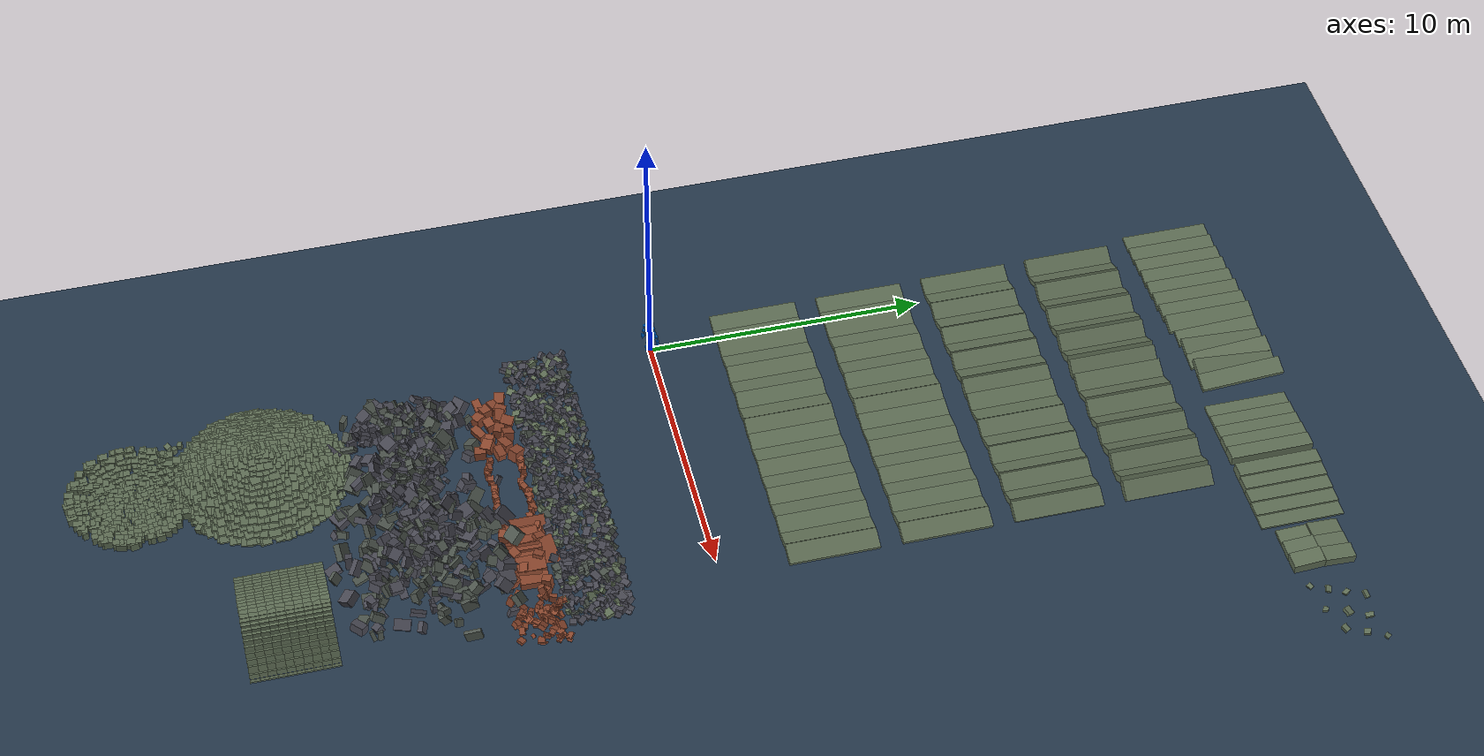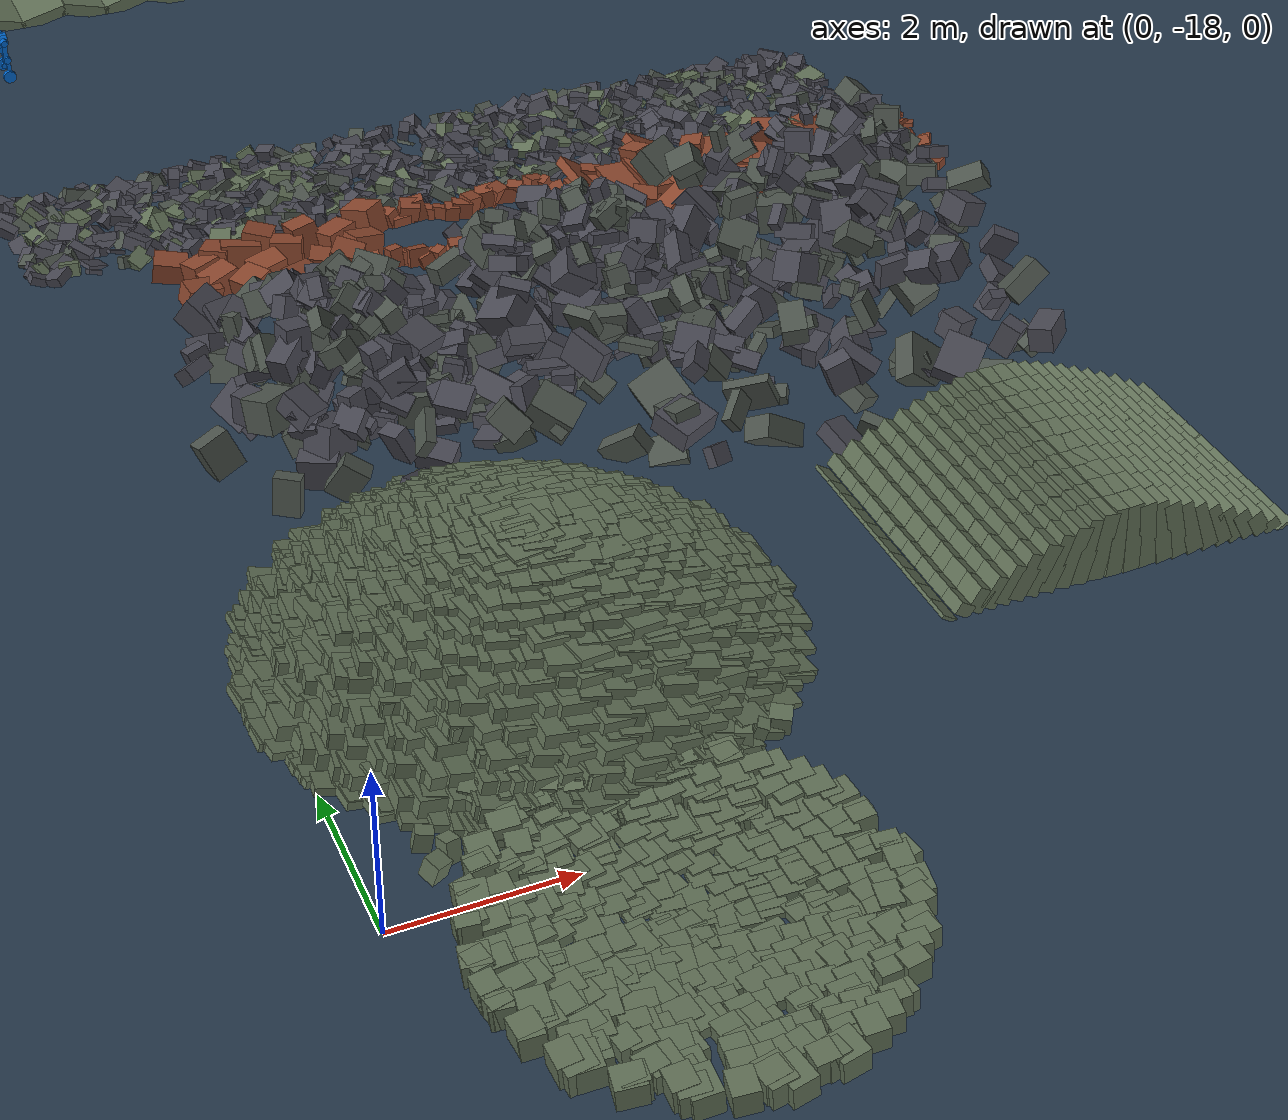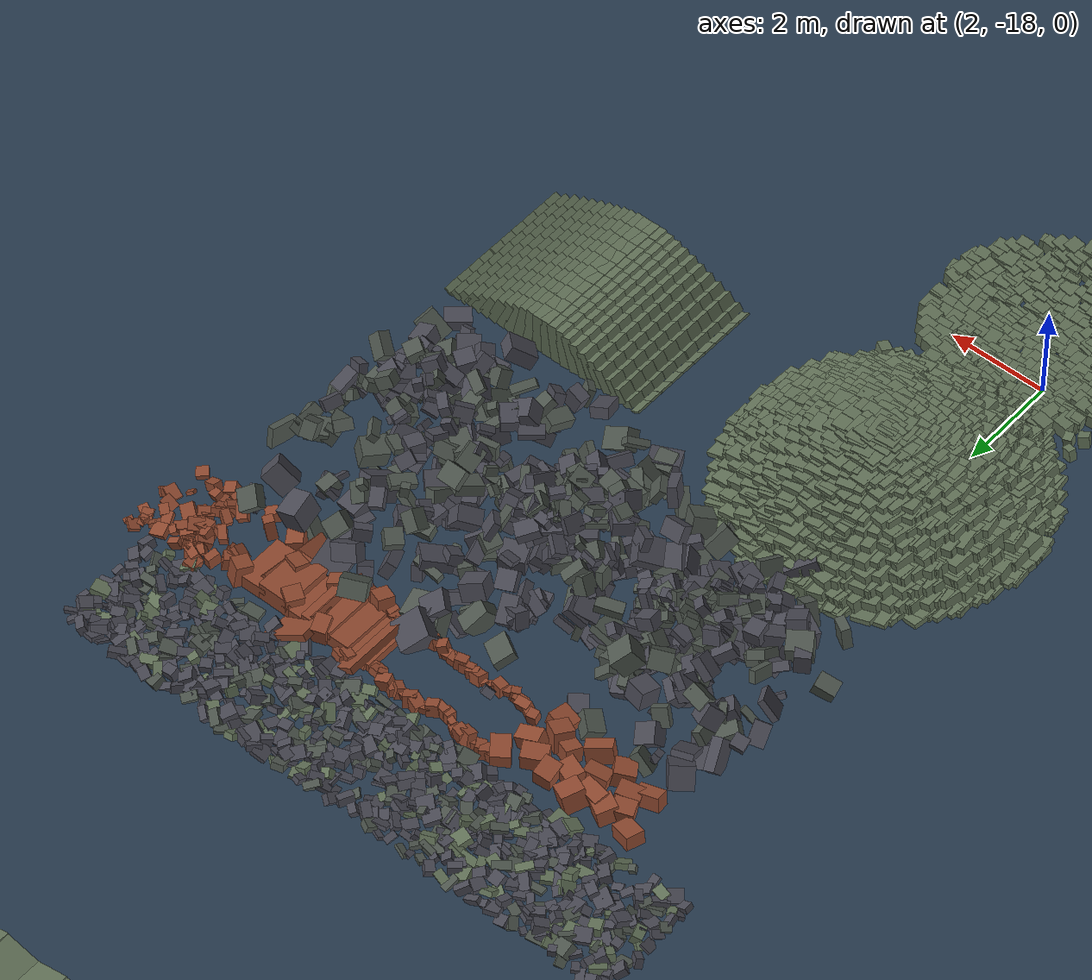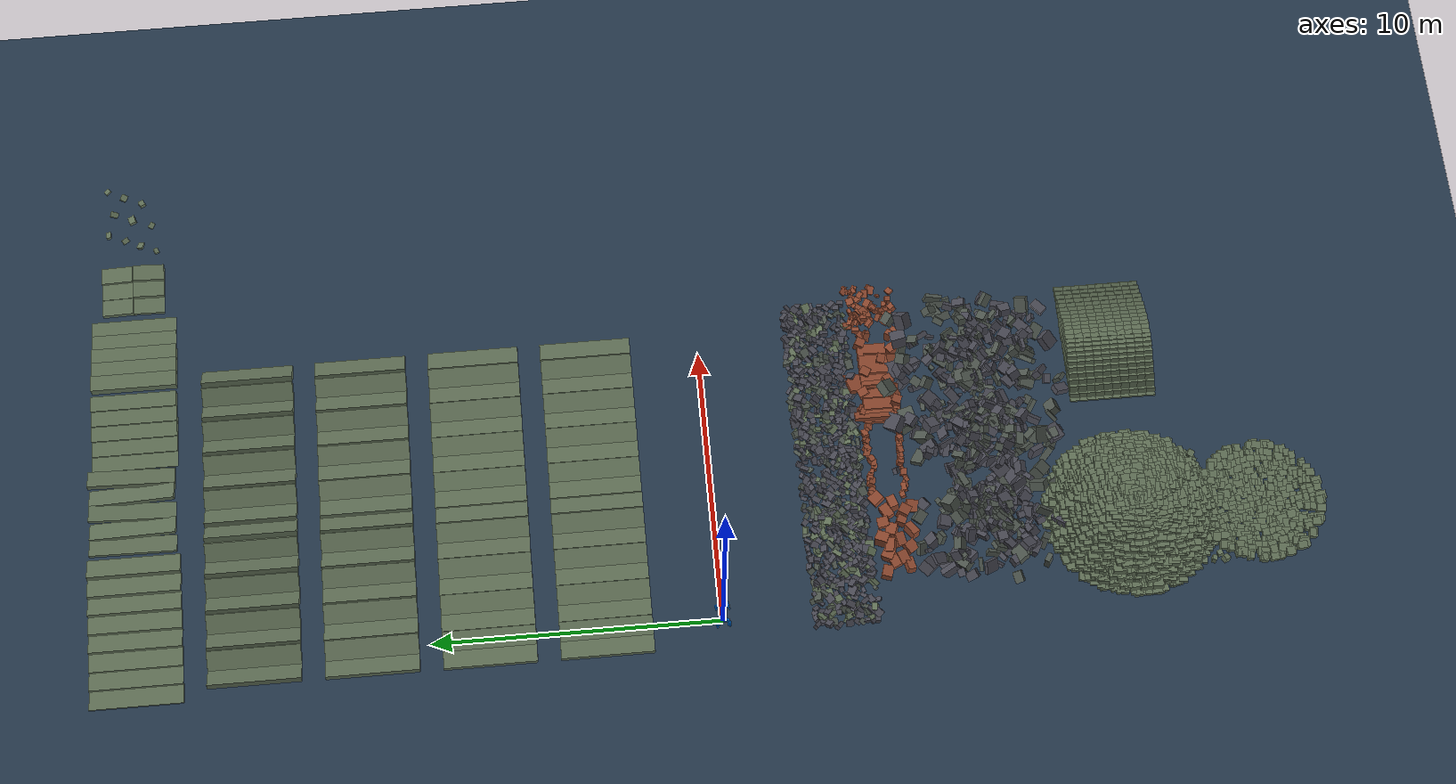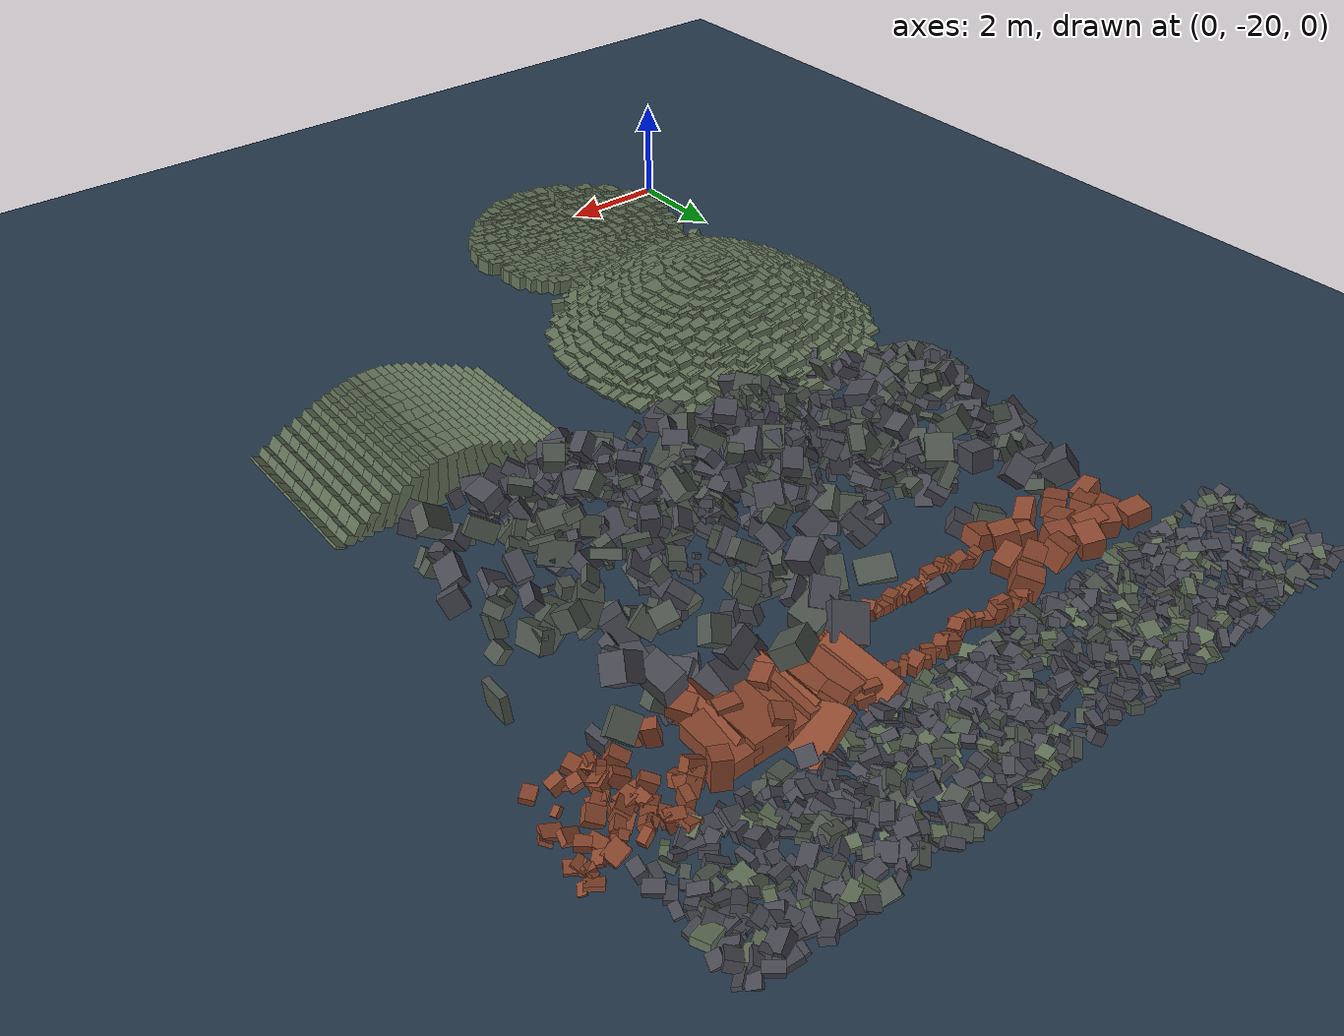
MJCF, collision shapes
<mujoco model="M20">

    <default>
        <default class="robot">
            <default class="motor">
                <joint/>
                <motor/>
            </default>
            <default class="visual">
                <geom material="default_material" contype="0" conaffinity="0" group="2"/>
            </default>
            <default class="collision">
                <geom material="collision_material" condim="3" contype="1" conaffinity="1" solref="0.005 1"
                      friction="1 0.01 0.001" density="0" group="1"/>
            </default>
        </default>
    </default>

    <compiler angle="radian" meshdir="../meshes/"/>
    <compiler autolimits="true"/>

    <asset>
        <material name="default_material" rgba="0.7 0.7 0.7 1"/>
        <material name="collision_material" rgba="0.0 0.4 0.8 0.2"/>
        <mesh name="base_link" file="base_link.STL"/>
        <mesh name="fl_hipx" file="fl_hipx.STL"/>
        <mesh name="fl_hipy" file="fl_hipy.STL"/>
        <mesh name="fl_knee" file="fl_knee.STL"/>
        <mesh name="fl_wheel" file="fl_wheel.STL"/>
        <mesh name="fr_hipx" file="fr_hipx.STL"/>
        <mesh name="fr_hipy" file="fr_hipy.STL"/>
        <mesh name="fr_knee" file="fr_knee.STL"/>
        <mesh name="fr_wheel" file="fr_wheel.STL"/>
        <mesh name="hl_hipx" file="hl_hipx.STL"/>
        <mesh name="hl_hipy" file="hl_hipy.STL"/>
        <mesh name="hl_knee" file="hl_knee.STL"/>
        <mesh name="hl_wheel" file="hl_wheel.STL"/>
        <mesh name="hr_hipx" file="hr_hipx.STL"/>
        <mesh name="hr_hipy" file="hr_hipy.STL"/>
        <mesh name="hr_knee" file="hr_knee.STL"/>
        <mesh name="hr_wheel" file="hr_wheel.STL"/>
        <texture name="texplane" type="2d" builtin="checker" rgb1=".2 .3 .4" rgb2=".1 0.15 0.2"
                 width="512" height="512"/>
        <material name='MatPlane' reflectance='0.3' texture="texplane" texrepeat="1 1" texuniform="true"/>
        <material name="terrain_boxes" rgba="0.45 0.38 0.26 1"/>
        <material name="terrain_rough" rgba="0.30 0.33 0.30 1"/>
        <material name="terrain_uneven" rgba="0.38 0.44 0.34 1"/>
        <material name="terrain_stone_dense" rgba="0.28 0.28 0.32 1"/>
        <material name="terrain_extreme" rgba="0.55 0.28 0.18 1"/>
    </asset>

    <worldbody>
        <!-- 灯光 -->
        <light directional="true" pos="-0.5 0.5 3" dir="0 0 -1"/>
        <geom name='floor' pos='0 0 0' size='100 100 .125' type='plane' material="MatPlane" condim='3'
              friction="1 0.01 0.01" group="0"/>

        <!-- ====== y=4: Steeper terrain, 2 repetitions ====== -->
        <geom name="terrain_steeper_y4_r0_00" type="box" pos="-0.60 4 0.066" size="0.36 1.60 0.066" euler="0 0.20 0" material="terrain_uneven" friction="1.2 0.01 0.01" condim="3"/>
        <geom name="terrain_steeper_y4_r0_01" type="box" pos="0.05 4 0.072" size="0.36 1.60 0.072" euler="0 -0.21 0" material="terrain_uneven" friction="1.2 0.01 0.01" condim="3"/>
        <geom name="terrain_steeper_y4_r0_02" type="box" pos="0.70 4 0.078" size="0.36 1.60 0.078" euler="0 0.23 0" material="terrain_uneven" friction="1.2 0.01 0.01" condim="3"/>
        <geom name="terrain_steeper_y4_r0_03" type="box" pos="1.35 4 0.084" size="0.36 1.60 0.084" euler="0 -0.24 0" material="terrain_uneven" friction="1.2 0.01 0.01" condim="3"/>
        <geom name="terrain_steeper_y4_r0_04" type="box" pos="2.00 4 0.090" size="0.36 1.60 0.090" euler="0 0.26 0" material="terrain_uneven" friction="1.2 0.01 0.01" condim="3"/>
        <geom name="terrain_steeper_y4_r0_05" type="box" pos="2.65 4 0.096" size="0.36 1.60 0.096" euler="0 -0.27 0" material="terrain_uneven" friction="1.2 0.01 0.01" condim="3"/>
        <geom name="terrain_steeper_y4_r0_06" type="box" pos="3.30 4 0.102" size="0.36 1.60 0.102" euler="0 0.29 0" material="terrain_uneven" friction="1.2 0.01 0.01" condim="3"/>
        <geom name="terrain_steeper_y4_r0_07" type="box" pos="3.95 4 0.108" size="0.36 1.60 0.108" euler="0 -0.30 0" material="terrain_uneven" friction="1.2 0.01 0.01" condim="3"/>
        <geom name="terrain_steeper_y4_r0_08" type="box" pos="4.60 4 0.114" size="0.36 1.60 0.114" euler="0 0.32 0" material="terrain_uneven" friction="1.2 0.01 0.01" condim="3"/>
        <geom name="terrain_steeper_y4_r1_00" type="box" pos="5.25 4 0.066" size="0.36 1.60 0.066" euler="0 0.20 0" material="terrain_uneven" friction="1.2 0.01 0.01" condim="3"/>
        <geom name="terrain_steeper_y4_r1_01" type="box" pos="5.90 4 0.072" size="0.36 1.60 0.072" euler="0 -0.21 0" material="terrain_uneven" friction="1.2 0.01 0.01" condim="3"/>
        <geom name="terrain_steeper_y4_r1_02" type="box" pos="6.55 4 0.078" size="0.36 1.60 0.078" euler="0 0.23 0" material="terrain_uneven" friction="1.2 0.01 0.01" condim="3"/>
        <geom name="terrain_steeper_y4_r1_03" type="box" pos="7.20 4 0.084" size="0.36 1.60 0.084" euler="0 -0.24 0" material="terrain_uneven" friction="1.2 0.01 0.01" condim="3"/>
        <geom name="terrain_steeper_y4_r1_04" type="box" pos="7.85 4 0.090" size="0.36 1.60 0.090" euler="0 0.26 0" material="terrain_uneven" friction="1.2 0.01 0.01" condim="3"/>
        <geom name="terrain_steeper_y4_r1_05" type="box" pos="8.50 4 0.096" size="0.36 1.60 0.096" euler="0 -0.27 0" material="terrain_uneven" friction="1.2 0.01 0.01" condim="3"/>
        <geom name="terrain_steeper_y4_r1_06" type="box" pos="9.15 4 0.102" size="0.36 1.60 0.102" euler="0 0.29 0" material="terrain_uneven" friction="1.2 0.01 0.01" condim="3"/>
        <geom name="terrain_steeper_y4_r1_07" type="box" pos="9.80 4 0.108" size="0.36 1.60 0.108" euler="0 -0.30 0" material="terrain_uneven" friction="1.2 0.01 0.01" condim="3"/>
        <geom name="terrain_steeper_y4_r1_08" type="box" pos="10.45 4 0.114" size="0.36 1.60 0.114" euler="0 0.32 0" material="terrain_uneven" friction="1.2 0.01 0.01" condim="3"/>

        <!-- ====== y=8: Steeper terrain, 2 repetitions ====== -->
        <geom name="terrain_steeper_y8_r0_00" type="box" pos="-0.60 8 0.066" size="0.36 1.60 0.066" euler="0 0.20 0" material="terrain_uneven" friction="1.2 0.01 0.01" condim="3"/>
        <geom name="terrain_steeper_y8_r0_01" type="box" pos="0.05 8 0.072" size="0.36 1.60 0.072" euler="0 -0.21 0" material="terrain_uneven" friction="1.2 0.01 0.01" condim="3"/>
        <geom name="terrain_steeper_y8_r0_02" type="box" pos="0.70 8 0.078" size="0.36 1.60 0.078" euler="0 0.23 0" material="terrain_uneven" friction="1.2 0.01 0.01" condim="3"/>
        <geom name="terrain_steeper_y8_r0_03" type="box" pos="1.35 8 0.084" size="0.36 1.60 0.084" euler="0 -0.24 0" material="terrain_uneven" friction="1.2 0.01 0.01" condim="3"/>
        <geom name="terrain_steeper_y8_r0_04" type="box" pos="2.00 8 0.090" size="0.36 1.60 0.090" euler="0 0.26 0" material="terrain_uneven" friction="1.2 0.01 0.01" condim="3"/>
        <geom name="terrain_steeper_y8_r0_05" type="box" pos="2.65 8 0.096" size="0.36 1.60 0.096" euler="0 -0.27 0" material="terrain_uneven" friction="1.2 0.01 0.01" condim="3"/>
        <geom name="terrain_steeper_y8_r0_06" type="box" pos="3.30 8 0.102" size="0.36 1.60 0.102" euler="0 0.29 0" material="terrain_uneven" friction="1.2 0.01 0.01" condim="3"/>
        <geom name="terrain_steeper_y8_r0_07" type="box" pos="3.95 8 0.108" size="0.36 1.60 0.108" euler="0 -0.30 0" material="terrain_uneven" friction="1.2 0.01 0.01" condim="3"/>
        <geom name="terrain_steeper_y8_r0_08" type="box" pos="4.60 8 0.114" size="0.36 1.60 0.114" euler="0 0.32 0" material="terrain_uneven" friction="1.2 0.01 0.01" condim="3"/>
        <geom name="terrain_steeper_y8_r1_00" type="box" pos="5.25 8 0.066" size="0.36 1.60 0.066" euler="0 0.20 0" material="terrain_uneven" friction="1.2 0.01 0.01" condim="3"/>
        <geom name="terrain_steeper_y8_r1_01" type="box" pos="5.90 8 0.072" size="0.36 1.60 0.072" euler="0 -0.21 0" material="terrain_uneven" friction="1.2 0.01 0.01" condim="3"/>
        <geom name="terrain_steeper_y8_r1_02" type="box" pos="6.55 8 0.078" size="0.36 1.60 0.078" euler="0 0.23 0" material="terrain_uneven" friction="1.2 0.01 0.01" condim="3"/>
        <geom name="terrain_steeper_y8_r1_03" type="box" pos="7.20 8 0.084" size="0.36 1.60 0.084" euler="0 -0.24 0" material="terrain_uneven" friction="1.2 0.01 0.01" condim="3"/>
        <geom name="terrain_steeper_y8_r1_04" type="box" pos="7.85 8 0.090" size="0.36 1.60 0.090" euler="0 0.26 0" material="terrain_uneven" friction="1.2 0.01 0.01" condim="3"/>
        <geom name="terrain_steeper_y8_r1_05" type="box" pos="8.50 8 0.096" size="0.36 1.60 0.096" euler="0 -0.27 0" material="terrain_uneven" friction="1.2 0.01 0.01" condim="3"/>
        <geom name="terrain_steeper_y8_r1_06" type="box" pos="9.15 8 0.102" size="0.36 1.60 0.102" euler="0 0.29 0" material="terrain_uneven" friction="1.2 0.01 0.01" condim="3"/>
        <geom name="terrain_steeper_y8_r1_07" type="box" pos="9.80 8 0.108" size="0.36 1.60 0.108" euler="0 -0.30 0" material="terrain_uneven" friction="1.2 0.01 0.01" condim="3"/>
        <geom name="terrain_steeper_y8_r1_08" type="box" pos="10.45 8 0.114" size="0.36 1.60 0.114" euler="0 0.32 0" material="terrain_uneven" friction="1.2 0.01 0.01" condim="3"/>

        <!-- ====== y=12: Extra steeper terrain, 2 repetitions ====== -->
        <geom name="terrain_steeper_y12_r0_00" type="box" pos="-0.60 12 0.080" size="0.36 1.60 0.080" euler="0 0.34 0" material="terrain_uneven" friction="1.2 0.01 0.01" condim="3"/>
        <geom name="terrain_steeper_y12_r0_01" type="box" pos="0.05 12 0.086" size="0.36 1.60 0.086" euler="0 -0.35 0" material="terrain_uneven" friction="1.2 0.01 0.01" condim="3"/>
        <geom name="terrain_steeper_y12_r0_02" type="box" pos="0.70 12 0.092" size="0.36 1.60 0.092" euler="0 0.37 0" material="terrain_uneven" friction="1.2 0.01 0.01" condim="3"/>
        <geom name="terrain_steeper_y12_r0_03" type="box" pos="1.35 12 0.098" size="0.36 1.60 0.098" euler="0 -0.38 0" material="terrain_uneven" friction="1.2 0.01 0.01" condim="3"/>
        <geom name="terrain_steeper_y12_r0_04" type="box" pos="2.00 12 0.104" size="0.36 1.60 0.104" euler="0 0.40 0" material="terrain_uneven" friction="1.2 0.01 0.01" condim="3"/>
        <geom name="terrain_steeper_y12_r0_05" type="box" pos="2.65 12 0.110" size="0.36 1.60 0.110" euler="0 -0.41 0" material="terrain_uneven" friction="1.2 0.01 0.01" condim="3"/>
        <geom name="terrain_steeper_y12_r0_06" type="box" pos="3.30 12 0.116" size="0.36 1.60 0.116" euler="0 0.43 0" material="terrain_uneven" friction="1.2 0.01 0.01" condim="3"/>
        <geom name="terrain_steeper_y12_r0_07" type="box" pos="3.95 12 0.122" size="0.36 1.60 0.122" euler="0 -0.44 0" material="terrain_uneven" friction="1.2 0.01 0.01" condim="3"/>
        <geom name="terrain_steeper_y12_r0_08" type="box" pos="4.60 12 0.128" size="0.36 1.60 0.128" euler="0 0.46 0" material="terrain_uneven" friction="1.2 0.01 0.01" condim="3"/>
        <geom name="terrain_steeper_y12_r1_00" type="box" pos="5.25 12 0.080" size="0.36 1.60 0.080" euler="0 0.34 0" material="terrain_uneven" friction="1.2 0.01 0.01" condim="3"/>
        <geom name="terrain_steeper_y12_r1_01" type="box" pos="5.90 12 0.086" size="0.36 1.60 0.086" euler="0 -0.35 0" material="terrain_uneven" friction="1.2 0.01 0.01" condim="3"/>
        <geom name="terrain_steeper_y12_r1_02" type="box" pos="6.55 12 0.092" size="0.36 1.60 0.092" euler="0 0.37 0" material="terrain_uneven" friction="1.2 0.01 0.01" condim="3"/>
        <geom name="terrain_steeper_y12_r1_03" type="box" pos="7.20 12 0.098" size="0.36 1.60 0.098" euler="0 -0.38 0" material="terrain_uneven" friction="1.2 0.01 0.01" condim="3"/>
        <geom name="terrain_steeper_y12_r1_04" type="box" pos="7.85 12 0.104" size="0.36 1.60 0.104" euler="0 0.40 0" material="terrain_uneven" friction="1.2 0.01 0.01" condim="3"/>
        <geom name="terrain_steeper_y12_r1_05" type="box" pos="8.50 12 0.110" size="0.36 1.60 0.110" euler="0 -0.41 0" material="terrain_uneven" friction="1.2 0.01 0.01" condim="3"/>
        <geom name="terrain_steeper_y12_r1_06" type="box" pos="9.15 12 0.116" size="0.36 1.60 0.116" euler="0 0.43 0" material="terrain_uneven" friction="1.2 0.01 0.01" condim="3"/>
        <geom name="terrain_steeper_y12_r1_07" type="box" pos="9.80 12 0.122" size="0.36 1.60 0.122" euler="0 -0.44 0" material="terrain_uneven" friction="1.2 0.01 0.01" condim="3"/>
        <geom name="terrain_steeper_y12_r1_08" type="box" pos="10.45 12 0.128" size="0.36 1.60 0.128" euler="0 0.46 0" material="terrain_uneven" friction="1.2 0.01 0.01" condim="3"/>

        <!-- ====== y=16: Ultra steeper terrain, 2 repetitions ====== -->
        <geom name="terrain_steeper_y16_r0_00" type="box" pos="-0.60 16 0.094" size="0.36 1.60 0.094" euler="0 0.48 0" material="terrain_uneven" friction="1.2 0.01 0.01" condim="3"/>
        <geom name="terrain_steeper_y16_r0_01" type="box" pos="0.05 16 0.100" size="0.36 1.60 0.100" euler="0 -0.49 0" material="terrain_uneven" friction="1.2 0.01 0.01" condim="3"/>
        <geom name="terrain_steeper_y16_r0_02" type="box" pos="0.70 16 0.106" size="0.36 1.60 0.106" euler="0 0.51 0" material="terrain_uneven" friction="1.2 0.01 0.01" condim="3"/>
        <geom name="terrain_steeper_y16_r0_03" type="box" pos="1.35 16 0.112" size="0.36 1.60 0.112" euler="0 -0.52 0" material="terrain_uneven" friction="1.2 0.01 0.01" condim="3"/>
        <geom name="terrain_steeper_y16_r0_04" type="box" pos="2.00 16 0.118" size="0.36 1.60 0.118" euler="0 0.54 0" material="terrain_uneven" friction="1.2 0.01 0.01" condim="3"/>
        <geom name="terrain_steeper_y16_r0_05" type="box" pos="2.65 16 0.124" size="0.36 1.60 0.124" euler="0 -0.55 0" material="terrain_uneven" friction="1.2 0.01 0.01" condim="3"/>
        <geom name="terrain_steeper_y16_r0_06" type="box" pos="3.30 16 0.130" size="0.36 1.60 0.130" euler="0 0.57 0" material="terrain_uneven" friction="1.2 0.01 0.01" condim="3"/>
        <geom name="terrain_steeper_y16_r0_07" type="box" pos="3.95 16 0.136" size="0.36 1.60 0.136" euler="0 -0.58 0" material="terrain_uneven" friction="1.2 0.01 0.01" condim="3"/>
        <geom name="terrain_steeper_y16_r0_08" type="box" pos="4.60 16 0.142" size="0.36 1.60 0.142" euler="0 0.60 0" material="terrain_uneven" friction="1.2 0.01 0.01" condim="3"/>
        <geom name="terrain_steeper_y16_r1_00" type="box" pos="5.25 16 0.094" size="0.36 1.60 0.094" euler="0 0.48 0" material="terrain_uneven" friction="1.2 0.01 0.01" condim="3"/>
        <geom name="terrain_steeper_y16_r1_01" type="box" pos="5.90 16 0.100" size="0.36 1.60 0.100" euler="0 -0.49 0" material="terrain_uneven" friction="1.2 0.01 0.01" condim="3"/>
        <geom name="terrain_steeper_y16_r1_02" type="box" pos="6.55 16 0.106" size="0.36 1.60 0.106" euler="0 0.51 0" material="terrain_uneven" friction="1.2 0.01 0.01" condim="3"/>
        <geom name="terrain_steeper_y16_r1_03" type="box" pos="7.20 16 0.112" size="0.36 1.60 0.112" euler="0 -0.52 0" material="terrain_uneven" friction="1.2 0.01 0.01" condim="3"/>
        <geom name="terrain_steeper_y16_r1_04" type="box" pos="7.85 16 0.118" size="0.36 1.60 0.118" euler="0 0.54 0" material="terrain_uneven" friction="1.2 0.01 0.01" condim="3"/>
        <geom name="terrain_steeper_y16_r1_05" type="box" pos="8.50 16 0.124" size="0.36 1.60 0.124" euler="0 -0.55 0" material="terrain_uneven" friction="1.2 0.01 0.01" condim="3"/>
        <geom name="terrain_steeper_y16_r1_06" type="box" pos="9.15 16 0.130" size="0.36 1.60 0.130" euler="0 0.57 0" material="terrain_uneven" friction="1.2 0.01 0.01" condim="3"/>
        <geom name="terrain_steeper_y16_r1_07" type="box" pos="9.80 16 0.136" size="0.36 1.60 0.136" euler="0 -0.58 0" material="terrain_uneven" friction="1.2 0.01 0.01" condim="3"/>
        <geom name="terrain_steeper_y16_r1_08" type="box" pos="10.45 16 0.142" size="0.36 1.60 0.142" euler="0 0.60 0" material="terrain_uneven" friction="1.2 0.01 0.01" condim="3"/>

        <!-- ====== y=20: Steep uneven uphill ====== -->
        <geom name="terrain_steep_up_00" type="box" pos="-1.00 20 0.055" size="0.35 1.60 0.035" euler="0 0.12 0" material="terrain_uneven" friction="1.3 0.01 0.01" condim="3"/>
        <geom name="terrain_steep_up_01" type="box" pos="-0.35 20 0.095" size="0.35 1.60 0.045" euler="0 0.18 0" material="terrain_uneven" friction="1.3 0.01 0.01" condim="3"/>
        <geom name="terrain_steep_up_02" type="box" pos="0.30 20 0.135" size="0.35 1.60 0.050" euler="0 0.10 0" material="terrain_uneven" friction="1.3 0.01 0.01" condim="3"/>
        <geom name="terrain_steep_up_03" type="box" pos="0.95 20 0.185" size="0.35 1.60 0.060" euler="0 0.22 0" material="terrain_uneven" friction="1.3 0.01 0.01" condim="3"/>
        <geom name="terrain_steep_up_04" type="box" pos="1.60 20 0.235" size="0.35 1.60 0.065" euler="0 0.16 0" material="terrain_uneven" friction="1.3 0.01 0.01" condim="3"/>
        <geom name="terrain_steep_up_05" type="box" pos="2.25 20 0.295" size="0.35 1.60 0.070" euler="0 0.25 0" material="terrain_uneven" friction="1.3 0.01 0.01" condim="3"/>
        <geom name="terrain_steep_up_06" type="box" pos="2.90 20 0.355" size="0.35 1.60 0.080" euler="0 0.18 0" material="terrain_uneven" friction="1.3 0.01 0.01" condim="3"/>
        <geom name="terrain_steep_up_07" type="box" pos="3.55 20 0.425" size="0.35 1.60 0.090" euler="0 0.28 0" material="terrain_uneven" friction="1.3 0.01 0.01" condim="3"/>

        <!-- Rough steep slope with left-right tilt at y=20 -->
        <geom name="terrain_rough_slope_00" type="box" pos="4.30 20 0.480" size="0.32 1.50 0.055" euler="0.04 0.20 0.00" material="terrain_uneven" friction="1.4 0.01 0.01" condim="3"/>
        <geom name="terrain_rough_slope_01" type="box" pos="4.90 20 0.530" size="0.32 1.50 0.070" euler="-0.06 0.24 0.00" material="terrain_uneven" friction="1.4 0.01 0.01" condim="3"/>
        <geom name="terrain_rough_slope_02" type="box" pos="5.50 20 0.590" size="0.32 1.50 0.060" euler="0.08 0.18 0.00" material="terrain_uneven" friction="1.4 0.01 0.01" condim="3"/>
        <geom name="terrain_rough_slope_03" type="box" pos="6.10 20 0.660" size="0.32 1.50 0.080" euler="-0.10 0.26 0.00" material="terrain_uneven" friction="1.4 0.01 0.01" condim="3"/>
        <geom name="terrain_rough_slope_04" type="box" pos="6.70 20 0.730" size="0.32 1.50 0.090" euler="0.07 0.30 0.00" material="terrain_uneven" friction="1.4 0.01 0.01" condim="3"/>

        <!-- Up stairs at y=20 -->
        <geom name="terrain_stair_up_00" type="box" pos="7.60 20 0.035" size="0.28 1.50 0.035" material="terrain_uneven" friction="1.3 0.01 0.01" condim="3"/>
        <geom name="terrain_stair_up_01" type="box" pos="8.15 20 0.070" size="0.28 1.50 0.070" material="terrain_uneven" friction="1.3 0.01 0.01" condim="3"/>
        <geom name="terrain_stair_up_02" type="box" pos="8.70 20 0.105" size="0.28 1.50 0.105" material="terrain_uneven" friction="1.3 0.01 0.01" condim="3"/>
        <geom name="terrain_stair_up_03" type="box" pos="9.25 20 0.140" size="0.28 1.50 0.140" material="terrain_uneven" friction="1.3 0.01 0.01" condim="3"/>
        <geom name="terrain_stair_up_04" type="box" pos="9.80 20 0.175" size="0.28 1.50 0.175" material="terrain_uneven" friction="1.3 0.01 0.01" condim="3"/>

        <!-- Down stairs at y=20 -->
        <geom name="terrain_stair_down_00" type="box" pos="10.60 20 0.175" size="0.28 1.50 0.175" material="terrain_uneven" friction="1.3 0.01 0.01" condim="3"/>
        <geom name="terrain_stair_down_01" type="box" pos="11.15 20 0.140" size="0.28 1.50 0.140" material="terrain_uneven" friction="1.3 0.01 0.01" condim="3"/>
        <geom name="terrain_stair_down_02" type="box" pos="11.70 20 0.105" size="0.28 1.50 0.105" material="terrain_uneven" friction="1.3 0.01 0.01" condim="3"/>
        <geom name="terrain_stair_down_03" type="box" pos="12.25 20 0.070" size="0.28 1.50 0.070" material="terrain_uneven" friction="1.3 0.01 0.01" condim="3"/>
        <geom name="terrain_stair_down_04" type="box" pos="12.80 20 0.035" size="0.28 1.50 0.035" material="terrain_uneven" friction="1.3 0.01 0.01" condim="3"/>

        <!-- Broken stairs at y=20 (shifted +3.0m) -->
        <geom name="terrain_broken_stair_00" type="box" pos="13.60 19.45 0.060" size="0.30 0.55 0.060" euler="0.04 0.02 0.00" material="terrain_uneven" friction="1.4 0.01 0.01" condim="3"/>
        <geom name="terrain_broken_stair_01" type="box" pos="13.60 20.55 0.090" size="0.30 0.55 0.090" euler="-0.05 0.00 0.00" material="terrain_uneven" friction="1.4 0.01 0.01" condim="3"/>
        <geom name="terrain_broken_stair_02" type="box" pos="14.20 19.45 0.130" size="0.30 0.55 0.130" euler="0.06 0.03 0.00" material="terrain_uneven" friction="1.4 0.01 0.01" condim="3"/>
        <geom name="terrain_broken_stair_03" type="box" pos="14.20 20.55 0.110" size="0.30 0.55 0.110" euler="-0.04 -0.02 0.00" material="terrain_uneven" friction="1.4 0.01 0.01" condim="3"/>
        <geom name="terrain_broken_stair_04" type="box" pos="14.80 19.45 0.180" size="0.30 0.55 0.180" euler="0.08 0.04 0.00" material="terrain_uneven" friction="1.4 0.01 0.01" condim="3"/>
        <geom name="terrain_broken_stair_05" type="box" pos="14.80 20.55 0.160" size="0.30 0.55 0.160" euler="-0.06 0.02 0.00" material="terrain_uneven" friction="1.4 0.01 0.01" condim="3"/>

        <!-- Rubble / gravel stones at y=20 (shifted +3.0m) -->
        <geom name="terrain_rubble_00" type="box" pos="15.80 19.20 0.035" size="0.10 0.08 0.035" euler="0.20 0.10 0.40" material="terrain_uneven" friction="1.5 0.01 0.01" condim="3"/>
        <geom name="terrain_rubble_01" type="box" pos="16.05 19.75 0.045" size="0.12 0.10 0.045" euler="-0.15 0.20 -0.30" material="terrain_uneven" friction="1.5 0.01 0.01" condim="3"/>
        <geom name="terrain_rubble_02" type="box" pos="16.30 20.30 0.030" size="0.09 0.12 0.030" euler="0.25 -0.15 0.60" material="terrain_uneven" friction="1.5 0.01 0.01" condim="3"/>
        <geom name="terrain_rubble_03" type="box" pos="16.55 20.90 0.050" size="0.14 0.08 0.050" euler="-0.20 0.25 0.20" material="terrain_uneven" friction="1.5 0.01 0.01" condim="3"/>
        <geom name="terrain_rubble_04" type="box" pos="16.85 19.35 0.040" size="0.11 0.09 0.040" euler="0.10 -0.25 -0.50" material="terrain_uneven" friction="1.5 0.01 0.01" condim="3"/>
        <geom name="terrain_rubble_05" type="box" pos="17.10 20.05 0.060" size="0.15 0.12 0.060" euler="-0.25 0.10 0.35" material="terrain_uneven" friction="1.5 0.01 0.01" condim="3"/>
        <geom name="terrain_rubble_06" type="box" pos="17.40 20.70 0.035" size="0.10 0.14 0.035" euler="0.30 -0.20 -0.20" material="terrain_uneven" friction="1.5 0.01 0.01" condim="3"/>
        <geom name="terrain_rubble_07" type="box" pos="17.75 19.70 0.055" size="0.13 0.10 0.055" euler="-0.10 0.30 0.50" material="terrain_uneven" friction="1.5 0.01 0.01" condim="3"/>
        <geom name="terrain_rubble_08" type="box" pos="18.05 20.35 0.045" size="0.12 0.11 0.045" euler="0.18 -0.18 -0.40" material="terrain_uneven" friction="1.5 0.01 0.01" condim="3"/>
        <geom name="terrain_rubble_09" type="box" pos="18.35 20.95 0.030" size="0.09 0.10 0.030" euler="-0.20 0.15 0.70" material="terrain_uneven" friction="1.5 0.01 0.01" condim="3"/>

        <!-- ====== Dense Stone Field: irregular, interconnected stones ====== -->
        <geom name="stone_0000" type="box" pos="-0.467 -3.207 0.098" size="0.137 0.069 0.098" quat="0.915871 0.184460 0.100032 -0.342269" material="terrain_stone_dense" friction="1.64 0.01 0.01" condim="3"/>
        <geom name="stone_0001" type="box" pos="-0.229 -3.183 0.064" size="0.109 0.083 0.064" quat="0.943898 -0.252701 0.145235 0.155262" material="terrain_stone_dense" friction="1.73 0.01 0.01" condim="3"/>
        <geom name="stone_0002" type="box" pos="-0.004 -3.153 0.024" size="0.081 0.107 0.024" quat="0.949245 -0.205062 0.055222 0.232021" material="terrain_stone_dense" friction="1.79 0.01 0.01" condim="3"/>
        <geom name="stone_0003" type="box" pos="0.144 -3.204 0.038" size="0.074 0.108 0.038" quat="0.949827 0.099209 -0.005386 0.296576" material="terrain_stone_dense" friction="1.71 0.01 0.01" condim="3"/>
        <geom name="stone_0004" type="box" pos="0.420 -3.163 0.031" size="0.092 0.128 0.031" quat="0.930140 -0.085638 -0.295684 0.200194" material="terrain_rough" friction="1.7 0.01 0.01" condim="3"/>
        <geom name="stone_0005" type="box" pos="0.634 -3.205 0.073" size="0.075 0.071 0.073" quat="0.970811 -0.023910 0.031099 0.236617" material="terrain_stone_dense" friction="1.69 0.01 0.01" condim="3"/>
        <geom name="stone_0006" type="box" pos="1.032 -3.234 0.025" size="0.154 0.083 0.025" quat="0.977908 -0.101584 -0.128576 0.129789" material="terrain_rough" friction="1.67 0.01 0.01" condim="3"/>
        <geom name="stone_0007" type="box" pos="1.280 -3.211 0.027" size="0.078 0.062 0.027" quat="0.947325 0.110096 -0.056459 -0.295408" material="terrain_stone_dense" friction="1.65 0.01 0.01" condim="3"/>
        <geom name="stone_0008" type="box" pos="1.504 -3.206 0.049" size="0.093 0.123 0.049" quat="0.890741 -0.119114 -0.274714 0.341943" material="terrain_rough" friction="1.77 0.01 0.01" condim="3"/>
        <geom name="stone_0009" type="box" pos="1.672 -3.144 0.042" size="0.139 0.105 0.042" quat="0.952816 -0.206096 0.222614 0.010449" material="terrain_stone_dense" friction="1.56 0.01 0.01" condim="3"/>
        <geom name="stone_0010" type="box" pos="1.930 -3.239 0.055" size="0.143 0.132 0.055" quat="0.987869 0.063052 0.055102 0.130775" material="terrain_stone_dense" friction="1.53 0.01 0.01" condim="3"/>
        <geom name="stone_0011" type="box" pos="2.085 -3.201 0.067" size="0.076 0.070 0.067" quat="0.951279 -0.191427 0.214517 0.111383" material="terrain_stone_dense" friction="1.6 0.01 0.01" condim="3"/>
        <geom name="stone_0012" type="box" pos="2.303 -3.145 0.059" size="0.146 0.068 0.059" quat="0.969032 -0.020338 0.237664 0.063865" material="terrain_stone_dense" friction="1.64 0.01 0.01" condim="3"/>
        <geom name="stone_0013" type="box" pos="2.560 -3.198 0.092" size="0.062 0.143 0.092" quat="0.921884 -0.174368 0.095143 -0.332676" material="terrain_stone_dense" friction="1.7 0.01 0.01" condim="3"/>
        <geom name="stone_0014" type="box" pos="2.819 -3.173 0.038" size="0.072 0.152 0.038" quat="0.961728 -0.246493 0.058156 -0.104586" material="terrain_rough" friction="1.75 0.01 0.01" condim="3"/>
        <geom name="stone_0015" type="box" pos="2.998 -3.146 0.095" size="0.117 0.086 0.095" quat="0.948125 -0.191617 -0.232702 -0.100955" material="terrain_uneven" friction="1.8 0.01 0.01" condim="3"/>
        <geom name="stone_0016" type="box" pos="3.270 -3.153 0.082" size="0.117 0.092 0.082" quat="0.930396 0.058063 -0.096220 -0.348903" material="terrain_stone_dense" friction="1.72 0.01 0.01" condim="3"/>
        <geom name="stone_0017" type="box" pos="3.512 -3.231 0.034" size="0.151 0.075 0.034" quat="0.938126 0.106606 0.182244 -0.274484" material="terrain_rough" friction="1.59 0.01 0.01" condim="3"/>
        <geom name="stone_0018" type="box" pos="3.737 -3.200 0.031" size="0.062 0.083 0.031" quat="0.973650 0.096623 -0.204964 0.025692" material="terrain_stone_dense" friction="1.71 0.01 0.01" condim="3"/>
        <geom name="stone_0019" type="box" pos="3.864 -3.164 0.030" size="0.141 0.073 0.030" quat="0.957734 0.219149 -0.095328 -0.160102" material="terrain_rough" friction="1.65 0.01 0.01" condim="3"/>
        <geom name="stone_0020" type="box" pos="4.175 -3.226 0.071" size="0.063 0.116 0.071" quat="0.951945 -0.224270 -0.176082 -0.111799" material="terrain_stone_dense" friction="1.79 0.01 0.01" condim="3"/>
        <geom name="stone_0021" type="box" pos="4.392 -3.163 0.029" size="0.146 0.062 0.029" quat="0.935612 0.210775 0.112888 -0.259733" material="terrain_stone_dense" friction="1.66 0.01 0.01" condim="3"/>
        <geom name="stone_0022" type="box" pos="4.604 -3.188 0.072" size="0.101 0.103 0.072" quat="0.955362 0.189948 -0.069355 -0.215391" material="terrain_rough" friction="1.57 0.01 0.01" condim="3"/>
        <geom name="stone_0023" type="box" pos="5.011 -3.242 0.094" size="0.094 0.074 0.094" quat="0.922560 -0.208507 -0.054823 -0.320003" material="terrain_stone_dense" friction="1.53 0.01 0.01" condim="3"/>
        <geom name="stone_0024" type="box" pos="5.451 -3.178 0.090" size="0.095 0.110 0.090" quat="0.925328 0.109376 -0.286454 -0.223045" material="terrain_stone_dense" friction="1.57 0.01 0.01" condim="3"/>
        <geom name="stone_0025" type="box" pos="5.865 -3.197 0.094" size="0.152 0.065 0.094" quat="0.881610 -0.265841 0.095239 0.378182" material="terrain_rough" friction="1.79 0.01 0.01" condim="3"/>
        <geom name="stone_0026" type="box" pos="6.134 -3.183 0.061" size="0.075 0.114 0.061" quat="0.975692 0.192243 -0.040125 -0.097248" material="terrain_stone_dense" friction="1.69 0.01 0.01" condim="3"/>
        <geom name="stone_0027" type="box" pos="6.277 -3.203 0.049" size="0.086 0.097 0.049" quat="0.980513 -0.082236 -0.080757 0.159091" material="terrain_uneven" friction="1.59 0.01 0.01" condim="3"/>
        <geom name="stone_0028" type="box" pos="6.590 -3.202 0.072" size="0.119 0.145 0.072" quat="0.979171 0.163299 0.037501 0.114676" material="terrain_rough" friction="1.59 0.01 0.01" condim="3"/>
        <geom name="stone_0029" type="box" pos="6.724 -3.177 0.028" size="0.075 0.121 0.028" quat="0.882339 0.197396 -0.161605 0.395470" material="terrain_uneven" friction="1.54 0.01 0.01" condim="3"/>
        <geom name="stone_0030" type="box" pos="7.016 -3.189 0.040" size="0.147 0.155 0.040" quat="0.967643 0.071058 -0.214370 0.112535" material="terrain_stone_dense" friction="1.55 0.01 0.01" condim="3"/>
        <geom name="stone_0031" type="box" pos="7.209 -3.204 0.059" size="0.144 0.140 0.059" quat="0.909943 0.128865 0.203145 -0.337831" material="terrain_stone_dense" friction="1.54 0.01 0.01" condim="3"/>
        <geom name="stone_0032" type="box" pos="7.439 -3.210 0.092" size="0.134 0.093 0.092" quat="0.976607 0.126495 -0.141036 -0.101718" material="terrain_stone_dense" friction="1.59 0.01 0.01" condim="3"/>
        <geom name="stone_0033" type="box" pos="7.598 -3.148 0.064" size="0.102 0.133 0.064" quat="0.959004 0.237494 0.144775 -0.054297" material="terrain_uneven" friction="1.61 0.01 0.01" condim="3"/>
        <geom name="stone_0034" type="box" pos="7.886 -3.146 0.030" size="0.154 0.124 0.030" quat="0.897303 0.087063 0.071867 -0.426735" material="terrain_rough" friction="1.64 0.01 0.01" condim="3"/>
        <geom name="stone_0035" type="box" pos="8.055 -3.205 0.083" size="0.093 0.152 0.083" quat="0.867399 -0.281142 0.180099 0.368974" material="terrain_rough" friction="1.59 0.01 0.01" condim="3"/>
        <geom name="stone_0036" type="box" pos="8.253 -3.140 0.092" size="0.132 0.069 0.092" quat="0.896379 -0.283954 -0.050225 -0.336678" material="terrain_stone_dense" friction="1.73 0.01 0.01" condim="3"/>
        <geom name="stone_0037" type="box" pos="8.681 -3.254 0.088" size="0.148 0.084 0.088" quat="0.872231 -0.280475 0.058885 0.396333" material="terrain_rough" friction="1.73 0.01 0.01" condim="3"/>
        <geom name="stone_0038" type="box" pos="9.001 -3.255 0.080" size="0.074 0.110 0.080" quat="0.927962 0.125223 0.160880 -0.311967" material="terrain_stone_dense" friction="1.72 0.01 0.01" condim="3"/>
        <geom name="stone_0039" type="box" pos="9.152 -3.175 0.069" size="0.127 0.065 0.069" quat="0.920364 -0.277283 0.153840 0.228861" material="terrain_stone_dense" friction="1.55 0.01 0.01" condim="3"/>
        <geom name="stone_0040" type="box" pos="9.362 -3.142 0.066" size="0.146 0.124 0.066" quat="0.944849 -0.142766 0.267909 -0.122891" material="terrain_rough" friction="1.67 0.01 0.01" condim="3"/>
        <geom name="stone_0041" type="box" pos="9.638 -3.147 0.058" size="0.116 0.100 0.058" quat="0.931110 -0.238450 -0.151221 -0.230887" material="terrain_stone_dense" friction="1.59 0.01 0.01" condim="3"/>
        <geom name="stone_0042" type="box" pos="9.853 -3.184 0.067" size="0.105 0.082 0.067" quat="0.958271 -0.115369 -0.243321 -0.095927" material="terrain_stone_dense" friction="1.64 0.01 0.01" condim="3"/>
        <geom name="stone_0043" type="box" pos="10.069 -3.192 0.045" size="0.131 0.125 0.045" quat="0.985027 0.158719 0.016931 -0.065140" material="terrain_stone_dense" friction="1.69 0.01 0.01" condim="3"/>
        <geom name="stone_0044" type="box" pos="10.282 -3.172 0.062" size="0.161 0.110 0.062" quat="0.931406 0.185903 -0.047060 0.309369" material="terrain_stone_dense" friction="1.65 0.01 0.01" condim="3"/>
        <geom name="stone_0045" type="box" pos="10.694 -3.220 0.021" size="0.095 0.134 0.021" quat="0.954626 0.196377 0.170298 -0.145339" material="terrain_stone_dense" friction="1.55 0.01 0.01" condim="3"/>
        <geom name="stone_0046" type="box" pos="10.894 -3.216 0.045" size="0.170 0.137 0.045" quat="0.982136 0.113154 0.101246 -0.111152" material="terrain_stone_dense" friction="1.69 0.01 0.01" condim="3"/>
        <geom name="stone_0047" type="box" pos="11.125 -3.197 0.099" size="0.078 0.144 0.099" quat="0.890540 -0.051805 0.180486 0.414342" material="terrain_stone_dense" friction="1.54 0.01 0.01" condim="3"/>
        <geom name="stone_0048" type="box" pos="11.367 -3.250 0.032" size="0.108 0.107 0.032" quat="0.896009 -0.069025 0.268354 -0.346971" material="terrain_stone_dense" friction="1.57 0.01 0.01" condim="3"/>
        <geom name="stone_0049" type="box" pos="-0.391 -3.380 0.087" size="0.069 0.084 0.087" quat="0.983093 0.061998 0.092246 0.145514" material="terrain_stone_dense" friction="1.73 0.01 0.01" condim="3"/>
        <geom name="stone_0050" type="box" pos="-0.186 -3.385 0.081" size="0.153 0.108 0.081" quat="0.915585 0.178546 0.071736 0.353101" material="terrain_uneven" friction="1.68 0.01 0.01" condim="3"/>
        <geom name="stone_0051" type="box" pos="0.031 -3.390 0.093" size="0.072 0.100 0.093" quat="0.973290 0.044591 -0.184366 -0.129334" material="terrain_stone_dense" friction="1.56 0.01 0.01" condim="3"/>
        <geom name="stone_0052" type="box" pos="0.321 -3.396 0.042" size="0.126 0.061 0.042" quat="0.902799 0.070157 0.112983 0.408984" material="terrain_stone_dense" friction="1.69 0.01 0.01" condim="3"/>
        <geom name="stone_0053" type="box" pos="0.521 -3.342 0.089" size="0.166 0.138 0.089" quat="0.969623 -0.201914 0.135698 -0.025440" material="terrain_rough" friction="1.67 0.01 0.01" condim="3"/>
        <geom name="stone_0054" type="box" pos="0.766 -3.332 0.048" size="0.141 0.135 0.048" quat="0.930957 -0.132331 -0.286033 0.184374" material="terrain_uneven" friction="1.65 0.01 0.01" condim="3"/>
        <geom name="stone_0055" type="box" pos="0.926 -3.333 0.064" size="0.147 0.068 0.064" quat="0.930254 0.088798 0.264781 0.237979" material="terrain_stone_dense" friction="1.51 0.01 0.01" condim="3"/>
        <geom name="stone_0056" type="box" pos="1.096 -3.437 0.089" size="0.138 0.137 0.089" quat="0.889797 0.183471 0.098887 -0.405981" material="terrain_stone_dense" friction="1.57 0.01 0.01" condim="3"/>
        <geom name="stone_0057" type="box" pos="1.413 -3.449 0.052" size="0.135 0.063 0.052" quat="0.940344 0.230489 0.039196 -0.247169" material="terrain_stone_dense" friction="1.76 0.01 0.01" condim="3"/>
        <geom name="stone_0058" type="box" pos="1.632 -3.414 0.091" size="0.104 0.087 0.091" quat="0.944514 -0.196482 -0.197174 -0.174386" material="terrain_rough" friction="1.72 0.01 0.01" condim="3"/>
        <geom name="stone_0059" type="box" pos="1.870 -3.414 0.100" size="0.075 0.117 0.100" quat="0.987329 0.114624 0.041131 -0.101739" material="terrain_stone_dense" friction="1.77 0.01 0.01" condim="3"/>
        <geom name="stone_0060" type="box" pos="2.214 -3.448 0.054" size="0.130 0.094 0.054" quat="0.959613 0.242408 0.142762 0.000760" material="terrain_uneven" friction="1.59 0.01 0.01" condim="3"/>
        <geom name="stone_0061" type="box" pos="2.438 -3.411 0.067" size="0.118 0.134 0.067" quat="0.965814 0.056210 -0.126090 -0.219419" material="terrain_stone_dense" friction="1.6 0.01 0.01" condim="3"/>
        <geom name="stone_0062" type="box" pos="2.735 -3.416 0.055" size="0.147 0.138 0.055" quat="0.950715 -0.054475 0.263439 0.154188" material="terrain_uneven" friction="1.74 0.01 0.01" condim="3"/>
        <geom name="stone_0063" type="box" pos="2.945 -3.428 0.096" size="0.071 0.125 0.096" quat="0.913469 -0.008556 -0.036526 -0.405176" material="terrain_stone_dense" friction="1.79 0.01 0.01" condim="3"/>
        <geom name="stone_0064" type="box" pos="3.345 -3.388 0.051" size="0.066 0.071 0.051" quat="0.938596 -0.202188 0.163992 -0.226418" material="terrain_stone_dense" friction="1.59 0.01 0.01" condim="3"/>
        <geom name="stone_0065" type="box" pos="3.560 -3.450 0.061" size="0.155 0.060 0.061" quat="0.993839 -0.011401 -0.091138 -0.062034" material="terrain_rough" friction="1.73 0.01 0.01" condim="3"/>
        <geom name="stone_0066" type="box" pos="3.761 -3.411 0.038" size="0.113 0.128 0.038" quat="0.897727 0.009264 0.250198 -0.362493" material="terrain_rough" friction="1.64 0.01 0.01" condim="3"/>
        <geom name="stone_0067" type="box" pos="3.968 -3.444 0.035" size="0.161 0.061 0.035" quat="0.945195 -0.225491 -0.231184 0.048108" material="terrain_stone_dense" friction="1.57 0.01 0.01" condim="3"/>
        <geom name="stone_0068" type="box" pos="4.492 -3.376 0.040" size="0.145 0.146 0.040" quat="0.968539 0.229512 -0.003065 0.096158" material="terrain_stone_dense" friction="1.8 0.01 0.01" condim="3"/>
        <geom name="stone_0069" type="box" pos="4.708 -3.412 0.053" size="0.126 0.082 0.053" quat="0.873448 -0.182810 -0.168611 -0.418616" material="terrain_stone_dense" friction="1.6 0.01 0.01" condim="3"/>
        <geom name="stone_0070" type="box" pos="4.850 -3.363 0.091" size="0.141 0.092 0.091" quat="0.931109 -0.016365 -0.209486 -0.298134" material="terrain_stone_dense" friction="1.71 0.01 0.01" condim="3"/>
        <geom name="stone_0071" type="box" pos="5.272 -3.331 0.090" size="0.074 0.150 0.090" quat="0.976577 0.033018 0.061506 -0.203527" material="terrain_stone_dense" friction="1.52 0.01 0.01" condim="3"/>
        <geom name="stone_0072" type="box" pos="5.525 -3.370 0.039" size="0.062 0.120 0.039" quat="0.962399 0.214477 -0.111431 0.123982" material="terrain_stone_dense" friction="1.67 0.01 0.01" condim="3"/>
        <geom name="stone_0073" type="box" pos="5.791 -3.363 0.054" size="0.143 0.158 0.054" quat="0.929654 0.077214 -0.253548 0.255918" material="terrain_stone_dense" friction="1.66 0.01 0.01" condim="3"/>
        <geom name="stone_0074" type="box" pos="5.941 -3.343 0.097" size="0.135 0.075 0.097" quat="0.929941 -0.113148 -0.208654 0.280839" material="terrain_stone_dense" friction="1.77 0.01 0.01" condim="3"/>
        <geom name="stone_0075" type="box" pos="6.206 -3.362 0.079" size="0.102 0.112 0.079" quat="0.979238 0.115332 0.161324 0.042025" material="terrain_uneven" friction="1.53 0.01 0.01" condim="3"/>
        <geom name="stone_0076" type="box" pos="6.474 -3.354 0.022" size="0.082 0.134 0.022" quat="0.941109 0.267674 -0.012947 0.206147" material="terrain_stone_dense" friction="1.77 0.01 0.01" condim="3"/>
        <geom name="stone_0077" type="box" pos="6.628 -3.377 0.095" size="0.105 0.120 0.095" quat="0.979626 -0.035750 -0.163045 -0.111679" material="terrain_stone_dense" friction="1.62 0.01 0.01" condim="3"/>
        <geom name="stone_0078" type="box" pos="6.830 -3.368 0.028" size="0.165 0.084 0.028" quat="0.943643 0.174103 0.174960 -0.220488" material="terrain_stone_dense" friction="1.56 0.01 0.01" condim="3"/>
        <geom name="stone_0079" type="box" pos="7.093 -3.394 0.097" size="0.065 0.108 0.097" quat="0.936009 0.077851 -0.031073 -0.341850" material="terrain_stone_dense" friction="1.58 0.01 0.01" condim="3"/>
        <geom name="stone_0080" type="box" pos="7.342 -3.345 0.096" size="0.168 0.158 0.096" quat="0.930361 -0.258871 -0.149423 -0.212336" material="terrain_stone_dense" friction="1.67 0.01 0.01" condim="3"/>
        <geom name="stone_0081" type="box" pos="7.571 -3.376 0.033" size="0.078 0.085 0.033" quat="0.960276 0.178319 0.084790 0.197188" material="terrain_stone_dense" friction="1.59 0.01 0.01" condim="3"/>
        <geom name="stone_0082" type="box" pos="7.739 -3.359 0.030" size="0.083 0.154 0.030" quat="0.941470 0.161457 -0.252471 -0.154350" material="terrain_stone_dense" friction="1.75 0.01 0.01" condim="3"/>
        <geom name="stone_0083" type="box" pos="7.960 -3.396 0.090" size="0.138 0.145 0.090" quat="0.970867 -0.082198 0.036281 -0.222137" material="terrain_stone_dense" friction="1.57 0.01 0.01" condim="3"/>
        <geom name="stone_0084" type="box" pos="8.243 -3.343 0.062" size="0.117 0.109 0.062" quat="0.945013 0.007298 -0.040557 -0.324426" material="terrain_uneven" friction="1.54 0.01 0.01" condim="3"/>
        <geom name="stone_0085" type="box" pos="8.408 -3.336 0.040" size="0.121 0.081 0.040" quat="0.899343 -0.158920 -0.278754 0.297024" material="terrain_stone_dense" friction="1.6 0.01 0.01" condim="3"/>
        <geom name="stone_0086" type="box" pos="8.626 -3.402 0.085" size="0.081 0.159 0.085" quat="0.943766 0.120831 -0.056923 -0.302432" material="terrain_stone_dense" friction="1.78 0.01 0.01" condim="3"/>
        <geom name="stone_0087" type="box" pos="8.796 -3.409 0.083" size="0.128 0.135 0.083" quat="0.961312 -0.140536 0.236291 -0.017210" material="terrain_stone_dense" friction="1.69 0.01 0.01" condim="3"/>
        <geom name="stone_0088" type="box" pos="9.285 -3.435 0.094" size="0.130 0.099 0.094" quat="0.987194 -0.094151 0.126839 -0.022248" material="terrain_stone_dense" friction="1.7 0.01 0.01" condim="3"/>
        <geom name="stone_0089" type="box" pos="9.507 -3.336 0.088" size="0.079 0.128 0.088" quat="0.910470 -0.225361 -0.111674 0.328308" material="terrain_uneven" friction="1.72 0.01 0.01" condim="3"/>
        <geom name="stone_0090" type="box" pos="9.734 -3.371 0.079" size="0.164 0.097 0.079" quat="0.978188 -0.058850 0.022826 0.197899" material="terrain_uneven" friction="1.65 0.01 0.01" condim="3"/>
        <geom name="stone_0091" type="box" pos="9.940 -3.372 0.030" size="0.105 0.104 0.030" quat="0.958410 -0.232068 0.057870 0.155713" material="terrain_stone_dense" friction="1.7 0.01 0.01" condim="3"/>
        <geom name="stone_0092" type="box" pos="10.149 -3.426 0.073" size="0.155 0.085 0.073" quat="0.912898 -0.228961 -0.050277 -0.334166" material="terrain_rough" friction="1.59 0.01 0.01" condim="3"/>
        <geom name="stone_0093" type="box" pos="10.439 -3.426 0.069" size="0.137 0.155 0.069" quat="0.977200 -0.121228 0.088993 -0.149880" material="terrain_stone_dense" friction="1.79 0.01 0.01" condim="3"/>
        <geom name="stone_0094" type="box" pos="10.632 -3.447 0.056" size="0.156 0.121 0.056" quat="0.933548 0.259954 0.148408 -0.197198" material="terrain_stone_dense" friction="1.66 0.01 0.01" condim="3"/>
        <geom name="stone_0095" type="box" pos="10.846 -3.410 0.087" size="0.160 0.152 0.087" quat="0.938082 0.219752 0.186845 0.191834" material="terrain_stone_dense" friction="1.73 0.01 0.01" condim="3"/>
        <geom name="stone_0096" type="box" pos="11.045 -3.421 0.067" size="0.092 0.086 0.067" quat="0.949341 -0.003766 -0.161366 0.269626" material="terrain_stone_dense" friction="1.76 0.01 0.01" condim="3"/>
        <geom name="stone_0097" type="box" pos="11.211 -3.410 0.082" size="0.152 0.074 0.082" quat="0.884830 -0.163043 -0.144084 0.411986" material="terrain_stone_dense" friction="1.56 0.01 0.01" condim="3"/>
        <geom name="stone_0098" type="box" pos="11.481 -3.376 0.031" size="0.168 0.067 0.031" quat="0.914433 0.190747 -0.063212 0.351330" material="terrain_stone_dense" friction="1.7 0.01 0.01" condim="3"/>
        <geom name="stone_0099" type="box" pos="-0.460 -3.619 0.075" size="0.121 0.110 0.075" quat="0.874577 -0.042948 0.275049 0.397012" material="terrain_stone_dense" friction="1.65 0.01 0.01" condim="3"/>
        <geom name="stone_0100" type="box" pos="-0.253 -3.523 0.024" size="0.111 0.102 0.024" quat="0.957304 0.111680 -0.053421 0.261234" material="terrain_rough" friction="1.75 0.01 0.01" condim="3"/>
        <geom name="stone_0101" type="box" pos="-0.070 -3.601 0.091" size="0.148 0.109 0.091" quat="0.911253 -0.105758 0.257451 -0.303565" material="terrain_stone_dense" friction="1.55 0.01 0.01" condim="3"/>
        <geom name="stone_0102" type="box" pos="0.618 -3.541 0.086" size="0.076 0.146 0.086" quat="0.917679 0.082265 0.155464 -0.356271" material="terrain_rough" friction="1.62 0.01 0.01" condim="3"/>
        <geom name="stone_0103" type="box" pos="0.791 -3.550 0.049" size="0.143 0.106 0.049" quat="0.956049 -0.112572 -0.187858 0.194956" material="terrain_stone_dense" friction="1.54 0.01 0.01" condim="3"/>
        <geom name="stone_0104" type="box" pos="1.001 -3.619 0.031" size="0.104 0.159 0.031" quat="0.991647 0.081218 -0.036077 -0.093476" material="terrain_uneven" friction="1.76 0.01 0.01" condim="3"/>
        <geom name="stone_0105" type="box" pos="1.305 -3.617 0.079" size="0.132 0.089 0.079" quat="0.955886 0.026772 0.037402 0.290115" material="terrain_stone_dense" friction="1.71 0.01 0.01" condim="3"/>
        <geom name="stone_0106" type="box" pos="1.426 -3.568 0.081" size="0.089 0.102 0.081" quat="0.977503 0.181032 0.014558 -0.107253" material="terrain_stone_dense" friction="1.58 0.01 0.01" condim="3"/>
        <geom name="stone_0107" type="box" pos="1.678 -3.572 0.037" size="0.067 0.060 0.037" quat="0.926243 0.228139 0.012655 -0.299778" material="terrain_stone_dense" friction="1.77 0.01 0.01" condim="3"/>
        <geom name="stone_0108" type="box" pos="2.106 -3.570 0.028" size="0.135 0.081 0.028" quat="0.942597 -0.165605 0.005905 -0.289916" material="terrain_uneven" friction="1.54 0.01 0.01" condim="3"/>
        <geom name="stone_0109" type="box" pos="2.563 -3.608 0.094" size="0.083 0.149 0.094" quat="0.880785 -0.271547 -0.124318 -0.367457" material="terrain_stone_dense" friction="1.69 0.01 0.01" condim="3"/>
        <geom name="stone_0110" type="box" pos="2.842 -3.549 0.024" size="0.118 0.160 0.024" quat="0.915987 -0.011748 -0.110003 0.385655" material="terrain_rough" friction="1.67 0.01 0.01" condim="3"/>
        <geom name="stone_0111" type="box" pos="2.980 -3.523 0.050" size="0.114 0.157 0.050" quat="0.942830 -0.037862 0.062427 -0.325178" material="terrain_stone_dense" friction="1.6 0.01 0.01" condim="3"/>
        <geom name="stone_0112" type="box" pos="3.192 -3.536 0.055" size="0.099 0.101 0.055" quat="0.903781 -0.022248 0.241598 0.352583" material="terrain_stone_dense" friction="1.62 0.01 0.01" condim="3"/>
        <geom name="stone_0113" type="box" pos="3.454 -3.572 0.046" size="0.132 0.115 0.046" quat="0.926734 -0.102713 -0.031940 -0.359992" material="terrain_rough" friction="1.55 0.01 0.01" condim="3"/>
        <geom name="stone_0114" type="box" pos="3.667 -3.614 0.086" size="0.143 0.086 0.086" quat="0.961775 0.222062 0.086704 0.134759" material="terrain_uneven" friction="1.52 0.01 0.01" condim="3"/>
        <geom name="stone_0115" type="box" pos="3.887 -3.529 0.074" size="0.061 0.064 0.074" quat="0.940693 0.088435 -0.243931 0.218572" material="terrain_stone_dense" friction="1.76 0.01 0.01" condim="3"/>
        <geom name="stone_0116" type="box" pos="4.116 -3.639 0.050" size="0.096 0.148 0.050" quat="0.946857 -0.004005 -0.130744 -0.293856" material="terrain_stone_dense" friction="1.73 0.01 0.01" condim="3"/>
        <geom name="stone_0117" type="box" pos="4.344 -3.524 0.068" size="0.154 0.079 0.068" quat="0.918893 0.169144 -0.135574 -0.329615" material="terrain_stone_dense" friction="1.74 0.01 0.01" condim="3"/>
        <geom name="stone_0118" type="box" pos="4.568 -3.522 0.053" size="0.107 0.097 0.053" quat="0.910925 -0.243433 0.089089 0.320967" material="terrain_stone_dense" friction="1.59 0.01 0.01" condim="3"/>
        <geom name="stone_0119" type="box" pos="4.825 -3.637 0.033" size="0.111 0.129 0.033" quat="0.987097 0.098905 -0.057233 0.112167" material="terrain_stone_dense" friction="1.51 0.01 0.01" condim="3"/>
        <geom name="stone_0120" type="box" pos="5.003 -3.614 0.028" size="0.081 0.094 0.028" quat="0.927866 0.247782 0.018053 0.278106" material="terrain_stone_dense" friction="1.79 0.01 0.01" condim="3"/>
        <geom name="stone_0121" type="box" pos="5.238 -3.535 0.023" size="0.107 0.103 0.023" quat="0.884333 -0.090763 0.252912 0.381775" material="terrain_rough" friction="1.51 0.01 0.01" condim="3"/>
        <geom name="stone_0122" type="box" pos="5.712 -3.540 0.032" size="0.067 0.143 0.032" quat="0.972262 0.004910 0.227347 0.054734" material="terrain_stone_dense" friction="1.62 0.01 0.01" condim="3"/>
        <geom name="stone_0123" type="box" pos="5.828 -3.524 0.097" size="0.081 0.089 0.097" quat="0.930451 -0.249402 0.151940 0.221299" material="terrain_uneven" friction="1.75 0.01 0.01" condim="3"/>
        <geom name="stone_0124" type="box" pos="6.141 -3.527 0.063" size="0.148 0.115 0.063" quat="0.937602 0.160891 0.284757 0.118027" material="terrain_stone_dense" friction="1.64 0.01 0.01" condim="3"/>
        <geom name="stone_0125" type="box" pos="6.306 -3.597 0.082" size="0.070 0.068 0.082" quat="0.965995 -0.052331 0.230462 0.104892" material="terrain_stone_dense" friction="1.51 0.01 0.01" condim="3"/>
        <geom name="stone_0126" type="box" pos="6.505 -3.523 0.098" size="0.117 0.154 0.098" quat="0.902118 -0.207820 -0.188203 -0.327986" material="terrain_stone_dense" friction="1.52 0.01 0.01" condim="3"/>
        <geom name="stone_0127" type="box" pos="6.768 -3.531 0.084" size="0.129 0.080 0.084" quat="0.904305 -0.019693 0.207481 0.372555" material="terrain_stone_dense" friction="1.6 0.01 0.01" condim="3"/>
        <geom name="stone_0128" type="box" pos="6.947 -3.587 0.063" size="0.102 0.137 0.063" quat="0.973087 -0.157766 -0.119762 0.117769" material="terrain_stone_dense" friction="1.7 0.01 0.01" condim="3"/>
        <geom name="stone_0129" type="box" pos="7.167 -3.553 0.029" size="0.163 0.079 0.029" quat="0.999914 -0.001373 0.010742 0.007387" material="terrain_uneven" friction="1.63 0.01 0.01" condim="3"/>
        <geom name="stone_0130" type="box" pos="7.418 -3.583 0.038" size="0.067 0.119 0.038" quat="0.869770 0.168911 -0.190527 0.422692" material="terrain_uneven" friction="1.64 0.01 0.01" condim="3"/>
        <geom name="stone_0131" type="box" pos="7.637 -3.633 0.054" size="0.131 0.138 0.054" quat="0.972986 0.050981 0.201515 0.100450" material="terrain_rough" friction="1.6 0.01 0.01" condim="3"/>
        <geom name="stone_0132" type="box" pos="7.881 -3.525 0.060" size="0.107 0.141 0.060" quat="0.959712 0.119923 -0.054107 -0.248282" material="terrain_stone_dense" friction="1.72 0.01 0.01" condim="3"/>
        <geom name="stone_0133" type="box" pos="8.044 -3.565 0.029" size="0.158 0.087 0.029" quat="0.928867 0.185581 -0.241784 -0.210489" material="terrain_stone_dense" friction="1.59 0.01 0.01" condim="3"/>
        <geom name="stone_0134" type="box" pos="8.346 -3.549 0.058" size="0.079 0.096 0.058" quat="0.955087 -0.209305 -0.087332 -0.190719" material="terrain_stone_dense" friction="1.54 0.01 0.01" condim="3"/>
        <geom name="stone_0135" type="box" pos="8.545 -3.632 0.085" size="0.146 0.135 0.085" quat="0.958588 0.013273 0.177052 -0.222677" material="terrain_stone_dense" friction="1.61 0.01 0.01" condim="3"/>
        <geom name="stone_0136" type="box" pos="8.736 -3.593 0.042" size="0.143 0.091 0.042" quat="0.962362 -0.204157 0.003112 -0.179360" material="terrain_stone_dense" friction="1.61 0.01 0.01" condim="3"/>
        <geom name="stone_0137" type="box" pos="8.992 -3.528 0.100" size="0.131 0.147 0.100" quat="0.914774 -0.019445 0.220048 0.338214" material="terrain_stone_dense" friction="1.74 0.01 0.01" condim="3"/>
        <geom name="stone_0138" type="box" pos="9.130 -3.638 0.065" size="0.114 0.101 0.065" quat="0.920372 0.089941 0.162983 -0.343893" material="terrain_rough" friction="1.57 0.01 0.01" condim="3"/>
        <geom name="stone_0139" type="box" pos="9.442 -3.521 0.052" size="0.158 0.091 0.052" quat="0.911103 -0.139513 0.004637 0.387822" material="terrain_stone_dense" friction="1.6 0.01 0.01" condim="3"/>
        <geom name="stone_0140" type="box" pos="9.596 -3.620 0.052" size="0.066 0.155 0.052" quat="0.935932 0.201677 0.044379 -0.285285" material="terrain_rough" friction="1.55 0.01 0.01" condim="3"/>
        <geom name="stone_0141" type="box" pos="9.812 -3.530 0.039" size="0.135 0.141 0.039" quat="0.945276 -0.063395 0.270175 -0.171583" material="terrain_stone_dense" friction="1.63 0.01 0.01" condim="3"/>
        <geom name="stone_0142" type="box" pos="10.030 -3.547 0.037" size="0.102 0.144 0.037" quat="0.864212 -0.259107 -0.081717 0.423467" material="terrain_stone_dense" friction="1.51 0.01 0.01" condim="3"/>
        <geom name="stone_0143" type="box" pos="10.282 -3.543 0.050" size="0.103 0.135 0.050" quat="0.966126 -0.180656 -0.150143 -0.106868" material="terrain_uneven" friction="1.64 0.01 0.01" condim="3"/>
        <geom name="stone_0144" type="box" pos="10.517 -3.557 0.094" size="0.105 0.100 0.094" quat="0.952689 -0.162942 0.090183 0.240211" material="terrain_stone_dense" friction="1.53 0.01 0.01" condim="3"/>
        <geom name="stone_0145" type="box" pos="10.684 -3.618 0.093" size="0.092 0.140 0.093" quat="0.962174 0.135425 -0.157129 -0.176614" material="terrain_stone_dense" friction="1.58 0.01 0.01" condim="3"/>
        <geom name="stone_0146" type="box" pos="10.993 -3.592 0.023" size="0.153 0.100 0.023" quat="0.944730 -0.197318 0.026345 0.260494" material="terrain_uneven" friction="1.56 0.01 0.01" condim="3"/>
        <geom name="stone_0147" type="box" pos="11.202 -3.538 0.044" size="0.066 0.147 0.044" quat="0.929867 0.107790 0.113068 -0.333083" material="terrain_uneven" friction="1.73 0.01 0.01" condim="3"/>
        <geom name="stone_0148" type="box" pos="11.407 -3.587 0.086" size="0.118 0.134 0.086" quat="0.931619 0.088946 -0.154355 -0.316779" material="terrain_stone_dense" friction="1.57 0.01 0.01" condim="3"/>
        <geom name="stone_0149" type="box" pos="-0.389 -3.760 0.040" size="0.147 0.151 0.040" quat="0.986854 0.127059 0.099564 0.007831" material="terrain_rough" friction="1.56 0.01 0.01" condim="3"/>
        <geom name="stone_0150" type="box" pos="-0.115 -3.743 0.071" size="0.168 0.095 0.071" quat="0.901931 0.081619 0.251903 -0.341180" material="terrain_uneven" friction="1.62 0.01 0.01" condim="3"/>
        <geom name="stone_0151" type="box" pos="0.024 -3.735 0.044" size="0.168 0.148 0.044" quat="0.979222 0.155260 -0.074120 0.107353" material="terrain_rough" friction="1.7 0.01 0.01" condim="3"/>
        <geom name="stone_0152" type="box" pos="0.213 -3.804 0.024" size="0.122 0.110 0.024" quat="0.897564 0.006942 0.214779 -0.384969" material="terrain_uneven" friction="1.62 0.01 0.01" condim="3"/>
        <geom name="stone_0153" type="box" pos="0.436 -3.740 0.091" size="0.155 0.135 0.091" quat="0.955973 -0.154923 -0.022228 0.248233" material="terrain_stone_dense" friction="1.57 0.01 0.01" condim="3"/>
        <geom name="stone_0154" type="box" pos="0.653 -3.715 0.063" size="0.130 0.134 0.063" quat="0.991601 -0.009518 -0.029184 0.125638" material="terrain_uneven" friction="1.56 0.01 0.01" condim="3"/>
        <geom name="stone_0155" type="box" pos="0.967 -3.788 0.092" size="0.076 0.157 0.092" quat="0.932627 0.192590 -0.152945 -0.264053" material="terrain_stone_dense" friction="1.56 0.01 0.01" condim="3"/>
        <geom name="stone_0156" type="box" pos="1.104 -3.821 0.086" size="0.068 0.073 0.086" quat="0.981602 0.025657 0.154296 0.109511" material="terrain_stone_dense" friction="1.76 0.01 0.01" condim="3"/>
        <geom name="stone_0157" type="box" pos="1.373 -3.744 0.034" size="0.098 0.107 0.034" quat="0.937559 0.113497 -0.172637 -0.279819" material="terrain_rough" friction="1.57 0.01 0.01" condim="3"/>
        <geom name="stone_0158" type="box" pos="1.570 -3.748 0.045" size="0.069 0.137 0.045" quat="0.910676 -0.180944 0.039903 0.369238" material="terrain_stone_dense" friction="1.59 0.01 0.01" condim="3"/>
        <geom name="stone_0159" type="box" pos="1.785 -3.763 0.031" size="0.127 0.122 0.031" quat="0.978085 0.088721 0.111437 0.151855" material="terrain_stone_dense" friction="1.52 0.01 0.01" condim="3"/>
        <geom name="stone_0160" type="box" pos="2.019 -3.820 0.039" size="0.109 0.134 0.039" quat="0.957457 0.169629 0.065972 0.223939" material="terrain_stone_dense" friction="1.64 0.01 0.01" condim="3"/>
        <geom name="stone_0161" type="box" pos="2.264 -3.719 0.079" size="0.118 0.120 0.079" quat="0.972266 -0.233132 0.012254 -0.014096" material="terrain_stone_dense" friction="1.78 0.01 0.01" condim="3"/>
        <geom name="stone_0162" type="box" pos="2.466 -3.715 0.028" size="0.080 0.082 0.028" quat="0.936171 -0.254494 -0.100007 0.220942" material="terrain_stone_dense" friction="1.72 0.01 0.01" condim="3"/>
        <geom name="stone_0163" type="box" pos="2.698 -3.811 0.046" size="0.078 0.123 0.046" quat="0.967876 0.086714 -0.028796 0.234238" material="terrain_uneven" friction="1.57 0.01 0.01" condim="3"/>
        <geom name="stone_0164" type="box" pos="2.910 -3.739 0.043" size="0.170 0.082 0.043" quat="0.980798 -0.125745 -0.138531 0.055065" material="terrain_uneven" friction="1.8 0.01 0.01" condim="3"/>
        <geom name="stone_0165" type="box" pos="3.133 -3.753 0.062" size="0.163 0.080 0.062" quat="0.977168 0.174957 -0.115866 -0.033293" material="terrain_uneven" friction="1.8 0.01 0.01" condim="3"/>
        <geom name="stone_0166" type="box" pos="3.399 -3.734 0.065" size="0.095 0.115 0.065" quat="0.993761 0.009197 0.074593 -0.082409" material="terrain_stone_dense" friction="1.72 0.01 0.01" condim="3"/>
        <geom name="stone_0167" type="box" pos="3.550 -3.815 0.038" size="0.154 0.105 0.038" quat="0.897179 0.141375 -0.032661 -0.417152" material="terrain_stone_dense" friction="1.59 0.01 0.01" condim="3"/>
        <geom name="stone_0168" type="box" pos="4.272 -3.811 0.026" size="0.109 0.104 0.026" quat="0.856289 0.236578 0.122410 -0.442510" material="terrain_uneven" friction="1.55 0.01 0.01" condim="3"/>
        <geom name="stone_0169" type="box" pos="4.456 -3.812 0.068" size="0.133 0.132 0.068" quat="0.953626 0.242118 -0.047213 -0.172471" material="terrain_stone_dense" friction="1.64 0.01 0.01" condim="3"/>
        <geom name="stone_0170" type="box" pos="4.637 -3.824 0.055" size="0.138 0.062 0.055" quat="0.965528 0.061634 0.078091 0.240540" material="terrain_rough" friction="1.74 0.01 0.01" condim="3"/>
        <geom name="stone_0171" type="box" pos="4.842 -3.773 0.038" size="0.087 0.064 0.038" quat="0.956253 -0.037309 -0.038208 -0.287625" material="terrain_uneven" friction="1.75 0.01 0.01" condim="3"/>
        <geom name="stone_0172" type="box" pos="5.582 -3.714 0.026" size="0.167 0.115 0.026" quat="0.975643 0.183478 0.080753 0.089081" material="terrain_stone_dense" friction="1.63 0.01 0.01" condim="3"/>
        <geom name="stone_0173" type="box" pos="6.018 -3.728 0.098" size="0.116 0.091 0.098" quat="0.949808 0.101512 -0.105162 -0.276588" material="terrain_stone_dense" friction="1.57 0.01 0.01" condim="3"/>
        <geom name="stone_0174" type="box" pos="6.263 -3.742 0.088" size="0.155 0.098 0.088" quat="0.912418 -0.155183 0.006927 0.378633" material="terrain_rough" friction="1.58 0.01 0.01" condim="3"/>
        <geom name="stone_0175" type="box" pos="6.488 -3.812 0.026" size="0.134 0.094 0.026" quat="0.972089 0.013536 0.139100 -0.188446" material="terrain_rough" friction="1.6 0.01 0.01" condim="3"/>
        <geom name="stone_0176" type="box" pos="6.652 -3.729 0.029" size="0.165 0.125 0.029" quat="0.927621 0.197549 -0.072106 -0.308697" material="terrain_rough" friction="1.55 0.01 0.01" condim="3"/>
        <geom name="stone_0177" type="box" pos="6.816 -3.796 0.062" size="0.109 0.101 0.062" quat="0.958047 -0.090336 -0.263354 0.068039" material="terrain_rough" friction="1.61 0.01 0.01" condim="3"/>
        <geom name="stone_0178" type="box" pos="7.043 -3.828 0.085" size="0.110 0.099 0.085" quat="0.993978 -0.068296 0.011002 0.084983" material="terrain_stone_dense" friction="1.51 0.01 0.01" condim="3"/>
        <geom name="stone_0179" type="box" pos="7.291 -3.779 0.022" size="0.146 0.154 0.022" quat="0.967930 0.081898 0.131069 -0.198053" material="terrain_stone_dense" friction="1.74 0.01 0.01" condim="3"/>
        <geom name="stone_0180" type="box" pos="7.743 -3.764 0.021" size="0.097 0.159 0.021" quat="0.970424 0.004224 0.188984 -0.150147" material="terrain_uneven" friction="1.64 0.01 0.01" condim="3"/>
        <geom name="stone_0181" type="box" pos="8.243 -3.798 0.094" size="0.070 0.102 0.094" quat="0.943861 0.056432 0.249946 -0.208490" material="terrain_uneven" friction="1.65 0.01 0.01" condim="3"/>
        <geom name="stone_0182" type="box" pos="8.404 -3.796 0.098" size="0.103 0.113 0.098" quat="0.885710 -0.199584 -0.028108 -0.418204" material="terrain_stone_dense" friction="1.62 0.01 0.01" condim="3"/>
        <geom name="stone_0183" type="box" pos="8.652 -3.808 0.048" size="0.089 0.096 0.048" quat="0.985282 0.115709 -0.032951 -0.121429" material="terrain_stone_dense" friction="1.76 0.01 0.01" condim="3"/>
        <geom name="stone_0184" type="box" pos="8.816 -3.722 0.030" size="0.064 0.109 0.030" quat="0.933234 -0.090509 0.173092 -0.301533" material="terrain_uneven" friction="1.74 0.01 0.01" condim="3"/>
        <geom name="stone_0185" type="box" pos="9.083 -3.745 0.033" size="0.169 0.094 0.033" quat="0.958010 0.015327 0.014510 -0.285957" material="terrain_stone_dense" friction="1.68 0.01 0.01" condim="3"/>
        <geom name="stone_0186" type="box" pos="9.463 -3.801 0.035" size="0.064 0.088 0.035" quat="0.984741 -0.074971 -0.052703 -0.147944" material="terrain_stone_dense" friction="1.6 0.01 0.01" condim="3"/>
        <geom name="stone_0187" type="box" pos="9.673 -3.806 0.060" size="0.169 0.153 0.060" quat="0.964140 0.041727 -0.094461 0.244478" material="terrain_rough" friction="1.73 0.01 0.01" condim="3"/>
        <geom name="stone_0188" type="box" pos="9.997 -3.778 0.094" size="0.149 0.091 0.094" quat="0.897482 -0.269901 0.202857 0.283775" material="terrain_rough" friction="1.53 0.01 0.01" condim="3"/>
        <geom name="stone_0189" type="box" pos="10.114 -3.738 0.028" size="0.126 0.146 0.028" quat="0.906121 -0.131271 0.006235 -0.402086" material="terrain_stone_dense" friction="1.63 0.01 0.01" condim="3"/>
        <geom name="stone_0190" type="box" pos="10.377 -3.779 0.054" size="0.090 0.149 0.054" quat="0.992801 -0.094203 0.008366 -0.073502" material="terrain_stone_dense" friction="1.58 0.01 0.01" condim="3"/>
        <geom name="stone_0191" type="box" pos="10.568 -3.788 0.041" size="0.105 0.142 0.041" quat="0.887933 0.168765 0.240729 0.353757" material="terrain_stone_dense" friction="1.75 0.01 0.01" condim="3"/>
        <geom name="stone_0192" type="box" pos="10.833 -3.810 0.094" size="0.124 0.086 0.094" quat="0.956354 -0.212586 -0.007834 0.200330" material="terrain_stone_dense" friction="1.52 0.01 0.01" condim="3"/>
        <geom name="stone_0193" type="box" pos="11.088 -3.822 0.029" size="0.088 0.126 0.029" quat="0.896521 0.281601 0.136073 -0.313745" material="terrain_stone_dense" friction="1.6 0.01 0.01" condim="3"/>
        <geom name="stone_0194" type="box" pos="11.296 -3.777 0.056" size="0.071 0.160 0.056" quat="0.908421 0.192451 0.066675 0.365087" material="terrain_stone_dense" friction="1.53 0.01 0.01" condim="3"/>
        <geom name="stone_0195" type="box" pos="11.542 -3.716 0.053" size="0.099 0.105 0.053" quat="0.946451 -0.114361 0.245413 -0.175854" material="terrain_stone_dense" friction="1.71 0.01 0.01" condim="3"/>
        <geom name="stone_0196" type="box" pos="-0.555 -3.942 0.096" size="0.132 0.069 0.096" quat="0.909107 0.191694 0.149904 -0.338092" material="terrain_stone_dense" friction="1.6 0.01 0.01" condim="3"/>
        <geom name="stone_0197" type="box" pos="-0.076 -3.989 0.070" size="0.082 0.086 0.070" quat="0.994198 -0.058639 -0.086605 0.025123" material="terrain_stone_dense" friction="1.73 0.01 0.01" condim="3"/>
        <geom name="stone_0198" type="box" pos="0.171 -3.904 0.025" size="0.160 0.139 0.025" quat="0.897718 -0.081234 0.082068 0.425168" material="terrain_stone_dense" friction="1.64 0.01 0.01" condim="3"/>
        <geom name="stone_0199" type="box" pos="0.387 -4.005 0.090" size="0.116 0.132 0.090" quat="0.970558 0.054877 0.076099 0.221845" material="terrain_uneven" friction="1.75 0.01 0.01" condim="3"/>
        <geom name="stone_0200" type="box" pos="0.544 -3.953 0.054" size="0.155 0.125 0.054" quat="0.967756 -0.151293 -0.116672 0.164152" material="terrain_stone_dense" friction="1.56 0.01 0.01" condim="3"/>
        <geom name="stone_0201" type="box" pos="0.867 -3.928 0.077" size="0.092 0.157 0.077" quat="0.977548 0.040472 -0.114556 -0.172157" material="terrain_rough" friction="1.51 0.01 0.01" condim="3"/>
        <geom name="stone_0202" type="box" pos="0.985 -4.019 0.058" size="0.164 0.136 0.058" quat="0.986892 -0.013094 -0.033475 -0.157331" material="terrain_stone_dense" friction="1.66 0.01 0.01" condim="3"/>
        <geom name="stone_0203" type="box" pos="1.272 -3.912 0.034" size="0.069 0.098 0.034" quat="0.944993 -0.110816 -0.087988 -0.294899" material="terrain_stone_dense" friction="1.73 0.01 0.01" condim="3"/>
        <geom name="stone_0204" type="box" pos="1.688 -4.010 0.036" size="0.168 0.081 0.036" quat="0.996559 0.040465 0.001832 0.072316" material="terrain_rough" friction="1.61 0.01 0.01" condim="3"/>
        <geom name="stone_0205" type="box" pos="1.877 -3.969 0.065" size="0.156 0.097 0.065" quat="0.869119 -0.280051 -0.074963 -0.400728" material="terrain_stone_dense" friction="1.72 0.01 0.01" condim="3"/>
        <geom name="stone_0206" type="box" pos="2.167 -4.012 0.022" size="0.152 0.069 0.022" quat="0.936108 -0.185989 0.238293 -0.179795" material="terrain_stone_dense" friction="1.66 0.01 0.01" condim="3"/>
        <geom name="stone_0207" type="box" pos="2.395 -3.961 0.086" size="0.169 0.075 0.086" quat="0.912684 -0.225364 -0.094358 0.327589" material="terrain_rough" friction="1.7 0.01 0.01" condim="3"/>
        <geom name="stone_0208" type="box" pos="2.552 -3.970 0.046" size="0.117 0.106 0.046" quat="0.975939 -0.121457 -0.122005 -0.133816" material="terrain_uneven" friction="1.54 0.01 0.01" condim="3"/>
        <geom name="stone_0209" type="box" pos="2.812 -4.004 0.032" size="0.153 0.084 0.032" quat="0.923469 -0.196036 -0.291422 0.154429" material="terrain_stone_dense" friction="1.8 0.01 0.01" condim="3"/>
        <geom name="stone_0210" type="box" pos="3.050 -4.011 0.021" size="0.143 0.096 0.021" quat="0.936570 0.106921 0.249312 -0.221918" material="terrain_stone_dense" friction="1.56 0.01 0.01" condim="3"/>
        <geom name="stone_0211" type="box" pos="3.247 -3.948 0.084" size="0.143 0.149 0.084" quat="0.974251 -0.130677 0.055038 -0.175300" material="terrain_uneven" friction="1.6 0.01 0.01" condim="3"/>
        <geom name="stone_0212" type="box" pos="3.482 -3.903 0.029" size="0.119 0.109 0.029" quat="0.916194 -0.127782 0.068688 -0.373553" material="terrain_stone_dense" friction="1.78 0.01 0.01" condim="3"/>
        <geom name="stone_0213" type="box" pos="3.644 -3.928 0.025" size="0.159 0.133 0.025" quat="0.967097 0.085728 0.094122 0.220260" material="terrain_rough" friction="1.75 0.01 0.01" condim="3"/>
        <geom name="stone_0214" type="box" pos="3.910 -3.981 0.073" size="0.165 0.119 0.073" quat="0.889794 -0.091621 0.111652 0.432903" material="terrain_stone_dense" friction="1.55 0.01 0.01" condim="3"/>
        <geom name="stone_0215" type="box" pos="4.125 -3.962 0.067" size="0.065 0.100 0.067" quat="0.976480 0.028751 0.093829 0.191979" material="terrain_rough" friction="1.69 0.01 0.01" condim="3"/>
        <geom name="stone_0216" type="box" pos="4.355 -3.955 0.062" size="0.071 0.087 0.062" quat="0.901620 0.223787 0.016743 -0.369758" material="terrain_stone_dense" friction="1.68 0.01 0.01" condim="3"/>
        <geom name="stone_0217" type="box" pos="4.588 -3.921 0.056" size="0.125 0.094 0.056" quat="0.972911 0.195259 0.123560 -0.007077" material="terrain_stone_dense" friction="1.61 0.01 0.01" condim="3"/>
        <geom name="stone_0218" type="box" pos="4.737 -3.997 0.039" size="0.164 0.111 0.039" quat="0.939072 -0.181382 -0.143333 0.254360" material="terrain_rough" friction="1.62 0.01 0.01" condim="3"/>
        <geom name="stone_0219" type="box" pos="5.036 -4.007 0.024" size="0.166 0.100 0.024" quat="0.952211 0.221495 0.208258 -0.029357" material="terrain_stone_dense" friction="1.67 0.01 0.01" condim="3"/>
        <geom name="stone_0220" type="box" pos="5.462 -3.906 0.095" size="0.090 0.065 0.095" quat="0.963679 0.233877 0.047579 0.119834" material="terrain_stone_dense" friction="1.64 0.01 0.01" condim="3"/>
        <geom name="stone_0221" type="box" pos="5.614 -4.008 0.038" size="0.152 0.075 0.038" quat="0.943629 -0.021356 -0.156753 -0.290751" material="terrain_stone_dense" friction="1.67 0.01 0.01" condim="3"/>
        <geom name="stone_0222" type="box" pos="5.895 -3.911 0.086" size="0.160 0.150 0.086" quat="0.988011 0.063193 0.074340 0.119640" material="terrain_stone_dense" friction="1.71 0.01 0.01" condim="3"/>
        <geom name="stone_0223" type="box" pos="6.155 -3.950 0.061" size="0.102 0.061 0.061" quat="0.989031 -0.001070 -0.034857 -0.143532" material="terrain_stone_dense" friction="1.57 0.01 0.01" condim="3"/>
        <geom name="stone_0224" type="box" pos="6.305 -3.904 0.063" size="0.095 0.089 0.063" quat="0.916219 -0.031480 0.072431 0.392818" material="terrain_rough" friction="1.59 0.01 0.01" condim="3"/>
        <geom name="stone_0225" type="box" pos="6.483 -3.989 0.074" size="0.063 0.122 0.074" quat="0.986548 0.133845 0.021630 0.091323" material="terrain_stone_dense" friction="1.62 0.01 0.01" condim="3"/>
        <geom name="stone_0226" type="box" pos="6.712 -3.941 0.080" size="0.062 0.116 0.080" quat="0.978345 0.175030 0.043567 0.101529" material="terrain_uneven" friction="1.71 0.01 0.01" condim="3"/>
        <geom name="stone_0227" type="box" pos="7.240 -4.011 0.047" size="0.060 0.105 0.047" quat="0.978595 -0.184222 -0.010318 -0.091140" material="terrain_uneven" friction="1.73 0.01 0.01" condim="3"/>
        <geom name="stone_0228" type="box" pos="7.438 -4.005 0.053" size="0.160 0.069 0.053" quat="0.933146 0.251880 0.218695 -0.134044" material="terrain_stone_dense" friction="1.7 0.01 0.01" condim="3"/>
        <geom name="stone_0229" type="box" pos="7.670 -4.016 0.073" size="0.128 0.083 0.073" quat="0.929375 -0.136232 0.179084 0.292629" material="terrain_rough" friction="1.65 0.01 0.01" condim="3"/>
        <geom name="stone_0230" type="box" pos="7.833 -3.961 0.092" size="0.155 0.142 0.092" quat="0.906774 0.252878 0.189135 -0.279360" material="terrain_stone_dense" friction="1.78 0.01 0.01" condim="3"/>
        <geom name="stone_0231" type="box" pos="8.071 -3.953 0.027" size="0.092 0.084 0.027" quat="0.970598 -0.026570 0.209989 0.114618" material="terrain_stone_dense" friction="1.66 0.01 0.01" condim="3"/>
        <geom name="stone_0232" type="box" pos="8.296 -3.995 0.081" size="0.082 0.132 0.081" quat="0.960522 0.076675 0.187082 -0.191100" material="terrain_rough" friction="1.76 0.01 0.01" condim="3"/>
        <geom name="stone_0233" type="box" pos="8.556 -3.940 0.085" size="0.169 0.102 0.085" quat="0.917091 0.133920 0.026447 0.374579" material="terrain_stone_dense" friction="1.62 0.01 0.01" condim="3"/>
        <geom name="stone_0234" type="box" pos="8.693 -3.993 0.040" size="0.104 0.099 0.040" quat="0.923913 -0.062555 0.155346 0.344004" material="terrain_stone_dense" friction="1.52 0.01 0.01" condim="3"/>
        <geom name="stone_0235" type="box" pos="8.956 -3.946 0.067" size="0.104 0.107 0.067" quat="0.959250 0.004842 -0.014545 0.282141" material="terrain_stone_dense" friction="1.72 0.01 0.01" condim="3"/>
        <geom name="stone_0236" type="box" pos="9.216 -3.918 0.079" size="0.124 0.089 0.079" quat="0.964417 -0.118725 0.122069 -0.202244" material="terrain_uneven" friction="1.65 0.01 0.01" condim="3"/>
        <geom name="stone_0237" type="box" pos="9.386 -3.915 0.086" size="0.156 0.077 0.086" quat="0.917057 -0.221463 -0.136793 0.302073" material="terrain_stone_dense" friction="1.71 0.01 0.01" condim="3"/>
        <geom name="stone_0238" type="box" pos="9.607 -3.923 0.038" size="0.112 0.149 0.038" quat="0.887600 -0.195570 -0.003759 0.417019" material="terrain_stone_dense" friction="1.57 0.01 0.01" condim="3"/>
        <geom name="stone_0239" type="box" pos="9.797 -3.917 0.021" size="0.115 0.159 0.021" quat="0.961533 0.028035 0.014984 0.272845" material="terrain_stone_dense" friction="1.61 0.01 0.01" condim="3"/>
        <geom name="stone_0240" type="box" pos="10.020 -3.931 0.091" size="0.075 0.099 0.091" quat="0.957240 -0.262865 -0.119514 0.017586" material="terrain_stone_dense" friction="1.6 0.01 0.01" condim="3"/>
        <geom name="stone_0241" type="box" pos="10.275 -3.998 0.027" size="0.138 0.118 0.027" quat="0.931240 0.221283 -0.125951 0.260698" material="terrain_rough" friction="1.61 0.01 0.01" condim="3"/>
        <geom name="stone_0242" type="box" pos="10.465 -3.998 0.078" size="0.064 0.083 0.078" quat="0.886594 0.244823 -0.150904 0.362272" material="terrain_uneven" friction="1.74 0.01 0.01" condim="3"/>
        <geom name="stone_0243" type="box" pos="10.744 -3.939 0.028" size="0.132 0.152 0.028" quat="0.900181 -0.000261 -0.251804 0.355343" material="terrain_rough" friction="1.63 0.01 0.01" condim="3"/>
        <geom name="stone_0244" type="box" pos="10.981 -3.901 0.024" size="0.148 0.149 0.024" quat="0.976795 0.148150 -0.059818 0.142636" material="terrain_stone_dense" friction="1.65 0.01 0.01" condim="3"/>
        <geom name="stone_0245" type="box" pos="11.116 -4.006 0.037" size="0.130 0.095 0.037" quat="0.988956 0.101125 0.105645 0.024063" material="terrain_stone_dense" friction="1.78 0.01 0.01" condim="3"/>
        <geom name="stone_0246" type="box" pos="11.420 -4.011 0.066" size="0.169 0.145 0.066" quat="0.980477 0.081467 -0.068192 0.165464" material="terrain_uneven" friction="1.73 0.01 0.01" condim="3"/>
        <geom name="stone_0247" type="box" pos="-0.391 -4.203 0.046" size="0.073 0.084 0.046" quat="0.939600 0.068352 -0.200911 -0.268541" material="terrain_uneven" friction="1.51 0.01 0.01" condim="3"/>
        <geom name="stone_0248" type="box" pos="0.057 -4.176 0.043" size="0.108 0.152 0.043" quat="0.875725 0.183888 -0.183525 0.406951" material="terrain_rough" friction="1.79 0.01 0.01" condim="3"/>
        <geom name="stone_0249" type="box" pos="0.266 -4.184 0.056" size="0.141 0.082 0.056" quat="0.969686 -0.049260 0.172772 0.165629" material="terrain_stone_dense" friction="1.69 0.01 0.01" condim="3"/>
        <geom name="stone_0250" type="box" pos="0.744 -4.158 0.067" size="0.087 0.081 0.067" quat="0.941504 -0.082277 -0.262008 0.195329" material="terrain_stone_dense" friction="1.61 0.01 0.01" condim="3"/>
        <geom name="stone_0251" type="box" pos="0.922 -4.112 0.073" size="0.143 0.154 0.073" quat="0.989511 -0.032048 0.137079 -0.032405" material="terrain_stone_dense" friction="1.62 0.01 0.01" condim="3"/>
        <geom name="stone_0252" type="box" pos="1.128 -4.197 0.065" size="0.074 0.101 0.065" quat="0.928545 0.252491 -0.219036 0.161478" material="terrain_stone_dense" friction="1.64 0.01 0.01" condim="3"/>
        <geom name="stone_0253" type="box" pos="1.340 -4.196 0.062" size="0.090 0.100 0.062" quat="0.865466 -0.312390 -0.070936 -0.385161" material="terrain_stone_dense" friction="1.66 0.01 0.01" condim="3"/>
        <geom name="stone_0254" type="box" pos="1.863 -4.197 0.069" size="0.076 0.158 0.069" quat="0.891524 0.150069 0.224944 -0.363406" material="terrain_stone_dense" friction="1.79 0.01 0.01" condim="3"/>
        <geom name="stone_0255" type="box" pos="2.045 -4.160 0.100" size="0.162 0.075 0.100" quat="0.905351 -0.093763 0.047364 0.411467" material="terrain_uneven" friction="1.52 0.01 0.01" condim="3"/>
        <geom name="stone_0256" type="box" pos="2.258 -4.125 0.056" size="0.119 0.127 0.056" quat="0.931596 -0.134142 -0.189367 0.279776" material="terrain_rough" friction="1.51 0.01 0.01" condim="3"/>
        <geom name="stone_0257" type="box" pos="2.530 -4.209 0.067" size="0.134 0.066 0.067" quat="0.985816 0.106002 0.035645 -0.125135" material="terrain_stone_dense" friction="1.71 0.01 0.01" condim="3"/>
        <geom name="stone_0258" type="box" pos="2.655 -4.142 0.046" size="0.133 0.107 0.046" quat="0.859272 -0.260367 -0.028177 -0.439394" material="terrain_stone_dense" friction="1.8 0.01 0.01" condim="3"/>
        <geom name="stone_0259" type="box" pos="2.948 -4.190 0.084" size="0.106 0.092 0.084" quat="0.886564 0.292928 0.114136 -0.339367" material="terrain_stone_dense" friction="1.73 0.01 0.01" condim="3"/>
        <geom name="stone_0260" type="box" pos="3.180 -4.148 0.040" size="0.077 0.061 0.040" quat="0.891627 0.138059 0.235997 0.360897" material="terrain_stone_dense" friction="1.53 0.01 0.01" condim="3"/>
        <geom name="stone_0261" type="box" pos="3.321 -4.145 0.035" size="0.091 0.117 0.035" quat="0.941609 0.011228 0.083801 -0.325921" material="terrain_stone_dense" friction="1.78 0.01 0.01" condim="3"/>
        <geom name="stone_0262" type="box" pos="3.608 -4.132 0.069" size="0.139 0.148 0.069" quat="0.966701 -0.097489 -0.227216 0.066016" material="terrain_stone_dense" friction="1.52 0.01 0.01" condim="3"/>
        <geom name="stone_0263" type="box" pos="3.737 -4.144 0.086" size="0.127 0.139 0.086" quat="0.992400 -0.105871 0.020807 0.059159" material="terrain_rough" friction="1.64 0.01 0.01" condim="3"/>
        <geom name="stone_0264" type="box" pos="3.975 -4.092 0.040" size="0.151 0.119 0.040" quat="0.928375 0.182107 -0.185598 0.265539" material="terrain_stone_dense" friction="1.68 0.01 0.01" condim="3"/>
        <geom name="stone_0265" type="box" pos="4.180 -4.120 0.076" size="0.158 0.136 0.076" quat="0.901459 -0.155654 0.057325 0.399821" material="terrain_stone_dense" friction="1.53 0.01 0.01" condim="3"/>
        <geom name="stone_0266" type="box" pos="4.418 -4.163 0.045" size="0.112 0.117 0.045" quat="0.930013 -0.144434 -0.180683 0.285602" material="terrain_stone_dense" friction="1.68 0.01 0.01" condim="3"/>
        <geom name="stone_0267" type="box" pos="4.705 -4.202 0.076" size="0.085 0.159 0.076" quat="0.927492 -0.015368 -0.275063 -0.252712" material="terrain_stone_dense" friction="1.69 0.01 0.01" condim="3"/>
        <geom name="stone_0268" type="box" pos="4.941 -4.118 0.057" size="0.142 0.158 0.057" quat="0.941883 0.125329 0.204641 -0.235097" material="terrain_stone_dense" friction="1.77 0.01 0.01" condim="3"/>
        <geom name="stone_0269" type="box" pos="5.128 -4.116 0.032" size="0.115 0.122 0.032" quat="0.977825 -0.142997 -0.137777 0.066532" material="terrain_stone_dense" friction="1.63 0.01 0.01" condim="3"/>
        <geom name="stone_0270" type="box" pos="5.376 -4.165 0.079" size="0.105 0.078 0.079" quat="0.884567 0.081600 -0.251329 0.384339" material="terrain_rough" friction="1.74 0.01 0.01" condim="3"/>
        <geom name="stone_0271" type="box" pos="5.594 -4.101 0.041" size="0.127 0.121 0.041" quat="0.960803 -0.117617 -0.227439 0.106277" material="terrain_rough" friction="1.73 0.01 0.01" condim="3"/>
        <geom name="stone_0272" type="box" pos="5.748 -4.185 0.090" size="0.120 0.152 0.090" quat="0.891200 0.127751 0.260804 0.348457" material="terrain_stone_dense" friction="1.64 0.01 0.01" condim="3"/>
        <geom name="stone_0273" type="box" pos="5.940 -4.163 0.036" size="0.079 0.155 0.036" quat="0.955126 0.227910 0.168619 0.085784" material="terrain_stone_dense" friction="1.7 0.01 0.01" condim="3"/>
        <geom name="stone_0274" type="box" pos="6.228 -4.188 0.077" size="0.093 0.086 0.077" quat="0.988602 0.088473 -0.016278 0.120722" material="terrain_rough" friction="1.55 0.01 0.01" condim="3"/>
        <geom name="stone_0275" type="box" pos="6.402 -4.177 0.056" size="0.097 0.093 0.056" quat="0.971908 -0.160700 -0.171771 0.008032" material="terrain_rough" friction="1.54 0.01 0.01" condim="3"/>
        <geom name="stone_0276" type="box" pos="6.703 -4.159 0.078" size="0.071 0.064 0.078" quat="0.885415 0.201594 0.116485 -0.402283" material="terrain_stone_dense" friction="1.73 0.01 0.01" condim="3"/>
        <geom name="stone_0277" type="box" pos="6.846 -4.189 0.071" size="0.067 0.143 0.071" quat="0.938881 0.084930 0.149867 0.298043" material="terrain_stone_dense" friction="1.56 0.01 0.01" condim="3"/>
        <geom name="stone_0278" type="box" pos="7.102 -4.168 0.026" size="0.080 0.093 0.026" quat="0.940887 -0.194605 0.256533 -0.105123" material="terrain_uneven" friction="1.79 0.01 0.01" condim="3"/>
        <geom name="stone_0279" type="box" pos="7.267 -4.124 0.035" size="0.136 0.070 0.035" quat="0.874144 -0.232251 -0.047252 0.423909" material="terrain_rough" friction="1.7 0.01 0.01" condim="3"/>
        <geom name="stone_0280" type="box" pos="7.971 -4.098 0.025" size="0.114 0.077 0.025" quat="0.905372 -0.253825 0.041765 0.337830" material="terrain_stone_dense" friction="1.54 0.01 0.01" condim="3"/>
        <geom name="stone_0281" type="box" pos="8.153 -4.207 0.051" size="0.137 0.125 0.051" quat="0.929990 -0.039661 -0.219701 -0.292022" material="terrain_rough" friction="1.78 0.01 0.01" condim="3"/>
        <geom name="stone_0282" type="box" pos="8.461 -4.100 0.020" size="0.162 0.102 0.020" quat="0.868563 -0.291258 -0.110501 -0.385431" material="terrain_rough" friction="1.61 0.01 0.01" condim="3"/>
        <geom name="stone_0283" type="box" pos="8.665 -4.139 0.021" size="0.142 0.095 0.021" quat="0.965830 -0.136032 -0.066272 -0.210417" material="terrain_rough" friction="1.74 0.01 0.01" condim="3"/>
        <geom name="stone_0284" type="box" pos="8.873 -4.193 0.072" size="0.134 0.079 0.072" quat="0.939020 -0.019924 -0.028238 -0.342122" material="terrain_stone_dense" friction="1.66 0.01 0.01" condim="3"/>
        <geom name="stone_0285" type="box" pos="9.030 -4.194 0.046" size="0.091 0.096 0.046" quat="0.909698 0.189441 0.111414 0.352348" material="terrain_stone_dense" friction="1.59 0.01 0.01" condim="3"/>
        <geom name="stone_0286" type="box" pos="9.297 -4.169 0.098" size="0.157 0.107 0.098" quat="0.991639 0.027674 -0.125888 -0.006176" material="terrain_rough" friction="1.51 0.01 0.01" condim="3"/>
        <geom name="stone_0287" type="box" pos="9.462 -4.173 0.076" size="0.065 0.068 0.076" quat="0.961662 -0.232651 0.021628 -0.143570" material="terrain_stone_dense" friction="1.57 0.01 0.01" condim="3"/>
        <geom name="stone_0288" type="box" pos="9.762 -4.096 0.071" size="0.166 0.119 0.071" quat="0.950146 0.078178 0.139203 0.267832" material="terrain_stone_dense" friction="1.65 0.01 0.01" condim="3"/>
        <geom name="stone_0289" type="box" pos="9.929 -4.197 0.028" size="0.064 0.088 0.028" quat="0.974649 -0.176329 0.055153 0.126193" material="terrain_stone_dense" friction="1.63 0.01 0.01" condim="3"/>
        <geom name="stone_0290" type="box" pos="10.162 -4.168 0.059" size="0.124 0.109 0.059" quat="0.957598 0.251514 0.135217 -0.038242" material="terrain_stone_dense" friction="1.64 0.01 0.01" condim="3"/>
        <geom name="stone_0291" type="box" pos="10.443 -4.172 0.024" size="0.170 0.132 0.024" quat="0.939971 -0.207196 -0.270204 0.022679" material="terrain_uneven" friction="1.52 0.01 0.01" condim="3"/>
        <geom name="stone_0292" type="box" pos="10.662 -4.144 0.079" size="0.092 0.066 0.079" quat="0.928870 -0.245899 -0.181614 -0.209165" material="terrain_stone_dense" friction="1.5 0.01 0.01" condim="3"/>
        <geom name="stone_0293" type="box" pos="10.855 -4.114 0.088" size="0.153 0.101 0.088" quat="0.910283 0.062295 -0.138409 0.385159" material="terrain_stone_dense" friction="1.58 0.01 0.01" condim="3"/>
        <geom name="stone_0294" type="box" pos="11.019 -4.166 0.043" size="0.118 0.148 0.043" quat="0.954309 0.035980 -0.080899 0.285405" material="terrain_stone_dense" friction="1.55 0.01 0.01" condim="3"/>
        <geom name="stone_0295" type="box" pos="11.270 -4.129 0.051" size="0.125 0.137 0.051" quat="0.843886 -0.309112 -0.085271 -0.430157" material="terrain_stone_dense" friction="1.6 0.01 0.01" condim="3"/>
        <geom name="stone_0296" type="box" pos="11.473 -4.143 0.045" size="0.135 0.127 0.045" quat="0.991244 -0.088114 0.039156 0.090216" material="terrain_stone_dense" friction="1.59 0.01 0.01" condim="3"/>
        <geom name="stone_0297" type="box" pos="-0.477 -4.322 0.023" size="0.109 0.149 0.023" quat="0.963943 0.191954 -0.179443 0.042042" material="terrain_stone_dense" friction="1.63 0.01 0.01" condim="3"/>
        <geom name="stone_0298" type="box" pos="-0.230 -4.345 0.094" size="0.092 0.147 0.094" quat="0.971658 0.057412 -0.155346 0.168675" material="terrain_uneven" friction="1.66 0.01 0.01" condim="3"/>
        <geom name="stone_0299" type="box" pos="-0.067 -4.368 0.022" size="0.137 0.157 0.022" quat="0.882871 0.205087 0.166057 -0.388464" material="terrain_rough" friction="1.53 0.01 0.01" condim="3"/>
        <geom name="stone_0300" type="box" pos="0.178 -4.392 0.090" size="0.118 0.151 0.090" quat="0.960400 0.168685 -0.029499 -0.219790" material="terrain_stone_dense" friction="1.65 0.01 0.01" condim="3"/>
        <geom name="stone_0301" type="box" pos="0.399 -4.384 0.039" size="0.066 0.090 0.039" quat="0.904227 0.120857 0.119184 -0.391869" material="terrain_uneven" friction="1.76 0.01 0.01" condim="3"/>
        <geom name="stone_0302" type="box" pos="0.581 -4.321 0.027" size="0.077 0.113 0.027" quat="0.925935 0.128115 0.274230 0.225894" material="terrain_stone_dense" friction="1.67 0.01 0.01" condim="3"/>
        <geom name="stone_0303" type="box" pos="1.047 -4.361 0.041" size="0.061 0.120 0.041" quat="0.941690 -0.194181 -0.224428 -0.158574" material="terrain_stone_dense" friction="1.76 0.01 0.01" condim="3"/>
        <geom name="stone_0304" type="box" pos="1.281 -4.309 0.065" size="0.150 0.129 0.065" quat="0.871174 -0.132946 -0.332190 0.336200" material="terrain_uneven" friction="1.73 0.01 0.01" condim="3"/>
        <geom name="stone_0305" type="box" pos="1.528 -4.398 0.021" size="0.110 0.139 0.021" quat="0.945564 -0.146813 0.102115 0.271897" material="terrain_stone_dense" friction="1.69 0.01 0.01" condim="3"/>
        <geom name="stone_0306" type="box" pos="1.677 -4.284 0.053" size="0.109 0.115 0.053" quat="0.955703 0.038482 -0.027206 0.290534" material="terrain_uneven" friction="1.77 0.01 0.01" condim="3"/>
        <geom name="stone_0307" type="box" pos="1.928 -4.347 0.076" size="0.152 0.116 0.076" quat="0.964747 0.111864 0.123549 0.203682" material="terrain_stone_dense" friction="1.56 0.01 0.01" condim="3"/>
        <geom name="stone_0308" type="box" pos="2.151 -4.400 0.085" size="0.127 0.073 0.085" quat="0.976608 0.130980 0.128479 -0.112131" material="terrain_stone_dense" friction="1.76 0.01 0.01" condim="3"/>
        <geom name="stone_0309" type="box" pos="2.368 -4.400 0.060" size="0.139 0.117 0.060" quat="0.957760 0.184915 0.062704 -0.211119" material="terrain_rough" friction="1.79 0.01 0.01" condim="3"/>
        <geom name="stone_0310" type="box" pos="2.639 -4.283 0.034" size="0.143 0.121 0.034" quat="0.988977 0.020854 0.145815 0.015099" material="terrain_stone_dense" friction="1.76 0.01 0.01" condim="3"/>
        <geom name="stone_0311" type="box" pos="2.786 -4.339 0.087" size="0.072 0.075 0.087" quat="0.878093 -0.111105 -0.219249 -0.410533" material="terrain_stone_dense" friction="1.64 0.01 0.01" condim="3"/>
        <geom name="stone_0312" type="box" pos="3.045 -4.305 0.044" size="0.125 0.075 0.044" quat="0.920360 0.191417 0.094491 0.327671" material="terrain_stone_dense" friction="1.57 0.01 0.01" condim="3"/>
        <geom name="stone_0313" type="box" pos="3.237 -4.342 0.089" size="0.073 0.145 0.089" quat="0.995704 0.030625 -0.085121 0.019738" material="terrain_rough" friction="1.59 0.01 0.01" condim="3"/>
        <geom name="stone_0314" type="box" pos="3.460 -4.289 0.060" size="0.117 0.131 0.060" quat="0.859088 0.267510 -0.063563 0.431701" material="terrain_uneven" friction="1.74 0.01 0.01" condim="3"/>
        <geom name="stone_0315" type="box" pos="3.678 -4.300 0.045" size="0.144 0.074 0.045" quat="0.989351 -0.039447 -0.094007 -0.103877" material="terrain_stone_dense" friction="1.75 0.01 0.01" condim="3"/>
        <geom name="stone_0316" type="box" pos="3.929 -4.391 0.078" size="0.147 0.100 0.078" quat="0.952420 0.237961 0.137610 -0.131660" material="terrain_rough" friction="1.65 0.01 0.01" condim="3"/>
        <geom name="stone_0317" type="box" pos="4.095 -4.304 0.024" size="0.149 0.069 0.024" quat="0.905965 0.183564 0.272303 0.267174" material="terrain_stone_dense" friction="1.79 0.01 0.01" condim="3"/>
        <geom name="stone_0318" type="box" pos="4.314 -4.384 0.020" size="0.084 0.154 0.020" quat="0.928601 -0.222532 -0.079668 -0.286063" material="terrain_rough" friction="1.57 0.01 0.01" condim="3"/>
        <geom name="stone_0319" type="box" pos="4.539 -4.326 0.049" size="0.126 0.129 0.049" quat="0.901073 -0.129938 -0.163603 0.380023" material="terrain_stone_dense" friction="1.69 0.01 0.01" condim="3"/>
        <geom name="stone_0320" type="box" pos="4.774 -4.300 0.074" size="0.122 0.149 0.074" quat="0.926060 0.013763 -0.185575 -0.328308" material="terrain_stone_dense" friction="1.79 0.01 0.01" condim="3"/>
        <geom name="stone_0321" type="box" pos="5.259 -4.374 0.022" size="0.119 0.088 0.022" quat="0.903604 0.088019 -0.227124 -0.352375" material="terrain_stone_dense" friction="1.73 0.01 0.01" condim="3"/>
        <geom name="stone_0322" type="box" pos="5.427 -4.370 0.045" size="0.093 0.081 0.045" quat="0.907425 -0.186684 -0.032622 -0.375053" material="terrain_stone_dense" friction="1.55 0.01 0.01" condim="3"/>
        <geom name="stone_0323" type="box" pos="5.706 -4.393 0.074" size="0.160 0.149 0.074" quat="0.954045 -0.148559 -0.005654 -0.260185" material="terrain_stone_dense" friction="1.54 0.01 0.01" condim="3"/>
        <geom name="stone_0324" type="box" pos="5.889 -4.357 0.083" size="0.093 0.095 0.083" quat="0.970433 0.211311 -0.082196 0.082777" material="terrain_stone_dense" friction="1.58 0.01 0.01" condim="3"/>
        <geom name="stone_0325" type="box" pos="6.129 -4.379 0.028" size="0.114 0.078 0.028" quat="0.958528 -0.105869 0.235653 0.120349" material="terrain_stone_dense" friction="1.61 0.01 0.01" condim="3"/>
        <geom name="stone_0326" type="box" pos="6.332 -4.389 0.044" size="0.143 0.102 0.044" quat="0.930395 -0.253297 -0.234965 -0.122462" material="terrain_stone_dense" friction="1.77 0.01 0.01" condim="3"/>
        <geom name="stone_0327" type="box" pos="6.718 -4.360 0.089" size="0.108 0.133 0.089" quat="0.937572 0.072829 0.288807 0.179572" material="terrain_rough" friction="1.76 0.01 0.01" condim="3"/>
        <geom name="stone_0328" type="box" pos="7.008 -4.304 0.061" size="0.112 0.124 0.061" quat="0.938342 0.194365 0.018896 0.285272" material="terrain_uneven" friction="1.74 0.01 0.01" condim="3"/>
        <geom name="stone_0329" type="box" pos="7.170 -4.315 0.066" size="0.163 0.151 0.066" quat="0.890694 0.114311 -0.147699 0.414466" material="terrain_rough" friction="1.58 0.01 0.01" condim="3"/>
        <geom name="stone_0330" type="box" pos="7.455 -4.347 0.061" size="0.081 0.146 0.061" quat="0.949338 -0.190466 0.162624 -0.189823" material="terrain_stone_dense" friction="1.76 0.01 0.01" condim="3"/>
        <geom name="stone_0331" type="box" pos="7.604 -4.390 0.057" size="0.110 0.135 0.057" quat="0.965916 -0.109200 -0.110774 -0.206909" material="terrain_stone_dense" friction="1.78 0.01 0.01" condim="3"/>
        <geom name="stone_0332" type="box" pos="7.919 -4.361 0.083" size="0.087 0.066 0.083" quat="0.985296 0.019815 -0.087585 0.145353" material="terrain_uneven" friction="1.69 0.01 0.01" condim="3"/>
        <geom name="stone_0333" type="box" pos="8.135 -4.318 0.076" size="0.147 0.109 0.076" quat="0.868274 -0.263775 0.034038 0.418765" material="terrain_rough" friction="1.53 0.01 0.01" condim="3"/>
        <geom name="stone_0334" type="box" pos="8.352 -4.373 0.030" size="0.162 0.156 0.030" quat="0.961936 -0.053006 0.125452 -0.236922" material="terrain_stone_dense" friction="1.6 0.01 0.01" condim="3"/>
        <geom name="stone_0335" type="box" pos="8.478 -4.333 0.053" size="0.131 0.138 0.053" quat="0.915529 -0.183899 -0.220911 -0.281399" material="terrain_stone_dense" friction="1.59 0.01 0.01" condim="3"/>
        <geom name="stone_0336" type="box" pos="8.682 -4.381 0.084" size="0.129 0.154 0.084" quat="0.977463 0.047864 -0.195455 0.063818" material="terrain_stone_dense" friction="1.52 0.01 0.01" condim="3"/>
        <geom name="stone_0337" type="box" pos="8.947 -4.349 0.081" size="0.135 0.144 0.081" quat="0.909202 0.072648 -0.009560 -0.409857" material="terrain_stone_dense" friction="1.72 0.01 0.01" condim="3"/>
        <geom name="stone_0338" type="box" pos="9.152 -4.361 0.070" size="0.129 0.108 0.070" quat="0.980862 -0.049649 -0.007194 -0.188131" material="terrain_rough" friction="1.63 0.01 0.01" condim="3"/>
        <geom name="stone_0339" type="box" pos="9.345 -4.305 0.072" size="0.135 0.124 0.072" quat="0.966662 0.055677 0.249815 -0.007590" material="terrain_rough" friction="1.72 0.01 0.01" condim="3"/>
        <geom name="stone_0340" type="box" pos="9.588 -4.366 0.051" size="0.091 0.097 0.051" quat="0.947410 0.095749 -0.132234 0.275248" material="terrain_rough" friction="1.63 0.01 0.01" condim="3"/>
        <geom name="stone_0341" type="box" pos="10.081 -4.359 0.041" size="0.096 0.116 0.041" quat="0.991039 0.063455 -0.025631 -0.114711" material="terrain_stone_dense" friction="1.56 0.01 0.01" condim="3"/>
        <geom name="stone_0342" type="box" pos="10.234 -4.280 0.022" size="0.060 0.155 0.022" quat="0.921660 -0.084841 0.094804 0.366547" material="terrain_stone_dense" friction="1.71 0.01 0.01" condim="3"/>
        <geom name="stone_0343" type="box" pos="10.557 -4.395 0.040" size="0.153 0.153 0.040" quat="0.976424 -0.195831 0.085187 0.031466" material="terrain_uneven" friction="1.66 0.01 0.01" condim="3"/>
        <geom name="stone_0344" type="box" pos="10.734 -4.363 0.031" size="0.075 0.079 0.031" quat="0.979380 0.165667 0.115376 0.007651" material="terrain_rough" friction="1.61 0.01 0.01" condim="3"/>
        <geom name="stone_0345" type="box" pos="10.978 -4.294 0.058" size="0.150 0.111 0.058" quat="0.974835 0.192649 -0.079566 -0.079066" material="terrain_stone_dense" friction="1.59 0.01 0.01" condim="3"/>
        <geom name="stone_0346" type="box" pos="11.165 -4.321 0.048" size="0.084 0.147 0.048" quat="0.957090 0.235640 -0.143424 0.088781" material="terrain_rough" friction="1.66 0.01 0.01" condim="3"/>
        <geom name="stone_0347" type="box" pos="11.337 -4.291 0.023" size="0.124 0.111 0.023" quat="0.981604 -0.019870 -0.128160 -0.140122" material="terrain_stone_dense" friction="1.69 0.01 0.01" condim="3"/>
        <geom name="stone_0348" type="box" pos="-0.439 -4.581 0.034" size="0.081 0.121 0.034" quat="0.912882 0.136057 -0.219074 -0.316451" material="terrain_stone_dense" friction="1.76 0.01 0.01" condim="3"/>
        <geom name="stone_0349" type="box" pos="-0.179 -4.475 0.067" size="0.139 0.067 0.067" quat="0.854434 0.323187 0.130489 -0.385312" material="terrain_stone_dense" friction="1.62 0.01 0.01" condim="3"/>
        <geom name="stone_0350" type="box" pos="0.006 -4.507 0.060" size="0.098 0.069 0.060" quat="0.929349 -0.188806 0.024118 -0.316355" material="terrain_stone_dense" friction="1.79 0.01 0.01" condim="3"/>
        <geom name="stone_0351" type="box" pos="0.454 -4.583 0.027" size="0.114 0.125 0.027" quat="0.970391 -0.020901 0.051053 -0.235154" material="terrain_stone_dense" friction="1.61 0.01 0.01" condim="3"/>
        <geom name="stone_0352" type="box" pos="0.676 -4.534 0.054" size="0.170 0.158 0.054" quat="0.936894 -0.243260 -0.038493 -0.248140" material="terrain_stone_dense" friction="1.5 0.01 0.01" condim="3"/>
        <geom name="stone_0353" type="box" pos="0.924 -4.549 0.088" size="0.139 0.096 0.088" quat="0.950770 -0.130390 0.059873 -0.274681" material="terrain_stone_dense" friction="1.65 0.01 0.01" condim="3"/>
        <geom name="stone_0354" type="box" pos="1.109 -4.517 0.023" size="0.079 0.153 0.023" quat="0.973736 0.040817 0.017889 -0.223278" material="terrain_stone_dense" friction="1.64 0.01 0.01" condim="3"/>
        <geom name="stone_0355" type="box" pos="1.397 -4.563 0.084" size="0.095 0.150 0.084" quat="0.959155 0.228042 0.115531 0.121124" material="terrain_uneven" friction="1.64 0.01 0.01" condim="3"/>
        <geom name="stone_0356" type="box" pos="1.591 -4.547 0.051" size="0.120 0.072 0.051" quat="0.973004 -0.079509 0.198436 -0.086972" material="terrain_stone_dense" friction="1.75 0.01 0.01" condim="3"/>
        <geom name="stone_0357" type="box" pos="1.840 -4.574 0.039" size="0.113 0.086 0.039" quat="0.971946 -0.111921 -0.096235 0.183124" material="terrain_rough" friction="1.78 0.01 0.01" condim="3"/>
        <geom name="stone_0358" type="box" pos="2.036 -4.536 0.096" size="0.153 0.089 0.096" quat="0.895264 -0.118827 0.126560 0.410323" material="terrain_stone_dense" friction="1.71 0.01 0.01" condim="3"/>
        <geom name="stone_0359" type="box" pos="2.260 -4.576 0.093" size="0.091 0.130 0.093" quat="0.975693 -0.165062 -0.080486 0.119578" material="terrain_stone_dense" friction="1.63 0.01 0.01" condim="3"/>
        <geom name="stone_0360" type="box" pos="2.413 -4.541 0.056" size="0.123 0.076 0.056" quat="0.970567 -0.044354 -0.135513 0.194085" material="terrain_stone_dense" friction="1.59 0.01 0.01" condim="3"/>
        <geom name="stone_0361" type="box" pos="2.741 -4.525 0.028" size="0.068 0.078 0.028" quat="0.926682 0.187634 0.134847 -0.296430" material="terrain_stone_dense" friction="1.57 0.01 0.01" condim="3"/>
        <geom name="stone_0362" type="box" pos="2.921 -4.515 0.073" size="0.160 0.090 0.073" quat="0.926451 0.068676 -0.087741 0.359545" material="terrain_rough" friction="1.53 0.01 0.01" condim="3"/>
        <geom name="stone_0363" type="box" pos="3.157 -4.480 0.082" size="0.095 0.143 0.082" quat="0.967655 0.030611 0.143562 -0.205174" material="terrain_uneven" friction="1.68 0.01 0.01" condim="3"/>
        <geom name="stone_0364" type="box" pos="3.328 -4.532 0.051" size="0.148 0.149 0.051" quat="0.944418 0.267839 -0.178391 0.067186" material="terrain_rough" friction="1.64 0.01 0.01" condim="3"/>
        <geom name="stone_0365" type="box" pos="3.619 -4.502 0.061" size="0.107 0.111 0.061" quat="0.916146 -0.247990 -0.080580 0.304441" material="terrain_rough" friction="1.71 0.01 0.01" condim="3"/>
        <geom name="stone_0366" type="box" pos="3.996 -4.533 0.055" size="0.063 0.129 0.055" quat="0.989139 -0.041235 -0.138411 0.027332" material="terrain_stone_dense" friction="1.63 0.01 0.01" condim="3"/>
        <geom name="stone_0367" type="box" pos="4.240 -4.589 0.037" size="0.068 0.105 0.037" quat="0.940468 0.050694 -0.110162 0.317512" material="terrain_stone_dense" friction="1.62 0.01 0.01" condim="3"/>
        <geom name="stone_0368" type="box" pos="4.420 -4.588 0.097" size="0.119 0.106 0.097" quat="0.935008 0.156532 0.242926 -0.205533" material="terrain_stone_dense" friction="1.74 0.01 0.01" condim="3"/>
        <geom name="stone_0369" type="box" pos="4.683 -4.472 0.030" size="0.159 0.133 0.030" quat="0.923834 0.104931 0.032315 0.366709" material="terrain_stone_dense" friction="1.74 0.01 0.01" condim="3"/>
        <geom name="stone_0370" type="box" pos="4.846 -4.582 0.064" size="0.069 0.132 0.064" quat="0.975257 0.184361 -0.115602 0.038998" material="terrain_uneven" friction="1.54 0.01 0.01" condim="3"/>
        <geom name="stone_0371" type="box" pos="5.071 -4.578 0.069" size="0.149 0.071 0.069" quat="0.938363 0.166089 0.094310 -0.288088" material="terrain_stone_dense" friction="1.52 0.01 0.01" condim="3"/>
        <geom name="stone_0372" type="box" pos="5.294 -4.506 0.065" size="0.109 0.071 0.065" quat="0.914568 -0.122224 0.154167 -0.353355" material="terrain_rough" friction="1.79 0.01 0.01" condim="3"/>
        <geom name="stone_0373" type="box" pos="5.512 -4.588 0.090" size="0.077 0.082 0.090" quat="0.980835 0.064772 -0.173650 0.060115" material="terrain_uneven" friction="1.58 0.01 0.01" condim="3"/>
        <geom name="stone_0374" type="box" pos="5.714 -4.502 0.051" size="0.067 0.077 0.051" quat="0.970386 0.196325 0.047751 0.132395" material="terrain_rough" friction="1.73 0.01 0.01" condim="3"/>
        <geom name="stone_0375" type="box" pos="5.987 -4.529 0.022" size="0.089 0.145 0.022" quat="0.966511 -0.139367 0.183930 -0.112259" material="terrain_stone_dense" friction="1.54 0.01 0.01" condim="3"/>
        <geom name="stone_0376" type="box" pos="6.374 -4.534 0.091" size="0.091 0.156 0.091" quat="0.960761 -0.144227 0.150292 0.183163" material="terrain_stone_dense" friction="1.65 0.01 0.01" condim="3"/>
        <geom name="stone_0377" type="box" pos="6.688 -4.495 0.085" size="0.170 0.108 0.085" quat="0.899373 0.117165 -0.220197 -0.359045" material="terrain_uneven" friction="1.62 0.01 0.01" condim="3"/>
        <geom name="stone_0378" type="box" pos="7.073 -4.516 0.093" size="0.159 0.076 0.093" quat="0.943427 -0.173954 0.249992 0.131106" material="terrain_stone_dense" friction="1.53 0.01 0.01" condim="3"/>
        <geom name="stone_0379" type="box" pos="7.259 -4.519 0.067" size="0.104 0.104 0.067" quat="0.994123 0.020689 0.102740 -0.027126" material="terrain_uneven" friction="1.71 0.01 0.01" condim="3"/>
        <geom name="stone_0380" type="box" pos="7.512 -4.589 0.095" size="0.121 0.094 0.095" quat="0.962020 0.064569 0.029329 0.263607" material="terrain_rough" friction="1.58 0.01 0.01" condim="3"/>
        <geom name="stone_0381" type="box" pos="7.690 -4.516 0.052" size="0.147 0.145 0.052" quat="0.978691 0.173381 0.046236 0.099824" material="terrain_stone_dense" friction="1.52 0.01 0.01" condim="3"/>
        <geom name="stone_0382" type="box" pos="7.976 -4.583 0.028" size="0.152 0.152 0.028" quat="0.944633 0.227352 -0.234090 0.034374" material="terrain_stone_dense" friction="1.75 0.01 0.01" condim="3"/>
        <geom name="stone_0383" type="box" pos="8.132 -4.587 0.030" size="0.149 0.073 0.030" quat="0.966364 0.066427 -0.134731 0.208747" material="terrain_rough" friction="1.78 0.01 0.01" condim="3"/>
        <geom name="stone_0384" type="box" pos="8.455 -4.528 0.072" size="0.080 0.067 0.072" quat="0.924277 -0.270380 0.163767 0.213978" material="terrain_stone_dense" friction="1.79 0.01 0.01" condim="3"/>
        <geom name="stone_0385" type="box" pos="8.628 -4.501 0.098" size="0.120 0.126 0.098" quat="0.969563 0.126614 -0.209464 0.006454" material="terrain_stone_dense" friction="1.68 0.01 0.01" condim="3"/>
        <geom name="stone_0386" type="box" pos="8.842 -4.556 0.067" size="0.116 0.077 0.067" quat="0.945631 -0.139924 0.164705 -0.243053" material="terrain_stone_dense" friction="1.77 0.01 0.01" condim="3"/>
        <geom name="stone_0387" type="box" pos="9.073 -4.552 0.093" size="0.112 0.144 0.093" quat="0.961149 -0.066992 -0.205115 0.172138" material="terrain_stone_dense" friction="1.67 0.01 0.01" condim="3"/>
        <geom name="stone_0388" type="box" pos="9.321 -4.528 0.034" size="0.100 0.104 0.034" quat="0.935618 0.179830 -0.145635 0.266592" material="terrain_rough" friction="1.74 0.01 0.01" condim="3"/>
        <geom name="stone_0389" type="box" pos="9.452 -4.557 0.050" size="0.126 0.152 0.050" quat="0.959989 0.179131 -0.202218 -0.073762" material="terrain_rough" friction="1.52 0.01 0.01" condim="3"/>
        <geom name="stone_0390" type="box" pos="9.688 -4.559 0.020" size="0.119 0.061 0.020" quat="0.953543 -0.024792 -0.104320 -0.281528" material="terrain_stone_dense" friction="1.68 0.01 0.01" condim="3"/>
        <geom name="stone_0391" type="box" pos="9.961 -4.544 0.022" size="0.075 0.084 0.022" quat="0.920621 -0.162306 0.178237 0.307157" material="terrain_stone_dense" friction="1.61 0.01 0.01" condim="3"/>
        <geom name="stone_0392" type="box" pos="10.178 -4.491 0.023" size="0.093 0.090 0.023" quat="0.899640 -0.167176 0.155263 0.372281" material="terrain_stone_dense" friction="1.53 0.01 0.01" condim="3"/>
        <geom name="stone_0393" type="box" pos="10.376 -4.531 0.098" size="0.062 0.144 0.098" quat="0.992438 0.081707 0.089907 0.017567" material="terrain_stone_dense" friction="1.6 0.01 0.01" condim="3"/>
        <geom name="stone_0394" type="box" pos="10.620 -4.585 0.046" size="0.106 0.101 0.046" quat="0.918999 0.185867 -0.241104 -0.250526" material="terrain_rough" friction="1.55 0.01 0.01" condim="3"/>
        <geom name="stone_0395" type="box" pos="10.889 -4.562 0.023" size="0.091 0.125 0.023" quat="0.995847 -0.005155 0.084788 0.032767" material="terrain_rough" friction="1.57 0.01 0.01" condim="3"/>
        <geom name="stone_0396" type="box" pos="11.106 -4.535 0.089" size="0.147 0.084 0.089" quat="0.928340 -0.060702 0.181750 -0.318540" material="terrain_stone_dense" friction="1.59 0.01 0.01" condim="3"/>
        <geom name="stone_0397" type="box" pos="11.273 -4.488 0.049" size="0.072 0.087 0.049" quat="0.948997 -0.009948 -0.006832 0.315053" material="terrain_stone_dense" friction="1.73 0.01 0.01" condim="3"/>
        <geom name="stone_0398" type="box" pos="11.485 -4.516 0.053" size="0.074 0.100 0.053" quat="0.966781 -0.144880 0.163734 -0.132425" material="terrain_stone_dense" friction="1.68 0.01 0.01" condim="3"/>
        <geom name="stone_0399" type="box" pos="-0.455 -4.765 0.044" size="0.093 0.103 0.044" quat="0.919572 0.082530 -0.180792 -0.338954" material="terrain_rough" friction="1.62 0.01 0.01" condim="3"/>
        <geom name="stone_0400" type="box" pos="-0.238 -4.692 0.039" size="0.140 0.128 0.039" quat="0.974521 0.051519 0.141702 -0.166058" material="terrain_stone_dense" friction="1.7 0.01 0.01" condim="3"/>
        <geom name="stone_0401" type="box" pos="-0.060 -4.769 0.049" size="0.155 0.074 0.049" quat="0.874369 -0.109040 -0.325608 0.342882" material="terrain_stone_dense" friction="1.65 0.01 0.01" condim="3"/>
        <geom name="stone_0402" type="box" pos="0.133 -4.662 0.026" size="0.140 0.088 0.026" quat="0.941535 0.138086 -0.250688 0.177764" material="terrain_rough" friction="1.58 0.01 0.01" condim="3"/>
        <geom name="stone_0403" type="box" pos="0.624 -4.661 0.033" size="0.090 0.141 0.033" quat="0.896988 0.136218 0.092013 -0.410355" material="terrain_stone_dense" friction="1.67 0.01 0.01" condim="3"/>
        <geom name="stone_0404" type="box" pos="0.796 -4.675 0.035" size="0.100 0.145 0.035" quat="0.958502 0.168948 -0.227523 0.031056" material="terrain_rough" friction="1.52 0.01 0.01" condim="3"/>
        <geom name="stone_0405" type="box" pos="1.075 -4.678 0.060" size="0.134 0.137 0.060" quat="0.920018 0.185081 0.148337 0.311942" material="terrain_stone_dense" friction="1.57 0.01 0.01" condim="3"/>
        <geom name="stone_0406" type="box" pos="1.288 -4.756 0.035" size="0.168 0.103 0.035" quat="0.988605 -0.085639 -0.066043 0.104711" material="terrain_uneven" friction="1.78 0.01 0.01" condim="3"/>
        <geom name="stone_0407" type="box" pos="1.498 -4.696 0.029" size="0.154 0.082 0.029" quat="0.923250 0.282085 0.144905 -0.216886" material="terrain_stone_dense" friction="1.7 0.01 0.01" condim="3"/>
        <geom name="stone_0408" type="box" pos="1.679 -4.746 0.061" size="0.120 0.105 0.061" quat="0.947082 -0.179582 0.215312 0.156288" material="terrain_stone_dense" friction="1.77 0.01 0.01" condim="3"/>
        <geom name="stone_0409" type="box" pos="1.935 -4.678 0.042" size="0.081 0.087 0.042" quat="0.973428 -0.047821 -0.087609 -0.206098" material="terrain_stone_dense" friction="1.69 0.01 0.01" condim="3"/>
        <geom name="stone_0410" type="box" pos="2.121 -4.697 0.020" size="0.084 0.080 0.020" quat="0.947047 -0.064579 -0.242784 -0.199969" material="terrain_uneven" friction="1.8 0.01 0.01" condim="3"/>
        <geom name="stone_0411" type="box" pos="2.326 -4.743 0.030" size="0.153 0.140 0.030" quat="0.927050 -0.178962 -0.109331 0.310802" material="terrain_stone_dense" friction="1.76 0.01 0.01" condim="3"/>
        <geom name="stone_0412" type="box" pos="2.589 -4.761 0.027" size="0.161 0.105 0.027" quat="0.958375 0.055705 -0.036273 0.277667" material="terrain_uneven" friction="1.6 0.01 0.01" condim="3"/>
        <geom name="stone_0413" type="box" pos="2.773 -4.761 0.073" size="0.064 0.088 0.073" quat="0.892942 -0.248248 -0.134695 -0.350550" material="terrain_uneven" friction="1.52 0.01 0.01" condim="3"/>
        <geom name="stone_0414" type="box" pos="3.073 -4.774 0.048" size="0.141 0.160 0.048" quat="0.942995 -0.103568 -0.061428 0.310259" material="terrain_stone_dense" friction="1.72 0.01 0.01" condim="3"/>
        <geom name="stone_0415" type="box" pos="3.209 -4.693 0.052" size="0.104 0.127 0.052" quat="0.969169 -0.014830 0.010375 0.245731" material="terrain_stone_dense" friction="1.79 0.01 0.01" condim="3"/>
        <geom name="stone_0416" type="box" pos="3.441 -4.735 0.054" size="0.093 0.069 0.054" quat="0.949811 -0.153327 -0.127432 0.241064" material="terrain_stone_dense" friction="1.57 0.01 0.01" condim="3"/>
        <geom name="stone_0417" type="box" pos="3.728 -4.712 0.061" size="0.098 0.119 0.061" quat="0.980444 -0.190719 -0.036131 0.032398" material="terrain_stone_dense" friction="1.58 0.01 0.01" condim="3"/>
        <geom name="stone_0418" type="box" pos="3.848 -4.740 0.053" size="0.089 0.121 0.053" quat="0.962555 -0.065437 0.237282 -0.113597" material="terrain_uneven" friction="1.57 0.01 0.01" condim="3"/>
        <geom name="stone_0419" type="box" pos="4.296 -4.703 0.043" size="0.085 0.138 0.043" quat="0.936694 -0.238147 -0.233372 -0.106900" material="terrain_uneven" friction="1.69 0.01 0.01" condim="3"/>
        <geom name="stone_0420" type="box" pos="4.513 -4.756 0.094" size="0.100 0.108 0.094" quat="0.902788 0.042199 -0.031684 0.426836" material="terrain_uneven" friction="1.52 0.01 0.01" condim="3"/>
        <geom name="stone_0421" type="box" pos="4.780 -4.720 0.042" size="0.116 0.104 0.042" quat="0.961891 0.094009 0.014730 -0.256342" material="terrain_stone_dense" friction="1.71 0.01 0.01" condim="3"/>
        <geom name="stone_0422" type="box" pos="4.988 -4.779 0.054" size="0.061 0.067 0.054" quat="0.960744 -0.207264 -0.150211 0.107006" material="terrain_uneven" friction="1.59 0.01 0.01" condim="3"/>
        <geom name="stone_0423" type="box" pos="5.270 -4.710 0.080" size="0.155 0.092 0.080" quat="0.975203 -0.196592 0.100896 0.012279" material="terrain_stone_dense" friction="1.51 0.01 0.01" condim="3"/>
        <geom name="stone_0424" type="box" pos="5.495 -4.742 0.087" size="0.081 0.108 0.087" quat="0.956824 0.127603 -0.069830 -0.251651" material="terrain_stone_dense" friction="1.51 0.01 0.01" condim="3"/>
        <geom name="stone_0425" type="box" pos="5.698 -4.692 0.066" size="0.125 0.104 0.066" quat="0.994987 0.008890 0.099427 0.005947" material="terrain_stone_dense" friction="1.78 0.01 0.01" condim="3"/>
        <geom name="stone_0426" type="box" pos="5.822 -4.752 0.077" size="0.119 0.115 0.077" quat="0.969591 -0.137460 0.065886 0.191462" material="terrain_stone_dense" friction="1.62 0.01 0.01" condim="3"/>
        <geom name="stone_0427" type="box" pos="6.061 -4.730 0.044" size="0.160 0.119 0.044" quat="0.973105 0.117803 0.114618 -0.161408" material="terrain_stone_dense" friction="1.75 0.01 0.01" condim="3"/>
        <geom name="stone_0428" type="box" pos="6.261 -4.765 0.042" size="0.157 0.102 0.042" quat="0.981285 -0.048580 -0.049922 -0.179521" material="terrain_rough" friction="1.54 0.01 0.01" condim="3"/>
        <geom name="stone_0429" type="box" pos="6.496 -4.687 0.030" size="0.140 0.141 0.030" quat="0.945960 -0.210434 0.245591 0.023710" material="terrain_stone_dense" friction="1.69 0.01 0.01" condim="3"/>
        <geom name="stone_0430" type="box" pos="6.733 -4.719 0.073" size="0.090 0.138 0.073" quat="0.938914 -0.228805 -0.059024 -0.250209" material="terrain_stone_dense" friction="1.63 0.01 0.01" condim="3"/>
        <geom name="stone_0431" type="box" pos="6.972 -4.751 0.064" size="0.124 0.112 0.064" quat="0.979952 -0.140936 0.112740 -0.084388" material="terrain_stone_dense" friction="1.61 0.01 0.01" condim="3"/>
        <geom name="stone_0432" type="box" pos="7.212 -4.708 0.029" size="0.155 0.145 0.029" quat="0.891140 0.121479 -0.005787 0.437126" material="terrain_stone_dense" friction="1.57 0.01 0.01" condim="3"/>
        <geom name="stone_0433" type="box" pos="7.413 -4.748 0.061" size="0.113 0.082 0.061" quat="0.964579 0.209634 0.156258 -0.034996" material="terrain_stone_dense" friction="1.59 0.01 0.01" condim="3"/>
        <geom name="stone_0434" type="box" pos="7.685 -4.695 0.075" size="0.157 0.072 0.075" quat="0.964996 -0.158073 -0.199865 -0.062042" material="terrain_uneven" friction="1.62 0.01 0.01" condim="3"/>
        <geom name="stone_0435" type="box" pos="7.839 -4.682 0.053" size="0.133 0.152 0.053" quat="0.958694 -0.095477 -0.169358 -0.207624" material="terrain_stone_dense" friction="1.76 0.01 0.01" condim="3"/>
        <geom name="stone_0436" type="box" pos="8.061 -4.754 0.081" size="0.139 0.089 0.081" quat="0.957858 0.103595 0.137511 -0.229927" material="terrain_stone_dense" friction="1.69 0.01 0.01" condim="3"/>
        <geom name="stone_0437" type="box" pos="8.284 -4.693 0.024" size="0.081 0.146 0.024" quat="0.963484 0.043037 0.263938 0.013555" material="terrain_stone_dense" friction="1.74 0.01 0.01" condim="3"/>
        <geom name="stone_0438" type="box" pos="8.554 -4.701 0.039" size="0.085 0.134 0.039" quat="0.936937 0.217338 -0.200609 -0.186198" material="terrain_stone_dense" friction="1.76 0.01 0.01" condim="3"/>
        <geom name="stone_0439" type="box" pos="8.723 -4.694 0.039" size="0.077 0.109 0.039" quat="0.942656 -0.169376 -0.245805 -0.149306" material="terrain_stone_dense" friction="1.6 0.01 0.01" condim="3"/>
        <geom name="stone_0440" type="box" pos="9.158 -4.675 0.037" size="0.105 0.107 0.037" quat="0.908991 0.074710 0.267477 0.310820" material="terrain_stone_dense" friction="1.57 0.01 0.01" condim="3"/>
        <geom name="stone_0441" type="box" pos="9.359 -4.743 0.094" size="0.130 0.079 0.094" quat="0.911216 -0.115956 -0.313839 0.240301" material="terrain_stone_dense" friction="1.71 0.01 0.01" condim="3"/>
        <geom name="stone_0442" type="box" pos="9.631 -4.753 0.069" size="0.112 0.095 0.069" quat="0.952512 -0.170396 0.049300 0.247498" material="terrain_stone_dense" friction="1.55 0.01 0.01" condim="3"/>
        <geom name="stone_0443" type="box" pos="9.833 -4.687 0.039" size="0.137 0.100 0.039" quat="0.965706 0.049619 -0.155028 0.202275" material="terrain_stone_dense" friction="1.56 0.01 0.01" condim="3"/>
        <geom name="stone_0444" type="box" pos="10.061 -4.722 0.087" size="0.108 0.152 0.087" quat="0.970450 0.196517 0.094146 0.103658" material="terrain_stone_dense" friction="1.68 0.01 0.01" condim="3"/>
        <geom name="stone_0445" type="box" pos="10.723 -4.706 0.091" size="0.159 0.079 0.091" quat="0.937855 0.092209 -0.177848 -0.283366" material="terrain_stone_dense" friction="1.59 0.01 0.01" condim="3"/>
        <geom name="stone_0446" type="box" pos="10.909 -4.660 0.098" size="0.151 0.076 0.098" quat="0.986679 -0.147799 -0.050425 0.045569" material="terrain_rough" friction="1.54 0.01 0.01" condim="3"/>
        <geom name="stone_0447" type="box" pos="11.133 -4.714 0.033" size="0.126 0.066 0.033" quat="0.921085 -0.208391 -0.043510 -0.326010" material="terrain_stone_dense" friction="1.78 0.01 0.01" condim="3"/>
        <geom name="stone_0448" type="box" pos="11.395 -4.737 0.047" size="0.115 0.089 0.047" quat="0.906153 -0.024885 -0.008113 0.422140" material="terrain_stone_dense" friction="1.57 0.01 0.01" condim="3"/>
        <geom name="stone_0449" type="box" pos="-0.432 -4.928 0.053" size="0.079 0.118 0.053" quat="0.943988 -0.218755 0.246543 -0.015772" material="terrain_stone_dense" friction="1.74 0.01 0.01" condim="3"/>
        <geom name="stone_0450" type="box" pos="-0.118 -4.935 0.049" size="0.143 0.094 0.049" quat="0.950188 0.259790 0.074604 0.155197" material="terrain_rough" friction="1.69 0.01 0.01" condim="3"/>
        <geom name="stone_0451" type="box" pos="0.093 -4.902 0.086" size="0.063 0.121 0.086" quat="0.963916 -0.061002 -0.174908 -0.191186" material="terrain_rough" friction="1.65 0.01 0.01" condim="3"/>
        <geom name="stone_0452" type="box" pos="0.231 -4.897 0.094" size="0.163 0.072 0.094" quat="0.905947 0.107833 0.112753 -0.393598" material="terrain_stone_dense" friction="1.65 0.01 0.01" condim="3"/>
        <geom name="stone_0453" type="box" pos="0.467 -4.918 0.055" size="0.121 0.064 0.055" quat="0.859877 -0.232139 0.140561 0.432394" material="terrain_stone_dense" friction="1.59 0.01 0.01" condim="3"/>
        <geom name="stone_0454" type="box" pos="0.676 -4.913 0.023" size="0.115 0.066 0.023" quat="0.962408 -0.166071 0.168190 0.133806" material="terrain_stone_dense" friction="1.67 0.01 0.01" condim="3"/>
        <geom name="stone_0455" type="box" pos="0.982 -4.930 0.092" size="0.159 0.108 0.092" quat="0.925364 -0.082393 0.124709 -0.348368" material="terrain_stone_dense" friction="1.64 0.01 0.01" condim="3"/>
        <geom name="stone_0456" type="box" pos="1.098 -4.970 0.044" size="0.125 0.106 0.044" quat="0.861980 0.320824 0.132077 -0.369619" material="terrain_stone_dense" friction="1.62 0.01 0.01" condim="3"/>
        <geom name="stone_0457" type="box" pos="1.398 -4.926 0.077" size="0.074 0.093 0.077" quat="0.895035 0.135281 0.141951 -0.400577" material="terrain_stone_dense" friction="1.55 0.01 0.01" condim="3"/>
        <geom name="stone_0458" type="box" pos="1.553 -4.969 0.051" size="0.118 0.126 0.051" quat="0.892476 -0.211388 0.189538 -0.350539" material="terrain_stone_dense" friction="1.76 0.01 0.01" condim="3"/>
        <geom name="stone_0459" type="box" pos="1.814 -4.863 0.030" size="0.127 0.128 0.030" quat="0.894590 -0.000032 0.227068 0.384901" material="terrain_stone_dense" friction="1.63 0.01 0.01" condim="3"/>
        <geom name="stone_0460" type="box" pos="2.060 -4.905 0.057" size="0.079 0.077 0.057" quat="0.854880 -0.260960 -0.167894 -0.415802" material="terrain_stone_dense" friction="1.78 0.01 0.01" condim="3"/>
        <geom name="stone_0461" type="box" pos="2.199 -4.916 0.052" size="0.166 0.151 0.052" quat="0.911443 -0.053449 -0.051393 -0.404689" material="terrain_stone_dense" friction="1.59 0.01 0.01" condim="3"/>
        <geom name="stone_0462" type="box" pos="2.422 -4.903 0.055" size="0.071 0.108 0.055" quat="0.893671 -0.255430 -0.201833 -0.308822" material="terrain_rough" friction="1.57 0.01 0.01" condim="3"/>
        <geom name="stone_0463" type="box" pos="2.740 -4.921 0.035" size="0.138 0.123 0.035" quat="0.975004 -0.211656 -0.045932 0.049594" material="terrain_stone_dense" friction="1.54 0.01 0.01" condim="3"/>
        <geom name="stone_0464" type="box" pos="2.887 -4.939 0.036" size="0.132 0.111 0.036" quat="0.961535 -0.210027 0.175865 0.020249" material="terrain_stone_dense" friction="1.52 0.01 0.01" condim="3"/>
        <geom name="stone_0465" type="box" pos="3.166 -4.880 0.054" size="0.126 0.102 0.054" quat="0.978543 -0.172689 0.068667 0.088984" material="terrain_uneven" friction="1.55 0.01 0.01" condim="3"/>
        <geom name="stone_0466" type="box" pos="3.334 -4.964 0.059" size="0.156 0.152 0.059" quat="0.922470 0.175474 0.260200 0.224844" material="terrain_stone_dense" friction="1.76 0.01 0.01" condim="3"/>
        <geom name="stone_0467" type="box" pos="3.601 -4.901 0.097" size="0.080 0.133 0.097" quat="0.956177 -0.075154 0.272500 -0.076292" material="terrain_stone_dense" friction="1.56 0.01 0.01" condim="3"/>
        <geom name="stone_0468" type="box" pos="3.824 -4.903 0.056" size="0.127 0.093 0.056" quat="0.953175 0.170641 0.134178 0.210561" material="terrain_uneven" friction="1.68 0.01 0.01" condim="3"/>
        <geom name="stone_0469" type="box" pos="3.979 -4.939 0.078" size="0.121 0.121 0.078" quat="0.956340 -0.055192 -0.272448 0.090225" material="terrain_stone_dense" friction="1.8 0.01 0.01" condim="3"/>
        <geom name="stone_0470" type="box" pos="4.192 -4.936 0.071" size="0.088 0.095 0.071" quat="0.908760 -0.100713 -0.017932 -0.404587" material="terrain_stone_dense" friction="1.78 0.01 0.01" condim="3"/>
        <geom name="stone_0471" type="box" pos="4.429 -4.960 0.032" size="0.155 0.064 0.032" quat="0.906018 -0.199670 -0.020167 0.372634" material="terrain_stone_dense" friction="1.63 0.01 0.01" condim="3"/>
        <geom name="stone_0472" type="box" pos="4.702 -4.881 0.082" size="0.078 0.096 0.082" quat="0.949767 0.075521 0.117772 0.279945" material="terrain_stone_dense" friction="1.58 0.01 0.01" condim="3"/>
        <geom name="stone_0473" type="box" pos="4.835 -4.866 0.078" size="0.093 0.067 0.078" quat="0.948392 0.154833 0.051445 -0.271907" material="terrain_rough" friction="1.77 0.01 0.01" condim="3"/>
        <geom name="stone_0474" type="box" pos="5.129 -4.892 0.053" size="0.162 0.120 0.053" quat="0.971876 -0.095697 0.163063 0.140388" material="terrain_stone_dense" friction="1.52 0.01 0.01" condim="3"/>
        <geom name="stone_0475" type="box" pos="5.378 -4.864 0.086" size="0.107 0.138 0.086" quat="0.888453 -0.006095 -0.216803 0.404488" material="terrain_stone_dense" friction="1.51 0.01 0.01" condim="3"/>
        <geom name="stone_0476" type="box" pos="5.568 -4.888 0.086" size="0.139 0.082 0.086" quat="0.946339 -0.174943 0.064642 0.263930" material="terrain_stone_dense" friction="1.56 0.01 0.01" condim="3"/>
        <geom name="stone_0477" type="box" pos="5.803 -4.960 0.065" size="0.110 0.153 0.065" quat="0.963756 -0.051105 0.261391 -0.015422" material="terrain_stone_dense" friction="1.63 0.01 0.01" condim="3"/>
        <geom name="stone_0478" type="box" pos="5.967 -4.931 0.036" size="0.064 0.128 0.036" quat="0.978654 -0.053224 -0.195536 0.034189" material="terrain_stone_dense" friction="1.72 0.01 0.01" condim="3"/>
        <geom name="stone_0479" type="box" pos="6.170 -4.943 0.046" size="0.089 0.137 0.046" quat="0.977900 -0.165487 0.127607 -0.006440" material="terrain_uneven" friction="1.51 0.01 0.01" condim="3"/>
        <geom name="stone_0480" type="box" pos="6.388 -4.928 0.020" size="0.114 0.139 0.020" quat="0.897580 0.185054 0.164293 0.364846" material="terrain_uneven" friction="1.75 0.01 0.01" condim="3"/>
        <geom name="stone_0481" type="box" pos="6.662 -4.927 0.079" size="0.132 0.103 0.079" quat="0.935685 -0.164936 0.227374 -0.213518" material="terrain_stone_dense" friction="1.78 0.01 0.01" condim="3"/>
        <geom name="stone_0482" type="box" pos="6.825 -4.873 0.042" size="0.141 0.156 0.042" quat="0.979605 0.180691 -0.073941 0.047518" material="terrain_stone_dense" friction="1.63 0.01 0.01" condim="3"/>
        <geom name="stone_0483" type="box" pos="7.099 -4.880 0.034" size="0.162 0.113 0.034" quat="0.912847 0.008673 -0.185542 -0.363606" material="terrain_stone_dense" friction="1.71 0.01 0.01" condim="3"/>
        <geom name="stone_0484" type="box" pos="7.567 -4.874 0.071" size="0.117 0.070 0.071" quat="0.924937 -0.161931 0.287056 -0.189392" material="terrain_stone_dense" friction="1.7 0.01 0.01" condim="3"/>
        <geom name="stone_0485" type="box" pos="7.715 -4.916 0.020" size="0.170 0.063 0.020" quat="0.937245 -0.052319 -0.096729 0.330875" material="terrain_uneven" friction="1.77 0.01 0.01" condim="3"/>
        <geom name="stone_0486" type="box" pos="7.927 -4.921 0.039" size="0.094 0.126 0.039" quat="0.955551 -0.049037 0.212260 -0.198653" material="terrain_stone_dense" friction="1.79 0.01 0.01" condim="3"/>
        <geom name="stone_0487" type="box" pos="8.133 -4.939 0.070" size="0.116 0.071 0.070" quat="0.937447 0.173397 -0.130686 -0.272118" material="terrain_rough" friction="1.62 0.01 0.01" condim="3"/>
        <geom name="stone_0488" type="box" pos="8.421 -4.958 0.029" size="0.111 0.093 0.029" quat="0.926480 0.200911 -0.234841 -0.214754" material="terrain_stone_dense" friction="1.54 0.01 0.01" condim="3"/>
        <geom name="stone_0489" type="box" pos="8.623 -4.940 0.093" size="0.134 0.088 0.093" quat="0.906723 -0.030835 -0.192452 0.373986" material="terrain_stone_dense" friction="1.74 0.01 0.01" condim="3"/>
        <geom name="stone_0490" type="box" pos="8.891 -4.908 0.044" size="0.152 0.135 0.044" quat="0.898816 0.021585 -0.089937 -0.428457" material="terrain_stone_dense" friction="1.79 0.01 0.01" condim="3"/>
        <geom name="stone_0491" type="box" pos="9.082 -4.898 0.070" size="0.092 0.157 0.070" quat="0.977635 0.087437 -0.042109 -0.186579" material="terrain_stone_dense" friction="1.52 0.01 0.01" condim="3"/>
        <geom name="stone_0492" type="box" pos="9.251 -4.891 0.074" size="0.093 0.093 0.074" quat="0.952532 -0.156915 0.250720 -0.072111" material="terrain_stone_dense" friction="1.53 0.01 0.01" condim="3"/>
        <geom name="stone_0493" type="box" pos="9.562 -4.940 0.090" size="0.077 0.079 0.090" quat="0.947202 -0.185390 -0.256927 -0.049275" material="terrain_stone_dense" friction="1.76 0.01 0.01" condim="3"/>
        <geom name="stone_0494" type="box" pos="9.685 -4.852 0.076" size="0.154 0.135 0.076" quat="0.975642 -0.043273 -0.106692 0.186726" material="terrain_uneven" friction="1.72 0.01 0.01" condim="3"/>
        <geom name="stone_0495" type="box" pos="9.958 -4.935 0.083" size="0.128 0.103 0.083" quat="0.960098 0.061474 -0.262918 0.072852" material="terrain_uneven" friction="1.69 0.01 0.01" condim="3"/>
        <geom name="stone_0496" type="box" pos="10.160 -4.901 0.092" size="0.118 0.067 0.092" quat="0.973330 0.222136 0.037109 0.043662" material="terrain_stone_dense" friction="1.52 0.01 0.01" condim="3"/>
        <geom name="stone_0497" type="box" pos="10.635 -4.936 0.055" size="0.129 0.083 0.055" quat="0.904324 0.191206 -0.016538 -0.381267" material="terrain_stone_dense" friction="1.63 0.01 0.01" condim="3"/>
        <geom name="stone_0498" type="box" pos="11.063 -4.882 0.054" size="0.066 0.090 0.054" quat="0.908355 -0.178325 0.026150 -0.377369" material="terrain_rough" friction="1.53 0.01 0.01" condim="3"/>
        <geom name="stone_0499" type="box" pos="11.498 -4.923 0.070" size="0.146 0.098 0.070" quat="0.920934 -0.122589 0.095531 -0.357388" material="terrain_stone_dense" friction="1.63 0.01 0.01" condim="3"/>
        <geom name="stone_0500" type="box" pos="-0.454 -5.107 0.036" size="0.100 0.089 0.036" quat="0.897441 0.261381 0.079341 -0.346388" material="terrain_stone_dense" friction="1.72 0.01 0.01" condim="3"/>
        <geom name="stone_0501" type="box" pos="-0.338 -5.097 0.041" size="0.083 0.130 0.041" quat="0.935458 0.178770 0.143370 0.269080" material="terrain_uneven" friction="1.68 0.01 0.01" condim="3"/>
        <geom name="stone_0502" type="box" pos="-0.077 -5.094 0.066" size="0.159 0.076 0.066" quat="0.930904 0.154550 -0.021689 0.330246" material="terrain_stone_dense" friction="1.61 0.01 0.01" condim="3"/>
        <geom name="stone_0503" type="box" pos="0.328 -5.137 0.028" size="0.158 0.115 0.028" quat="0.956960 -0.025159 0.193561 0.214778" material="terrain_stone_dense" friction="1.59 0.01 0.01" condim="3"/>
        <geom name="stone_0504" type="box" pos="1.071 -5.096 0.025" size="0.159 0.144 0.025" quat="0.986208 0.056262 0.151596 0.035317" material="terrain_rough" friction="1.79 0.01 0.01" condim="3"/>
        <geom name="stone_0505" type="box" pos="1.212 -5.136 0.028" size="0.170 0.070 0.028" quat="0.902667 0.040883 -0.270445 -0.332235" material="terrain_rough" friction="1.77 0.01 0.01" condim="3"/>
        <geom name="stone_0506" type="box" pos="1.526 -5.082 0.042" size="0.160 0.090 0.042" quat="0.918950 0.162878 0.164136 0.319471" material="terrain_uneven" friction="1.55 0.01 0.01" condim="3"/>
        <geom name="stone_0507" type="box" pos="1.714 -5.080 0.071" size="0.102 0.132 0.071" quat="0.956938 0.117338 0.235904 0.121860" material="terrain_stone_dense" friction="1.52 0.01 0.01" condim="3"/>
        <geom name="stone_0508" type="box" pos="1.974 -5.044 0.081" size="0.064 0.098 0.081" quat="0.957009 0.156402 -0.209234 0.126066" material="terrain_stone_dense" friction="1.54 0.01 0.01" condim="3"/>
        <geom name="stone_0509" type="box" pos="2.109 -5.154 0.095" size="0.160 0.134 0.095" quat="0.990529 -0.022410 -0.045183 -0.127707" material="terrain_stone_dense" friction="1.68 0.01 0.01" condim="3"/>
        <geom name="stone_0510" type="box" pos="2.390 -5.064 0.038" size="0.087 0.113 0.038" quat="0.959314 -0.254591 0.099263 0.071042" material="terrain_stone_dense" friction="1.72 0.01 0.01" condim="3"/>
        <geom name="stone_0511" type="box" pos="2.639 -5.041 0.079" size="0.155 0.084 0.079" quat="0.935896 0.149340 0.218369 0.232617" material="terrain_rough" friction="1.64 0.01 0.01" condim="3"/>
        <geom name="stone_0512" type="box" pos="2.823 -5.144 0.062" size="0.145 0.123 0.062" quat="0.965208 0.228282 0.064447 -0.110037" material="terrain_stone_dense" friction="1.62 0.01 0.01" condim="3"/>
        <geom name="stone_0513" type="box" pos="3.051 -5.092 0.086" size="0.140 0.131 0.086" quat="0.961177 -0.237606 0.132806 0.045210" material="terrain_rough" friction="1.52 0.01 0.01" condim="3"/>
        <geom name="stone_0514" type="box" pos="3.266 -5.097 0.048" size="0.093 0.080 0.048" quat="0.943730 -0.079677 0.087228 0.308897" material="terrain_stone_dense" friction="1.72 0.01 0.01" condim="3"/>
        <geom name="stone_0515" type="box" pos="3.444 -5.141 0.083" size="0.087 0.113 0.083" quat="0.979852 0.075737 -0.122916 -0.138003" material="terrain_stone_dense" friction="1.7 0.01 0.01" condim="3"/>
        <geom name="stone_0516" type="box" pos="3.632 -5.055 0.050" size="0.112 0.080 0.050" quat="0.986753 -0.083328 -0.130522 0.048368" material="terrain_uneven" friction="1.64 0.01 0.01" condim="3"/>
        <geom name="stone_0517" type="box" pos="3.953 -5.134 0.089" size="0.146 0.159 0.089" quat="0.863065 -0.287823 -0.018256 -0.414661" material="terrain_stone_dense" friction="1.75 0.01 0.01" condim="3"/>
        <geom name="stone_0518" type="box" pos="4.122 -5.093 0.072" size="0.126 0.063 0.072" quat="0.974125 0.140725 0.073892 -0.160674" material="terrain_rough" friction="1.75 0.01 0.01" condim="3"/>
        <geom name="stone_0519" type="box" pos="4.295 -5.137 0.032" size="0.092 0.072 0.032" quat="0.978691 -0.180850 -0.029598 0.092639" material="terrain_rough" friction="1.55 0.01 0.01" condim="3"/>
        <geom name="stone_0520" type="box" pos="4.534 -5.123 0.059" size="0.146 0.156 0.059" quat="0.905039 -0.273982 -0.046346 -0.322009" material="terrain_stone_dense" friction="1.75 0.01 0.01" condim="3"/>
        <geom name="stone_0521" type="box" pos="4.836 -5.089 0.082" size="0.153 0.063 0.082" quat="0.959369 -0.210356 0.176743 0.064212" material="terrain_rough" friction="1.52 0.01 0.01" condim="3"/>
        <geom name="stone_0522" type="box" pos="4.943 -5.143 0.071" size="0.111 0.148 0.071" quat="0.940310 0.026984 -0.129468 -0.313570" material="terrain_stone_dense" friction="1.79 0.01 0.01" condim="3"/>
        <geom name="stone_0523" type="box" pos="5.223 -5.127 0.082" size="0.125 0.140 0.082" quat="0.973394 0.196621 -0.117443 -0.007106" material="terrain_rough" friction="1.5 0.01 0.01" condim="3"/>
        <geom name="stone_0524" type="box" pos="5.416 -5.093 0.090" size="0.150 0.142 0.090" quat="0.924582 -0.173682 0.306196 -0.145694" material="terrain_stone_dense" friction="1.59 0.01 0.01" condim="3"/>
        <geom name="stone_0525" type="box" pos="5.632 -5.094 0.087" size="0.103 0.126 0.087" quat="0.941846 0.116476 0.016051 -0.314806" material="terrain_stone_dense" friction="1.74 0.01 0.01" condim="3"/>
        <geom name="stone_0526" type="box" pos="5.852 -5.153 0.048" size="0.101 0.125 0.048" quat="0.916787 -0.031518 -0.011530 -0.397964" material="terrain_stone_dense" friction="1.63 0.01 0.01" condim="3"/>
        <geom name="stone_0527" type="box" pos="6.106 -5.151 0.032" size="0.094 0.061 0.032" quat="0.979410 0.016803 -0.102734 0.172970" material="terrain_rough" friction="1.57 0.01 0.01" condim="3"/>
        <geom name="stone_0528" type="box" pos="6.294 -5.085 0.063" size="0.102 0.065 0.063" quat="0.884989 0.313094 0.173330 -0.297865" material="terrain_stone_dense" friction="1.73 0.01 0.01" condim="3"/>
        <geom name="stone_0529" type="box" pos="6.499 -5.080 0.047" size="0.119 0.143 0.047" quat="0.912864 0.054593 -0.103717 -0.391078" material="terrain_uneven" friction="1.61 0.01 0.01" condim="3"/>
        <geom name="stone_0530" type="box" pos="6.758 -5.147 0.066" size="0.166 0.151 0.066" quat="0.955838 -0.077613 0.023424 0.282492" material="terrain_rough" friction="1.76 0.01 0.01" condim="3"/>
        <geom name="stone_0531" type="box" pos="6.975 -5.146 0.060" size="0.077 0.066 0.060" quat="0.950171 0.032478 0.207717 0.230161" material="terrain_rough" friction="1.76 0.01 0.01" condim="3"/>
        <geom name="stone_0532" type="box" pos="7.224 -5.159 0.033" size="0.073 0.066 0.033" quat="0.906207 0.109461 0.189906 0.361585" material="terrain_uneven" friction="1.79 0.01 0.01" condim="3"/>
        <geom name="stone_0533" type="box" pos="7.376 -5.055 0.029" size="0.156 0.075 0.029" quat="0.955520 0.205216 -0.199208 -0.072004" material="terrain_stone_dense" friction="1.64 0.01 0.01" condim="3"/>
        <geom name="stone_0534" type="box" pos="7.582 -5.041 0.038" size="0.160 0.088 0.038" quat="0.901130 -0.047821 -0.005613 -0.430867" material="terrain_uneven" friction="1.73 0.01 0.01" condim="3"/>
        <geom name="stone_0535" type="box" pos="7.863 -5.113 0.060" size="0.071 0.087 0.060" quat="0.949810 -0.043278 0.011961 0.309588" material="terrain_stone_dense" friction="1.57 0.01 0.01" condim="3"/>
        <geom name="stone_0536" type="box" pos="8.025 -5.144 0.071" size="0.149 0.149 0.071" quat="0.975860 -0.068794 -0.183233 -0.096906" material="terrain_uneven" friction="1.6 0.01 0.01" condim="3"/>
        <geom name="stone_0537" type="box" pos="8.298 -5.133 0.024" size="0.075 0.152 0.024" quat="0.925452 -0.204392 -0.232779 0.218120" material="terrain_stone_dense" friction="1.66 0.01 0.01" condim="3"/>
        <geom name="stone_0538" type="box" pos="8.503 -5.152 0.066" size="0.081 0.063 0.066" quat="0.928760 -0.156202 -0.266118 0.205397" material="terrain_stone_dense" friction="1.65 0.01 0.01" condim="3"/>
        <geom name="stone_0539" type="box" pos="8.914 -5.086 0.025" size="0.167 0.097 0.025" quat="0.944412 0.043733 0.065478 -0.319197" material="terrain_stone_dense" friction="1.67 0.01 0.01" condim="3"/>
        <geom name="stone_0540" type="box" pos="9.221 -5.060 0.030" size="0.166 0.158 0.030" quat="0.928590 -0.047498 0.077701 -0.359760" material="terrain_stone_dense" friction="1.61 0.01 0.01" condim="3"/>
        <geom name="stone_0541" type="box" pos="9.454 -5.111 0.089" size="0.103 0.073 0.089" quat="0.918988 -0.289652 -0.198955 -0.178828" material="terrain_stone_dense" friction="1.71 0.01 0.01" condim="3"/>
        <geom name="stone_0542" type="box" pos="9.568 -5.122 0.029" size="0.061 0.113 0.029" quat="0.968111 -0.129385 0.052077 0.208107" material="terrain_stone_dense" friction="1.58 0.01 0.01" condim="3"/>
        <geom name="stone_0543" type="box" pos="9.810 -5.045 0.035" size="0.080 0.105 0.035" quat="0.955658 -0.154376 -0.237837 0.079498" material="terrain_rough" friction="1.68 0.01 0.01" condim="3"/>
        <geom name="stone_0544" type="box" pos="10.093 -5.121 0.078" size="0.141 0.140 0.078" quat="0.986830 -0.085300 -0.113020 -0.078209" material="terrain_stone_dense" friction="1.53 0.01 0.01" condim="3"/>
        <geom name="stone_0545" type="box" pos="10.225 -5.160 0.047" size="0.136 0.116 0.047" quat="0.968131 0.008340 0.216720 0.125243" material="terrain_stone_dense" friction="1.68 0.01 0.01" condim="3"/>
        <geom name="stone_0546" type="box" pos="10.481 -5.076 0.054" size="0.107 0.099 0.054" quat="0.944357 -0.088060 0.254457 0.188908" material="terrain_stone_dense" friction="1.61 0.01 0.01" condim="3"/>
        <geom name="stone_0547" type="box" pos="10.712 -5.156 0.036" size="0.149 0.126 0.036" quat="0.959325 0.146692 0.090408 -0.223614" material="terrain_stone_dense" friction="1.69 0.01 0.01" condim="3"/>
        <geom name="stone_0548" type="box" pos="10.981 -5.144 0.053" size="0.113 0.064 0.053" quat="0.969552 0.147987 -0.195060 -0.004634" material="terrain_stone_dense" friction="1.8 0.01 0.01" condim="3"/>
        <geom name="stone_0549" type="box" pos="11.160 -5.093 0.052" size="0.076 0.128 0.052" quat="0.923318 -0.028536 -0.275174 0.266364" material="terrain_rough" friction="1.51 0.01 0.01" condim="3"/>
        <geom name="stone_0550" type="box" pos="11.366 -5.088 0.076" size="0.077 0.113 0.076" quat="0.983892 -0.168106 -0.026168 -0.054890" material="terrain_stone_dense" friction="1.56 0.01 0.01" condim="3"/>
        <geom name="stone_0551" type="box" pos="-0.432 -5.289 0.056" size="0.113 0.091 0.056" quat="0.974322 -0.033501 0.222650 -0.000720" material="terrain_stone_dense" friction="1.75 0.01 0.01" condim="3"/>
        <geom name="stone_0552" type="box" pos="-0.188 -5.341 0.065" size="0.134 0.144 0.065" quat="0.902964 -0.001947 -0.191646 -0.384610" material="terrain_stone_dense" friction="1.74 0.01 0.01" condim="3"/>
        <geom name="stone_0553" type="box" pos="0.001 -5.237 0.087" size="0.128 0.098 0.087" quat="0.977138 -0.165150 -0.017263 -0.132771" material="terrain_uneven" friction="1.77 0.01 0.01" condim="3"/>
        <geom name="stone_0554" type="box" pos="0.288 -5.337 0.031" size="0.087 0.148 0.031" quat="0.964273 -0.236362 0.118884 -0.013312" material="terrain_stone_dense" friction="1.75 0.01 0.01" condim="3"/>
        <geom name="stone_0555" type="box" pos="0.705 -5.323 0.078" size="0.063 0.064 0.078" quat="0.955849 -0.173085 0.047424 0.232691" material="terrain_rough" friction="1.52 0.01 0.01" condim="3"/>
        <geom name="stone_0556" type="box" pos="0.902 -5.303 0.060" size="0.152 0.116 0.060" quat="0.896048 0.268550 0.004921 0.353488" material="terrain_uneven" friction="1.72 0.01 0.01" condim="3"/>
        <geom name="stone_0557" type="box" pos="1.199 -5.231 0.072" size="0.148 0.140 0.072" quat="0.934599 -0.047215 0.273203 -0.222837" material="terrain_stone_dense" friction="1.65 0.01 0.01" condim="3"/>
        <geom name="stone_0558" type="box" pos="1.329 -5.263 0.048" size="0.136 0.145 0.048" quat="0.922206 0.164565 -0.142867 0.319442" material="terrain_stone_dense" friction="1.79 0.01 0.01" condim="3"/>
        <geom name="stone_0559" type="box" pos="1.613 -5.289 0.068" size="0.138 0.109 0.068" quat="0.937200 -0.117937 -0.110005 0.309267" material="terrain_stone_dense" friction="1.53 0.01 0.01" condim="3"/>
        <geom name="stone_0560" type="box" pos="1.772 -5.248 0.055" size="0.104 0.085 0.055" quat="0.968082 0.249076 -0.001934 -0.027852" material="terrain_stone_dense" friction="1.72 0.01 0.01" condim="3"/>
        <geom name="stone_0561" type="box" pos="2.021 -5.310 0.092" size="0.139 0.147 0.092" quat="0.960461 0.198919 -0.065586 -0.183424" material="terrain_uneven" friction="1.69 0.01 0.01" condim="3"/>
        <geom name="stone_0562" type="box" pos="2.277 -5.291 0.081" size="0.145 0.152 0.081" quat="0.991588 -0.036466 -0.124107 -0.004668" material="terrain_uneven" friction="1.6 0.01 0.01" condim="3"/>
        <geom name="stone_0563" type="box" pos="2.471 -5.293 0.030" size="0.130 0.112 0.030" quat="0.975660 0.196094 -0.087927 -0.043624" material="terrain_stone_dense" friction="1.56 0.01 0.01" condim="3"/>
        <geom name="stone_0564" type="box" pos="2.967 -5.266 0.090" size="0.082 0.090 0.090" quat="0.976670 -0.108764 -0.041038 0.180558" material="terrain_rough" friction="1.76 0.01 0.01" condim="3"/>
        <geom name="stone_0565" type="box" pos="3.160 -5.329 0.098" size="0.090 0.073 0.098" quat="0.964389 -0.136917 -0.212709 0.077212" material="terrain_stone_dense" friction="1.6 0.01 0.01" condim="3"/>
        <geom name="stone_0566" type="box" pos="3.362 -5.259 0.085" size="0.077 0.116 0.085" quat="0.861505 -0.233012 -0.062585 -0.446764" material="terrain_stone_dense" friction="1.66 0.01 0.01" condim="3"/>
        <geom name="stone_0567" type="box" pos="3.597 -5.235 0.021" size="0.131 0.081 0.021" quat="0.908336 0.144395 0.022371 0.391887" material="terrain_stone_dense" friction="1.66 0.01 0.01" condim="3"/>
        <geom name="stone_0568" type="box" pos="3.784 -5.326 0.062" size="0.136 0.094 0.062" quat="0.908921 0.142385 0.109463 -0.376306" material="terrain_stone_dense" friction="1.51 0.01 0.01" condim="3"/>
        <geom name="stone_0569" type="box" pos="3.997 -5.294 0.029" size="0.105 0.104 0.029" quat="0.966280 0.231000 0.030095 -0.109705" material="terrain_stone_dense" friction="1.65 0.01 0.01" condim="3"/>
        <geom name="stone_0570" type="box" pos="4.273 -5.281 0.085" size="0.160 0.144 0.085" quat="0.961378 -0.113542 -0.209867 0.137172" material="terrain_rough" friction="1.64 0.01 0.01" condim="3"/>
        <geom name="stone_0571" type="box" pos="4.481 -5.315 0.073" size="0.114 0.087 0.073" quat="0.970245 0.135583 0.012134 0.200236" material="terrain_rough" friction="1.65 0.01 0.01" condim="3"/>
        <geom name="stone_0572" type="box" pos="4.637 -5.261 0.088" size="0.089 0.116 0.088" quat="0.894289 -0.175897 0.063546 0.406534" material="terrain_stone_dense" friction="1.76 0.01 0.01" condim="3"/>
        <geom name="stone_0573" type="box" pos="4.903 -5.231 0.083" size="0.073 0.065 0.083" quat="0.979366 -0.060148 -0.131696 -0.140998" material="terrain_stone_dense" friction="1.73 0.01 0.01" condim="3"/>
        <geom name="stone_0574" type="box" pos="5.154 -5.262 0.073" size="0.158 0.085 0.073" quat="0.923832 -0.190431 0.305293 -0.130641" material="terrain_rough" friction="1.7 0.01 0.01" condim="3"/>
        <geom name="stone_0575" type="box" pos="5.543 -5.293 0.046" size="0.125 0.151 0.046" quat="0.950424 -0.008724 0.210109 0.229070" material="terrain_uneven" friction="1.51 0.01 0.01" condim="3"/>
        <geom name="stone_0576" type="box" pos="5.716 -5.279 0.034" size="0.147 0.075 0.034" quat="0.972417 0.130386 -0.193400 -0.000258" material="terrain_rough" friction="1.72 0.01 0.01" condim="3"/>
        <geom name="stone_0577" type="box" pos="5.955 -5.314 0.038" size="0.109 0.064 0.038" quat="0.947958 -0.034257 0.280724 -0.146273" material="terrain_stone_dense" friction="1.51 0.01 0.01" condim="3"/>
        <geom name="stone_0578" type="box" pos="6.160 -5.317 0.056" size="0.138 0.065 0.056" quat="0.962599 -0.159376 -0.215686 0.038486" material="terrain_rough" friction="1.65 0.01 0.01" condim="3"/>
        <geom name="stone_0579" type="box" pos="6.477 -5.320 0.088" size="0.117 0.086 0.088" quat="0.946218 -0.253820 -0.019006 0.199712" material="terrain_uneven" friction="1.58 0.01 0.01" condim="3"/>
        <geom name="stone_0580" type="box" pos="6.829 -5.304 0.038" size="0.076 0.148 0.038" quat="0.937400 -0.051763 -0.067378 -0.337730" material="terrain_stone_dense" friction="1.78 0.01 0.01" condim="3"/>
        <geom name="stone_0581" type="box" pos="7.113 -5.281 0.076" size="0.128 0.150 0.076" quat="0.992225 0.010099 0.081092 0.093870" material="terrain_stone_dense" friction="1.63 0.01 0.01" condim="3"/>
        <geom name="stone_0582" type="box" pos="7.303 -5.259 0.068" size="0.166 0.142 0.068" quat="0.975403 0.131247 -0.177006 0.005663" material="terrain_stone_dense" friction="1.58 0.01 0.01" condim="3"/>
        <geom name="stone_0583" type="box" pos="7.586 -5.246 0.055" size="0.088 0.129 0.055" quat="0.934290 0.194594 0.243417 -0.173159" material="terrain_stone_dense" friction="1.57 0.01 0.01" condim="3"/>
        <geom name="stone_0584" type="box" pos="7.924 -5.317 0.089" size="0.141 0.071 0.089" quat="0.859190 -0.225077 -0.127222 -0.441528" material="terrain_stone_dense" friction="1.71 0.01 0.01" condim="3"/>
        <geom name="stone_0585" type="box" pos="8.191 -5.337 0.088" size="0.074 0.101 0.088" quat="0.949340 -0.098704 -0.159730 0.251986" material="terrain_stone_dense" friction="1.58 0.01 0.01" condim="3"/>
        <geom name="stone_0586" type="box" pos="8.401 -5.348 0.036" size="0.131 0.118 0.036" quat="0.908726 0.138074 0.047186 -0.391057" material="terrain_stone_dense" friction="1.76 0.01 0.01" condim="3"/>
        <geom name="stone_0587" type="box" pos="8.665 -5.318 0.051" size="0.137 0.139 0.051" quat="0.929833 -0.202180 0.229030 -0.205131" material="terrain_stone_dense" friction="1.6 0.01 0.01" condim="3"/>
        <geom name="stone_0588" type="box" pos="9.120 -5.313 0.062" size="0.169 0.127 0.062" quat="0.993554 0.017499 -0.066337 0.090245" material="terrain_rough" friction="1.79 0.01 0.01" condim="3"/>
        <geom name="stone_0589" type="box" pos="9.281 -5.310 0.040" size="0.075 0.145 0.040" quat="0.978305 0.120065 0.163998 -0.040094" material="terrain_rough" friction="1.56 0.01 0.01" condim="3"/>
        <geom name="stone_0590" type="box" pos="9.494 -5.312 0.031" size="0.108 0.128 0.031" quat="0.895464 0.055056 0.209294 -0.388984" material="terrain_rough" friction="1.64 0.01 0.01" condim="3"/>
        <geom name="stone_0591" type="box" pos="9.777 -5.279 0.095" size="0.084 0.095 0.095" quat="0.976669 0.211224 0.026500 -0.028266" material="terrain_stone_dense" friction="1.64 0.01 0.01" condim="3"/>
        <geom name="stone_0592" type="box" pos="9.997 -5.252 0.030" size="0.091 0.094 0.030" quat="0.962916 0.125489 0.001222 -0.238838" material="terrain_uneven" friction="1.69 0.01 0.01" condim="3"/>
        <geom name="stone_0593" type="box" pos="10.125 -5.295 0.068" size="0.078 0.113 0.068" quat="0.926597 -0.116145 -0.233964 0.270535" material="terrain_stone_dense" friction="1.59 0.01 0.01" condim="3"/>
        <geom name="stone_0594" type="box" pos="10.405 -5.249 0.056" size="0.152 0.123 0.056" quat="0.993108 -0.063088 -0.061908 -0.076972" material="terrain_stone_dense" friction="1.54 0.01 0.01" condim="3"/>
        <geom name="stone_0595" type="box" pos="10.597 -5.346 0.084" size="0.143 0.118 0.084" quat="0.947408 -0.028723 0.192701 0.253887" material="terrain_uneven" friction="1.53 0.01 0.01" condim="3"/>
        <geom name="stone_0596" type="box" pos="10.772 -5.278 0.049" size="0.097 0.120 0.049" quat="0.851371 -0.307930 -0.160017 -0.393371" material="terrain_stone_dense" friction="1.53 0.01 0.01" condim="3"/>
        <geom name="stone_0597" type="box" pos="11.053 -5.295 0.082" size="0.062 0.087 0.082" quat="0.908624 0.195632 -0.112924 -0.351254" material="terrain_uneven" friction="1.74 0.01 0.01" condim="3"/>
        <geom name="stone_0598" type="box" pos="11.501 -5.241 0.087" size="0.095 0.124 0.087" quat="0.980060 0.003966 0.175385 -0.093307" material="terrain_stone_dense" friction="1.6 0.01 0.01" condim="3"/>
        <!-- Total stones: 599 -->

        <!-- ====== Extreme Terrain ====== -->
        <!-- Zone A: Tall Blocks (x: 1-4) -->
        <geom name="extreme_a_00" type="box" pos="1.200 -5.800 0.140" size="0.220 0.180 0.140" euler="0.100 0.150 -0.300" material="terrain_extreme" friction="1.54 0.01 0.01" condim="3"/>
        <geom name="extreme_a_01" type="box" pos="1.550 -6.100 0.170" size="0.200 0.160 0.170" euler="-0.080 -0.120 0.400" material="terrain_extreme" friction="1.69 0.01 0.01" condim="3"/>
        <geom name="extreme_a_02" type="box" pos="1.400 -6.600 0.150" size="0.240 0.140 0.150" euler="0.150 0.200 0.150" material="terrain_extreme" friction="1.55 0.01 0.01" condim="3"/>
        <geom name="extreme_a_03" type="box" pos="1.800 -5.900 0.190" size="0.180 0.200 0.190" euler="-0.120 0.080 -0.500" material="terrain_extreme" friction="1.52 0.01 0.01" condim="3"/>
        <geom name="extreme_a_04" type="box" pos="1.700 -6.400 0.160" size="0.220 0.170 0.160" euler="0.050 -0.180 0.350" material="terrain_extreme" friction="1.52 0.01 0.01" condim="3"/>
        <geom name="extreme_a_05" type="box" pos="2.100 -6.000 0.200" size="0.260 0.150 0.200" euler="-0.180 0.120 -0.200" material="terrain_extreme" friction="1.56 0.01 0.01" condim="3"/>
        <geom name="extreme_a_06" type="box" pos="2.050 -6.700 0.180" size="0.200 0.190 0.180" euler="0.120 -0.150 0.600" material="terrain_extreme" friction="1.51 0.01 0.01" condim="3"/>
        <geom name="extreme_a_07" type="box" pos="2.400 -5.750 0.210" size="0.190 0.220 0.210" euler="-0.060 0.220 -0.450" material="terrain_extreme" friction="1.62 0.01 0.01" condim="3"/>
        <geom name="extreme_a_08" type="box" pos="2.350 -6.350 0.165" size="0.230 0.160 0.165" euler="0.200 -0.100 0.250" material="terrain_extreme" friction="1.51 0.01 0.01" condim="3"/>
        <geom name="extreme_a_09" type="box" pos="2.700 -6.100 0.195" size="0.210 0.180 0.195" euler="-0.150 0.050 -0.350" material="terrain_extreme" friction="1.52 0.01 0.01" condim="3"/>
        <geom name="extreme_a_10" type="box" pos="2.650 -6.800 0.175" size="0.250 0.140 0.175" euler="0.080 0.250 0.550" material="terrain_extreme" friction="1.59 0.01 0.01" condim="3"/>
        <geom name="extreme_a_11" type="box" pos="3.000 -5.850 0.220" size="0.170 0.200 0.220" euler="-0.200 -0.200 0.100" material="terrain_extreme" friction="1.42 0.01 0.01" condim="3"/>
        <geom name="extreme_a_12" type="box" pos="3.100 -6.500 0.155" size="0.220 0.160 0.155" euler="0.160 0.100 -0.400" material="terrain_extreme" friction="1.60 0.01 0.01" condim="3"/>
        <geom name="extreme_a_13" type="box" pos="3.400 -6.000 0.185" size="0.240 0.170 0.185" euler="-0.100 -0.080 0.500" material="terrain_extreme" friction="1.55 0.01 0.01" condim="3"/>
        <geom name="extreme_a_14" type="box" pos="3.350 -6.600 0.205" size="0.200 0.190 0.205" euler="0.220 0.150 -0.550" material="terrain_extreme" friction="1.54 0.01 0.01" condim="3"/>
        <geom name="extreme_a_15" type="box" pos="3.700 -6.250 0.170" size="0.230 0.150 0.170" euler="-0.140 0.180 0.300" material="terrain_extreme" friction="1.62 0.01 0.01" condim="3"/>
        <geom name="extreme_a_16" type="box" pos="3.550 -6.900 0.145" size="0.210 0.200 0.145" euler="0.060 -0.220 -0.150" material="terrain_extreme" friction="1.63 0.01 0.01" condim="3"/>
        <geom name="extreme_a_17" type="box" pos="3.900 -5.700 0.215" size="0.180 0.220 0.215" euler="-0.180 -0.140 0.650" material="terrain_extreme" friction="1.65 0.01 0.01" condim="3"/>

        <!-- Zone B: Narrow Gap Corridor (x: 4-7) -->
        <geom name="extreme_b_upper_00" type="box" pos="4.000 -5.600 0.100" size="0.100 0.103 0.100" quat="0.998396 0.023190 0.040313 0.032302" material="terrain_extreme" friction="1.63 0.01 0.01" condim="3"/>
        <geom name="extreme_b_lower_00" type="box" pos="4.000 -6.650 0.132" size="0.091 0.093 0.132" quat="0.989829 -0.099136 -0.037595 0.094849" material="terrain_extreme" friction="1.72 0.01 0.01" condim="3"/>
        <geom name="extreme_b_upper_01" type="box" pos="4.140 -5.586 0.109" size="0.103 0.113 0.109" quat="0.960678 0.076694 0.029385 0.265239" material="terrain_extreme" friction="1.56 0.01 0.01" condim="3"/>
        <geom name="extreme_b_lower_01" type="box" pos="4.140 -6.675 0.104" size="0.127 0.070 0.104" quat="0.968281 -0.073710 -0.032077 -0.236581" material="terrain_extreme" friction="1.66 0.01 0.01" condim="3"/>
        <geom name="extreme_b_upper_02" type="box" pos="4.280 -5.608 0.110" size="0.092 0.098 0.110" quat="0.953316 -0.057448 -0.133427 0.264737" material="terrain_extreme" friction="1.51 0.01 0.01" condim="3"/>
        <geom name="extreme_b_lower_02" type="box" pos="4.280 -6.739 0.123" size="0.136 0.089 0.123" quat="0.989257 -0.140175 0.017197 0.037750" material="terrain_extreme" friction="1.65 0.01 0.01" condim="3"/>
        <geom name="extreme_b_upper_03" type="box" pos="4.420 -5.620 0.071" size="0.132 0.097 0.071" quat="0.994780 0.073285 0.003392 0.070924" material="terrain_extreme" friction="1.66 0.01 0.01" condim="3"/>
        <geom name="extreme_b_lower_03" type="box" pos="4.420 -6.804 0.091" size="0.138 0.084 0.091" quat="0.983864 -0.089113 -0.139890 0.067086" material="terrain_extreme" friction="1.72 0.01 0.01" condim="3"/>
        <geom name="extreme_b_upper_04" type="box" pos="4.560 -5.601 0.149" size="0.134 0.102 0.149" quat="0.981449 0.152004 0.051679 -0.104796" material="terrain_extreme" friction="1.69 0.01 0.01" condim="3"/>
        <geom name="extreme_b_lower_04" type="box" pos="4.560 -6.835 0.118" size="0.085 0.073 0.118" quat="0.959658 0.000272 -0.092643 0.265470" material="terrain_extreme" friction="1.61 0.01 0.01" condim="3"/>
        <geom name="extreme_b_upper_05" type="box" pos="4.700 -5.584 0.150" size="0.102 0.103 0.150" quat="0.988732 -0.037912 -0.104692 -0.100052" material="terrain_extreme" friction="1.50 0.01 0.01" condim="3"/>
        <geom name="extreme_b_lower_05" type="box" pos="4.700 -6.818 0.089" size="0.100 0.073 0.089" quat="0.962862 -0.091936 -0.109489 0.229033" material="terrain_extreme" friction="1.53 0.01 0.01" condim="3"/>
        <geom name="extreme_b_upper_06" type="box" pos="4.840 -5.615 0.077" size="0.099 0.092 0.077" quat="0.961842 -0.040577 0.016884 -0.270051" material="terrain_extreme" friction="1.79 0.01 0.01" condim="3"/>
        <geom name="extreme_b_lower_06" type="box" pos="4.840 -6.771 0.122" size="0.114 0.101 0.122" quat="0.995619 0.018419 -0.020360 -0.089386" material="terrain_extreme" friction="1.78 0.01 0.01" condim="3"/>
        <geom name="extreme_b_upper_07" type="box" pos="4.980 -5.694 0.088" size="0.110 0.062 0.088" quat="0.970534 -0.037630 0.063768 -0.229308" material="terrain_extreme" friction="1.60 0.01 0.01" condim="3"/>
        <geom name="extreme_b_lower_07" type="box" pos="4.980 -6.724 0.075" size="0.119 0.084 0.075" quat="0.953657 0.051017 0.149690 0.255986" material="terrain_extreme" friction="1.58 0.01 0.01" condim="3"/>
        <geom name="extreme_b_upper_08" type="box" pos="5.120 -5.767 0.104" size="0.096 0.097 0.104" quat="0.992733 0.042117 0.032358 -0.107981" material="terrain_extreme" friction="1.63 0.01 0.01" condim="3"/>
        <geom name="extreme_b_lower_08" type="box" pos="5.120 -6.701 0.075" size="0.093 0.069 0.075" quat="0.948027 -0.070511 0.153486 -0.269658" material="terrain_extreme" friction="1.71 0.01 0.01" condim="3"/>
        <geom name="extreme_b_upper_09" type="box" pos="5.260 -5.772 0.118" size="0.137 0.082 0.118" quat="0.992190 0.014493 0.057458 -0.109760" material="terrain_extreme" friction="1.61 0.01 0.01" condim="3"/>
        <geom name="extreme_b_lower_09" type="box" pos="5.260 -6.707 0.108" size="0.129 0.105 0.108" quat="0.981072 0.102415 0.137514 -0.089988" material="terrain_extreme" friction="1.52 0.01 0.01" condim="3"/>
        <geom name="extreme_b_upper_10" type="box" pos="5.400 -5.706 0.130" size="0.116 0.100 0.130" quat="0.969328 0.052662 0.089112 0.222913" material="terrain_extreme" friction="1.62 0.01 0.01" condim="3"/>
        <geom name="extreme_b_lower_10" type="box" pos="5.400 -6.727 0.098" size="0.119 0.077 0.098" quat="0.981977 0.014784 0.079021 0.171049" material="terrain_extreme" friction="1.58 0.01 0.01" condim="3"/>
        <geom name="extreme_b_upper_11" type="box" pos="5.540 -5.624 0.104" size="0.111 0.080 0.104" quat="0.964059 -0.078379 -0.093457 0.236037" material="terrain_extreme" friction="1.60 0.01 0.01" condim="3"/>
        <geom name="extreme_b_lower_11" type="box" pos="5.540 -6.744 0.095" size="0.138 0.074 0.095" quat="0.990740 0.063782 0.029844 0.116083" material="terrain_extreme" friction="1.55 0.01 0.01" condim="3"/>
        <geom name="extreme_b_upper_12" type="box" pos="5.680 -5.585 0.122" size="0.122 0.114 0.122" quat="0.982407 0.000984 -0.130627 -0.133459" material="terrain_extreme" friction="1.70 0.01 0.01" condim="3"/>
        <geom name="extreme_b_lower_12" type="box" pos="5.680 -6.750 0.127" size="0.110 0.093 0.127" quat="0.985335 0.034319 -0.029979 0.164435" material="terrain_extreme" friction="1.66 0.01 0.01" condim="3"/>
        <geom name="extreme_b_upper_13" type="box" pos="5.820 -5.597 0.128" size="0.123 0.103 0.128" quat="0.954940 0.104376 0.059613 0.271370" material="terrain_extreme" friction="1.58 0.01 0.01" condim="3"/>
        <geom name="extreme_b_lower_13" type="box" pos="5.820 -6.754 0.080" size="0.118 0.103 0.080" quat="0.997522 -0.004911 -0.063669 0.029523" material="terrain_extreme" friction="1.67 0.01 0.01" condim="3"/>
        <geom name="extreme_b_upper_14" type="box" pos="5.960 -5.619 0.099" size="0.135 0.081 0.099" quat="0.993212 -0.095498 0.028818 -0.059831" material="terrain_extreme" friction="1.65 0.01 0.01" condim="3"/>
        <geom name="extreme_b_lower_14" type="box" pos="5.960 -6.765 0.078" size="0.114 0.092 0.078" quat="0.993843 -0.098940 0.025170 0.043058" material="terrain_extreme" friction="1.74 0.01 0.01" condim="3"/>
        <geom name="extreme_b_upper_15" type="box" pos="6.100 -5.611 0.132" size="0.102 0.075 0.132" quat="0.950385 0.134630 -0.020302 -0.279697" material="terrain_extreme" friction="1.79 0.01 0.01" condim="3"/>
        <geom name="extreme_b_lower_15" type="box" pos="6.100 -6.784 0.136" size="0.092 0.107 0.136" quat="0.952320 0.019963 0.151284 0.264201" material="terrain_extreme" friction="1.54 0.01 0.01" condim="3"/>
        <geom name="extreme_b_upper_16" type="box" pos="6.240 -5.587 0.092" size="0.126 0.079 0.092" quat="0.963056 0.045095 0.018028 -0.264887" material="terrain_extreme" friction="1.77 0.01 0.01" condim="3"/>
        <geom name="extreme_b_lower_16" type="box" pos="6.240 -6.797 0.070" size="0.083 0.068 0.070" quat="0.989774 -0.073453 0.120648 0.019913" material="terrain_extreme" friction="1.71 0.01 0.01" condim="3"/>
        <geom name="extreme_b_upper_17" type="box" pos="6.380 -5.595 0.134" size="0.130 0.104 0.134" quat="0.982548 -0.047801 0.103050 0.147294" material="terrain_extreme" friction="1.71 0.01 0.01" condim="3"/>
        <geom name="extreme_b_lower_17" type="box" pos="6.380 -6.788 0.129" size="0.134 0.096 0.129" quat="0.992723 0.011701 0.116501 -0.028132" material="terrain_extreme" friction="1.61 0.01 0.01" condim="3"/>
        <geom name="extreme_b_upper_18" type="box" pos="6.520 -5.658 0.135" size="0.083 0.060 0.135" quat="0.951223 0.044055 -0.120010 0.280770" material="terrain_extreme" friction="1.60 0.01 0.01" condim="3"/>
        <geom name="extreme_b_lower_18" type="box" pos="6.520 -6.750 0.070" size="0.123 0.075 0.070" quat="0.951407 0.124290 -0.072874 -0.272150" material="terrain_extreme" friction="1.50 0.01 0.01" condim="3"/>
        <geom name="extreme_b_upper_19" type="box" pos="6.660 -5.741 0.072" size="0.113 0.119 0.072" quat="0.988500 0.142756 -0.049778 -0.003259" material="terrain_extreme" friction="1.79 0.01 0.01" condim="3"/>
        <geom name="extreme_b_lower_19" type="box" pos="6.660 -6.700 0.078" size="0.111 0.096 0.078" quat="0.967530 -0.080401 0.014862 0.239165" material="terrain_extreme" friction="1.68 0.01 0.01" condim="3"/>
        <geom name="extreme_b_upper_20" type="box" pos="6.800 -5.780 0.070" size="0.094 0.073 0.070" quat="0.986690 -0.104211 -0.107538 0.063392" material="terrain_extreme" friction="1.62 0.01 0.01" condim="3"/>
        <geom name="extreme_b_lower_20" type="box" pos="6.800 -6.667 0.078" size="0.124 0.113 0.078" quat="0.973286 0.133987 0.023840 -0.184913" material="terrain_extreme" friction="1.66 0.01 0.01" condim="3"/>
        <geom name="extreme_b_upper_21" type="box" pos="6.940 -5.740 0.077" size="0.094 0.118 0.077" quat="0.984884 0.133759 -0.049302 -0.098398" material="terrain_extreme" friction="1.51 0.01 0.01" condim="3"/>
        <geom name="extreme_b_lower_21" type="box" pos="6.940 -6.678 0.111" size="0.098 0.119 0.111" quat="0.994704 -0.085054 -0.035539 -0.045460" material="terrain_extreme" friction="1.55 0.01 0.01" condim="3"/>
        <geom name="extreme_b_upper_22" type="box" pos="7.080 -5.656 0.080" size="0.103 0.111 0.080" quat="0.992463 -0.106077 0.031045 -0.052935" material="terrain_extreme" friction="1.69 0.01 0.01" condim="3"/>
        <geom name="extreme_b_lower_22" type="box" pos="7.080 -6.732 0.084" size="0.081 0.076 0.084" quat="0.974481 -0.121940 -0.060248 0.178570" material="terrain_extreme" friction="1.65 0.01 0.01" condim="3"/>
        <geom name="extreme_b_upper_23" type="box" pos="7.220 -5.594 0.128" size="0.137 0.086 0.128" quat="0.981977 0.069690 0.038261 -0.171467" material="terrain_extreme" friction="1.74 0.01 0.01" condim="3"/>
        <geom name="extreme_b_lower_23" type="box" pos="7.220 -6.802 0.094" size="0.112 0.108 0.094" quat="0.953509 0.012882 -0.081363 0.289887" material="terrain_extreme" friction="1.70 0.01 0.01" condim="3"/>
        <geom name="extreme_b_upper_24" type="box" pos="7.360 -5.588 0.079" size="0.137 0.109 0.079" quat="0.974231 0.114863 0.068948 -0.181457" material="terrain_extreme" friction="1.68 0.01 0.01" condim="3"/>
        <geom name="extreme_b_lower_24" type="box" pos="7.360 -6.846 0.121" size="0.125 0.105 0.121" quat="0.987142 -0.077611 -0.087771 -0.108738" material="terrain_extreme" friction="1.74 0.01 0.01" condim="3"/>

        <!-- Zone C: Extreme Mixed — steep slabs, tall blocks, irregular steps (x: 7-10) -->
        <geom name="extreme_c_slab_00" type="box" pos="7.200 -6.000 0.065" size="0.400 0.700 0.065" euler="0.000 0.600 0.000" material="terrain_extreme" friction="1.6 0.01 0.01" condim="3"/>
        <geom name="extreme_c_slab_01" type="box" pos="7.800 -6.350 0.075" size="0.450 0.650 0.075" euler="0.000 -0.700 0.000" material="terrain_extreme" friction="1.6 0.01 0.01" condim="3"/>
        <geom name="extreme_c_slab_02" type="box" pos="8.400 -5.900 0.070" size="0.500 0.750 0.070" euler="0.050 0.550 0.150" material="terrain_extreme" friction="1.6 0.01 0.01" condim="3"/>
        <geom name="extreme_c_slab_03" type="box" pos="9.000 -6.500 0.080" size="0.420 0.680 0.080" euler="-0.040 -0.650 -0.100" material="terrain_extreme" friction="1.6 0.01 0.01" condim="3"/>
        <geom name="extreme_c_tall_00" type="box" pos="7.500 -6.800 0.220" size="0.160 0.160 0.220" euler="0.150 0.100 -0.400" material="terrain_extreme" friction="1.7 0.01 0.01" condim="3"/>
        <geom name="extreme_c_tall_01" type="box" pos="7.900 -5.700 0.240" size="0.140 0.180 0.240" euler="-0.200 -0.150 0.350" material="terrain_extreme" friction="1.7 0.01 0.01" condim="3"/>
        <geom name="extreme_c_tall_02" type="box" pos="8.300 -6.600 0.200" size="0.170 0.150 0.200" euler="0.080 0.250 0.500" material="terrain_extreme" friction="1.7 0.01 0.01" condim="3"/>
        <geom name="extreme_c_tall_03" type="box" pos="8.700 -5.850 0.250" size="0.150 0.170 0.250" euler="-0.120 -0.200 -0.550" material="terrain_extreme" friction="1.7 0.01 0.01" condim="3"/>
        <geom name="extreme_c_tall_04" type="box" pos="9.100 -6.400 0.230" size="0.180 0.140 0.230" euler="0.180 0.050 -0.300" material="terrain_extreme" friction="1.7 0.01 0.01" condim="3"/>
        <geom name="extreme_c_tall_05" type="box" pos="9.500 -6.900 0.210" size="0.160 0.190 0.210" euler="-0.220 0.150 0.600" material="terrain_extreme" friction="1.7 0.01 0.01" condim="3"/>
        <geom name="extreme_c_tall_06" type="box" pos="9.800 -5.750 0.245" size="0.150 0.160 0.245" euler="0.100 -0.100 -0.450" material="terrain_extreme" friction="1.7 0.01 0.01" condim="3"/>
        <geom name="extreme_c_step_00" type="box" pos="7.100 -6.150 0.090" size="0.300 0.500 0.090" euler="0.000 0.000 0.000" material="terrain_extreme" friction="1.5 0.01 0.01" condim="3"/>
        <geom name="extreme_c_step_01" type="box" pos="7.550 -6.150 0.130" size="0.280 0.500 0.130" euler="0.020 0.020 0.000" material="terrain_extreme" friction="1.5 0.01 0.01" condim="3"/>
        <geom name="extreme_c_step_02" type="box" pos="8.000 -6.150 0.175" size="0.320 0.500 0.175" euler="-0.030 -0.010 0.000" material="terrain_extreme" friction="1.5 0.01 0.01" condim="3"/>
        <geom name="extreme_c_step_03" type="box" pos="8.500 -6.150 0.110" size="0.260 0.500 0.110" euler="0.000 0.040 0.000" material="terrain_extreme" friction="1.5 0.01 0.01" condim="3"/>
        <geom name="extreme_c_step_04" type="box" pos="8.950 -6.150 0.195" size="0.340 0.500 0.195" euler="0.010 -0.020 0.000" material="terrain_extreme" friction="1.5 0.01 0.01" condim="3"/>
        <geom name="extreme_c_step_05" type="box" pos="9.450 -6.150 0.150" size="0.300 0.500 0.150" euler="-0.020 0.030 0.000" material="terrain_extreme" friction="1.5 0.01 0.01" condim="3"/>

        <!-- Zone D: Rubble Descent (x: 10-12) -->
        <geom name="extreme_d_rubble_00" type="box" pos="10.150 -5.856 0.166" size="0.085 0.076 0.166" quat="0.978765 -0.137748 -0.151804 -0.000491" material="terrain_extreme" friction="1.55 0.01 0.01" condim="3"/>
        <geom name="extreme_d_rubble_01" type="box" pos="11.450 -6.911 0.044" size="0.089 0.075 0.044" quat="0.941433 0.209621 -0.152044 -0.215976" material="terrain_extreme" friction="1.58 0.01 0.01" condim="3"/>
        <geom name="extreme_d_rubble_02" type="box" pos="10.822 -6.009 0.129" size="0.093 0.110 0.129" quat="0.982994 -0.019523 0.171494 0.062709" material="terrain_extreme" friction="1.62 0.01 0.01" condim="3"/>
        <geom name="extreme_d_rubble_03" type="box" pos="11.548 -5.624 0.064" size="0.149 0.130 0.064" quat="0.972407 -0.161594 0.127113 0.110250" material="terrain_extreme" friction="1.71 0.01 0.01" condim="3"/>
        <geom name="extreme_d_rubble_04" type="box" pos="11.131 -5.564 0.096" size="0.108 0.064 0.096" quat="0.960220 -0.063215 0.194080 0.190563" material="terrain_extreme" friction="1.52 0.01 0.01" condim="3"/>
        <geom name="extreme_d_rubble_05" type="box" pos="11.945 -5.612 0.046" size="0.062 0.105 0.046" quat="0.967136 -0.208374 -0.112351 0.092768" material="terrain_extreme" friction="1.87 0.01 0.01" condim="3"/>
        <geom name="extreme_d_rubble_06" type="box" pos="10.787 -5.552 0.143" size="0.062 0.079 0.143" quat="0.980394 0.115702 0.116726 -0.108701" material="terrain_extreme" friction="1.76 0.01 0.01" condim="3"/>
        <geom name="extreme_d_rubble_07" type="box" pos="11.347 -5.768 0.090" size="0.068 0.073 0.090" quat="0.880294 -0.242856 0.131649 0.385711" material="terrain_extreme" friction="1.82 0.01 0.01" condim="3"/>
        <geom name="extreme_d_rubble_08" type="box" pos="10.257 -6.066 0.102" size="0.093 0.081 0.102" quat="0.958770 0.182637 -0.151806 0.156075" material="terrain_extreme" friction="1.89 0.01 0.01" condim="3"/>
        <geom name="extreme_d_rubble_09" type="box" pos="11.512 -6.957 0.090" size="0.118 0.097 0.090" quat="0.978449 0.082182 0.186137 -0.035174" material="terrain_extreme" friction="1.71 0.01 0.01" condim="3"/>
        <geom name="extreme_d_rubble_10" type="box" pos="10.995 -6.969 0.118" size="0.071 0.092 0.118" quat="0.988006 -0.065603 -0.104234 -0.093146" material="terrain_extreme" friction="1.75 0.01 0.01" condim="3"/>
        <geom name="extreme_d_rubble_11" type="box" pos="10.685 -6.789 0.146" size="0.147 0.097 0.146" quat="0.879894 -0.167458 -0.170276 -0.410793" material="terrain_extreme" friction="1.66 0.01 0.01" condim="3"/>
        <geom name="extreme_d_rubble_12" type="box" pos="12.047 -5.785 0.034" size="0.147 0.094 0.034" quat="0.958773 -0.116959 -0.006790 -0.258898" material="terrain_extreme" friction="1.85 0.01 0.01" condim="3"/>
        <geom name="extreme_d_rubble_13" type="box" pos="10.795 -5.916 0.097" size="0.141 0.111 0.097" quat="0.919876 0.059321 -0.173099 0.346908" material="terrain_extreme" friction="1.72 0.01 0.01" condim="3"/>
        <geom name="extreme_d_rubble_14" type="box" pos="10.627 -5.520 0.075" size="0.088 0.103 0.075" quat="0.974192 -0.080650 0.005507 -0.210749" material="terrain_extreme" friction="1.55 0.01 0.01" condim="3"/>
        <geom name="extreme_d_rubble_15" type="box" pos="10.081 -6.816 0.198" size="0.112 0.099 0.198" quat="0.943516 -0.021572 0.116723 -0.309335" material="terrain_extreme" friction="1.61 0.01 0.01" condim="3"/>
        <geom name="extreme_d_rubble_16" type="box" pos="11.443 -6.238 0.087" size="0.141 0.126 0.087" quat="0.915199 -0.205930 -0.146390 -0.313964" material="terrain_extreme" friction="1.81 0.01 0.01" condim="3"/>
        <geom name="extreme_d_rubble_17" type="box" pos="12.010 -5.434 0.034" size="0.136 0.103 0.034" quat="0.935812 0.160037 -0.027672 -0.312856" material="terrain_extreme" friction="1.53 0.01 0.01" condim="3"/>
        <geom name="extreme_d_rubble_18" type="box" pos="12.106 -6.334 0.031" size="0.092 0.090 0.031" quat="0.912807 0.131756 -0.271665 -0.274995" material="terrain_extreme" friction="1.82 0.01 0.01" condim="3"/>
        <geom name="extreme_d_rubble_19" type="box" pos="11.209 -6.869 0.053" size="0.080 0.081 0.053" quat="0.946107 -0.203408 -0.184856 0.171273" material="terrain_extreme" friction="1.84 0.01 0.01" condim="3"/>
        <geom name="extreme_d_rubble_20" type="box" pos="11.976 -6.398 0.036" size="0.150 0.122 0.036" quat="0.979880 -0.001286 -0.123676 -0.156648" material="terrain_extreme" friction="1.71 0.01 0.01" condim="3"/>
        <geom name="extreme_d_rubble_21" type="box" pos="11.193 -7.075 0.116" size="0.112 0.107 0.116" quat="0.954634 -0.166973 0.097565 0.226440" material="terrain_extreme" friction="1.54 0.01 0.01" condim="3"/>
        <geom name="extreme_d_rubble_22" type="box" pos="11.309 -5.915 0.100" size="0.079 0.130 0.100" quat="0.917139 -0.087315 -0.181291 -0.344042" material="terrain_extreme" friction="1.58 0.01 0.01" condim="3"/>
        <geom name="extreme_d_rubble_23" type="box" pos="10.622 -6.206 0.139" size="0.077 0.139 0.139" quat="0.908893 -0.174278 -0.017986 0.378441" material="terrain_extreme" friction="1.83 0.01 0.01" condim="3"/>
        <geom name="extreme_d_rubble_24" type="box" pos="11.425 -5.812 0.051" size="0.061 0.095 0.051" quat="0.942944 -0.214157 -0.017408 -0.254342" material="terrain_extreme" friction="1.87 0.01 0.01" condim="3"/>
        <geom name="extreme_d_rubble_25" type="box" pos="11.936 -5.626 0.052" size="0.074 0.064 0.052" quat="0.987020 0.084453 0.061380 -0.122031" material="terrain_extreme" friction="1.69 0.01 0.01" condim="3"/>
        <geom name="extreme_d_rubble_26" type="box" pos="11.076 -6.668 0.078" size="0.098 0.108 0.078" quat="0.953856 0.217157 0.064999 0.196918" material="terrain_extreme" friction="1.82 0.01 0.01" condim="3"/>
        <geom name="extreme_d_rubble_27" type="box" pos="10.250 -5.924 0.134" size="0.112 0.063 0.134" quat="0.841164 0.272271 0.113316 -0.453290" material="terrain_extreme" friction="1.59 0.01 0.01" condim="3"/>
        <geom name="extreme_d_rubble_28" type="box" pos="10.396 -5.694 0.138" size="0.076 0.125 0.138" quat="0.991857 -0.074783 -0.012008 -0.102384" material="terrain_extreme" friction="1.71 0.01 0.01" condim="3"/>
        <geom name="extreme_d_rubble_29" type="box" pos="11.056 -6.606 0.087" size="0.142 0.100 0.087" quat="0.950854 0.194735 0.073310 0.229306" material="terrain_extreme" friction="1.62 0.01 0.01" condim="3"/>
        <geom name="extreme_d_rubble_30" type="box" pos="11.739 -6.624 0.034" size="0.074 0.062 0.034" quat="0.931442 0.152423 0.284772 0.167597" material="terrain_extreme" friction="1.54 0.01 0.01" condim="3"/>
        <geom name="extreme_d_rubble_31" type="box" pos="11.978 -5.761 0.036" size="0.105 0.113 0.036" quat="0.950600 -0.230753 -0.048214 0.201960" material="terrain_extreme" friction="1.58 0.01 0.01" condim="3"/>
        <geom name="extreme_d_rubble_32" type="box" pos="10.976 -6.141 0.115" size="0.147 0.128 0.115" quat="0.993220 0.056537 0.047177 0.089955" material="terrain_extreme" friction="1.72 0.01 0.01" condim="3"/>
        <geom name="extreme_d_rubble_33" type="box" pos="10.131 -5.843 0.168" size="0.106 0.130 0.168" quat="0.904985 0.049368 -0.098061 -0.411033" material="terrain_extreme" friction="1.52 0.01 0.01" condim="3"/>
        <geom name="extreme_d_rubble_34" type="box" pos="10.774 -6.268 0.079" size="0.077 0.078 0.079" quat="0.973657 0.151826 0.118592 -0.121971" material="terrain_extreme" friction="1.57 0.01 0.01" condim="3"/>
        <geom name="extreme_d_rubble_35" type="box" pos="10.244 -6.943 0.125" size="0.064 0.087 0.125" quat="0.932975 0.218101 0.068987 0.277902" material="terrain_extreme" friction="1.55 0.01 0.01" condim="3"/>
        <geom name="extreme_d_rubble_36" type="box" pos="10.590 -5.396 0.107" size="0.118 0.138 0.107" quat="0.994464 0.028053 -0.096375 0.031071" material="terrain_extreme" friction="1.52 0.01 0.01" condim="3"/>
        <geom name="extreme_d_rubble_37" type="box" pos="10.247 -7.087 0.178" size="0.120 0.084 0.178" quat="0.912003 -0.162012 0.033128 0.375373" material="terrain_extreme" friction="1.62 0.01 0.01" condim="3"/>
        <geom name="extreme_d_rubble_38" type="box" pos="10.707 -5.562 0.146" size="0.142 0.083 0.146" quat="0.964021 -0.190827 0.005514 -0.184979" material="terrain_extreme" friction="1.85 0.01 0.01" condim="3"/>
        <geom name="extreme_d_rubble_39" type="box" pos="10.081 -5.959 0.193" size="0.148 0.112 0.193" quat="0.951245 0.190392 -0.231176 -0.073769" material="terrain_extreme" friction="1.50 0.01 0.01" condim="3"/>
        <geom name="extreme_d_rubble_40" type="box" pos="12.159 -5.475 0.020" size="0.062 0.089 0.020" quat="0.938781 -0.061590 0.199092 -0.274335" material="terrain_extreme" friction="1.82 0.01 0.01" condim="3"/>
        <geom name="extreme_d_rubble_41" type="box" pos="11.220 -6.421 0.060" size="0.150 0.109 0.060" quat="0.932399 -0.005264 -0.070918 0.354367" material="terrain_extreme" friction="1.83 0.01 0.01" condim="3"/>
        <geom name="extreme_d_rubble_42" type="box" pos="11.785 -5.991 0.069" size="0.087 0.116 0.069" quat="0.897981 -0.064624 0.024312 0.434583" material="terrain_extreme" friction="1.89 0.01 0.01" condim="3"/>
        <geom name="extreme_d_rubble_43" type="box" pos="11.128 -6.067 0.117" size="0.149 0.122 0.117" quat="0.918005 -0.171098 -0.156094 0.321913" material="terrain_extreme" friction="1.81 0.01 0.01" condim="3"/>
        <geom name="extreme_d_rubble_44" type="box" pos="11.633 -5.898 0.057" size="0.096 0.125 0.057" quat="0.968069 -0.118931 0.069177 0.209555" material="terrain_extreme" friction="1.84 0.01 0.01" condim="3"/>
        <geom name="extreme_d_rubble_45" type="box" pos="10.704 -5.765 0.076" size="0.072 0.093 0.076" quat="0.872175 -0.277760 0.126406 0.382337" material="terrain_extreme" friction="1.52 0.01 0.01" condim="3"/>
        <geom name="extreme_d_rubble_46" type="box" pos="11.844 -6.184 0.057" size="0.140 0.106 0.057" quat="0.951317 -0.185464 -0.241126 -0.049568" material="terrain_extreme" friction="1.88 0.01 0.01" condim="3"/>
        <geom name="extreme_d_rubble_47" type="box" pos="11.260 -6.429 0.051" size="0.142 0.086 0.051" quat="0.963708 0.120435 0.071752 -0.227187" material="terrain_extreme" friction="1.53 0.01 0.01" condim="3"/>
        <geom name="extreme_d_rubble_48" type="box" pos="10.847 -6.529 0.120" size="0.134 0.078 0.120" quat="0.942437 -0.044611 -0.223668 -0.244532" material="terrain_extreme" friction="1.80 0.01 0.01" condim="3"/>
        <geom name="extreme_d_rubble_49" type="box" pos="11.745 -5.702 0.039" size="0.110 0.094 0.039" quat="0.900989 0.195691 0.161588 0.351872" material="terrain_extreme" friction="1.56 0.01 0.01" condim="3"/>
        <geom name="extreme_d_rubble_50" type="box" pos="10.992 -5.711 0.086" size="0.117 0.101 0.086" quat="0.869416 0.282182 -0.053776 0.401993" material="terrain_extreme" friction="1.66 0.01 0.01" condim="3"/>
        <geom name="extreme_d_rubble_51" type="box" pos="11.030 -6.149 0.076" size="0.147 0.133 0.076" quat="0.940109 0.188023 0.270847 0.086511" material="terrain_extreme" friction="1.68 0.01 0.01" condim="3"/>
        <geom name="extreme_d_rubble_52" type="box" pos="11.872 -7.057 0.061" size="0.105 0.114 0.061" quat="0.907032 -0.084104 -0.034088 -0.411166" material="terrain_extreme" friction="1.67 0.01 0.01" condim="3"/>
        <geom name="extreme_d_rubble_53" type="box" pos="10.898 -6.695 0.081" size="0.113 0.085 0.081" quat="0.963257 0.174188 -0.178734 0.099239" material="terrain_extreme" friction="1.56 0.01 0.01" condim="3"/>
        <geom name="extreme_d_rubble_54" type="box" pos="11.162 -6.105 0.096" size="0.098 0.101 0.096" quat="0.980361 -0.159867 -0.000028 -0.115475" material="terrain_extreme" friction="1.77 0.01 0.01" condim="3"/>
        <geom name="extreme_d_rubble_55" type="box" pos="10.957 -5.697 0.092" size="0.081 0.082 0.092" quat="0.929879 -0.221145 -0.047534 0.290104" material="terrain_extreme" friction="1.81 0.01 0.01" condim="3"/>
        <geom name="extreme_d_rubble_56" type="box" pos="10.963 -6.747 0.126" size="0.065 0.092 0.126" quat="0.928388 0.149025 -0.109180 -0.322439" material="terrain_extreme" friction="1.61 0.01 0.01" condim="3"/>
        <geom name="extreme_d_rubble_57" type="box" pos="11.320 -6.826 0.088" size="0.099 0.087 0.088" quat="0.976394 -0.112118 0.170762 -0.070178" material="terrain_extreme" friction="1.80 0.01 0.01" condim="3"/>
        <geom name="extreme_d_rubble_58" type="box" pos="10.969 -6.935 0.093" size="0.106 0.097 0.093" quat="0.942937 0.097630 0.234113 0.215705" material="terrain_extreme" friction="1.73 0.01 0.01" condim="3"/>
        <geom name="extreme_d_rubble_59" type="box" pos="11.191 -5.940 0.071" size="0.133 0.129 0.071" quat="0.918445 -0.169567 0.153862 0.322541" material="terrain_extreme" friction="1.67 0.01 0.01" condim="3"/>

        <!-- ====== Connected Rubble Mountain Ridge (y ≈ -8 to -12) ====== -->
        <geom name="rmtn_p1_l00_001" type="box" pos="0.612 -10.261 0.236" size="0.201 0.148 0.236" quat="0.968429 -0.147124 -0.171643 0.105064" material="terrain_rough" friction="1.50 0.01 0.01" condim="3"/>
        <geom name="rmtn_p1_l00_002" type="box" pos="2.010 -7.111 0.059" size="0.233 0.073 0.059" quat="0.879416 -0.320259 0.244217 0.253811" material="terrain_stone_dense" friction="1.67 0.01 0.01" condim="3"/>
        <geom name="rmtn_p1_l00_003" type="box" pos="3.995 -10.992 0.101" size="0.237 0.251 0.101" quat="0.974150 -0.019921 -0.191691 -0.117853" material="terrain_rough" friction="1.89 0.01 0.01" condim="3"/>
        <geom name="rmtn_p1_l00_004" type="box" pos="3.886 -9.297 0.144" size="0.120 0.238 0.144" quat="0.965712 -0.213803 -0.089252 0.117146" material="terrain_stone_dense" friction="1.79 0.01 0.01" condim="3"/>
        <geom name="rmtn_p1_l00_005" type="box" pos="4.004 -10.102 0.207" size="0.128 0.109 0.207" quat="0.956435 -0.101175 0.016766 -0.273341" material="terrain_rough" friction="1.77 0.01 0.01" condim="3"/>
        <geom name="rmtn_p1_l00_006" type="box" pos="1.858 -7.275 0.162" size="0.068 0.093 0.162" quat="0.972295 0.147473 -0.164184 0.077059" material="terrain_stone_dense" friction="1.63 0.01 0.01" condim="3"/>
        <geom name="rmtn_p1_l00_007" type="box" pos="3.137 -7.136 0.160" size="0.174 0.222 0.160" quat="0.873351 -0.030863 -0.209504 0.438650" material="terrain_rough" friction="1.58 0.01 0.01" condim="3"/>
        <geom name="rmtn_p1_l00_008" type="box" pos="1.086 -7.978 0.183" size="0.106 0.302 0.183" quat="0.941321 -0.292284 0.099603 0.136248" material="terrain_stone_dense" friction="1.64 0.01 0.01" condim="3"/>
        <geom name="rmtn_p1_l00_009" type="box" pos="3.375 -8.293 0.096" size="0.142 0.279 0.096" quat="0.888009 -0.247754 0.174901 -0.345641" material="terrain_stone_dense" friction="1.61 0.01 0.01" condim="3"/>
        <geom name="rmtn_p1_l00_010" type="box" pos="1.645 -10.925 0.215" size="0.236 0.197 0.215" quat="0.970156 0.052486 -0.024680 -0.235444" material="terrain_stone_dense" friction="1.82 0.01 0.01" condim="3"/>
        <geom name="rmtn_p1_l00_011" type="box" pos="1.469 -7.792 0.048" size="0.245 0.213 0.048" quat="0.936988 -0.250175 -0.062935 0.235594" material="terrain_stone_dense" friction="1.69 0.01 0.01" condim="3"/>
        <geom name="rmtn_p1_l00_012" type="box" pos="1.237 -9.056 0.049" size="0.234 0.068 0.049" quat="0.945635 -0.147263 -0.289863 -0.008155" material="terrain_rough" friction="1.55 0.01 0.01" condim="3"/>
        <geom name="rmtn_p1_l00_014" type="box" pos="4.294 -10.633 0.187" size="0.067 0.142 0.187" quat="0.923069 -0.314431 -0.030982 -0.219357" material="terrain_rough" friction="1.59 0.01 0.01" condim="3"/>
        <geom name="rmtn_p1_l00_015" type="box" pos="3.136 -9.323 0.071" size="0.288 0.086 0.071" quat="0.986501 -0.089839 0.101352 0.092047" material="terrain_rough" friction="1.53 0.01 0.01" condim="3"/>
        <geom name="rmtn_p1_l00_016" type="box" pos="1.720 -10.205 0.178" size="0.216 0.296 0.178" quat="0.912551 0.327806 -0.168379 0.177318" material="terrain_stone_dense" friction="1.83 0.01 0.01" condim="3"/>
        <geom name="rmtn_p1_l00_017" type="box" pos="1.949 -7.076 0.222" size="0.095 0.163 0.222" quat="0.875063 0.123040 0.391945 0.255940" material="terrain_rough" friction="1.52 0.01 0.01" condim="3"/>
        <geom name="rmtn_p1_l00_018" type="box" pos="2.213 -8.742 0.160" size="0.159 0.263 0.160" quat="0.917772 0.158541 -0.268882 -0.245482" material="terrain_stone_dense" friction="1.68 0.01 0.01" condim="3"/>
        <geom name="rmtn_p1_l00_019" type="box" pos="3.271 -10.520 0.075" size="0.199 0.078 0.075" quat="0.950483 0.043638 -0.153605 -0.266616" material="terrain_stone_dense" friction="1.59 0.01 0.01" condim="3"/>
        <geom name="rmtn_p1_l00_020" type="box" pos="2.991 -11.162 0.147" size="0.151 0.232 0.147" quat="0.887043 0.133415 -0.129027 0.422738" material="terrain_stone_dense" friction="1.67 0.01 0.01" condim="3"/>
        <geom name="rmtn_p1_l00_021" type="box" pos="4.117 -8.724 0.052" size="0.213 0.282 0.052" quat="0.951170 0.246942 0.087122 -0.163416" material="terrain_stone_dense" friction="1.60 0.01 0.01" condim="3"/>
        <geom name="rmtn_p1_l00_023" type="box" pos="1.538 -8.544 0.209" size="0.238 0.100 0.209" quat="0.888199 0.103267 0.218421 -0.390808" material="terrain_rough" friction="1.52 0.01 0.01" condim="3"/>
        <geom name="rmtn_p1_l00_024" type="box" pos="1.100 -9.375 0.227" size="0.064 0.255 0.227" quat="0.877536 0.084888 0.369448 0.293653" material="terrain_stone_dense" friction="1.68 0.01 0.01" condim="3"/>
        <geom name="rmtn_p1_l00_027" type="box" pos="1.308 -7.275 0.218" size="0.297 0.227 0.218" quat="0.868668 0.158164 0.264673 -0.387747" material="terrain_stone_dense" friction="1.85 0.01 0.01" condim="3"/>
        <geom name="rmtn_p1_l00_028" type="box" pos="1.856 -11.323 0.238" size="0.180 0.118 0.238" quat="0.934590 0.099380 0.259070 -0.222594" material="terrain_rough" friction="1.51 0.01 0.01" condim="3"/>
        <geom name="rmtn_p1_l00_029" type="box" pos="3.310 -9.273 0.162" size="0.264 0.270 0.162" quat="0.930133 0.286142 0.198563 0.116394" material="terrain_stone_dense" friction="1.64 0.01 0.01" condim="3"/>
        <geom name="rmtn_p1_l00_030" type="box" pos="1.464 -8.180 0.170" size="0.237 0.143 0.170" quat="0.884190 -0.118600 -0.235460 0.385617" material="terrain_stone_dense" friction="1.67 0.01 0.01" condim="3"/>
        <geom name="rmtn_p1_l00_031" type="box" pos="2.448 -10.065 0.163" size="0.242 0.301 0.163" quat="0.991038 0.069431 -0.089987 0.070177" material="terrain_stone_dense" friction="1.63 0.01 0.01" condim="3"/>
        <geom name="rmtn_p1_l00_032" type="box" pos="3.964 -9.853 0.214" size="0.183 0.081 0.214" quat="0.920655 -0.194872 -0.133561 0.310774" material="terrain_rough" friction="1.68 0.01 0.01" condim="3"/>
        <geom name="rmtn_p1_l00_033" type="box" pos="1.337 -8.424 0.184" size="0.304 0.197 0.184" quat="0.895686 -0.136852 0.130924 0.402339" material="terrain_rough" friction="1.78 0.01 0.01" condim="3"/>
        <geom name="rmtn_p1_l00_034" type="box" pos="2.855 -9.114 0.223" size="0.136 0.237 0.223" quat="0.975653 0.108514 -0.180204 0.062077" material="terrain_rough" friction="1.80 0.01 0.01" condim="3"/>
        <geom name="rmtn_p1_l00_035" type="box" pos="1.126 -11.363 0.244" size="0.163 0.091 0.244" quat="0.961708 -0.044656 0.036894 -0.267884" material="terrain_rough" friction="1.68 0.01 0.01" condim="3"/>
        <geom name="rmtn_p1_l00_036" type="box" pos="2.455 -11.956 0.246" size="0.121 0.305 0.246" quat="0.896919 -0.150512 0.154356 -0.386079" material="terrain_stone_dense" friction="1.73 0.01 0.01" condim="3"/>
        <geom name="rmtn_p1_l00_038" type="box" pos="1.192 -9.686 0.054" size="0.086 0.145 0.054" quat="0.858544 0.007216 0.366031 -0.358985" material="terrain_stone_dense" friction="1.84 0.01 0.01" condim="3"/>
        <geom name="rmtn_p1_l00_039" type="box" pos="2.616 -9.739 0.077" size="0.293 0.110 0.077" quat="0.958778 0.137019 0.185752 0.165732" material="terrain_stone_dense" friction="1.51 0.01 0.01" condim="3"/>
        <geom name="rmtn_p1_l01_000" type="box" pos="3.700 -9.055 0.377" size="0.200 0.129 0.090" quat="0.857031 0.337797 0.029985 -0.387933" material="terrain_stone_dense" friction="1.88 0.01 0.01" condim="3"/>
        <geom name="rmtn_p1_l01_001" type="box" pos="1.912 -9.954 0.439" size="0.228 0.147 0.152" quat="0.859570 0.219529 -0.127345 0.443542" material="terrain_stone_dense" friction="1.64 0.01 0.01" condim="3"/>
        <geom name="rmtn_p1_l01_002" type="box" pos="3.201 -9.020 0.502" size="0.162 0.211 0.215" quat="0.913996 0.250053 0.165053 -0.273572" material="terrain_stone_dense" friction="1.67 0.01 0.01" condim="3"/>
        <geom name="rmtn_p1_l01_003" type="box" pos="0.890 -8.309 0.377" size="0.135 0.126 0.090" quat="0.978575 -0.137557 -0.126938 0.085770" material="terrain_stone_dense" friction="1.73 0.01 0.01" condim="3"/>
        <geom name="rmtn_p1_l01_004" type="box" pos="1.463 -8.059 0.428" size="0.082 0.179 0.141" quat="0.956815 0.016693 0.270466 0.105233" material="terrain_rough" friction="1.89 0.01 0.01" condim="3"/>
        <geom name="rmtn_p1_l01_005" type="box" pos="1.493 -10.642 0.434" size="0.140 0.151 0.147" quat="0.952995 -0.203816 -0.166815 -0.149774" material="terrain_rough" friction="1.77 0.01 0.01" condim="3"/>
        <geom name="rmtn_p1_l01_007" type="box" pos="2.122 -7.449 0.431" size="0.220 0.197 0.145" quat="0.902952 -0.312086 0.222665 0.194163" material="terrain_stone_dense" friction="1.73 0.01 0.01" condim="3"/>
        <geom name="rmtn_p1_l01_008" type="box" pos="2.118 -10.583 0.333" size="0.235 0.178 0.047" quat="0.948004 -0.029809 0.300944 -0.099161" material="terrain_rough" friction="1.67 0.01 0.01" condim="3"/>
        <geom name="rmtn_p1_l01_009" type="box" pos="3.565 -8.756 0.506" size="0.257 0.086 0.219" quat="0.953211 0.275199 0.047480 0.115757" material="terrain_stone_dense" friction="1.59 0.01 0.01" condim="3"/>
        <geom name="rmtn_p1_l01_011" type="box" pos="4.198 -10.563 0.399" size="0.198 0.130 0.112" quat="0.982589 -0.054620 -0.123562 0.127547" material="terrain_stone_dense" friction="1.88 0.01 0.01" condim="3"/>
        <geom name="rmtn_p1_l01_012" type="box" pos="4.172 -8.759 0.339" size="0.201 0.115 0.052" quat="0.963884 0.246943 0.029199 -0.095367" material="terrain_stone_dense" friction="1.82 0.01 0.01" condim="3"/>
        <geom name="rmtn_p1_l01_013" type="box" pos="3.502 -10.259 0.354" size="0.274 0.122 0.067" quat="0.853310 0.221646 -0.150209 0.447407" material="terrain_stone_dense" friction="1.76 0.01 0.01" condim="3"/>
        <geom name="rmtn_p1_l01_014" type="box" pos="1.472 -7.629 0.348" size="0.201 0.267 0.061" quat="0.943062 0.286965 0.062402 0.156175" material="terrain_stone_dense" friction="1.65 0.01 0.01" condim="3"/>
        <geom name="rmtn_p1_l01_016" type="box" pos="2.022 -7.541 0.341" size="0.099 0.096 0.054" quat="0.940817 -0.104255 -0.298081 -0.123049" material="terrain_rough" friction="1.56 0.01 0.01" condim="3"/>
        <geom name="rmtn_p1_l01_017" type="box" pos="3.677 -8.671 0.375" size="0.107 0.238 0.088" quat="0.972608 0.185008 0.021994 -0.139005" material="terrain_rough" friction="1.53 0.01 0.01" condim="3"/>
        <geom name="rmtn_p1_l01_018" type="box" pos="4.053 -8.768 0.365" size="0.284 0.277 0.078" quat="0.981580 0.158938 -0.105907 0.004715" material="terrain_rough" friction="1.56 0.01 0.01" condim="3"/>
        <geom name="rmtn_p1_l01_019" type="box" pos="3.299 -10.529 0.472" size="0.146 0.158 0.185" quat="0.949119 0.287920 -0.127137 0.010508" material="terrain_stone_dense" friction="1.74 0.01 0.01" condim="3"/>
        <geom name="rmtn_p1_l01_020" type="box" pos="2.515 -11.241 0.504" size="0.099 0.153 0.217" quat="0.954905 -0.058931 -0.193122 0.217685" material="terrain_stone_dense" friction="1.88 0.01 0.01" condim="3"/>
        <geom name="rmtn_p1_l01_021" type="box" pos="0.765 -8.669 0.381" size="0.156 0.216 0.094" quat="0.922401 -0.311437 -0.168980 0.153716" material="terrain_stone_dense" friction="1.66 0.01 0.01" condim="3"/>
        <geom name="rmtn_p1_l01_022" type="box" pos="2.373 -8.386 0.456" size="0.088 0.221 0.169" quat="0.858722 -0.202752 0.264358 0.389363" material="terrain_stone_dense" friction="1.63 0.01 0.01" condim="3"/>
        <geom name="rmtn_p1_l01_023" type="box" pos="1.823 -10.803 0.496" size="0.187 0.273 0.209" quat="0.882129 -0.143185 0.016221 -0.448423" material="terrain_stone_dense" friction="1.72 0.01 0.01" condim="3"/>
        <geom name="rmtn_p1_l01_025" type="box" pos="1.491 -8.620 0.419" size="0.192 0.246 0.132" quat="0.896286 -0.155668 0.174006 -0.377043" material="terrain_stone_dense" friction="1.73 0.01 0.01" condim="3"/>
        <geom name="rmtn_p1_l01_026" type="box" pos="3.153 -8.052 0.469" size="0.085 0.153 0.182" quat="0.955202 -0.237296 0.004760 0.176795" material="terrain_rough" friction="1.64 0.01 0.01" condim="3"/>
        <geom name="rmtn_p1_l01_027" type="box" pos="2.538 -8.939 0.337" size="0.093 0.065 0.050" quat="0.904943 0.179469 0.323678 0.210003" material="terrain_stone_dense" friction="1.58 0.01 0.01" condim="3"/>
        <geom name="rmtn_p1_l01_028" type="box" pos="3.546 -8.729 0.358" size="0.087 0.268 0.071" quat="0.936473 -0.214639 0.273089 0.048689" material="terrain_stone_dense" friction="1.65 0.01 0.01" condim="3"/>
        <geom name="rmtn_p1_l01_030" type="box" pos="3.407 -10.231 0.433" size="0.087 0.158 0.146" quat="0.969597 -0.193280 -0.091851 0.118696" material="terrain_rough" friction="1.73 0.01 0.01" condim="3"/>
        <geom name="rmtn_p1_l01_031" type="box" pos="3.688 -9.901 0.437" size="0.158 0.175 0.150" quat="0.892058 -0.294677 -0.032678 -0.341072" material="terrain_rough" friction="1.65 0.01 0.01" condim="3"/>
        <geom name="rmtn_p1_l01_032" type="box" pos="2.792 -9.812 0.411" size="0.191 0.215 0.124" quat="0.897725 0.026907 0.142501 -0.416005" material="terrain_stone_dense" friction="1.72 0.01 0.01" condim="3"/>
        <geom name="rmtn_p1_l01_034" type="box" pos="3.544 -9.483 0.489" size="0.099 0.197 0.202" quat="0.864683 0.342409 0.116279 -0.348652" material="terrain_rough" friction="1.79 0.01 0.01" condim="3"/>
        <geom name="rmtn_p1_l01_035" type="box" pos="3.139 -8.680 0.384" size="0.176 0.208 0.097" quat="0.815871 -0.343228 0.078446 0.458688" material="terrain_stone_dense" friction="1.84 0.01 0.01" condim="3"/>
        <geom name="rmtn_p1_l02_000" type="box" pos="1.255 -10.342 0.731" size="0.241 0.201 0.213" quat="0.950678 -0.115482 0.002899 0.287866" material="terrain_rough" friction="1.59 0.01 0.01" condim="3"/>
        <geom name="rmtn_p1_l02_001" type="box" pos="2.783 -11.384 0.673" size="0.065 0.249 0.156" quat="0.957807 0.194365 0.179288 -0.112625" material="terrain_rough" friction="1.82 0.01 0.01" condim="3"/>
        <geom name="rmtn_p1_l02_002" type="box" pos="1.496 -8.489 0.631" size="0.126 0.129 0.114" quat="0.917571 0.216397 -0.332783 0.022165" material="terrain_stone_dense" friction="1.77 0.01 0.01" condim="3"/>
        <geom name="rmtn_p1_l02_003" type="box" pos="3.395 -7.808 0.732" size="0.079 0.093 0.215" quat="0.868169 -0.056586 -0.343244 0.353927" material="terrain_rough" friction="1.86 0.01 0.01" condim="3"/>
        <geom name="rmtn_p1_l02_004" type="box" pos="2.658 -7.895 0.709" size="0.200 0.201 0.191" quat="0.988179 0.106697 -0.009240 -0.109696" material="terrain_stone_dense" friction="1.70 0.01 0.01" condim="3"/>
        <geom name="rmtn_p1_l02_005" type="box" pos="2.074 -9.699 0.562" size="0.232 0.149 0.045" quat="0.937734 -0.088884 -0.219649 0.253986" material="terrain_stone_dense" friction="1.68 0.01 0.01" condim="3"/>
        <geom name="rmtn_p1_l02_007" type="box" pos="1.502 -8.248 0.708" size="0.178 0.226 0.190" quat="0.841019 0.361935 -0.188255 0.355316" material="terrain_stone_dense" friction="1.78 0.01 0.01" condim="3"/>
        <geom name="rmtn_p1_l02_008" type="box" pos="3.822 -9.867 0.652" size="0.250 0.190 0.135" quat="0.925831 -0.241598 0.264639 0.120139" material="terrain_stone_dense" friction="1.50 0.01 0.01" condim="3"/>
        <geom name="rmtn_p1_l02_009" type="box" pos="3.350 -10.794 0.607" size="0.188 0.206 0.090" quat="0.882345 0.120986 -0.142325 0.431941" material="terrain_stone_dense" friction="1.84 0.01 0.01" condim="3"/>
        <geom name="rmtn_p1_l02_010" type="box" pos="2.588 -9.498 0.658" size="0.266 0.144 0.141" quat="0.924149 0.298322 -0.208607 0.115912" material="terrain_rough" friction="1.54 0.01 0.01" condim="3"/>
        <geom name="rmtn_p1_l02_011" type="box" pos="2.089 -7.710 0.707" size="0.149 0.089 0.190" quat="0.943543 0.181215 0.182818 0.208484" material="terrain_rough" friction="1.61 0.01 0.01" condim="3"/>
        <geom name="rmtn_p1_l02_013" type="box" pos="3.824 -8.584 0.727" size="0.109 0.084 0.210" quat="0.887905 -0.301959 -0.072421 -0.339413" material="terrain_stone_dense" friction="1.50 0.01 0.01" condim="3"/>
        <geom name="rmtn_p1_l02_014" type="box" pos="3.952 -10.105 0.656" size="0.168 0.220 0.139" quat="0.975507 0.155556 0.128880 0.087050" material="terrain_rough" friction="1.76 0.01 0.01" condim="3"/>
        <geom name="rmtn_p1_l02_015" type="box" pos="3.144 -8.383 0.689" size="0.091 0.205 0.172" quat="0.945209 -0.082427 0.277951 -0.150093" material="terrain_rough" friction="1.60 0.01 0.01" condim="3"/>
        <geom name="rmtn_p1_l02_016" type="box" pos="1.725 -9.824 0.639" size="0.139 0.252 0.122" quat="0.965464 0.105822 0.217766 0.096223" material="terrain_rough" friction="1.88 0.01 0.01" condim="3"/>
        <geom name="rmtn_p1_l02_017" type="box" pos="2.194 -7.774 0.604" size="0.172 0.065 0.087" quat="0.962641 0.102278 -0.229284 0.101440" material="terrain_stone_dense" friction="1.64 0.01 0.01" condim="3"/>
        <geom name="rmtn_p1_l02_019" type="box" pos="2.077 -10.878 0.672" size="0.154 0.164 0.154" quat="0.882523 0.129227 -0.286725 0.349631" material="terrain_stone_dense" friction="1.68 0.01 0.01" condim="3"/>
        <geom name="rmtn_p1_l02_020" type="box" pos="3.336 -8.887 0.631" size="0.199 0.151 0.114" quat="0.933043 -0.038069 -0.307920 -0.182118" material="terrain_rough" friction="1.90 0.01 0.01" condim="3"/>
        <geom name="rmtn_p1_l02_021" type="box" pos="2.252 -10.563 0.586" size="0.220 0.116 0.069" quat="0.943219 -0.256086 0.119919 0.174288" material="terrain_stone_dense" friction="1.53 0.01 0.01" condim="3"/>
        <geom name="rmtn_p1_l02_022" type="box" pos="2.910 -9.228 0.688" size="0.207 0.098 0.170" quat="0.901439 0.306231 -0.025383 -0.304936" material="terrain_stone_dense" friction="1.77 0.01 0.01" condim="3"/>
        <geom name="rmtn_p1_l02_023" type="box" pos="1.120 -10.257 0.712" size="0.254 0.148 0.195" quat="0.879959 0.010977 0.007581 -0.474862" material="terrain_stone_dense" friction="1.75 0.01 0.01" condim="3"/>
        <geom name="rmtn_p1_l02_024" type="box" pos="2.435 -10.418 0.560" size="0.144 0.175 0.043" quat="0.863050 0.014447 0.360826 -0.353187" material="terrain_stone_dense" friction="1.63 0.01 0.01" condim="3"/>
        <geom name="rmtn_p1_l02_025" type="box" pos="2.131 -8.793 0.673" size="0.113 0.159 0.156" quat="0.819524 -0.246167 0.217562 0.469521" material="terrain_stone_dense" friction="1.55 0.01 0.01" condim="3"/>
        <geom name="rmtn_p1_l02_026" type="box" pos="1.606 -10.699 0.634" size="0.165 0.181 0.116" quat="0.871317 -0.066045 -0.208322 0.439370" material="terrain_stone_dense" friction="1.87 0.01 0.01" condim="3"/>
        <geom name="rmtn_p1_l02_027" type="box" pos="2.979 -9.665 0.717" size="0.208 0.188 0.200" quat="0.854089 -0.215732 -0.227224 0.415164" material="terrain_stone_dense" friction="1.57 0.01 0.01" condim="3"/>
        <geom name="rmtn_p1_l02_028" type="box" pos="3.201 -8.438 0.682" size="0.204 0.226 0.164" quat="0.922931 -0.261925 0.001703 0.282118" material="terrain_stone_dense" friction="1.85 0.01 0.01" condim="3"/>
        <geom name="rmtn_p1_l02_029" type="box" pos="1.359 -8.424 0.705" size="0.115 0.067 0.188" quat="0.876741 -0.053144 -0.108849 -0.465460" material="terrain_rough" friction="1.51 0.01 0.01" condim="3"/>
        <geom name="rmtn_p1_l02_030" type="box" pos="2.468 -10.841 0.577" size="0.137 0.095 0.060" quat="0.947499 -0.139558 0.077361 -0.277100" material="terrain_stone_dense" friction="1.64 0.01 0.01" condim="3"/>
        <geom name="rmtn_p1_l02_031" type="box" pos="2.255 -10.922 0.620" size="0.068 0.068 0.103" quat="0.905450 0.212885 -0.200205 0.307827" material="terrain_stone_dense" friction="1.79 0.01 0.01" condim="3"/>
        <geom name="rmtn_p1_l03_001" type="box" pos="1.348 -9.398 0.851" size="0.068 0.218 0.121" quat="0.972297 0.155282 0.173429 -0.021165" material="terrain_rough" friction="1.87 0.01 0.01" condim="3"/>
        <geom name="rmtn_p1_l03_002" type="box" pos="2.135 -10.713 0.858" size="0.131 0.104 0.128" quat="0.962282 -0.078543 -0.035284 0.258070" material="terrain_stone_dense" friction="1.61 0.01 0.01" condim="3"/>
        <geom name="rmtn_p1_l03_003" type="box" pos="2.072 -8.576 0.879" size="0.186 0.062 0.149" quat="0.956882 -0.235759 0.136780 0.100424" material="terrain_rough" friction="1.66 0.01 0.01" condim="3"/>
        <geom name="rmtn_p1_l03_004" type="box" pos="3.425 -8.596 0.838" size="0.167 0.202 0.108" quat="0.875405 0.262258 0.139686 -0.381281" material="terrain_stone_dense" friction="1.60 0.01 0.01" condim="3"/>
        <geom name="rmtn_p1_l03_005" type="box" pos="1.634 -9.848 0.787" size="0.098 0.177 0.057" quat="0.977276 -0.146910 0.129655 -0.080857" material="terrain_rough" friction="1.67 0.01 0.01" condim="3"/>
        <geom name="rmtn_p1_l03_006" type="box" pos="3.757 -9.289 0.930" size="0.076 0.080 0.200" quat="0.965486 0.090788 0.193281 0.149122" material="terrain_stone_dense" friction="1.57 0.01 0.01" condim="3"/>
        <geom name="rmtn_p1_l03_007" type="box" pos="3.273 -8.312 0.796" size="0.107 0.177 0.066" quat="0.898613 0.339448 -0.089806 0.263066" material="terrain_rough" friction="1.59 0.01 0.01" condim="3"/>
        <geom name="rmtn_p1_l03_008" type="box" pos="2.913 -10.056 0.911" size="0.221 0.234 0.181" quat="0.975578 -0.126283 0.161791 0.078254" material="terrain_stone_dense" friction="1.74 0.01 0.01" condim="3"/>
        <geom name="rmtn_p1_l03_009" type="box" pos="2.760 -10.682 0.816" size="0.140 0.095 0.086" quat="0.923700 -0.188693 -0.255744 0.213936" material="terrain_stone_dense" friction="1.72 0.01 0.01" condim="3"/>
        <geom name="rmtn_p1_l03_010" type="box" pos="3.249 -8.172 0.934" size="0.233 0.222 0.204" quat="0.860910 -0.086187 0.311007 0.393294" material="terrain_rough" friction="1.63 0.01 0.01" condim="3"/>
        <geom name="rmtn_p1_l03_011" type="box" pos="3.259 -8.606 0.836" size="0.236 0.135 0.106" quat="0.917537 0.028526 0.188933 0.348734" material="terrain_rough" friction="1.85 0.01 0.01" condim="3"/>
        <geom name="rmtn_p1_l03_014" type="box" pos="2.644 -10.829 0.783" size="0.172 0.137 0.053" quat="0.924651 0.148069 0.119142 -0.330001" material="terrain_stone_dense" friction="1.78 0.01 0.01" condim="3"/>
        <geom name="rmtn_p1_l03_015" type="box" pos="1.559 -10.644 0.869" size="0.178 0.213 0.139" quat="0.935909 0.186701 0.122570 0.272386" material="terrain_stone_dense" friction="1.89 0.01 0.01" condim="3"/>
        <geom name="rmtn_p1_l03_016" type="box" pos="1.592 -10.682 0.800" size="0.177 0.167 0.070" quat="0.867534 0.317350 0.232652 -0.304213" material="terrain_stone_dense" friction="1.58 0.01 0.01" condim="3"/>
        <geom name="rmtn_p1_l03_017" type="box" pos="2.208 -8.355 0.848" size="0.177 0.073 0.118" quat="0.950858 -0.286993 -0.035443 -0.110667" material="terrain_stone_dense" friction="1.76 0.01 0.01" condim="3"/>
        <geom name="rmtn_p1_l03_020" type="box" pos="1.992 -8.269 0.851" size="0.196 0.094 0.121" quat="0.939783 0.106313 0.314825 0.079947" material="terrain_stone_dense" friction="1.51 0.01 0.01" condim="3"/>
        <geom name="rmtn_p1_l03_022" type="box" pos="2.756 -8.602 0.887" size="0.067 0.214 0.157" quat="0.966641 0.153123 -0.192333 -0.071878" material="terrain_stone_dense" friction="1.55 0.01 0.01" condim="3"/>
        <geom name="rmtn_p1_l03_023" type="box" pos="1.988 -10.086 0.919" size="0.094 0.097 0.189" quat="0.869212 0.223018 -0.011072 0.441148" material="terrain_stone_dense" friction="1.60 0.01 0.01" condim="3"/>
        <geom name="rmtn_p1_l03_024" type="box" pos="3.313 -9.685 0.853" size="0.106 0.132 0.123" quat="0.992299 0.079452 -0.071414 -0.062691" material="terrain_stone_dense" friction="1.61 0.01 0.01" condim="3"/>
        <geom name="rmtn_p1_l03_025" type="box" pos="1.772 -8.308 0.893" size="0.207 0.141 0.163" quat="0.931611 -0.341792 -0.081991 -0.092501" material="terrain_rough" friction="1.69 0.01 0.01" condim="3"/>
        <geom name="rmtn_p1_l03_026" type="box" pos="3.701 -9.889 0.816" size="0.129 0.180 0.086" quat="0.850858 -0.318056 0.221161 0.354920" material="terrain_stone_dense" friction="1.88 0.01 0.01" condim="3"/>
        <geom name="rmtn_p1_l03_027" type="box" pos="1.249 -9.703 0.789" size="0.243 0.087 0.059" quat="0.884880 -0.329892 0.086588 0.317272" material="terrain_stone_dense" friction="1.78 0.01 0.01" condim="3"/>
        <geom name="rmtn_p1_l04_000" type="box" pos="2.975 -9.637 1.048" size="0.088 0.113 0.116" quat="0.940372 -0.104454 0.323379 0.014671" material="terrain_rough" friction="1.65 0.01 0.01" condim="3"/>
        <geom name="rmtn_p1_l04_001" type="box" pos="2.820 -10.822 1.029" size="0.170 0.104 0.097" quat="0.979514 0.147792 0.020562 -0.135230" material="terrain_stone_dense" friction="1.57 0.01 0.01" condim="3"/>
        <geom name="rmtn_p1_l04_002" type="box" pos="2.116 -8.403 1.031" size="0.155 0.215 0.099" quat="0.922385 0.152304 -0.334812 -0.117942" material="terrain_stone_dense" friction="1.53 0.01 0.01" condim="3"/>
        <geom name="rmtn_p1_l04_003" type="box" pos="3.390 -8.924 1.058" size="0.172 0.155 0.126" quat="0.966975 0.072147 0.233628 0.071913" material="terrain_stone_dense" friction="1.80 0.01 0.01" condim="3"/>
        <geom name="rmtn_p1_l04_005" type="box" pos="2.259 -8.485 1.027" size="0.092 0.085 0.095" quat="0.894842 -0.143674 0.265856 0.328536" material="terrain_rough" friction="1.69 0.01 0.01" condim="3"/>
        <geom name="rmtn_p1_l04_006" type="box" pos="2.802 -8.507 0.977" size="0.104 0.147 0.044" quat="0.882702 -0.259301 0.249482 -0.302257" material="terrain_rough" friction="1.72 0.01 0.01" condim="3"/>
        <geom name="rmtn_p1_l04_007" type="box" pos="1.506 -9.636 1.017" size="0.182 0.219 0.085" quat="0.919330 0.278987 0.270741 0.060811" material="terrain_rough" friction="1.66 0.01 0.01" condim="3"/>
        <geom name="rmtn_p1_l04_008" type="box" pos="3.172 -10.023 1.045" size="0.237 0.222 0.113" quat="0.954960 0.145787 0.056111 0.252289" material="terrain_stone_dense" friction="1.83 0.01 0.01" condim="3"/>
        <geom name="rmtn_p1_l04_009" type="box" pos="1.605 -9.935 1.106" size="0.224 0.131 0.174" quat="0.911965 0.033468 -0.145699 0.382061" material="terrain_stone_dense" friction="1.72 0.01 0.01" condim="3"/>
        <geom name="rmtn_p1_l04_011" type="box" pos="1.733 -9.859 0.982" size="0.168 0.115 0.050" quat="0.872519 -0.114353 -0.132835 0.456058" material="terrain_stone_dense" friction="1.66 0.01 0.01" condim="3"/>
        <geom name="rmtn_p1_l04_012" type="box" pos="2.672 -8.385 1.112" size="0.200 0.209 0.180" quat="0.821574 0.232253 0.261467 -0.450232" material="terrain_rough" friction="1.83 0.01 0.01" condim="3"/>
        <geom name="rmtn_p1_l04_013" type="box" pos="3.386 -9.558 1.063" size="0.201 0.095 0.131" quat="0.976432 -0.108740 0.048698 0.179955" material="terrain_stone_dense" friction="1.64 0.01 0.01" condim="3"/>
        <geom name="rmtn_p1_l04_014" type="box" pos="2.121 -9.064 0.991" size="0.181 0.192 0.059" quat="0.849052 0.253430 0.015039 -0.463311" material="terrain_stone_dense" friction="1.63 0.01 0.01" condim="3"/>
        <geom name="rmtn_p1_l04_015" type="box" pos="2.204 -10.517 0.986" size="0.097 0.064 0.054" quat="0.960699 -0.164574 0.214839 0.061783" material="terrain_rough" friction="1.67 0.01 0.01" condim="3"/>
        <geom name="rmtn_p1_l04_016" type="box" pos="2.588 -10.479 1.063" size="0.100 0.100 0.131" quat="0.995067 -0.022285 -0.079971 0.054305" material="terrain_stone_dense" friction="1.89 0.01 0.01" condim="3"/>
        <geom name="rmtn_p1_l04_017" type="box" pos="2.543 -9.552 1.082" size="0.188 0.190 0.150" quat="0.932942 -0.186662 -0.096645 0.292293" material="terrain_rough" friction="1.65 0.01 0.01" condim="3"/>
        <geom name="rmtn_p1_l04_018" type="box" pos="2.213 -9.506 1.100" size="0.145 0.137 0.168" quat="0.961785 -0.242467 0.017408 0.126002" material="terrain_rough" friction="1.84 0.01 0.01" condim="3"/>
        <geom name="rmtn_p1_l04_020" type="box" pos="2.178 -8.544 1.064" size="0.231 0.106 0.132" quat="0.909187 -0.098163 0.154686 -0.373920" material="terrain_stone_dense" friction="1.79 0.01 0.01" condim="3"/>
        <geom name="rmtn_p1_l04_021" type="box" pos="2.686 -10.760 1.067" size="0.184 0.149 0.134" quat="0.957324 -0.140183 -0.234798 -0.093543" material="terrain_stone_dense" friction="1.88 0.01 0.01" condim="3"/>
        <geom name="rmtn_p1_l04_022" type="box" pos="2.874 -10.696 1.040" size="0.188 0.103 0.108" quat="0.944153 -0.129005 -0.249689 -0.172009" material="terrain_stone_dense" friction="1.64 0.01 0.01" condim="3"/>
        <geom name="rmtn_p1_l04_023" type="box" pos="3.504 -9.580 0.988" size="0.223 0.142 0.056" quat="0.963137 -0.195568 -0.030019 -0.182260" material="terrain_rough" friction="1.85 0.01 0.01" condim="3"/>
        <geom name="rmtn_p1_l04_024" type="box" pos="2.666 -9.523 0.991" size="0.131 0.169 0.059" quat="0.901034 -0.262529 -0.051553 -0.341407" material="terrain_stone_dense" friction="1.77 0.01 0.01" condim="3"/>
        <geom name="rmtn_p1_l05_000" type="box" pos="1.937 -8.666 1.235" size="0.220 0.138 0.108" quat="0.932401 0.156961 -0.325481 -0.007328" material="terrain_stone_dense" friction="1.54 0.01 0.01" condim="3"/>
        <geom name="rmtn_p1_l05_003" type="box" pos="2.679 -8.973 1.207" size="0.166 0.135 0.080" quat="0.985590 0.011680 -0.168404 -0.010756" material="terrain_stone_dense" friction="1.56 0.01 0.01" condim="3"/>
        <geom name="rmtn_p1_l05_004" type="box" pos="2.078 -9.928 1.298" size="0.140 0.086 0.171" quat="0.884094 -0.079703 -0.075174 -0.454284" material="terrain_rough" friction="1.84 0.01 0.01" condim="3"/>
        <geom name="rmtn_p1_l05_005" type="box" pos="2.361 -10.027 1.219" size="0.180 0.212 0.092" quat="0.787962 -0.338207 -0.114846 -0.501540" material="terrain_rough" friction="1.80 0.01 0.01" condim="3"/>
        <geom name="rmtn_p1_l05_008" type="box" pos="2.215 -9.845 1.280" size="0.170 0.068 0.153" quat="0.904432 0.271620 0.265862 0.193761" material="terrain_stone_dense" friction="1.66 0.01 0.01" condim="3"/>
        <geom name="rmtn_p1_l05_009" type="box" pos="2.985 -9.299 1.209" size="0.206 0.079 0.082" quat="0.942949 -0.128751 0.094691 0.292068" material="terrain_stone_dense" friction="1.88 0.01 0.01" condim="3"/>
        <geom name="rmtn_p1_l05_010" type="box" pos="2.489 -10.476 1.248" size="0.101 0.120 0.121" quat="0.987884 -0.008438 -0.096492 0.121260" material="terrain_stone_dense" friction="1.83 0.01 0.01" condim="3"/>
        <geom name="rmtn_p1_l05_011" type="box" pos="2.240 -9.076 1.195" size="0.185 0.193 0.069" quat="0.954269 0.056051 0.271799 -0.111151" material="terrain_rough" friction="1.67 0.01 0.01" condim="3"/>
        <geom name="rmtn_p1_l05_012" type="box" pos="1.859 -9.074 1.264" size="0.197 0.084 0.138" quat="0.888011 -0.115731 0.216312 0.388912" material="terrain_stone_dense" friction="1.85 0.01 0.01" condim="3"/>
        <geom name="rmtn_p1_l05_013" type="box" pos="2.926 -8.627 1.173" size="0.160 0.157 0.046" quat="0.918977 0.174160 -0.340763 -0.095030" material="terrain_rough" friction="1.87 0.01 0.01" condim="3"/>
        <geom name="rmtn_p1_l05_014" type="box" pos="3.315 -9.549 1.181" size="0.089 0.138 0.054" quat="0.959883 0.260327 0.016183 -0.102915" material="terrain_stone_dense" friction="1.53 0.01 0.01" condim="3"/>
        <geom name="rmtn_p1_l05_015" type="box" pos="3.107 -9.079 1.220" size="0.073 0.086 0.094" quat="0.894173 -0.303404 0.244405 0.220605" material="terrain_rough" friction="1.54 0.01 0.01" condim="3"/>
        <geom name="rmtn_p1_l05_016" type="box" pos="2.282 -10.028 1.230" size="0.152 0.062 0.104" quat="0.905398 0.269859 0.247417 -0.214976" material="terrain_stone_dense" friction="1.76 0.01 0.01" condim="3"/>
        <geom name="rmtn_p1_l05_017" type="box" pos="2.600 -10.010 1.295" size="0.152 0.088 0.169" quat="0.912547 0.285674 -0.032980 0.290793" material="terrain_rough" friction="1.54 0.01 0.01" condim="3"/>
        <geom name="rmtn_p1_l05_018" type="box" pos="2.140 -10.255 1.239" size="0.169 0.136 0.112" quat="0.860342 -0.119293 -0.279398 -0.409288" material="terrain_rough" friction="1.74 0.01 0.01" condim="3"/>
        <geom name="rmtn_p1_l05_019" type="box" pos="1.750 -9.752 1.280" size="0.158 0.166 0.153" quat="0.994667 -0.057903 0.029268 0.080181" material="terrain_stone_dense" friction="1.62 0.01 0.01" condim="3"/>
        <geom name="rmtn_p1_l06_000" type="box" pos="2.144 -9.306 1.458" size="0.142 0.117 0.142" quat="0.887628 0.214519 -0.276665 0.299255" material="terrain_stone_dense" friction="1.70 0.01 0.01" condim="3"/>
        <geom name="rmtn_p1_l06_001" type="box" pos="2.770 -9.224 1.435" size="0.104 0.200 0.119" quat="0.934104 0.004200 -0.304036 -0.187068" material="terrain_rough" friction="1.68 0.01 0.01" condim="3"/>
        <geom name="rmtn_p1_l06_002" type="box" pos="2.515 -9.109 1.456" size="0.098 0.160 0.140" quat="0.906463 0.097501 0.240048 0.333460" material="terrain_rough" friction="1.53 0.01 0.01" condim="3"/>
        <geom name="rmtn_p1_l06_003" type="box" pos="3.057 -9.391 1.377" size="0.091 0.203 0.061" quat="0.965787 -0.119792 -0.221929 -0.060439" material="terrain_stone_dense" friction="1.67 0.01 0.01" condim="3"/>
        <geom name="rmtn_p1_l06_004" type="box" pos="3.009 -9.532 1.456" size="0.134 0.187 0.140" quat="0.926901 -0.126862 -0.348148 0.059611" material="terrain_stone_dense" friction="1.84 0.01 0.01" condim="3"/>
        <geom name="rmtn_p1_l06_005" type="box" pos="2.157 -9.141 1.461" size="0.156 0.141 0.146" quat="0.964123 0.174778 0.145620 0.136798" material="terrain_stone_dense" friction="1.76 0.01 0.01" condim="3"/>
        <geom name="rmtn_p1_l06_006" type="box" pos="2.457 -9.189 1.371" size="0.147 0.130 0.055" quat="0.970374 0.154272 0.077733 -0.168914" material="terrain_stone_dense" friction="1.64 0.01 0.01" condim="3"/>
        <geom name="rmtn_p1_l06_008" type="box" pos="2.573 -9.646 1.475" size="0.165 0.135 0.159" quat="0.906371 -0.268684 -0.324035 -0.036075" material="terrain_rough" friction="1.58 0.01 0.01" condim="3"/>
        <geom name="rmtn_p1_l06_009" type="box" pos="2.834 -10.038 1.458" size="0.123 0.158 0.142" quat="0.975360 0.015007 -0.203708 0.083367" material="terrain_rough" friction="1.68 0.01 0.01" condim="3"/>
        <geom name="rmtn_p1_l06_010" type="box" pos="2.566 -9.828 1.378" size="0.168 0.134 0.062" quat="0.933017 -0.021838 0.310474 0.180578" material="terrain_rough" friction="1.62 0.01 0.01" condim="3"/>
        <geom name="rmtn_p1_l06_011" type="box" pos="2.242 -9.437 1.398" size="0.135 0.095 0.083" quat="0.880132 0.335542 -0.069058 0.328648" material="terrain_stone_dense" friction="1.77 0.01 0.01" condim="3"/>
        <geom name="rmtn_p1_l06_012" type="box" pos="2.069 -9.939 1.475" size="0.086 0.144 0.159" quat="0.908362 0.169785 -0.362257 -0.121740" material="terrain_rough" friction="1.56 0.01 0.01" condim="3"/>
        <geom name="rmtn_p1_l06_013" type="box" pos="2.186 -9.944 1.383" size="0.149 0.139 0.068" quat="0.860919 -0.026462 -0.297909 -0.411544" material="terrain_stone_dense" friction="1.53 0.01 0.01" condim="3"/>
        <geom name="rmtn_p1_l06_014" type="box" pos="3.065 -9.430 1.444" size="0.168 0.106 0.128" quat="0.812326 0.325137 0.069990 0.479076" material="terrain_rough" friction="1.76 0.01 0.01" condim="3"/>
        <geom name="rmtn_p1_l06_015" type="box" pos="2.205 -9.287 1.466" size="0.133 0.197 0.151" quat="0.871237 -0.178947 0.258671 0.376847" material="terrain_stone_dense" friction="1.74 0.01 0.01" condim="3"/>
        <geom name="rmtn_p1_l07_001" type="box" pos="2.293 -9.328 1.562" size="0.140 0.139 0.062" quat="0.992484 0.048998 0.091302 0.065108" material="terrain_rough" friction="1.57 0.01 0.01" condim="3"/>
        <geom name="rmtn_p1_l07_002" type="box" pos="2.193 -9.418 1.627" size="0.115 0.091 0.127" quat="0.836853 -0.308104 0.189040 0.411113" material="terrain_stone_dense" friction="1.64 0.01 0.01" condim="3"/>
        <geom name="rmtn_p1_l07_004" type="box" pos="2.592 -9.921 1.602" size="0.124 0.071 0.102" quat="0.909713 0.095133 -0.271763 0.299195" material="terrain_stone_dense" friction="1.60 0.01 0.01" condim="3"/>
        <geom name="rmtn_p1_l07_005" type="box" pos="2.600 -9.084 1.578" size="0.122 0.175 0.078" quat="0.922540 0.274859 -0.124188 0.240728" material="terrain_rough" friction="1.54 0.01 0.01" condim="3"/>
        <geom name="rmtn_p1_l07_006" type="box" pos="2.827 -9.552 1.570" size="0.125 0.135 0.070" quat="0.983093 0.117166 0.140496 0.007774" material="terrain_rough" friction="1.56 0.01 0.01" condim="3"/>
        <geom name="rmtn_p1_l07_007" type="box" pos="2.223 -9.384 1.542" size="0.073 0.078 0.042" quat="0.990251 -0.097114 0.095037 0.030656" material="terrain_rough" friction="1.77 0.01 0.01" condim="3"/>
        <geom name="rmtn_p1_l07_009" type="box" pos="2.590 -9.362 1.628" size="0.130 0.091 0.128" quat="0.894370 -0.237904 0.190122 -0.327654" material="terrain_stone_dense" friction="1.76 0.01 0.01" condim="3"/>
        <geom name="rmtn_p1_l07_010" type="box" pos="2.657 -9.903 1.614" size="0.129 0.078 0.114" quat="0.917648 -0.185580 -0.330463 0.119483" material="terrain_stone_dense" friction="1.53 0.01 0.01" condim="3"/>
        <geom name="rmtn_p1_l07_011" type="box" pos="2.734 -9.221 1.597" size="0.167 0.101 0.097" quat="0.915763 0.234371 -0.199651 0.258046" material="terrain_rough" friction="1.54 0.01 0.01" condim="3"/>
        <geom name="rmtn_p1_l07_012" type="box" pos="2.599 -9.506 1.577" size="0.121 0.083 0.077" quat="0.986692 0.157356 0.032920 0.024386" material="terrain_rough" friction="1.58 0.01 0.01" condim="3"/>
        <geom name="rmtn_p1_l07_013" type="box" pos="2.422 -9.786 1.597" size="0.178 0.123 0.097" quat="0.835694 0.335175 0.061487 0.430689" material="terrain_rough" friction="1.78 0.01 0.01" condim="3"/>
        <geom name="rmtn_p2_l00_000" type="box" pos="4.225 -12.189 0.055" size="0.169 0.063 0.055" quat="0.928249 0.113158 0.126139 -0.331115" material="terrain_rough" friction="1.79 0.01 0.01" condim="3"/>
        <geom name="rmtn_p2_l00_001" type="box" pos="6.667 -7.792 0.115" size="0.235 0.116 0.115" quat="0.915642 0.264091 0.190247 0.235927" material="terrain_stone_dense" friction="1.89 0.01 0.01" condim="3"/>
        <geom name="rmtn_p2_l00_002" type="box" pos="4.644 -8.631 0.208" size="0.066 0.203 0.208" quat="0.959678 0.106157 -0.121762 0.230049" material="terrain_rough" friction="1.56 0.01 0.01" condim="3"/>
        <geom name="rmtn_p2_l00_003" type="box" pos="3.584 -7.319 0.144" size="0.184 0.167 0.144" quat="0.920569 -0.185698 -0.098559 0.329174" material="terrain_stone_dense" friction="1.82 0.01 0.01" condim="3"/>
        <geom name="rmtn_p2_l00_004" type="box" pos="6.332 -7.359 0.050" size="0.265 0.166 0.050" quat="0.946075 0.283973 -0.109937 -0.110525" material="terrain_stone_dense" friction="1.80 0.01 0.01" condim="3"/>
        <geom name="rmtn_p2_l00_006" type="box" pos="6.655 -6.705 0.221" size="0.309 0.291 0.221" quat="0.830900 -0.264408 0.227866 0.433325" material="terrain_stone_dense" friction="1.71 0.01 0.01" condim="3"/>
        <geom name="rmtn_p2_l00_007" type="box" pos="3.624 -8.956 0.124" size="0.235 0.161 0.124" quat="0.839961 0.186801 -0.269303 0.432488" material="terrain_stone_dense" friction="1.62 0.01 0.01" condim="3"/>
        <geom name="rmtn_p2_l00_010" type="box" pos="3.831 -9.813 0.052" size="0.106 0.244 0.052" quat="0.995521 0.031781 -0.083069 -0.032058" material="terrain_stone_dense" friction="1.67 0.01 0.01" condim="3"/>
        <geom name="rmtn_p2_l00_011" type="box" pos="4.157 -12.111 0.098" size="0.089 0.304 0.098" quat="0.935101 -0.061352 -0.280281 0.208003" material="terrain_rough" friction="1.87 0.01 0.01" condim="3"/>
        <geom name="rmtn_p2_l00_012" type="box" pos="6.041 -7.621 0.206" size="0.161 0.275 0.206" quat="0.913157 -0.334200 0.071894 -0.222005" material="terrain_rough" friction="1.53 0.01 0.01" condim="3"/>
        <geom name="rmtn_p2_l00_014" type="box" pos="7.843 -9.608 0.207" size="0.153 0.211 0.207" quat="0.966379 -0.158788 -0.188832 0.072396" material="terrain_stone_dense" friction="1.88 0.01 0.01" condim="3"/>
        <geom name="rmtn_p2_l00_015" type="box" pos="4.908 -6.540 0.163" size="0.104 0.079 0.163" quat="0.923482 -0.290813 -0.246942 0.040362" material="terrain_stone_dense" friction="1.76 0.01 0.01" condim="3"/>
        <geom name="rmtn_p2_l00_016" type="box" pos="4.942 -9.043 0.205" size="0.221 0.261 0.205" quat="0.912083 0.014724 0.292073 0.287368" material="terrain_rough" friction="1.55 0.01 0.01" condim="3"/>
        <geom name="rmtn_p2_l00_017" type="box" pos="7.380 -10.574 0.131" size="0.065 0.211 0.131" quat="0.896413 0.165399 -0.055960 -0.407376" material="terrain_rough" friction="1.60 0.01 0.01" condim="3"/>
        <geom name="rmtn_p2_l00_018" type="box" pos="3.281 -8.080 0.150" size="0.133 0.173 0.150" quat="0.957355 -0.189939 0.069331 0.206369" material="terrain_stone_dense" friction="1.53 0.01 0.01" condim="3"/>
        <geom name="rmtn_p2_l00_019" type="box" pos="6.673 -8.170 0.062" size="0.196 0.254 0.062" quat="0.935203 -0.277977 0.053706 0.212699" material="terrain_stone_dense" friction="1.83 0.01 0.01" condim="3"/>
        <geom name="rmtn_p2_l00_020" type="box" pos="5.581 -8.535 0.173" size="0.116 0.189 0.173" quat="0.932521 -0.213762 -0.026496 -0.289843" material="terrain_stone_dense" friction="1.86 0.01 0.01" condim="3"/>
        <geom name="rmtn_p2_l00_023" type="box" pos="6.019 -12.394 0.124" size="0.132 0.075 0.124" quat="0.926642 -0.317789 0.012175 0.200491" material="terrain_stone_dense" friction="1.79 0.01 0.01" condim="3"/>
        <geom name="rmtn_p2_l00_024" type="box" pos="7.269 -8.358 0.200" size="0.074 0.170 0.200" quat="0.980974 -0.119822 -0.098401 0.116832" material="terrain_rough" friction="1.52 0.01 0.01" condim="3"/>
        <geom name="rmtn_p2_l00_026" type="box" pos="3.126 -10.103 0.230" size="0.281 0.265 0.230" quat="0.992673 0.019392 -0.038318 -0.112944" material="terrain_rough" friction="1.52 0.01 0.01" condim="3"/>
        <geom name="rmtn_p2_l00_027" type="box" pos="5.482 -9.770 0.087" size="0.189 0.259 0.087" quat="0.926676 0.086251 0.186221 0.314887" material="terrain_stone_dense" friction="1.50 0.01 0.01" condim="3"/>
        <geom name="rmtn_p2_l00_028" type="box" pos="5.361 -7.397 0.084" size="0.301 0.209 0.084" quat="0.936652 -0.181677 0.153433 -0.257166" material="terrain_rough" friction="1.72 0.01 0.01" condim="3"/>
        <geom name="rmtn_p2_l00_029" type="box" pos="4.971 -10.229 0.185" size="0.069 0.124 0.185" quat="0.883847 -0.178087 -0.181289 -0.392727" material="terrain_rough" friction="1.54 0.01 0.01" condim="3"/>
        <geom name="rmtn_p2_l00_030" type="box" pos="6.041 -9.389 0.144" size="0.185 0.098 0.144" quat="0.861461 -0.142262 0.376950 -0.309120" material="terrain_stone_dense" friction="1.67 0.01 0.01" condim="3"/>
        <geom name="rmtn_p2_l00_031" type="box" pos="6.874 -11.503 0.211" size="0.291 0.071 0.211" quat="0.941354 0.052220 -0.197223 -0.268752" material="terrain_rough" friction="1.64 0.01 0.01" condim="3"/>
        <geom name="rmtn_p2_l00_032" type="box" pos="7.237 -11.448 0.066" size="0.148 0.119 0.066" quat="0.954897 0.068880 -0.130692 -0.257578" material="terrain_rough" friction="1.85 0.01 0.01" condim="3"/>
        <geom name="rmtn_p2_l00_033" type="box" pos="6.814 -12.265 0.145" size="0.289 0.204 0.145" quat="0.900709 -0.334042 0.244393 0.131954" material="terrain_rough" friction="1.83 0.01 0.01" condim="3"/>
        <geom name="rmtn_p2_l00_034" type="box" pos="6.924 -8.342 0.082" size="0.290 0.116 0.082" quat="0.984108 0.147407 0.015635 0.097761" material="terrain_stone_dense" friction="1.78 0.01 0.01" condim="3"/>
        <geom name="rmtn_p2_l00_035" type="box" pos="6.881 -10.587 0.172" size="0.275 0.087 0.172" quat="0.942367 0.233127 -0.209164 -0.117673" material="terrain_stone_dense" friction="1.62 0.01 0.01" condim="3"/>
        <geom name="rmtn_p2_l00_036" type="box" pos="5.082 -11.852 0.151" size="0.283 0.111 0.151" quat="0.878606 -0.066170 -0.314603 -0.353127" material="terrain_rough" friction="1.89 0.01 0.01" condim="3"/>
        <geom name="rmtn_p2_l00_038" type="box" pos="5.541 -12.049 0.083" size="0.230 0.185 0.083" quat="0.941029 0.222536 -0.192483 -0.167008" material="terrain_rough" friction="1.61 0.01 0.01" condim="3"/>
        <geom name="rmtn_p2_l00_039" type="box" pos="6.489 -7.081 0.159" size="0.117 0.257 0.159" quat="0.905121 -0.020864 -0.340327 0.253966" material="terrain_rough" friction="1.60 0.01 0.01" condim="3"/>
        <geom name="rmtn_p2_l01_000" type="box" pos="5.707 -12.125 0.517" size="0.291 0.249 0.134" quat="0.961888 0.126076 0.014715 0.242197" material="terrain_stone_dense" friction="1.55 0.01 0.01" condim="3"/>
        <geom name="rmtn_p2_l01_001" type="box" pos="4.803 -9.714 0.612" size="0.165 0.093 0.229" quat="0.866897 -0.350837 -0.275027 -0.223077" material="terrain_stone_dense" friction="1.75 0.01 0.01" condim="3"/>
        <geom name="rmtn_p2_l01_002" type="box" pos="5.641 -8.320 0.488" size="0.082 0.289 0.105" quat="0.931799 0.149449 -0.242012 0.225490" material="terrain_stone_dense" friction="1.84 0.01 0.01" condim="3"/>
        <geom name="rmtn_p2_l01_003" type="box" pos="3.915 -10.660 0.538" size="0.063 0.289 0.156" quat="0.902213 -0.035147 0.320953 0.285946" material="terrain_stone_dense" friction="1.83 0.01 0.01" condim="3"/>
        <geom name="rmtn_p2_l01_004" type="box" pos="4.800 -10.603 0.450" size="0.140 0.146 0.067" quat="0.975504 -0.105800 -0.017344 -0.192090" material="terrain_stone_dense" friction="1.57 0.01 0.01" condim="3"/>
        <geom name="rmtn_p2_l01_005" type="box" pos="5.419 -8.331 0.430" size="0.225 0.107 0.047" quat="0.953585 -0.156757 -0.220358 -0.132458" material="terrain_stone_dense" friction="1.89 0.01 0.01" condim="3"/>
        <geom name="rmtn_p2_l01_006" type="box" pos="4.732 -8.308 0.454" size="0.178 0.070 0.071" quat="0.897938 0.321087 -0.220359 0.205068" material="terrain_stone_dense" friction="1.82 0.01 0.01" condim="3"/>
        <geom name="rmtn_p2_l01_007" type="box" pos="6.454 -11.249 0.616" size="0.126 0.132 0.233" quat="0.883771 -0.070830 -0.308309 0.344787" material="terrain_rough" friction="1.56 0.01 0.01" condim="3"/>
        <geom name="rmtn_p2_l01_008" type="box" pos="6.138 -9.093 0.444" size="0.234 0.229 0.061" quat="0.865731 0.190490 0.389837 0.249502" material="terrain_stone_dense" friction="1.75 0.01 0.01" condim="3"/>
        <geom name="rmtn_p2_l01_009" type="box" pos="5.654 -12.069 0.550" size="0.176 0.205 0.168" quat="0.984014 -0.113409 -0.035705 0.132590" material="terrain_rough" friction="1.67 0.01 0.01" condim="3"/>
        <geom name="rmtn_p2_l01_010" type="box" pos="6.371 -12.142 0.502" size="0.065 0.220 0.120" quat="0.861828 0.099658 -0.302088 -0.395050" material="terrain_rough" friction="1.66 0.01 0.01" condim="3"/>
        <geom name="rmtn_p2_l01_012" type="box" pos="5.433 -7.843 0.602" size="0.076 0.193 0.219" quat="0.915746 0.020961 0.322416 -0.238785" material="terrain_stone_dense" friction="1.54 0.01 0.01" condim="3"/>
        <geom name="rmtn_p2_l01_013" type="box" pos="7.226 -10.500 0.567" size="0.246 0.099 0.184" quat="0.948454 0.086717 -0.211601 0.219408" material="terrain_stone_dense" friction="1.79 0.01 0.01" condim="3"/>
        <geom name="rmtn_p2_l01_014" type="box" pos="4.337 -11.448 0.579" size="0.282 0.212 0.197" quat="0.899477 0.201232 0.169341 -0.348956" material="terrain_rough" friction="1.70 0.01 0.01" condim="3"/>
        <geom name="rmtn_p2_l01_015" type="box" pos="3.819 -11.354 0.550" size="0.207 0.262 0.168" quat="0.875575 -0.174332 0.393261 -0.219822" material="terrain_rough" friction="1.59 0.01 0.01" condim="3"/>
        <geom name="rmtn_p2_l01_016" type="box" pos="6.649 -7.187 0.478" size="0.247 0.211 0.095" quat="0.870523 -0.215496 0.245492 0.368082" material="terrain_stone_dense" friction="1.64 0.01 0.01" condim="3"/>
        <geom name="rmtn_p2_l01_017" type="box" pos="4.643 -10.421 0.507" size="0.260 0.062 0.124" quat="0.950294 0.305945 0.013280 -0.056244" material="terrain_stone_dense" friction="1.62 0.01 0.01" condim="3"/>
        <geom name="rmtn_p2_l01_018" type="box" pos="4.332 -11.669 0.481" size="0.089 0.098 0.099" quat="0.871198 -0.189556 0.388755 -0.232275" material="terrain_rough" friction="1.65 0.01 0.01" condim="3"/>
        <geom name="rmtn_p2_l01_019" type="box" pos="3.833 -9.587 0.463" size="0.256 0.189 0.081" quat="0.966373 0.178403 0.101334 -0.155004" material="terrain_stone_dense" friction="1.52 0.01 0.01" condim="3"/>
        <geom name="rmtn_p2_l01_020" type="box" pos="6.879 -10.445 0.601" size="0.092 0.180 0.218" quat="0.884691 -0.343908 -0.260205 -0.177040" material="terrain_stone_dense" friction="1.77 0.01 0.01" condim="3"/>
        <geom name="rmtn_p2_l01_022" type="box" pos="4.823 -10.287 0.576" size="0.139 0.173 0.193" quat="0.924444 -0.059048 0.201849 -0.318077" material="terrain_stone_dense" friction="1.72 0.01 0.01" condim="3"/>
        <geom name="rmtn_p2_l01_023" type="box" pos="5.666 -11.578 0.583" size="0.281 0.270 0.200" quat="0.932901 0.264111 -0.234629 0.069936" material="terrain_rough" friction="1.63 0.01 0.01" condim="3"/>
        <geom name="rmtn_p2_l01_024" type="box" pos="4.184 -10.983 0.564" size="0.219 0.081 0.182" quat="0.906539 -0.189963 0.044788 0.374293" material="terrain_stone_dense" friction="1.74 0.01 0.01" condim="3"/>
        <geom name="rmtn_p2_l01_026" type="box" pos="3.758 -9.077 0.465" size="0.141 0.116 0.082" quat="0.915821 0.243646 -0.303804 -0.098042" material="terrain_stone_dense" friction="1.69 0.01 0.01" condim="3"/>
        <geom name="rmtn_p2_l01_028" type="box" pos="6.273 -8.817 0.572" size="0.248 0.211 0.189" quat="0.978303 -0.052399 -0.018770 0.199561" material="terrain_stone_dense" friction="1.73 0.01 0.01" condim="3"/>
        <geom name="rmtn_p2_l01_029" type="box" pos="4.252 -10.781 0.503" size="0.143 0.062 0.121" quat="0.916440 -0.342322 -0.027156 0.205465" material="terrain_rough" friction="1.72 0.01 0.01" condim="3"/>
        <geom name="rmtn_p2_l01_031" type="box" pos="6.341 -7.895 0.560" size="0.227 0.214 0.177" quat="0.952536 0.123864 0.188749 0.204224" material="terrain_stone_dense" friction="1.53 0.01 0.01" condim="3"/>
        <geom name="rmtn_p2_l01_032" type="box" pos="4.911 -9.354 0.476" size="0.237 0.138 0.093" quat="0.905548 0.236888 -0.101670 0.336942" material="terrain_stone_dense" friction="1.57 0.01 0.01" condim="3"/>
        <geom name="rmtn_p2_l01_033" type="box" pos="5.081 -10.562 0.488" size="0.061 0.115 0.105" quat="0.885199 -0.028564 0.232809 -0.401754" material="terrain_stone_dense" friction="1.66 0.01 0.01" condim="3"/>
        <geom name="rmtn_p2_l01_034" type="box" pos="7.325 -7.963 0.484" size="0.288 0.271 0.101" quat="0.902047 0.173267 -0.073682 0.388407" material="terrain_stone_dense" friction="1.66 0.01 0.01" condim="3"/>
        <geom name="rmtn_p2_l01_035" type="box" pos="7.255 -7.716 0.470" size="0.284 0.075 0.087" quat="0.988357 -0.140112 -0.048669 -0.033921" material="terrain_rough" friction="1.62 0.01 0.01" condim="3"/>
        <geom name="rmtn_p2_l02_000" type="box" pos="4.483 -8.597 0.793" size="0.243 0.189 0.104" quat="0.929676 -0.143710 -0.290514 0.175075" material="terrain_stone_dense" friction="1.69 0.01 0.01" condim="3"/>
        <geom name="rmtn_p2_l02_001" type="box" pos="7.278 -8.713 0.901" size="0.241 0.154 0.211" quat="0.899891 -0.107057 -0.275245 0.320898" material="terrain_stone_dense" friction="1.86 0.01 0.01" condim="3"/>
        <geom name="rmtn_p2_l02_002" type="box" pos="4.125 -10.395 0.792" size="0.222 0.241 0.102" quat="0.911471 -0.317899 0.035948 0.258589" material="terrain_stone_dense" friction="1.67 0.01 0.01" condim="3"/>
        <geom name="rmtn_p2_l02_004" type="box" pos="5.768 -8.990 0.838" size="0.178 0.246 0.149" quat="0.945214 0.057862 -0.254390 0.196235" material="terrain_stone_dense" friction="1.55 0.01 0.01" condim="3"/>
        <geom name="rmtn_p2_l02_005" type="box" pos="5.458 -9.167 0.882" size="0.274 0.213 0.192" quat="0.884166 -0.098307 -0.043492 0.454638" material="terrain_rough" friction="1.67 0.01 0.01" condim="3"/>
        <geom name="rmtn_p2_l02_006" type="box" pos="5.596 -10.768 0.730" size="0.184 0.107 0.041" quat="0.947337 -0.205072 -0.184658 -0.162475" material="terrain_stone_dense" friction="1.86 0.01 0.01" condim="3"/>
        <geom name="rmtn_p2_l02_007" type="box" pos="6.769 -9.244 0.897" size="0.062 0.100 0.207" quat="0.931402 0.124089 0.276942 -0.200984" material="terrain_rough" friction="1.79 0.01 0.01" condim="3"/>
        <geom name="rmtn_p2_l02_009" type="box" pos="7.162 -9.998 0.831" size="0.240 0.177 0.141" quat="0.947350 -0.040010 0.242893 -0.204770" material="terrain_stone_dense" friction="1.70 0.01 0.01" condim="3"/>
        <geom name="rmtn_p2_l02_010" type="box" pos="6.391 -9.630 0.848" size="0.206 0.164 0.158" quat="0.936703 0.067996 0.175705 0.295113" material="terrain_stone_dense" friction="1.72 0.01 0.01" condim="3"/>
        <geom name="rmtn_p2_l02_011" type="box" pos="6.160 -11.443 0.808" size="0.107 0.230 0.118" quat="0.909627 0.086333 0.323270 -0.246214" material="terrain_stone_dense" friction="1.51 0.01 0.01" condim="3"/>
        <geom name="rmtn_p2_l02_012" type="box" pos="4.561 -8.462 0.775" size="0.226 0.181 0.086" quat="0.926348 0.074321 -0.324923 0.175445" material="terrain_stone_dense" friction="1.75 0.01 0.01" condim="3"/>
        <geom name="rmtn_p2_l02_013" type="box" pos="6.665 -8.290 0.837" size="0.126 0.196 0.148" quat="0.940469 -0.199853 -0.247004 0.120689" material="terrain_stone_dense" friction="1.87 0.01 0.01" condim="3"/>
        <geom name="rmtn_p2_l02_014" type="box" pos="5.749 -8.826 0.801" size="0.154 0.072 0.111" quat="0.878985 0.161545 0.297295 0.336012" material="terrain_stone_dense" friction="1.56 0.01 0.01" condim="3"/>
        <geom name="rmtn_p2_l02_015" type="box" pos="5.811 -10.833 0.850" size="0.103 0.228 0.161" quat="0.981359 0.102575 -0.160835 0.023345" material="terrain_stone_dense" friction="1.51 0.01 0.01" condim="3"/>
        <geom name="rmtn_p2_l02_016" type="box" pos="5.567 -10.374 0.745" size="0.267 0.161 0.055" quat="0.898824 -0.261743 0.245752 -0.251422" material="terrain_stone_dense" friction="1.58 0.01 0.01" condim="3"/>
        <geom name="rmtn_p2_l02_017" type="box" pos="4.633 -8.964 0.870" size="0.164 0.084 0.181" quat="0.877553 -0.008645 0.092689 -0.470355" material="terrain_stone_dense" friction="1.75 0.01 0.01" condim="3"/>
        <geom name="rmtn_p2_l02_018" type="box" pos="5.479 -10.429 0.893" size="0.273 0.109 0.204" quat="0.940840 0.272159 -0.107992 -0.170547" material="terrain_rough" friction="1.65 0.01 0.01" condim="3"/>
        <geom name="rmtn_p2_l02_019" type="box" pos="5.937 -9.294 0.745" size="0.068 0.242 0.055" quat="0.936903 -0.311486 -0.141623 -0.071644" material="terrain_rough" friction="1.86 0.01 0.01" condim="3"/>
        <geom name="rmtn_p2_l02_020" type="box" pos="4.389 -10.088 0.761" size="0.227 0.173 0.071" quat="0.881383 -0.104476 0.045154 0.458486" material="terrain_stone_dense" friction="1.76 0.01 0.01" condim="3"/>
        <geom name="rmtn_p2_l02_021" type="box" pos="6.253 -10.645 0.765" size="0.245 0.142 0.076" quat="0.949931 -0.065855 -0.158794 -0.260920" material="terrain_rough" friction="1.73 0.01 0.01" condim="3"/>
        <geom name="rmtn_p2_l02_022" type="box" pos="6.731 -9.970 0.807" size="0.074 0.164 0.118" quat="0.810201 -0.302340 0.145651 0.480573" material="terrain_rough" friction="1.52 0.01 0.01" condim="3"/>
        <geom name="rmtn_p2_l02_023" type="box" pos="6.036 -10.596 0.742" size="0.196 0.088 0.052" quat="0.900382 0.348768 0.004627 -0.260100" material="terrain_rough" friction="1.68 0.01 0.01" condim="3"/>
        <geom name="rmtn_p2_l02_024" type="box" pos="5.275 -7.660 0.854" size="0.246 0.134 0.165" quat="0.964256 0.134176 0.171121 -0.151407" material="terrain_stone_dense" friction="1.52 0.01 0.01" condim="3"/>
        <geom name="rmtn_p2_l02_025" type="box" pos="5.928 -8.236 0.745" size="0.222 0.185 0.055" quat="0.920775 -0.333801 0.168853 0.110628" material="terrain_stone_dense" friction="1.81 0.01 0.01" condim="3"/>
        <geom name="rmtn_p2_l02_026" type="box" pos="5.160 -7.574 0.847" size="0.097 0.073 0.157" quat="0.879147 -0.065033 0.310036 0.356017" material="terrain_stone_dense" friction="1.80 0.01 0.01" condim="3"/>
        <geom name="rmtn_p2_l02_027" type="box" pos="5.428 -7.680 0.847" size="0.153 0.266 0.157" quat="0.944140 -0.266047 -0.046347 0.188869" material="terrain_stone_dense" friction="1.53 0.01 0.01" condim="3"/>
        <geom name="rmtn_p2_l02_028" type="box" pos="6.298 -11.076 0.869" size="0.135 0.208 0.179" quat="0.866326 -0.118503 0.291418 0.387958" material="terrain_stone_dense" friction="1.69 0.01 0.01" condim="3"/>
        <geom name="rmtn_p2_l02_029" type="box" pos="6.503 -10.680 0.800" size="0.241 0.186 0.111" quat="0.910573 0.026487 0.037163 0.410822" material="terrain_rough" friction="1.59 0.01 0.01" condim="3"/>
        <geom name="rmtn_p2_l02_031" type="box" pos="7.042 -9.987 0.881" size="0.076 0.232 0.191" quat="0.945712 -0.112864 -0.022513 0.303947" material="terrain_rough" friction="1.58 0.01 0.01" condim="3"/>
        <geom name="rmtn_p2_l03_000" type="box" pos="5.284 -10.767 1.168" size="0.223 0.124 0.194" quat="0.995811 0.048868 0.006420 -0.077014" material="terrain_rough" friction="1.66 0.01 0.01" condim="3"/>
        <geom name="rmtn_p2_l03_001" type="box" pos="6.053 -8.435 1.028" size="0.143 0.111 0.054" quat="0.979434 0.192641 -0.056389 0.020442" material="terrain_stone_dense" friction="1.69 0.01 0.01" condim="3"/>
        <geom name="rmtn_p2_l03_002" type="box" pos="6.073 -9.077 1.108" size="0.251 0.087 0.135" quat="0.917796 -0.315709 0.168460 0.172047" material="terrain_rough" friction="1.67 0.01 0.01" condim="3"/>
        <geom name="rmtn_p2_l03_003" type="box" pos="5.360 -10.559 1.162" size="0.153 0.074 0.188" quat="0.914019 0.081907 0.224363 0.327906" material="terrain_stone_dense" friction="1.82 0.01 0.01" condim="3"/>
        <geom name="rmtn_p2_l03_004" type="box" pos="4.313 -9.993 1.140" size="0.243 0.246 0.167" quat="0.904394 -0.109434 -0.267348 0.314039" material="terrain_stone_dense" friction="1.56 0.01 0.01" condim="3"/>
        <geom name="rmtn_p2_l03_005" type="box" pos="5.121 -10.270 1.142" size="0.193 0.248 0.168" quat="0.917375 0.007564 -0.041925 0.395737" material="terrain_stone_dense" friction="1.73 0.01 0.01" condim="3"/>
        <geom name="rmtn_p2_l03_006" type="box" pos="6.069 -10.523 1.114" size="0.073 0.228 0.140" quat="0.865047 -0.138566 -0.229204 0.424216" material="terrain_rough" friction="1.75 0.01 0.01" condim="3"/>
        <geom name="rmtn_p2_l03_008" type="box" pos="6.723 -9.314 1.151" size="0.121 0.197 0.178" quat="0.926114 0.142379 0.343849 0.061718" material="terrain_stone_dense" friction="1.63 0.01 0.01" condim="3"/>
        <geom name="rmtn_p2_l03_009" type="box" pos="6.485 -10.413 1.087" size="0.105 0.202 0.113" quat="0.941502 0.170733 -0.272402 -0.101105" material="terrain_rough" friction="1.61 0.01 0.01" condim="3"/>
        <geom name="rmtn_p2_l03_010" type="box" pos="6.307 -9.671 1.129" size="0.154 0.086 0.156" quat="0.870421 0.368582 0.084412 -0.315261" material="terrain_stone_dense" friction="1.75 0.01 0.01" condim="3"/>
        <geom name="rmtn_p2_l03_012" type="box" pos="4.263 -10.683 1.138" size="0.216 0.118 0.165" quat="0.949422 0.309330 0.044915 -0.029917" material="terrain_stone_dense" friction="1.80 0.01 0.01" condim="3"/>
        <geom name="rmtn_p2_l03_013" type="box" pos="5.277 -9.505 1.153" size="0.223 0.220 0.180" quat="0.938397 0.123862 0.064507 0.316083" material="terrain_stone_dense" friction="1.85 0.01 0.01" condim="3"/>
        <geom name="rmtn_p2_l03_015" type="box" pos="5.533 -11.176 1.032" size="0.104 0.213 0.058" quat="0.925995 -0.046672 0.060342 0.369748" material="terrain_rough" friction="1.84 0.01 0.01" condim="3"/>
        <geom name="rmtn_p2_l03_016" type="box" pos="5.213 -10.892 1.106" size="0.192 0.096 0.133" quat="0.935050 0.321647 0.080742 0.125323" material="terrain_rough" friction="1.77 0.01 0.01" condim="3"/>
        <geom name="rmtn_p2_l03_017" type="box" pos="5.298 -9.510 1.062" size="0.095 0.181 0.089" quat="0.870022 0.090709 0.161902 -0.456751" material="terrain_stone_dense" friction="1.73 0.01 0.01" condim="3"/>
        <geom name="rmtn_p2_l03_018" type="box" pos="4.813 -11.311 1.178" size="0.093 0.254 0.205" quat="0.950877 0.125853 0.116141 0.257885" material="terrain_stone_dense" friction="1.86 0.01 0.01" condim="3"/>
        <geom name="rmtn_p2_l03_019" type="box" pos="4.053 -8.685 1.090" size="0.253 0.111 0.117" quat="0.969773 -0.077570 -0.095604 0.210674" material="terrain_rough" friction="1.65 0.01 0.01" condim="3"/>
        <geom name="rmtn_p2_l03_021" type="box" pos="6.492 -8.438 1.151" size="0.161 0.158 0.178" quat="0.951129 -0.094107 -0.222171 -0.192711" material="terrain_rough" friction="1.61 0.01 0.01" condim="3"/>
        <geom name="rmtn_p2_l03_022" type="box" pos="4.500 -8.937 1.093" size="0.152 0.225 0.120" quat="0.847343 0.352584 0.163115 -0.362061" material="terrain_stone_dense" friction="1.77 0.01 0.01" condim="3"/>
        <geom name="rmtn_p2_l03_023" type="box" pos="6.506 -8.972 1.084" size="0.118 0.109 0.111" quat="0.835327 0.273174 0.087778 -0.468934" material="terrain_stone_dense" friction="1.62 0.01 0.01" condim="3"/>
        <geom name="rmtn_p2_l03_024" type="box" pos="5.766 -10.864 1.092" size="0.126 0.234 0.119" quat="0.984835 0.169588 -0.016447 -0.032687" material="terrain_stone_dense" friction="1.75 0.01 0.01" condim="3"/>
        <geom name="rmtn_p2_l03_026" type="box" pos="6.649 -8.575 1.042" size="0.087 0.066 0.069" quat="0.931430 0.289367 0.216104 -0.044760" material="terrain_stone_dense" friction="1.89 0.01 0.01" condim="3"/>
        <geom name="rmtn_p2_l03_027" type="box" pos="5.684 -10.733 1.157" size="0.120 0.245 0.183" quat="0.946970 -0.253894 -0.192509 0.041556" material="terrain_stone_dense" friction="1.52 0.01 0.01" condim="3"/>
        <geom name="rmtn_p2_l04_000" type="box" pos="5.716 -10.167 1.424" size="0.112 0.101 0.181" quat="0.976587 -0.064328 0.073597 -0.191635" material="terrain_stone_dense" friction="1.78 0.01 0.01" condim="3"/>
        <geom name="rmtn_p2_l04_001" type="box" pos="4.407 -8.721 1.336" size="0.190 0.107 0.094" quat="0.894391 0.206716 -0.340933 -0.202727" material="terrain_stone_dense" friction="1.67 0.01 0.01" condim="3"/>
        <geom name="rmtn_p2_l04_002" type="box" pos="5.880 -8.892 1.348" size="0.154 0.169 0.105" quat="0.927680 0.111391 -0.336444 -0.117506" material="terrain_stone_dense" friction="1.77 0.01 0.01" condim="3"/>
        <geom name="rmtn_p2_l04_003" type="box" pos="4.425 -9.994 1.392" size="0.187 0.082 0.149" quat="0.940700 0.208043 0.041535 -0.264718" material="terrain_stone_dense" friction="1.82 0.01 0.01" condim="3"/>
        <geom name="rmtn_p2_l04_004" type="box" pos="6.535 -8.841 1.359" size="0.070 0.203 0.116" quat="0.992432 -0.026985 -0.058789 0.104372" material="terrain_rough" friction="1.79 0.01 0.01" condim="3"/>
        <geom name="rmtn_p2_l04_005" type="box" pos="4.921 -9.083 1.357" size="0.183 0.180 0.114" quat="0.963547 -0.037258 0.193359 -0.181109" material="terrain_stone_dense" friction="1.58 0.01 0.01" condim="3"/>
        <geom name="rmtn_p2_l04_006" type="box" pos="4.907 -10.988 1.430" size="0.069 0.184 0.187" quat="0.922958 0.047237 -0.241784 0.295731" material="terrain_rough" friction="1.60 0.01 0.01" condim="3"/>
        <geom name="rmtn_p2_l04_007" type="box" pos="5.661 -10.353 1.401" size="0.149 0.120 0.158" quat="0.881369 -0.317460 0.159768 0.311259" material="terrain_rough" friction="1.84 0.01 0.01" condim="3"/>
        <geom name="rmtn_p2_l04_008" type="box" pos="4.811 -9.433 1.292" size="0.212 0.127 0.049" quat="0.916839 -0.069002 -0.217443 0.327664" material="terrain_rough" friction="1.69 0.01 0.01" condim="3"/>
        <geom name="rmtn_p2_l04_009" type="box" pos="6.679 -10.140 1.299" size="0.196 0.064 0.056" quat="0.956245 -0.243707 -0.104164 -0.123907" material="terrain_stone_dense" friction="1.69 0.01 0.01" condim="3"/>
        <geom name="rmtn_p2_l04_010" type="box" pos="4.393 -8.934 1.423" size="0.064 0.205 0.180" quat="0.976345 0.134212 0.088471 0.144605" material="terrain_rough" friction="1.76 0.01 0.01" condim="3"/>
        <geom name="rmtn_p2_l04_011" type="box" pos="6.684 -9.734 1.283" size="0.170 0.203 0.040" quat="0.971179 -0.004653 0.108333 0.212258" material="terrain_stone_dense" friction="1.65 0.01 0.01" condim="3"/>
        <geom name="rmtn_p2_l04_012" type="box" pos="4.689 -9.316 1.337" size="0.224 0.220 0.094" quat="0.933706 -0.205241 0.156050 0.248428" material="terrain_stone_dense" friction="1.70 0.01 0.01" condim="3"/>
        <geom name="rmtn_p2_l04_013" type="box" pos="4.540 -8.591 1.422" size="0.170 0.127 0.179" quat="0.948083 0.114031 0.291298 -0.057287" material="terrain_rough" friction="1.68 0.01 0.01" condim="3"/>
        <geom name="rmtn_p2_l04_015" type="box" pos="6.313 -9.620 1.424" size="0.098 0.128 0.182" quat="0.886090 -0.158598 0.123722 0.417594" material="terrain_rough" friction="1.89 0.01 0.01" condim="3"/>
        <geom name="rmtn_p2_l04_016" type="box" pos="5.640 -9.526 1.311" size="0.236 0.099 0.068" quat="0.940504 0.311036 0.136549 -0.007937" material="terrain_stone_dense" friction="1.55 0.01 0.01" condim="3"/>
        <geom name="rmtn_p2_l04_017" type="box" pos="6.633 -9.172 1.417" size="0.132 0.158 0.174" quat="0.948462 0.289857 -0.035932 0.122925" material="terrain_stone_dense" friction="1.61 0.01 0.01" condim="3"/>
        <geom name="rmtn_p2_l04_018" type="box" pos="4.785 -9.400 1.324" size="0.163 0.120 0.081" quat="0.931331 -0.178142 -0.285999 0.138173" material="terrain_stone_dense" friction="1.59 0.01 0.01" condim="3"/>
        <geom name="rmtn_p2_l04_020" type="box" pos="6.510 -9.152 1.310" size="0.188 0.160 0.067" quat="0.926313 0.264678 0.183319 -0.195663" material="terrain_stone_dense" friction="1.81 0.01 0.01" condim="3"/>
        <geom name="rmtn_p2_l04_021" type="box" pos="6.543 -8.534 1.429" size="0.067 0.217 0.186" quat="0.892994 0.233547 -0.197772 0.330006" material="terrain_stone_dense" friction="1.76 0.01 0.01" condim="3"/>
        <geom name="rmtn_p2_l04_022" type="box" pos="6.480 -9.291 1.326" size="0.212 0.180 0.084" quat="0.944197 0.325184 0.052418 -0.000398" material="terrain_stone_dense" friction="1.66 0.01 0.01" condim="3"/>
        <geom name="rmtn_p2_l04_023" type="box" pos="5.975 -9.721 1.399" size="0.227 0.232 0.156" quat="0.875318 -0.088874 0.213232 -0.424796" material="terrain_stone_dense" friction="1.83 0.01 0.01" condim="3"/>
        <geom name="rmtn_p2_l04_024" type="box" pos="6.614 -9.890 1.363" size="0.107 0.238 0.120" quat="0.929227 0.236045 0.279071 -0.054220" material="terrain_stone_dense" friction="1.68 0.01 0.01" condim="3"/>
        <geom name="rmtn_p2_l05_001" type="box" pos="5.159 -8.907 1.652" size="0.106 0.158 0.150" quat="0.956095 0.260326 -0.068980 -0.115561" material="terrain_stone_dense" friction="1.60 0.01 0.01" condim="3"/>
        <geom name="rmtn_p2_l05_002" type="box" pos="5.231 -8.575 1.643" size="0.127 0.111 0.141" quat="0.889859 -0.106413 -0.233153 0.377448" material="terrain_stone_dense" friction="1.53 0.01 0.01" condim="3"/>
        <geom name="rmtn_p2_l05_003" type="box" pos="5.653 -10.170 1.590" size="0.105 0.096 0.087" quat="0.958084 0.270329 -0.068439 -0.065679" material="terrain_rough" friction="1.65 0.01 0.01" condim="3"/>
        <geom name="rmtn_p2_l05_004" type="box" pos="4.739 -8.576 1.586" size="0.113 0.214 0.083" quat="0.923425 -0.273625 0.090305 -0.253496" material="terrain_rough" friction="1.80 0.01 0.01" condim="3"/>
        <geom name="rmtn_p2_l05_005" type="box" pos="5.871 -10.262 1.679" size="0.174 0.110 0.176" quat="0.922932 0.128059 0.116116 0.343969" material="terrain_stone_dense" friction="1.74 0.01 0.01" condim="3"/>
        <geom name="rmtn_p2_l05_006" type="box" pos="4.978 -9.057 1.654" size="0.120 0.067 0.151" quat="0.901694 -0.249935 0.210872 -0.282866" material="terrain_rough" friction="1.67 0.01 0.01" condim="3"/>
        <geom name="rmtn_p2_l05_007" type="box" pos="4.693 -9.085 1.566" size="0.158 0.199 0.064" quat="0.975497 0.205223 -0.048898 -0.062436" material="terrain_stone_dense" friction="1.64 0.01 0.01" condim="3"/>
        <geom name="rmtn_p2_l05_008" type="box" pos="5.540 -10.477 1.611" size="0.128 0.165 0.108" quat="0.965460 -0.235660 -0.079806 -0.077351" material="terrain_rough" friction="1.77 0.01 0.01" condim="3"/>
        <geom name="rmtn_p2_l05_009" type="box" pos="5.600 -9.062 1.586" size="0.072 0.213 0.083" quat="0.885231 -0.168802 -0.135175 -0.411826" material="terrain_stone_dense" friction="1.82 0.01 0.01" condim="3"/>
        <geom name="rmtn_p2_l05_010" type="box" pos="5.068 -10.291 1.670" size="0.217 0.186 0.167" quat="0.927545 0.246088 0.266542 -0.089755" material="terrain_stone_dense" friction="1.57 0.01 0.01" condim="3"/>
        <geom name="rmtn_p2_l05_011" type="box" pos="5.087 -8.960 1.636" size="0.064 0.083 0.133" quat="0.817560 -0.343318 -0.183254 -0.424437" material="terrain_stone_dense" friction="1.78 0.01 0.01" condim="3"/>
        <geom name="rmtn_p2_l05_012" type="box" pos="4.797 -10.170 1.547" size="0.181 0.092 0.045" quat="0.858522 0.334779 0.153745 -0.356688" material="terrain_stone_dense" friction="1.61 0.01 0.01" condim="3"/>
        <geom name="rmtn_p2_l05_013" type="box" pos="5.937 -10.121 1.623" size="0.210 0.193 0.120" quat="0.864113 -0.372951 0.170008 0.292085" material="terrain_stone_dense" friction="1.82 0.01 0.01" condim="3"/>
        <geom name="rmtn_p2_l05_014" type="box" pos="5.915 -8.743 1.612" size="0.214 0.153 0.109" quat="0.899482 -0.104463 0.106896 0.410601" material="terrain_stone_dense" friction="1.74 0.01 0.01" condim="3"/>
        <geom name="rmtn_p2_l05_015" type="box" pos="4.541 -9.204 1.597" size="0.199 0.071 0.094" quat="0.915895 0.291741 -0.082520 -0.263087" material="terrain_stone_dense" friction="1.64 0.01 0.01" condim="3"/>
        <geom name="rmtn_p2_l05_016" type="box" pos="4.739 -9.100 1.626" size="0.155 0.164 0.123" quat="0.843403 -0.375365 -0.095169 -0.372445" material="terrain_rough" friction="1.54 0.01 0.01" condim="3"/>
        <geom name="rmtn_p2_l05_017" type="box" pos="4.745 -9.082 1.565" size="0.089 0.079 0.062" quat="0.946981 -0.025629 0.098550 0.304727" material="terrain_rough" friction="1.55 0.01 0.01" condim="3"/>
        <geom name="rmtn_p2_l05_018" type="box" pos="6.045 -9.966 1.555" size="0.073 0.085 0.053" quat="0.959104 0.268611 -0.076804 0.045484" material="terrain_stone_dense" friction="1.81 0.01 0.01" condim="3"/>
        <geom name="rmtn_p2_l05_019" type="box" pos="5.797 -10.552 1.576" size="0.137 0.076 0.074" quat="0.959524 -0.166342 0.123183 0.190973" material="terrain_stone_dense" friction="1.80 0.01 0.01" condim="3"/>
        <geom name="rmtn_p2_l06_000" type="box" pos="5.965 -9.072 1.887" size="0.145 0.123 0.133" quat="0.901628 0.226336 -0.190528 0.315496" material="terrain_stone_dense" friction="1.53 0.01 0.01" condim="3"/>
        <geom name="rmtn_p2_l06_001" type="box" pos="5.707 -8.926 1.854" size="0.126 0.094 0.100" quat="0.983992 -0.173065 0.026305 -0.033409" material="terrain_stone_dense" friction="1.81 0.01 0.01" condim="3"/>
        <geom name="rmtn_p2_l06_002" type="box" pos="5.072 -9.546 1.838" size="0.067 0.093 0.083" quat="0.985238 0.001207 -0.160911 0.058421" material="terrain_stone_dense" friction="1.85 0.01 0.01" condim="3"/>
        <geom name="rmtn_p2_l06_003" type="box" pos="5.196 -10.281 1.878" size="0.080 0.140 0.124" quat="0.900463 -0.334970 -0.149755 -0.233529" material="terrain_rough" friction="1.63 0.01 0.01" condim="3"/>
        <geom name="rmtn_p2_l06_004" type="box" pos="5.077 -10.280 1.810" size="0.110 0.079 0.055" quat="0.904011 -0.112404 -0.098279 -0.400587" material="terrain_stone_dense" friction="1.74 0.01 0.01" condim="3"/>
        <geom name="rmtn_p2_l06_006" type="box" pos="5.193 -8.677 1.822" size="0.193 0.122 0.068" quat="0.921229 0.187071 -0.165325 -0.298343" material="terrain_stone_dense" friction="1.72 0.01 0.01" condim="3"/>
        <geom name="rmtn_p2_l06_007" type="box" pos="5.999 -9.091 1.873" size="0.185 0.165 0.119" quat="0.844740 -0.148234 0.300085 0.417601" material="terrain_rough" friction="1.84 0.01 0.01" condim="3"/>
        <geom name="rmtn_p2_l06_008" type="box" pos="5.611 -9.928 1.822" size="0.185 0.062 0.068" quat="0.993824 -0.070748 0.055936 0.064644" material="terrain_stone_dense" friction="1.57 0.01 0.01" condim="3"/>
        <geom name="rmtn_p2_l06_009" type="box" pos="5.104 -9.770 1.825" size="0.062 0.159 0.070" quat="0.988033 -0.101773 -0.115901 -0.000285" material="terrain_stone_dense" friction="1.84 0.01 0.01" condim="3"/>
        <geom name="rmtn_p2_l06_010" type="box" pos="5.273 -9.158 1.912" size="0.066 0.179 0.158" quat="0.941053 0.098393 0.305865 -0.105757" material="terrain_stone_dense" friction="1.67 0.01 0.01" condim="3"/>
        <geom name="rmtn_p2_l06_011" type="box" pos="4.837 -9.956 1.821" size="0.128 0.133 0.067" quat="0.960540 0.037619 -0.230597 -0.150908" material="terrain_rough" friction="1.58 0.01 0.01" condim="3"/>
        <geom name="rmtn_p2_l06_012" type="box" pos="5.524 -9.079 1.913" size="0.068 0.121 0.158" quat="0.843654 -0.299161 0.087440 -0.437156" material="terrain_stone_dense" friction="1.56 0.01 0.01" condim="3"/>
        <geom name="rmtn_p2_l06_013" type="box" pos="5.012 -9.467 1.807" size="0.192 0.089 0.053" quat="0.901056 0.219442 0.059112 0.369390" material="terrain_rough" friction="1.62 0.01 0.01" condim="3"/>
        <geom name="rmtn_p2_l06_014" type="box" pos="6.104 -10.085 1.894" size="0.174 0.150 0.139" quat="0.902469 -0.228980 0.040935 -0.362550" material="terrain_stone_dense" friction="1.88 0.01 0.01" condim="3"/>
        <geom name="rmtn_p2_l06_016" type="box" pos="5.216 -9.327 1.818" size="0.101 0.153 0.064" quat="0.985627 -0.024502 0.027875 -0.164811" material="terrain_stone_dense" friction="1.60 0.01 0.01" condim="3"/>
        <geom name="rmtn_p2_l07_000" type="box" pos="5.678 -9.858 2.089" size="0.097 0.102 0.089" quat="0.918821 0.149636 0.004670 0.365179" material="terrain_rough" friction="1.77 0.01 0.01" condim="3"/>
        <geom name="rmtn_p2_l07_001" type="box" pos="5.687 -9.879 2.102" size="0.182 0.158 0.102" quat="0.947081 -0.199452 -0.245272 0.055670" material="terrain_rough" friction="1.67 0.01 0.01" condim="3"/>
        <geom name="rmtn_p2_l07_002" type="box" pos="5.390 -9.486 2.048" size="0.083 0.079 0.048" quat="0.882268 0.183579 0.129948 0.413539" material="terrain_rough" friction="1.80 0.01 0.01" condim="3"/>
        <geom name="rmtn_p2_l07_003" type="box" pos="5.508 -9.159 2.051" size="0.178 0.150 0.051" quat="0.886408 -0.014284 -0.279899 -0.368420" material="terrain_rough" friction="1.78 0.01 0.01" condim="3"/>
        <geom name="rmtn_p2_l07_005" type="box" pos="5.834 -9.897 2.132" size="0.064 0.150 0.132" quat="0.986240 0.014531 0.025927 -0.162624" material="terrain_rough" friction="1.60 0.01 0.01" condim="3"/>
        <geom name="rmtn_p2_l07_006" type="box" pos="5.802 -9.693 2.045" size="0.094 0.093 0.045" quat="0.909863 -0.046721 -0.349896 0.218034" material="terrain_rough" friction="1.60 0.01 0.01" condim="3"/>
        <geom name="rmtn_p2_l07_007" type="box" pos="5.537 -9.136 2.050" size="0.180 0.106 0.050" quat="0.910175 0.069360 -0.356404 -0.199365" material="terrain_rough" friction="1.52 0.01 0.01" condim="3"/>
        <geom name="rmtn_p2_l07_008" type="box" pos="5.073 -9.508 2.071" size="0.113 0.142 0.071" quat="0.947972 0.265230 0.140129 -0.106612" material="terrain_rough" friction="1.64 0.01 0.01" condim="3"/>
        <geom name="rmtn_p2_l07_009" type="box" pos="5.722 -9.609 2.049" size="0.103 0.065 0.049" quat="0.811594 -0.378821 -0.193668 -0.400377" material="terrain_rough" friction="1.84 0.01 0.01" condim="3"/>
        <geom name="rmtn_p2_l07_010" type="box" pos="5.799 -9.366 2.115" size="0.138 0.075 0.115" quat="0.886765 -0.143625 -0.055393 0.435834" material="terrain_stone_dense" friction="1.85 0.01 0.01" condim="3"/>
        <geom name="rmtn_p2_l07_011" type="box" pos="5.704 -9.928 2.058" size="0.063 0.064 0.058" quat="0.878923 0.075812 -0.146798 -0.447435" material="terrain_stone_dense" friction="1.90 0.01 0.01" condim="3"/>
        <geom name="rmtn_p2_l07_012" type="box" pos="5.408 -9.480 2.106" size="0.125 0.119 0.106" quat="0.954918 0.262348 -0.136775 0.024454" material="terrain_rough" friction="1.50 0.01 0.01" condim="3"/>
        <geom name="rmtn_p2_l07_013" type="box" pos="5.332 -9.747 2.053" size="0.185 0.133 0.053" quat="0.875526 -0.096443 -0.165391 0.443620" material="terrain_stone_dense" friction="1.67 0.01 0.01" condim="3"/>
        <geom name="rmtn_p3_l00_000" type="box" pos="9.390 -10.167 0.043" size="0.074 0.275 0.043" quat="0.834940 0.325989 0.066793 -0.438344" material="terrain_rough" friction="1.79 0.01 0.01" condim="3"/>
        <geom name="rmtn_p3_l00_001" type="box" pos="9.573 -8.956 0.191" size="0.072 0.075 0.191" quat="0.946400 -0.268372 -0.172608 -0.050096" material="terrain_rough" friction="1.57 0.01 0.01" condim="3"/>
        <geom name="rmtn_p3_l00_002" type="box" pos="10.721 -7.105 0.216" size="0.072 0.167 0.216" quat="0.980994 -0.106450 0.127038 0.100898" material="terrain_stone_dense" friction="1.64 0.01 0.01" condim="3"/>
        <geom name="rmtn_p3_l00_003" type="box" pos="9.855 -12.065 0.063" size="0.275 0.204 0.063" quat="0.947739 0.121744 -0.086998 -0.281782" material="terrain_rough" friction="1.88 0.01 0.01" condim="3"/>
        <geom name="rmtn_p3_l00_004" type="box" pos="9.521 -7.058 0.079" size="0.196 0.170 0.079" quat="0.968167 -0.241782 -0.035603 -0.054099" material="terrain_stone_dense" friction="1.79 0.01 0.01" condim="3"/>
        <geom name="rmtn_p3_l00_005" type="box" pos="9.522 -7.172 0.228" size="0.308 0.141 0.228" quat="0.930456 0.152131 -0.320511 -0.091543" material="terrain_rough" friction="1.59 0.01 0.01" condim="3"/>
        <geom name="rmtn_p3_l00_006" type="box" pos="9.310 -9.536 0.120" size="0.251 0.143 0.120" quat="0.902751 0.144696 0.367409 0.170628" material="terrain_stone_dense" friction="1.59 0.01 0.01" condim="3"/>
        <geom name="rmtn_p3_l00_007" type="box" pos="7.372 -10.041 0.180" size="0.119 0.285 0.180" quat="0.977709 -0.075858 -0.149435 -0.126487" material="terrain_rough" friction="1.69 0.01 0.01" condim="3"/>
        <geom name="rmtn_p3_l00_008" type="box" pos="6.700 -7.058 0.247" size="0.092 0.126 0.247" quat="0.937966 -0.167718 -0.295094 0.070787" material="terrain_stone_dense" friction="1.66 0.01 0.01" condim="3"/>
        <geom name="rmtn_p3_l00_010" type="box" pos="9.127 -11.384 0.070" size="0.254 0.274 0.070" quat="0.935518 -0.159374 -0.214411 -0.231159" material="terrain_rough" friction="1.60 0.01 0.01" condim="3"/>
        <geom name="rmtn_p3_l00_011" type="box" pos="8.135 -9.531 0.103" size="0.228 0.266 0.103" quat="0.921907 -0.130248 0.350864 -0.100087" material="terrain_rough" friction="1.77 0.01 0.01" condim="3"/>
        <geom name="rmtn_p3_l00_012" type="box" pos="9.079 -11.401 0.146" size="0.095 0.182 0.146" quat="0.901041 0.114854 0.207006 0.363431" material="terrain_rough" friction="1.89 0.01 0.01" condim="3"/>
        <geom name="rmtn_p3_l00_013" type="box" pos="6.628 -10.164 0.078" size="0.212 0.208 0.078" quat="0.980920 0.040145 -0.112750 -0.153206" material="terrain_stone_dense" friction="1.83 0.01 0.01" condim="3"/>
        <geom name="rmtn_p3_l00_014" type="box" pos="9.153 -9.060 0.165" size="0.201 0.113 0.165" quat="0.930472 -0.070372 0.140732 -0.330855" material="terrain_rough" friction="1.90 0.01 0.01" condim="3"/>
        <geom name="rmtn_p3_l00_015" type="box" pos="8.537 -10.891 0.176" size="0.157 0.240 0.176" quat="0.950966 0.147302 0.260073 -0.079544" material="terrain_stone_dense" friction="1.77 0.01 0.01" condim="3"/>
        <geom name="rmtn_p3_l00_016" type="box" pos="9.773 -9.676 0.085" size="0.254 0.061 0.085" quat="0.941813 -0.137302 0.302681 0.050200" material="terrain_stone_dense" friction="1.65 0.01 0.01" condim="3"/>
        <geom name="rmtn_p3_l00_017" type="box" pos="8.730 -6.925 0.215" size="0.301 0.271 0.215" quat="0.963880 -0.190328 -0.176721 0.058993" material="terrain_stone_dense" friction="1.76 0.01 0.01" condim="3"/>
        <geom name="rmtn_p3_l00_018" type="box" pos="10.379 -11.600 0.216" size="0.126 0.137 0.216" quat="0.937690 0.146849 0.070950 0.306820" material="terrain_stone_dense" friction="1.83 0.01 0.01" condim="3"/>
        <geom name="rmtn_p3_l00_019" type="box" pos="10.576 -11.556 0.129" size="0.186 0.090 0.129" quat="0.956464 0.002802 -0.290116 -0.031642" material="terrain_rough" friction="1.76 0.01 0.01" condim="3"/>
        <geom name="rmtn_p3_l00_021" type="box" pos="8.168 -7.101 0.190" size="0.277 0.137 0.190" quat="0.858486 0.177658 0.284482 -0.387955" material="terrain_stone_dense" friction="1.72 0.01 0.01" condim="3"/>
        <geom name="rmtn_p3_l00_022" type="box" pos="7.923 -12.671 0.184" size="0.073 0.173 0.184" quat="0.893561 0.204400 -0.157677 0.367297" material="terrain_rough" friction="1.65 0.01 0.01" condim="3"/>
        <geom name="rmtn_p3_l00_023" type="box" pos="6.862 -7.145 0.208" size="0.287 0.266 0.208" quat="0.979973 -0.107288 0.140022 0.092389" material="terrain_rough" friction="1.67 0.01 0.01" condim="3"/>
        <geom name="rmtn_p3_l00_024" type="box" pos="7.827 -10.108 0.072" size="0.286 0.132 0.072" quat="0.904012 -0.185083 0.121539 0.365699" material="terrain_rough" friction="1.55 0.01 0.01" condim="3"/>
        <geom name="rmtn_p3_l00_025" type="box" pos="9.377 -8.318 0.112" size="0.228 0.300 0.112" quat="0.986692 -0.135163 0.065966 -0.061799" material="terrain_stone_dense" friction="1.69 0.01 0.01" condim="3"/>
        <geom name="rmtn_p3_l00_027" type="box" pos="6.582 -8.869 0.086" size="0.249 0.063 0.086" quat="0.983880 -0.084116 0.018252 -0.156753" material="terrain_stone_dense" friction="1.76 0.01 0.01" condim="3"/>
        <geom name="rmtn_p3_l00_029" type="box" pos="8.135 -10.468 0.150" size="0.297 0.071 0.150" quat="0.980364 0.034196 0.144956 0.129247" material="terrain_rough" friction="1.50 0.01 0.01" condim="3"/>
        <geom name="rmtn_p3_l00_030" type="box" pos="8.005 -7.590 0.170" size="0.107 0.239 0.170" quat="0.950991 0.139846 -0.202972 0.186712" material="terrain_stone_dense" friction="1.79 0.01 0.01" condim="3"/>
        <geom name="rmtn_p3_l00_031" type="box" pos="8.106 -11.834 0.125" size="0.132 0.251 0.125" quat="0.965334 0.108626 0.187249 0.145834" material="terrain_rough" friction="1.77 0.01 0.01" condim="3"/>
        <geom name="rmtn_p3_l00_032" type="box" pos="9.103 -11.615 0.137" size="0.271 0.301 0.137" quat="0.895470 0.285151 0.322086 -0.114381" material="terrain_rough" friction="1.79 0.01 0.01" condim="3"/>
        <geom name="rmtn_p3_l00_033" type="box" pos="7.529 -12.670 0.108" size="0.173 0.257 0.108" quat="0.960079 0.172289 0.142198 0.168358" material="terrain_stone_dense" friction="1.61 0.01 0.01" condim="3"/>
        <geom name="rmtn_p3_l00_034" type="box" pos="7.218 -11.274 0.084" size="0.082 0.092 0.084" quat="0.971141 0.045084 -0.052919 -0.228150" material="terrain_stone_dense" friction="1.84 0.01 0.01" condim="3"/>
        <geom name="rmtn_p3_l00_035" type="box" pos="11.369 -8.555 0.218" size="0.064 0.288 0.218" quat="0.994015 0.095556 0.019755 -0.049131" material="terrain_rough" friction="1.69 0.01 0.01" condim="3"/>
        <geom name="rmtn_p3_l00_036" type="box" pos="9.074 -11.768 0.092" size="0.075 0.092 0.092" quat="0.932419 -0.016303 0.283902 -0.222998" material="terrain_stone_dense" friction="1.63 0.01 0.01" condim="3"/>
        <geom name="rmtn_p3_l00_037" type="box" pos="9.256 -8.680 0.247" size="0.193 0.298 0.247" quat="0.934984 0.254153 0.173812 -0.176067" material="terrain_stone_dense" friction="1.73 0.01 0.01" condim="3"/>
        <geom name="rmtn_p3_l00_038" type="box" pos="10.592 -11.797 0.167" size="0.114 0.070 0.167" quat="0.931463 0.127357 -0.336369 0.054882" material="terrain_rough" friction="1.65 0.01 0.01" condim="3"/>
        <geom name="rmtn_p3_l01_000" type="box" pos="9.594 -8.934 0.702" size="0.253 0.197 0.224" quat="0.882586 -0.082225 -0.122280 0.446462" material="terrain_rough" friction="1.54 0.01 0.01" condim="3"/>
        <geom name="rmtn_p3_l01_001" type="box" pos="6.585 -9.583 0.673" size="0.096 0.199 0.195" quat="0.897823 -0.342985 -0.169176 -0.218297" material="terrain_stone_dense" friction="1.60 0.01 0.01" condim="3"/>
        <geom name="rmtn_p3_l01_003" type="box" pos="8.621 -9.765 0.657" size="0.125 0.125 0.178" quat="0.966723 0.100588 0.207900 -0.110025" material="terrain_rough" friction="1.74 0.01 0.01" condim="3"/>
        <geom name="rmtn_p3_l01_005" type="box" pos="7.858 -6.500 0.648" size="0.250 0.245 0.169" quat="0.911928 0.331196 0.041860 0.238630" material="terrain_rough" friction="1.78 0.01 0.01" condim="3"/>
        <geom name="rmtn_p3_l01_006" type="box" pos="10.243 -11.411 0.663" size="0.141 0.151 0.185" quat="0.931939 0.075601 0.260895 0.240226" material="terrain_stone_dense" friction="1.74 0.01 0.01" condim="3"/>
        <geom name="rmtn_p3_l01_007" type="box" pos="9.670 -7.108 0.712" size="0.209 0.268 0.234" quat="0.981619 -0.103310 0.150905 0.054575" material="terrain_stone_dense" friction="1.68 0.01 0.01" condim="3"/>
        <geom name="rmtn_p3_l01_008" type="box" pos="7.744 -11.447 0.602" size="0.207 0.093 0.124" quat="0.936424 0.030319 -0.034852 0.347815" material="terrain_stone_dense" friction="1.68 0.01 0.01" condim="3"/>
        <geom name="rmtn_p3_l01_010" type="box" pos="9.791 -7.916 0.558" size="0.090 0.238 0.080" quat="0.943886 0.048834 -0.218231 0.243041" material="terrain_stone_dense" friction="1.60 0.01 0.01" condim="3"/>
        <geom name="rmtn_p3_l01_011" type="box" pos="7.068 -8.137 0.583" size="0.129 0.180 0.104" quat="0.855988 0.249380 -0.088874 0.444067" material="terrain_stone_dense" friction="1.63 0.01 0.01" condim="3"/>
        <geom name="rmtn_p3_l01_012" type="box" pos="7.716 -12.133 0.690" size="0.169 0.118 0.212" quat="0.981504 0.002729 -0.185901 -0.045639" material="terrain_stone_dense" friction="1.58 0.01 0.01" condim="3"/>
        <geom name="rmtn_p3_l01_013" type="box" pos="8.014 -11.921 0.647" size="0.104 0.278 0.169" quat="0.866380 0.324913 -0.051797 0.375679" material="terrain_stone_dense" friction="1.64 0.01 0.01" condim="3"/>
        <geom name="rmtn_p3_l01_014" type="box" pos="10.506 -12.221 0.638" size="0.154 0.250 0.160" quat="0.906745 -0.030702 -0.098359 -0.408897" material="terrain_stone_dense" friction="1.90 0.01 0.01" condim="3"/>
        <geom name="rmtn_p3_l01_015" type="box" pos="7.790 -11.132 0.607" size="0.271 0.237 0.129" quat="0.797328 0.387558 -0.155696 0.435690" material="terrain_stone_dense" friction="1.52 0.01 0.01" condim="3"/>
        <geom name="rmtn_p3_l01_017" type="box" pos="11.049 -8.976 0.605" size="0.111 0.124 0.127" quat="0.932042 -0.064649 -0.340527 0.105642" material="terrain_rough" friction="1.75 0.01 0.01" condim="3"/>
        <geom name="rmtn_p3_l01_018" type="box" pos="8.886 -10.460 0.639" size="0.179 0.105 0.161" quat="0.945903 0.136785 -0.264991 -0.127817" material="terrain_stone_dense" friction="1.85 0.01 0.01" condim="3"/>
        <geom name="rmtn_p3_l01_019" type="box" pos="9.157 -8.126 0.674" size="0.194 0.076 0.196" quat="0.878805 0.149063 -0.376024 -0.253157" material="terrain_rough" friction="1.78 0.01 0.01" condim="3"/>
        <geom name="rmtn_p3_l01_020" type="box" pos="8.419 -9.257 0.545" size="0.223 0.177 0.067" quat="0.878684 -0.241409 -0.153638 0.382141" material="terrain_stone_dense" friction="1.72 0.01 0.01" condim="3"/>
        <geom name="rmtn_p3_l01_021" type="box" pos="11.021 -10.188 0.661" size="0.178 0.087 0.183" quat="0.949514 0.169935 0.175632 -0.196719" material="terrain_stone_dense" friction="1.67 0.01 0.01" condim="3"/>
        <geom name="rmtn_p3_l01_023" type="box" pos="9.737 -8.232 0.527" size="0.097 0.145 0.048" quat="0.936592 0.060941 0.335856 -0.079262" material="terrain_stone_dense" friction="1.90 0.01 0.01" condim="3"/>
        <geom name="rmtn_p3_l01_024" type="box" pos="8.468 -7.016 0.650" size="0.264 0.135 0.171" quat="0.945470 0.237291 0.211128 0.072135" material="terrain_stone_dense" friction="1.56 0.01 0.01" condim="3"/>
        <geom name="rmtn_p3_l01_025" type="box" pos="9.567 -9.498 0.594" size="0.115 0.128 0.116" quat="0.990693 -0.011738 -0.075904 -0.112377" material="terrain_rough" friction="1.55 0.01 0.01" condim="3"/>
        <geom name="rmtn_p3_l01_026" type="box" pos="9.540 -11.687 0.635" size="0.158 0.157 0.156" quat="0.974107 0.054369 0.114103 0.187456" material="terrain_stone_dense" friction="1.54 0.01 0.01" condim="3"/>
        <geom name="rmtn_p3_l01_027" type="box" pos="6.614 -9.780 0.551" size="0.160 0.230 0.072" quat="0.981254 0.074616 -0.144125 -0.103925" material="terrain_stone_dense" friction="1.79 0.01 0.01" condim="3"/>
        <geom name="rmtn_p3_l01_028" type="box" pos="8.223 -10.172 0.702" size="0.226 0.106 0.224" quat="0.883224 0.367696 0.137683 -0.256432" material="terrain_stone_dense" friction="1.77 0.01 0.01" condim="3"/>
        <geom name="rmtn_p3_l01_029" type="box" pos="10.836 -9.401 0.673" size="0.101 0.136 0.195" quat="0.966257 0.256456 0.008291 -0.022564" material="terrain_rough" friction="1.80 0.01 0.01" condim="3"/>
        <geom name="rmtn_p3_l01_030" type="box" pos="10.309 -10.214 0.548" size="0.209 0.259 0.069" quat="0.943191 -0.101884 -0.296431 -0.110175" material="terrain_stone_dense" friction="1.81 0.01 0.01" condim="3"/>
        <geom name="rmtn_p3_l01_031" type="box" pos="9.207 -12.364 0.620" size="0.268 0.250 0.142" quat="0.882396 0.221591 -0.208182 0.359075" material="terrain_stone_dense" friction="1.79 0.01 0.01" condim="3"/>
        <geom name="rmtn_p3_l01_033" type="box" pos="9.635 -11.529 0.534" size="0.227 0.076 0.056" quat="0.918923 0.053456 0.335354 -0.200652" material="terrain_stone_dense" friction="1.75 0.01 0.01" condim="3"/>
        <geom name="rmtn_p3_l01_034" type="box" pos="10.691 -10.807 0.583" size="0.189 0.281 0.104" quat="0.950756 0.004506 0.271630 -0.149198" material="terrain_stone_dense" friction="1.65 0.01 0.01" condim="3"/>
        <geom name="rmtn_p3_l01_035" type="box" pos="10.530 -6.840 0.594" size="0.207 0.205 0.116" quat="0.835287 -0.379570 -0.087537 -0.388020" material="terrain_rough" friction="1.55 0.01 0.01" condim="3"/>
        <geom name="rmtn_p3_l02_001" type="box" pos="8.497 -10.845 0.948" size="0.091 0.091 0.086" quat="0.924438 -0.038252 0.177330 0.335419" material="terrain_rough" friction="1.80 0.01 0.01" condim="3"/>
        <geom name="rmtn_p3_l02_002" type="box" pos="10.748 -9.394 0.961" size="0.196 0.148 0.099" quat="0.929447 -0.038277 -0.264757 0.254101" material="terrain_rough" friction="1.52 0.01 0.01" condim="3"/>
        <geom name="rmtn_p3_l02_003" type="box" pos="10.563 -9.514 0.964" size="0.075 0.152 0.102" quat="0.921330 0.294695 0.195318 0.161730" material="terrain_rough" friction="1.71 0.01 0.01" condim="3"/>
        <geom name="rmtn_p3_l02_004" type="box" pos="9.954 -11.824 0.993" size="0.108 0.063 0.131" quat="0.962765 0.259257 0.074031 -0.019722" material="terrain_stone_dense" friction="1.87 0.01 0.01" condim="3"/>
        <geom name="rmtn_p3_l02_006" type="box" pos="10.727 -8.519 1.039" size="0.113 0.268 0.177" quat="0.973598 0.121643 -0.189746 0.036151" material="terrain_rough" friction="1.83 0.01 0.01" condim="3"/>
        <geom name="rmtn_p3_l02_007" type="box" pos="9.263 -9.378 0.977" size="0.210 0.173 0.115" quat="0.913428 -0.203280 -0.310744 0.166628" material="terrain_stone_dense" friction="1.51 0.01 0.01" condim="3"/>
        <geom name="rmtn_p3_l02_008" type="box" pos="10.735 -8.407 1.039" size="0.061 0.127 0.177" quat="0.997200 -0.058483 -0.019411 -0.042369" material="terrain_rough" friction="1.58 0.01 0.01" condim="3"/>
        <geom name="rmtn_p3_l02_009" type="box" pos="7.298 -9.461 0.928" size="0.096 0.070 0.066" quat="0.931620 0.195264 -0.266738 -0.151020" material="terrain_rough" friction="1.56 0.01 0.01" condim="3"/>
        <geom name="rmtn_p3_l02_010" type="box" pos="8.766 -7.122 1.020" size="0.202 0.174 0.158" quat="0.766323 -0.399538 0.131729 0.485557" material="terrain_rough" friction="1.61 0.01 0.01" condim="3"/>
        <geom name="rmtn_p3_l02_011" type="box" pos="7.722 -9.246 0.963" size="0.225 0.261 0.101" quat="0.936046 0.169497 0.107017 -0.289199" material="terrain_rough" friction="1.75 0.01 0.01" condim="3"/>
        <geom name="rmtn_p3_l02_014" type="box" pos="7.478 -11.352 0.982" size="0.157 0.248 0.121" quat="0.975123 0.099944 -0.105378 -0.167455" material="terrain_rough" friction="1.83 0.01 0.01" condim="3"/>
        <geom name="rmtn_p3_l02_015" type="box" pos="8.361 -7.280 0.989" size="0.167 0.100 0.127" quat="0.926596 0.145425 -0.045861 0.343757" material="terrain_stone_dense" friction="1.71 0.01 0.01" condim="3"/>
        <geom name="rmtn_p3_l02_016" type="box" pos="10.538 -9.699 0.967" size="0.149 0.082 0.105" quat="0.970234 -0.050546 -0.226437 0.069403" material="terrain_stone_dense" friction="1.56 0.01 0.01" condim="3"/>
        <geom name="rmtn_p3_l02_017" type="box" pos="9.262 -10.738 0.956" size="0.197 0.208 0.094" quat="0.879379 -0.264346 0.106276 -0.381469" material="terrain_rough" friction="1.71 0.01 0.01" condim="3"/>
        <geom name="rmtn_p3_l02_018" type="box" pos="9.516 -9.777 1.060" size="0.263 0.082 0.198" quat="0.922209 0.177116 -0.122480 -0.321186" material="terrain_rough" friction="1.56 0.01 0.01" condim="3"/>
        <geom name="rmtn_p3_l02_019" type="box" pos="7.858 -7.495 1.013" size="0.168 0.159 0.151" quat="0.890544 -0.158324 -0.128502 0.406634" material="terrain_rough" friction="1.60 0.01 0.01" condim="3"/>
        <geom name="rmtn_p3_l02_021" type="box" pos="9.135 -11.259 1.063" size="0.193 0.272 0.201" quat="0.933611 0.294955 -0.178243 0.097990" material="terrain_rough" friction="1.59 0.01 0.01" condim="3"/>
        <geom name="rmtn_p3_l02_022" type="box" pos="7.676 -11.355 0.936" size="0.063 0.099 0.074" quat="0.868531 -0.338184 0.156154 0.326957" material="terrain_rough" friction="1.60 0.01 0.01" condim="3"/>
        <geom name="rmtn_p3_l02_023" type="box" pos="8.666 -8.023 0.970" size="0.129 0.181 0.108" quat="0.940724 -0.224240 0.002914 0.254452" material="terrain_stone_dense" friction="1.80 0.01 0.01" condim="3"/>
        <geom name="rmtn_p3_l02_024" type="box" pos="9.080 -8.086 0.969" size="0.072 0.075 0.108" quat="0.891324 -0.210011 -0.003276 -0.401778" material="terrain_rough" friction="1.74 0.01 0.01" condim="3"/>
        <geom name="rmtn_p3_l02_025" type="box" pos="10.251 -8.693 1.032" size="0.145 0.260 0.170" quat="0.967408 0.048997 -0.198657 0.149188" material="terrain_rough" friction="1.74 0.01 0.01" condim="3"/>
        <geom name="rmtn_p3_l02_026" type="box" pos="10.205 -7.275 1.075" size="0.263 0.195 0.213" quat="0.879470 0.309341 -0.287408 0.219630" material="terrain_stone_dense" friction="1.57 0.01 0.01" condim="3"/>
        <geom name="rmtn_p3_l02_027" type="box" pos="8.132 -9.590 0.907" size="0.062 0.111 0.045" quat="0.855043 -0.038779 0.283542 0.432437" material="terrain_stone_dense" friction="1.68 0.01 0.01" condim="3"/>
        <geom name="rmtn_p3_l02_028" type="box" pos="10.514 -11.573 0.992" size="0.269 0.213 0.130" quat="0.909505 -0.248504 -0.329192 -0.051755" material="terrain_rough" friction="1.67 0.01 0.01" condim="3"/>
        <geom name="rmtn_p3_l02_029" type="box" pos="9.610 -9.865 0.931" size="0.108 0.163 0.069" quat="0.945854 0.088368 0.105429 0.294001" material="terrain_stone_dense" friction="1.68 0.01 0.01" condim="3"/>
        <geom name="rmtn_p3_l02_030" type="box" pos="10.442 -8.476 1.059" size="0.211 0.173 0.197" quat="0.940710 -0.161013 -0.119735 0.273501" material="terrain_rough" friction="1.55 0.01 0.01" condim="3"/>
        <geom name="rmtn_p3_l02_031" type="box" pos="8.368 -11.507 1.042" size="0.077 0.241 0.180" quat="0.913456 -0.203625 -0.218433 -0.276447" material="terrain_rough" friction="1.59 0.01 0.01" condim="3"/>
        <geom name="rmtn_p3_l03_000" type="box" pos="7.967 -10.789 1.370" size="0.066 0.177 0.154" quat="0.889477 0.074242 0.090769 0.441679" material="terrain_rough" friction="1.69 0.01 0.01" condim="3"/>
        <geom name="rmtn_p3_l03_001" type="box" pos="9.530 -11.388 1.365" size="0.219 0.175 0.148" quat="0.908026 -0.190053 -0.121977 0.352832" material="terrain_stone_dense" friction="1.59 0.01 0.01" condim="3"/>
        <geom name="rmtn_p3_l03_002" type="box" pos="8.119 -9.557 1.408" size="0.221 0.186 0.192" quat="0.960238 -0.050149 -0.065353 -0.266751" material="terrain_rough" friction="1.59 0.01 0.01" condim="3"/>
        <geom name="rmtn_p3_l03_003" type="box" pos="7.476 -10.668 1.264" size="0.234 0.173 0.048" quat="0.928464 0.132022 0.053806 0.342971" material="terrain_stone_dense" friction="1.77 0.01 0.01" condim="3"/>
        <geom name="rmtn_p3_l03_004" type="box" pos="7.931 -10.599 1.380" size="0.198 0.160 0.163" quat="0.916136 -0.038283 -0.114640 -0.382212" material="terrain_stone_dense" friction="1.58 0.01 0.01" condim="3"/>
        <geom name="rmtn_p3_l03_005" type="box" pos="9.187 -7.509 1.282" size="0.107 0.191 0.065" quat="0.912474 0.190236 -0.305851 0.194054" material="terrain_stone_dense" friction="1.57 0.01 0.01" condim="3"/>
        <geom name="rmtn_p3_l03_006" type="box" pos="9.214 -10.066 1.414" size="0.153 0.121 0.197" quat="0.925925 -0.146988 -0.023339 0.347149" material="terrain_stone_dense" friction="1.77 0.01 0.01" condim="3"/>
        <geom name="rmtn_p3_l03_007" type="box" pos="9.190 -11.393 1.382" size="0.167 0.145 0.165" quat="0.887674 0.133160 -0.280913 -0.339694" material="terrain_stone_dense" friction="1.66 0.01 0.01" condim="3"/>
        <geom name="rmtn_p3_l03_008" type="box" pos="8.553 -8.916 1.324" size="0.159 0.244 0.108" quat="0.947304 -0.269760 -0.161760 0.060649" material="terrain_stone_dense" friction="1.60 0.01 0.01" condim="3"/>
        <geom name="rmtn_p3_l03_009" type="box" pos="8.417 -8.383 1.289" size="0.245 0.129 0.072" quat="0.878932 -0.000079 -0.117195 0.462325" material="terrain_rough" friction="1.69 0.01 0.01" condim="3"/>
        <geom name="rmtn_p3_l03_010" type="box" pos="10.503 -8.914 1.323" size="0.109 0.179 0.106" quat="0.923755 0.022155 0.332020 -0.189601" material="terrain_stone_dense" friction="1.69 0.01 0.01" condim="3"/>
        <geom name="rmtn_p3_l03_011" type="box" pos="7.832 -9.030 1.311" size="0.208 0.185 0.094" quat="0.952673 -0.303255 -0.021128 -0.002248" material="terrain_rough" friction="1.81 0.01 0.01" condim="3"/>
        <geom name="rmtn_p3_l03_012" type="box" pos="10.348 -8.215 1.380" size="0.132 0.184 0.163" quat="0.934966 0.318102 -0.004627 0.156933" material="terrain_rough" friction="1.66 0.01 0.01" condim="3"/>
        <geom name="rmtn_p3_l03_014" type="box" pos="7.755 -10.843 1.406" size="0.208 0.184 0.189" quat="0.940308 -0.167715 0.212089 0.206666" material="terrain_stone_dense" friction="1.58 0.01 0.01" condim="3"/>
        <geom name="rmtn_p3_l03_015" type="box" pos="9.736 -11.051 1.335" size="0.216 0.169 0.119" quat="0.897218 -0.216275 0.287573 0.255980" material="terrain_rough" friction="1.81 0.01 0.01" condim="3"/>
        <geom name="rmtn_p3_l03_016" type="box" pos="9.305 -7.504 1.302" size="0.175 0.162 0.085" quat="0.965650 -0.121226 0.185605 -0.135557" material="terrain_rough" friction="1.79 0.01 0.01" condim="3"/>
        <geom name="rmtn_p3_l03_017" type="box" pos="8.780 -11.328 1.387" size="0.191 0.062 0.170" quat="0.997394 0.018411 -0.005923 0.069502" material="terrain_stone_dense" friction="1.71 0.01 0.01" condim="3"/>
        <geom name="rmtn_p3_l03_018" type="box" pos="8.206 -9.885 1.310" size="0.236 0.087 0.094" quat="0.906924 -0.217122 0.029994 -0.359789" material="terrain_stone_dense" friction="1.80 0.01 0.01" condim="3"/>
        <geom name="rmtn_p3_l03_019" type="box" pos="9.600 -10.555 1.377" size="0.153 0.099 0.161" quat="0.812843 0.352866 -0.032936 0.462263" material="terrain_stone_dense" friction="1.63 0.01 0.01" condim="3"/>
        <geom name="rmtn_p3_l03_020" type="box" pos="9.732 -10.865 1.372" size="0.147 0.073 0.155" quat="0.940115 0.005835 0.275980 -0.199962" material="terrain_stone_dense" friction="1.87 0.01 0.01" condim="3"/>
        <geom name="rmtn_p3_l03_021" type="box" pos="9.389 -10.373 1.365" size="0.096 0.078 0.148" quat="0.866335 -0.187641 -0.041127 0.461046" material="terrain_stone_dense" friction="1.63 0.01 0.01" condim="3"/>
        <geom name="rmtn_p3_l03_022" type="box" pos="7.703 -11.228 1.306" size="0.151 0.206 0.089" quat="0.950488 -0.220541 0.141721 -0.166881" material="terrain_rough" friction="1.73 0.01 0.01" condim="3"/>
        <geom name="rmtn_p3_l03_023" type="box" pos="8.242 -9.443 1.381" size="0.218 0.196 0.164" quat="0.981023 0.188457 0.034248 0.030091" material="terrain_rough" friction="1.79 0.01 0.01" condim="3"/>
        <geom name="rmtn_p3_l03_024" type="box" pos="9.618 -10.035 1.282" size="0.223 0.106 0.066" quat="0.969411 -0.077464 -0.185510 0.140812" material="terrain_rough" friction="1.59 0.01 0.01" condim="3"/>
        <geom name="rmtn_p3_l03_025" type="box" pos="9.048 -11.078 1.378" size="0.111 0.162 0.161" quat="0.956873 -0.106199 -0.167349 -0.212390" material="terrain_stone_dense" friction="1.54 0.01 0.01" condim="3"/>
        <geom name="rmtn_p3_l03_027" type="box" pos="7.638 -7.816 1.364" size="0.190 0.146 0.147" quat="0.907824 0.211751 -0.328448 -0.152116" material="terrain_rough" friction="1.84 0.01 0.01" condim="3"/>
        <geom name="rmtn_p3_l04_000" type="box" pos="10.471 -10.192 1.702" size="0.229 0.121 0.148" quat="0.915992 0.182736 -0.285569 -0.214514" material="terrain_rough" friction="1.73 0.01 0.01" condim="3"/>
        <geom name="rmtn_p3_l04_002" type="box" pos="8.533 -9.849 1.613" size="0.121 0.223 0.060" quat="0.875638 0.147043 -0.200540 0.414030" material="terrain_stone_dense" friction="1.82 0.01 0.01" condim="3"/>
        <geom name="rmtn_p3_l04_003" type="box" pos="8.398 -9.941 1.679" size="0.132 0.206 0.125" quat="0.986417 -0.043339 0.154776 -0.033867" material="terrain_stone_dense" friction="1.55 0.01 0.01" condim="3"/>
        <geom name="rmtn_p3_l04_004" type="box" pos="8.482 -9.117 1.634" size="0.084 0.158 0.081" quat="0.938056 0.118985 -0.325060 0.015170" material="terrain_stone_dense" friction="1.52 0.01 0.01" condim="3"/>
        <geom name="rmtn_p3_l04_005" type="box" pos="7.558 -9.615 1.705" size="0.197 0.078 0.151" quat="0.993342 0.058291 0.009052 0.098957" material="terrain_rough" friction="1.63 0.01 0.01" condim="3"/>
        <geom name="rmtn_p3_l04_006" type="box" pos="9.832 -8.465 1.616" size="0.108 0.177 0.062" quat="0.895884 -0.105783 -0.324366 -0.284585" material="terrain_rough" friction="1.75 0.01 0.01" condim="3"/>
        <geom name="rmtn_p3_l04_007" type="box" pos="7.658 -9.282 1.692" size="0.174 0.226 0.139" quat="0.932897 -0.231666 -0.269210 0.059671" material="terrain_rough" friction="1.59 0.01 0.01" condim="3"/>
        <geom name="rmtn_p3_l04_009" type="box" pos="8.384 -8.693 1.634" size="0.178 0.066 0.080" quat="0.884700 -0.143813 -0.168347 0.410223" material="terrain_stone_dense" friction="1.84 0.01 0.01" condim="3"/>
        <geom name="rmtn_p3_l04_010" type="box" pos="9.089 -10.645 1.691" size="0.110 0.072 0.137" quat="0.909614 0.014578 0.256092 0.326813" material="terrain_rough" friction="1.56 0.01 0.01" condim="3"/>
        <geom name="rmtn_p3_l04_011" type="box" pos="7.913 -9.970 1.617" size="0.152 0.069 0.064" quat="0.882659 -0.032816 -0.295704 0.363862" material="terrain_stone_dense" friction="1.62 0.01 0.01" condim="3"/>
        <geom name="rmtn_p3_l04_012" type="box" pos="10.478 -9.252 1.627" size="0.133 0.226 0.074" quat="0.972466 -0.220064 0.040223 -0.065300" material="terrain_stone_dense" friction="1.82 0.01 0.01" condim="3"/>
        <geom name="rmtn_p3_l04_013" type="box" pos="9.350 -8.716 1.631" size="0.234 0.086 0.077" quat="0.838780 0.304594 -0.054285 -0.448021" material="terrain_rough" friction="1.53 0.01 0.01" condim="3"/>
        <geom name="rmtn_p3_l04_014" type="box" pos="9.201 -9.257 1.618" size="0.217 0.103 0.064" quat="0.930062 0.135970 0.238589 -0.244076" material="terrain_stone_dense" friction="1.77 0.01 0.01" condim="3"/>
        <geom name="rmtn_p3_l04_015" type="box" pos="8.024 -8.006 1.711" size="0.081 0.064 0.157" quat="0.950522 -0.070316 -0.097042 0.286613" material="terrain_rough" friction="1.57 0.01 0.01" condim="3"/>
        <geom name="rmtn_p3_l04_016" type="box" pos="8.445 -10.972 1.724" size="0.183 0.117 0.171" quat="0.901876 0.317057 0.178358 -0.232988" material="terrain_rough" friction="1.59 0.01 0.01" condim="3"/>
        <geom name="rmtn_p3_l04_017" type="box" pos="8.860 -8.727 1.612" size="0.208 0.110 0.058" quat="0.966810 0.099121 0.041361 -0.231823" material="terrain_rough" friction="1.73 0.01 0.01" condim="3"/>
        <geom name="rmtn_p3_l04_018" type="box" pos="8.554 -10.459 1.738" size="0.189 0.200 0.184" quat="0.884103 -0.295347 0.190241 0.308122" material="terrain_stone_dense" friction="1.78 0.01 0.01" condim="3"/>
        <geom name="rmtn_p3_l04_019" type="box" pos="7.578 -9.472 1.734" size="0.111 0.112 0.180" quat="0.925862 -0.230617 0.289640 0.075519" material="terrain_stone_dense" friction="1.84 0.01 0.01" condim="3"/>
        <geom name="rmtn_p3_l04_020" type="box" pos="9.399 -9.289 1.625" size="0.225 0.092 0.071" quat="0.893807 0.329742 -0.221855 0.207750" material="terrain_stone_dense" friction="1.52 0.01 0.01" condim="3"/>
        <geom name="rmtn_p3_l04_021" type="box" pos="9.289 -9.309 1.706" size="0.162 0.145 0.152" quat="0.924484 0.302577 -0.203432 -0.111317" material="terrain_rough" friction="1.63 0.01 0.01" condim="3"/>
        <geom name="rmtn_p3_l04_022" type="box" pos="8.548 -8.843 1.719" size="0.140 0.169 0.165" quat="0.972818 0.005561 -0.019180 -0.230710" material="terrain_stone_dense" friction="1.71 0.01 0.01" condim="3"/>
        <geom name="rmtn_p3_l04_023" type="box" pos="10.022 -9.913 1.674" size="0.083 0.103 0.121" quat="0.931649 0.245525 -0.196018 -0.182549" material="terrain_rough" friction="1.66 0.01 0.01" condim="3"/>
        <geom name="rmtn_p3_l04_024" type="box" pos="10.027 -10.803 1.710" size="0.170 0.201 0.156" quat="0.983280 -0.021168 0.160358 0.083647" material="terrain_stone_dense" friction="1.58 0.01 0.01" condim="3"/>
        <geom name="rmtn_p3_l05_000" type="box" pos="8.697 -10.770 2.033" size="0.123 0.193 0.155" quat="0.907658 -0.254030 -0.328817 0.059204" material="terrain_stone_dense" friction="1.70 0.01 0.01" condim="3"/>
        <geom name="rmtn_p3_l05_001" type="box" pos="9.709 -10.322 2.001" size="0.073 0.180 0.123" quat="0.901793 -0.120685 0.093690 0.404261" material="terrain_rough" friction="1.51 0.01 0.01" condim="3"/>
        <geom name="rmtn_p3_l05_002" type="box" pos="8.346 -9.575 1.944" size="0.128 0.123 0.066" quat="0.895363 0.225111 0.002860 0.384241" material="terrain_rough" friction="1.64 0.01 0.01" condim="3"/>
        <geom name="rmtn_p3_l05_003" type="box" pos="9.103 -9.832 1.984" size="0.173 0.186 0.106" quat="0.993317 -0.056518 0.049465 0.087636" material="terrain_rough" friction="1.67 0.01 0.01" condim="3"/>
        <geom name="rmtn_p3_l05_004" type="box" pos="8.767 -9.636 1.954" size="0.157 0.219 0.076" quat="0.948174 -0.137042 -0.250610 0.139213" material="terrain_stone_dense" friction="1.68 0.01 0.01" condim="3"/>
        <geom name="rmtn_p3_l05_005" type="box" pos="8.313 -8.366 1.934" size="0.131 0.158 0.055" quat="0.900014 -0.294354 -0.250351 -0.201632" material="terrain_stone_dense" friction="1.69 0.01 0.01" condim="3"/>
        <geom name="rmtn_p3_l05_006" type="box" pos="8.651 -10.932 1.936" size="0.116 0.079 0.058" quat="0.826800 -0.359766 -0.023692 0.431751" material="terrain_stone_dense" friction="1.75 0.01 0.01" condim="3"/>
        <geom name="rmtn_p3_l05_008" type="box" pos="8.926 -10.637 2.025" size="0.176 0.215 0.146" quat="0.885035 0.041359 0.108377 0.450840" material="terrain_stone_dense" friction="1.53 0.01 0.01" condim="3"/>
        <geom name="rmtn_p3_l05_009" type="box" pos="9.767 -10.529 1.951" size="0.122 0.105 0.073" quat="0.941266 -0.319671 0.075716 -0.078079" material="terrain_stone_dense" friction="1.72 0.01 0.01" condim="3"/>
        <geom name="rmtn_p3_l05_010" type="box" pos="10.024 -9.235 1.918" size="0.214 0.116 0.040" quat="0.844568 0.267402 0.120068 -0.448090" material="terrain_rough" friction="1.75 0.01 0.01" condim="3"/>
        <geom name="rmtn_p3_l05_011" type="box" pos="8.178 -9.348 2.037" size="0.099 0.063 0.158" quat="0.956095 -0.048866 0.189804 0.217875" material="terrain_stone_dense" friction="1.90 0.01 0.01" condim="3"/>
        <geom name="rmtn_p3_l05_012" type="box" pos="8.832 -10.133 2.018" size="0.160 0.138 0.140" quat="0.908520 -0.000499 -0.272109 0.317094" material="terrain_stone_dense" friction="1.83 0.01 0.01" condim="3"/>
        <geom name="rmtn_p3_l05_013" type="box" pos="9.442 -9.522 1.991" size="0.182 0.123 0.113" quat="0.910438 -0.225306 -0.288923 0.191999" material="terrain_stone_dense" friction="1.65 0.01 0.01" condim="3"/>
        <geom name="rmtn_p3_l05_014" type="box" pos="8.229 -9.756 2.020" size="0.175 0.118 0.142" quat="0.911518 0.267267 -0.029762 0.311156" material="terrain_stone_dense" friction="1.55 0.01 0.01" condim="3"/>
        <geom name="rmtn_p3_l05_017" type="box" pos="9.779 -9.373 2.004" size="0.212 0.146 0.126" quat="0.969619 -0.214371 0.052592 -0.105440" material="terrain_rough" friction="1.87 0.01 0.01" condim="3"/>
        <geom name="rmtn_p3_l05_018" type="box" pos="8.301 -9.152 1.935" size="0.163 0.150 0.057" quat="0.957413 0.135847 0.187932 -0.172011" material="terrain_stone_dense" friction="1.71 0.01 0.01" condim="3"/>
        <geom name="rmtn_p3_l05_020" type="box" pos="8.323 -10.084 1.919" size="0.193 0.173 0.041" quat="0.959886 -0.199022 0.189943 -0.054141" material="terrain_rough" friction="1.51 0.01 0.01" condim="3"/>
        <geom name="rmtn_p3_l06_000" type="box" pos="8.420 -9.478 2.328" size="0.095 0.165 0.135" quat="0.906328 -0.109460 0.072875 0.401593" material="terrain_stone_dense" friction="1.83 0.01 0.01" condim="3"/>
        <geom name="rmtn_p3_l06_001" type="box" pos="8.903 -8.695 2.258" size="0.065 0.063 0.065" quat="0.935202 0.165721 -0.275723 -0.148023" material="terrain_stone_dense" friction="1.75 0.01 0.01" condim="3"/>
        <geom name="rmtn_p3_l06_002" type="box" pos="8.672 -9.569 2.253" size="0.093 0.202 0.060" quat="0.905829 0.218617 -0.106799 -0.346806" material="terrain_stone_dense" friction="1.55 0.01 0.01" condim="3"/>
        <geom name="rmtn_p3_l06_003" type="box" pos="8.756 -10.052 2.347" size="0.197 0.126 0.154" quat="0.949233 -0.205802 -0.234527 0.039983" material="terrain_stone_dense" friction="1.61 0.01 0.01" condim="3"/>
        <geom name="rmtn_p3_l06_005" type="box" pos="9.421 -9.953 2.276" size="0.200 0.086 0.083" quat="0.928523 -0.081552 -0.031577 0.360829" material="terrain_stone_dense" friction="1.83 0.01 0.01" condim="3"/>
        <geom name="rmtn_p3_l06_006" type="box" pos="8.849 -8.818 2.265" size="0.060 0.136 0.072" quat="0.990383 -0.066585 -0.048746 -0.111048" material="terrain_stone_dense" friction="1.86 0.01 0.01" condim="3"/>
        <geom name="rmtn_p3_l06_007" type="box" pos="9.672 -9.028 2.281" size="0.110 0.131 0.088" quat="0.840487 0.290976 -0.097362 0.446581" material="terrain_rough" friction="1.73 0.01 0.01" condim="3"/>
        <geom name="rmtn_p3_l06_008" type="box" pos="9.028 -9.387 2.259" size="0.155 0.154 0.066" quat="0.983060 0.070694 -0.092628 0.141473" material="terrain_stone_dense" friction="1.72 0.01 0.01" condim="3"/>
        <geom name="rmtn_p3_l06_009" type="box" pos="9.391 -9.589 2.313" size="0.139 0.156 0.120" quat="0.905345 0.080760 -0.250172 -0.333531" material="terrain_stone_dense" friction="1.77 0.01 0.01" condim="3"/>
        <geom name="rmtn_p3_l06_010" type="box" pos="8.359 -10.267 2.252" size="0.105 0.202 0.059" quat="0.829329 -0.248765 0.196984 0.459921" material="terrain_rough" friction="1.59 0.01 0.01" condim="3"/>
        <geom name="rmtn_p3_l06_011" type="box" pos="8.399 -8.956 2.263" size="0.062 0.118 0.070" quat="0.934651 0.122607 -0.333443 0.014507" material="terrain_stone_dense" friction="1.78 0.01 0.01" condim="3"/>
        <geom name="rmtn_p3_l06_012" type="box" pos="9.661 -9.789 2.274" size="0.084 0.092 0.081" quat="0.968934 -0.208677 -0.020599 0.131132" material="terrain_stone_dense" friction="1.67 0.01 0.01" condim="3"/>
        <geom name="rmtn_p3_l06_013" type="box" pos="9.469 -9.914 2.260" size="0.149 0.188 0.067" quat="0.948236 0.070551 0.309620 0.002390" material="terrain_stone_dense" friction="1.89 0.01 0.01" condim="3"/>
        <geom name="rmtn_p3_l06_014" type="box" pos="9.107 -9.893 2.262" size="0.061 0.202 0.069" quat="0.878237 0.257530 0.220036 0.337584" material="terrain_stone_dense" friction="1.89 0.01 0.01" condim="3"/>
        <geom name="rmtn_p3_l06_016" type="box" pos="9.040 -9.178 2.264" size="0.088 0.062 0.071" quat="0.980943 -0.042025 -0.189628 0.005158" material="terrain_rough" friction="1.76 0.01 0.01" condim="3"/>
        <geom name="rmtn_p3_l07_001" type="box" pos="9.394 -9.349 2.559" size="0.086 0.178 0.059" quat="0.962134 -0.229883 -0.140869 0.040096" material="terrain_stone_dense" friction="1.77 0.01 0.01" condim="3"/>
        <geom name="rmtn_p3_l07_002" type="box" pos="9.280 -9.909 2.576" size="0.097 0.100 0.076" quat="0.907565 0.071290 -0.347805 -0.224222" material="terrain_rough" friction="1.51 0.01 0.01" condim="3"/>
        <geom name="rmtn_p3_l07_003" type="box" pos="9.488 -9.299 2.568" size="0.134 0.174 0.068" quat="0.927503 -0.288711 0.077402 -0.224486" material="terrain_stone_dense" friction="1.68 0.01 0.01" condim="3"/>
        <geom name="rmtn_p3_l07_004" type="box" pos="8.817 -9.517 2.634" size="0.108 0.074 0.134" quat="0.887608 0.006412 -0.339633 -0.311063" material="terrain_stone_dense" friction="1.54 0.01 0.01" condim="3"/>
        <geom name="rmtn_p3_l07_006" type="box" pos="9.351 -9.086 2.618" size="0.158 0.137 0.118" quat="0.934486 0.094616 0.295133 0.175156" material="terrain_rough" friction="1.79 0.01 0.01" condim="3"/>
        <geom name="rmtn_p3_l07_007" type="box" pos="9.057 -9.862 2.550" size="0.071 0.112 0.050" quat="0.886565 -0.275687 -0.269085 -0.256111" material="terrain_stone_dense" friction="1.89 0.01 0.01" condim="3"/>
        <geom name="rmtn_p3_l07_008" type="box" pos="8.739 -9.622 2.609" size="0.098 0.144 0.109" quat="0.846977 -0.287176 0.152024 -0.420771" material="terrain_rough" friction="1.77 0.01 0.01" condim="3"/>
        <geom name="rmtn_p3_l07_009" type="box" pos="9.411 -9.871 2.633" size="0.153 0.159 0.133" quat="0.945743 -0.170265 0.013401 -0.276407" material="terrain_rough" friction="1.51 0.01 0.01" condim="3"/>
        <geom name="rmtn_p3_l07_010" type="box" pos="8.931 -9.817 2.647" size="0.166 0.122 0.147" quat="0.925407 0.122277 0.294137 0.205312" material="terrain_stone_dense" friction="1.54 0.01 0.01" condim="3"/>
        <geom name="rmtn_p3_l07_012" type="box" pos="8.890 -9.362 2.590" size="0.086 0.088 0.090" quat="0.904778 -0.037313 0.151566 -0.396248" material="terrain_stone_dense" friction="1.70 0.01 0.01" condim="3"/>
        <geom name="rmtn_p3_l07_013" type="box" pos="9.108 -9.984 2.565" size="0.085 0.160 0.065" quat="0.946700 0.116555 -0.193285 -0.229815" material="terrain_rough" friction="1.62 0.01 0.01" condim="3"/>
        <geom name="rmtn_saddle_0_l00_000" type="box" pos="3.683 -10.402 0.134" size="0.147 0.119 0.134" quat="0.968713 0.243090 0.001166 -0.050007" material="terrain_rough" friction="1.60 0.01 0.01" condim="3"/>
        <geom name="rmtn_saddle_0_l00_001" type="box" pos="3.949 -10.633 0.087" size="0.224 0.223 0.087" quat="0.937620 -0.100496 0.060624 0.327251" material="terrain_stone_dense" friction="1.65 0.01 0.01" condim="3"/>
        <geom name="rmtn_saddle_0_l00_002" type="box" pos="3.388 -10.110 0.044" size="0.071 0.190 0.044" quat="0.981022 -0.033940 0.170508 -0.085853" material="terrain_rough" friction="1.59 0.01 0.01" condim="3"/>
        <geom name="rmtn_saddle_0_l00_003" type="box" pos="2.850 -8.145 0.113" size="0.061 0.124 0.113" quat="0.954678 -0.057065 0.035453 -0.289961" material="terrain_stone_dense" friction="1.67 0.01 0.01" condim="3"/>
        <geom name="rmtn_saddle_0_l00_004" type="box" pos="4.912 -9.205 0.095" size="0.137 0.060 0.095" quat="0.976374 0.051706 -0.109426 0.179015" material="terrain_stone_dense" friction="1.52 0.01 0.01" condim="3"/>
        <geom name="rmtn_saddle_0_l00_005" type="box" pos="4.732 -10.742 0.125" size="0.094 0.167 0.125" quat="0.954403 -0.227945 -0.168943 -0.092814" material="terrain_stone_dense" friction="1.68 0.01 0.01" condim="3"/>
        <geom name="rmtn_saddle_0_l00_006" type="box" pos="4.453 -8.599 0.051" size="0.221 0.113 0.051" quat="0.970088 -0.133566 -0.160594 -0.123687" material="terrain_stone_dense" friction="1.76 0.01 0.01" condim="3"/>
        <geom name="rmtn_saddle_0_l00_007" type="box" pos="2.918 -9.420 0.132" size="0.229 0.084 0.132" quat="0.977775 0.165437 -0.029145 0.125449" material="terrain_stone_dense" friction="1.63 0.01 0.01" condim="3"/>
        <geom name="rmtn_saddle_0_l00_008" type="box" pos="3.772 -10.925 0.070" size="0.177 0.199 0.070" quat="0.924171 -0.017899 -0.136286 -0.356390" material="terrain_stone_dense" friction="1.70 0.01 0.01" condim="3"/>
        <geom name="rmtn_saddle_0_l00_009" type="box" pos="4.868 -10.303 0.078" size="0.197 0.116 0.078" quat="0.947933 0.120912 -0.031944 -0.292886" material="terrain_stone_dense" friction="1.76 0.01 0.01" condim="3"/>
        <geom name="rmtn_saddle_0_l00_010" type="box" pos="2.777 -9.796 0.139" size="0.153 0.160 0.139" quat="0.962942 -0.012578 -0.138625 -0.231014" material="terrain_rough" friction="1.53 0.01 0.01" condim="3"/>
        <geom name="rmtn_saddle_0_l00_011" type="box" pos="2.786 -9.128 0.040" size="0.157 0.191 0.040" quat="0.963626 -0.159044 0.190131 0.099905" material="terrain_rough" friction="1.64 0.01 0.01" condim="3"/>
        <geom name="rmtn_saddle_0_l00_012" type="box" pos="5.240 -10.334 0.158" size="0.212 0.070 0.158" quat="0.893023 -0.197493 -0.040725 -0.402303" material="terrain_rough" friction="1.74 0.01 0.01" condim="3"/>
        <geom name="rmtn_saddle_0_l00_013" type="box" pos="3.375 -10.114 0.133" size="0.100 0.078 0.133" quat="0.843107 -0.286629 0.118017 0.439415" material="terrain_stone_dense" friction="1.54 0.01 0.01" condim="3"/>
        <geom name="rmtn_saddle_0_l00_014" type="box" pos="5.518 -8.259 0.039" size="0.179 0.054 0.039" quat="0.971839 0.154369 -0.035700 0.174428" material="terrain_stone_dense" friction="1.72 0.01 0.01" condim="3"/>
        <geom name="rmtn_saddle_0_l00_015" type="box" pos="2.902 -9.899 0.038" size="0.207 0.110 0.038" quat="0.969824 0.222849 0.097032 0.019100" material="terrain_stone_dense" friction="1.75 0.01 0.01" condim="3"/>
        <geom name="rmtn_saddle_0_l00_016" type="box" pos="5.494 -8.241 0.066" size="0.100 0.117 0.066" quat="0.994283 0.077811 0.071158 0.016840" material="terrain_stone_dense" friction="1.79 0.01 0.01" condim="3"/>
        <geom name="rmtn_saddle_0_l00_017" type="box" pos="4.874 -8.944 0.116" size="0.143 0.058 0.116" quat="0.933498 0.121184 -0.157498 0.298479" material="terrain_stone_dense" friction="1.64 0.01 0.01" condim="3"/>
        <geom name="rmtn_saddle_0_l00_018" type="box" pos="4.998 -10.051 0.037" size="0.162 0.161 0.037" quat="0.943767 -0.077350 -0.120575 -0.297965" material="terrain_stone_dense" friction="1.70 0.01 0.01" condim="3"/>
        <geom name="rmtn_saddle_0_l00_019" type="box" pos="5.445 -9.868 0.094" size="0.104 0.216 0.094" quat="0.927864 0.017556 0.111589 0.355397" material="terrain_stone_dense" friction="1.54 0.01 0.01" condim="3"/>
        <geom name="rmtn_saddle_0_l01_000" type="box" pos="5.166 -10.825 0.356" size="0.156 0.142 0.091" quat="0.847881 0.229813 0.156454 -0.451449" material="terrain_rough" friction="1.68 0.01 0.01" condim="3"/>
        <geom name="rmtn_saddle_0_l01_001" type="box" pos="3.542 -8.440 0.389" size="0.119 0.075 0.124" quat="0.915082 0.256810 -0.134327 0.280410" material="terrain_stone_dense" friction="1.56 0.01 0.01" condim="3"/>
        <geom name="rmtn_saddle_0_l01_002" type="box" pos="3.435 -8.542 0.377" size="0.071 0.070 0.111" quat="0.945701 -0.091000 -0.156043 -0.270221" material="terrain_rough" friction="1.74 0.01 0.01" condim="3"/>
        <geom name="rmtn_saddle_0_l01_003" type="box" pos="4.616 -10.585 0.325" size="0.119 0.170 0.059" quat="0.969380 -0.171752 -0.030201 -0.172893" material="terrain_rough" friction="1.56 0.01 0.01" condim="3"/>
        <geom name="rmtn_saddle_0_l01_004" type="box" pos="3.960 -9.208 0.356" size="0.068 0.142 0.091" quat="0.934656 0.217539 0.018470 0.280631" material="terrain_stone_dense" friction="1.59 0.01 0.01" condim="3"/>
        <geom name="rmtn_saddle_0_l01_005" type="box" pos="5.008 -9.162 0.397" size="0.157 0.181 0.132" quat="0.977827 -0.135923 -0.156945 0.027352" material="terrain_stone_dense" friction="1.80 0.01 0.01" condim="3"/>
        <geom name="rmtn_saddle_0_l01_006" type="box" pos="3.601 -9.399 0.312" size="0.060 0.077 0.046" quat="0.956100 -0.210165 0.146522 -0.142249" material="terrain_stone_dense" friction="1.55 0.01 0.01" condim="3"/>
        <geom name="rmtn_saddle_0_l01_007" type="box" pos="3.583 -9.789 0.371" size="0.097 0.051 0.106" quat="0.916994 -0.224264 -0.072424 -0.321844" material="terrain_stone_dense" friction="1.60 0.01 0.01" condim="3"/>
        <geom name="rmtn_saddle_0_l01_008" type="box" pos="3.639 -10.193 0.329" size="0.059 0.181 0.064" quat="0.911644 -0.182997 0.083736 -0.358338" material="terrain_stone_dense" friction="1.73 0.01 0.01" condim="3"/>
        <geom name="rmtn_saddle_0_l01_009" type="box" pos="3.916 -8.302 0.361" size="0.074 0.080 0.096" quat="0.957071 0.242836 -0.019670 0.157029" material="terrain_rough" friction="1.55 0.01 0.01" condim="3"/>
        <geom name="rmtn_saddle_0_l01_010" type="box" pos="3.416 -9.194 0.321" size="0.063 0.129 0.056" quat="0.932786 0.042668 0.146345 0.326609" material="terrain_stone_dense" friction="1.80 0.01 0.01" condim="3"/>
        <geom name="rmtn_saddle_0_l01_011" type="box" pos="4.403 -10.800 0.342" size="0.186 0.142 0.076" quat="0.935173 -0.072855 0.110829 0.328421" material="terrain_stone_dense" friction="1.74 0.01 0.01" condim="3"/>
        <geom name="rmtn_saddle_0_l01_012" type="box" pos="3.696 -8.298 0.361" size="0.145 0.132 0.096" quat="0.991199 0.058788 0.109391 0.045857" material="terrain_rough" friction="1.76 0.01 0.01" condim="3"/>
        <geom name="rmtn_saddle_0_l01_013" type="box" pos="3.864 -10.395 0.353" size="0.136 0.143 0.088" quat="0.947398 0.143941 -0.233881 -0.164371" material="terrain_rough" friction="1.76 0.01 0.01" condim="3"/>
        <geom name="rmtn_saddle_0_l01_014" type="box" pos="3.825 -10.329 0.352" size="0.113 0.118 0.087" quat="0.978967 -0.096332 -0.109201 0.142895" material="terrain_rough" friction="1.69 0.01 0.01" condim="3"/>
        <geom name="rmtn_saddle_0_l01_015" type="box" pos="3.710 -9.941 0.339" size="0.103 0.193 0.073" quat="0.928912 0.045138 0.030094 0.366305" material="terrain_stone_dense" friction="1.61 0.01 0.01" condim="3"/>
        <geom name="rmtn_saddle_0_l02_000" type="box" pos="4.563 -10.136 0.596" size="0.121 0.098 0.118" quat="0.900324 0.181244 -0.191373 0.346329" material="terrain_stone_dense" friction="1.71 0.01 0.01" condim="3"/>
        <geom name="rmtn_saddle_0_l02_001" type="box" pos="3.567 -10.158 0.585" size="0.125 0.103 0.107" quat="0.961548 -0.097589 0.095470 -0.238301" material="terrain_stone_dense" friction="1.69 0.01 0.01" condim="3"/>
        <geom name="rmtn_saddle_0_l02_002" type="box" pos="3.822 -10.114 0.577" size="0.123 0.088 0.099" quat="0.976297 -0.193177 0.009555 0.097132" material="terrain_stone_dense" friction="1.51 0.01 0.01" condim="3"/>
        <geom name="rmtn_saddle_0_l02_003" type="box" pos="3.685 -9.295 0.571" size="0.166 0.061 0.093" quat="0.991792 0.094491 0.085780 0.007872" material="terrain_stone_dense" friction="1.79 0.01 0.01" condim="3"/>
        <geom name="rmtn_saddle_0_l02_004" type="box" pos="4.556 -9.946 0.589" size="0.147 0.170 0.111" quat="0.907762 -0.021071 0.195482 -0.370556" material="terrain_stone_dense" friction="1.70 0.01 0.01" condim="3"/>
        <geom name="rmtn_saddle_0_l02_005" type="box" pos="4.261 -9.665 0.512" size="0.051 0.078 0.034" quat="0.955714 -0.074690 0.155891 0.238182" material="terrain_rough" friction="1.74 0.01 0.01" condim="3"/>
        <geom name="rmtn_saddle_0_l02_006" type="box" pos="3.790 -9.489 0.561" size="0.111 0.064 0.083" quat="0.964031 0.092976 0.080172 0.235737" material="terrain_rough" friction="1.54 0.01 0.01" condim="3"/>
        <geom name="rmtn_saddle_0_l02_007" type="box" pos="3.521 -8.793 0.552" size="0.079 0.109 0.073" quat="0.939916 -0.130626 -0.029688 -0.314029" material="terrain_rough" friction="1.67 0.01 0.01" condim="3"/>
        <geom name="rmtn_saddle_0_l02_008" type="box" pos="3.699 -9.485 0.582" size="0.153 0.104 0.104" quat="0.940803 -0.035268 -0.019123 -0.336571" material="terrain_rough" friction="1.54 0.01 0.01" condim="3"/>
        <geom name="rmtn_saddle_0_l02_009" type="box" pos="4.538 -10.184 0.546" size="0.159 0.093 0.068" quat="0.962088 0.187259 0.197754 -0.014664" material="terrain_stone_dense" friction="1.58 0.01 0.01" condim="3"/>
        <geom name="rmtn_saddle_0_l02_010" type="box" pos="3.625 -8.973 0.526" size="0.089 0.133 0.047" quat="0.997206 -0.010452 -0.073913 0.002808" material="terrain_rough" friction="1.67 0.01 0.01" condim="3"/>
        <geom name="rmtn_saddle_0_l02_011" type="box" pos="4.657 -9.132 0.588" size="0.068 0.160 0.109" quat="0.929239 0.178486 -0.071875 -0.315423" material="terrain_stone_dense" friction="1.73 0.01 0.01" condim="3"/>
        <geom name="rmtn_saddle_0_l03_000" type="box" pos="3.856 -9.615 0.752" size="0.100 0.080 0.077" quat="0.899559 0.068481 -0.027847 -0.430499" material="terrain_stone_dense" friction="1.78 0.01 0.01" condim="3"/>
        <geom name="rmtn_saddle_0_l03_001" type="box" pos="3.953 -9.546 0.706" size="0.083 0.111 0.031" quat="0.827906 0.252737 -0.083096 0.493752" material="terrain_stone_dense" friction="1.69 0.01 0.01" condim="3"/>
        <geom name="rmtn_saddle_0_l03_002" type="box" pos="4.058 -9.678 0.739" size="0.136 0.118 0.064" quat="0.953848 -0.074415 0.236154 0.169904" material="terrain_stone_dense" friction="1.65 0.01 0.01" condim="3"/>
        <geom name="rmtn_saddle_0_l03_003" type="box" pos="3.838 -9.283 0.743" size="0.103 0.126 0.068" quat="0.964712 0.042677 -0.000241 0.259826" material="terrain_rough" friction="1.62 0.01 0.01" condim="3"/>
        <geom name="rmtn_saddle_0_l03_004" type="box" pos="3.840 -9.297 0.728" size="0.130 0.119 0.053" quat="0.895958 0.030009 -0.174828 -0.407178" material="terrain_rough" friction="1.74 0.01 0.01" condim="3"/>
        <geom name="rmtn_saddle_0_l03_005" type="box" pos="3.559 -9.027 0.759" size="0.090 0.131 0.084" quat="0.874942 0.100380 0.234242 0.411741" material="terrain_stone_dense" friction="1.69 0.01 0.01" condim="3"/>
        <geom name="rmtn_saddle_0_l03_006" type="box" pos="3.898 -9.234 0.719" size="0.064 0.134 0.044" quat="0.925403 0.178810 0.054895 0.329609" material="terrain_stone_dense" friction="1.79 0.01 0.01" condim="3"/>
        <geom name="rmtn_saddle_0_l03_007" type="box" pos="4.182 -9.789 0.725" size="0.122 0.124 0.050" quat="0.916220 -0.233672 0.044710 -0.322396" material="terrain_stone_dense" friction="1.75 0.01 0.01" condim="3"/>
        <geom name="rmtn_saddle_1_l00_000" type="box" pos="8.865 -7.537 0.065" size="0.214 0.158 0.065" quat="0.880453 0.089572 0.158257 0.437874" material="terrain_stone_dense" friction="1.61 0.01 0.01" condim="3"/>
        <geom name="rmtn_saddle_1_l00_001" type="box" pos="9.064 -8.093 0.030" size="0.090 0.181 0.030" quat="0.990454 0.020520 -0.071430 -0.116094" material="terrain_stone_dense" friction="1.57 0.01 0.01" condim="3"/>
        <geom name="rmtn_saddle_1_l00_002" type="box" pos="7.085 -10.548 0.123" size="0.134 0.154 0.123" quat="0.889828 0.021590 -0.153785 -0.429058" material="terrain_rough" friction="1.75 0.01 0.01" condim="3"/>
        <geom name="rmtn_saddle_1_l00_003" type="box" pos="8.993 -7.588 0.089" size="0.164 0.211 0.089" quat="0.931585 0.068184 0.254370 0.250591" material="terrain_stone_dense" friction="1.62 0.01 0.01" condim="3"/>
        <geom name="rmtn_saddle_1_l00_004" type="box" pos="6.491 -10.053 0.063" size="0.198 0.176 0.063" quat="0.990581 0.108663 -0.053744 0.063665" material="terrain_stone_dense" friction="1.61 0.01 0.01" condim="3"/>
        <geom name="rmtn_saddle_1_l00_005" type="box" pos="8.086 -8.538 0.120" size="0.186 0.120 0.120" quat="0.988115 -0.128886 -0.021964 0.080834" material="terrain_rough" friction="1.71 0.01 0.01" condim="3"/>
        <geom name="rmtn_saddle_1_l00_006" type="box" pos="6.539 -8.064 0.138" size="0.106 0.149 0.138" quat="0.935633 0.048596 0.204420 0.283623" material="terrain_rough" friction="1.58 0.01 0.01" condim="3"/>
        <geom name="rmtn_saddle_1_l00_007" type="box" pos="8.841 -9.790 0.140" size="0.058 0.105 0.140" quat="0.952401 0.235874 0.137319 -0.135790" material="terrain_stone_dense" friction="1.52 0.01 0.01" condim="3"/>
        <geom name="rmtn_saddle_1_l00_008" type="box" pos="6.800 -11.068 0.057" size="0.069 0.078 0.057" quat="0.988728 0.122385 -0.066483 -0.054938" material="terrain_rough" friction="1.68 0.01 0.01" condim="3"/>
        <geom name="rmtn_saddle_1_l00_009" type="box" pos="8.184 -8.894 0.120" size="0.184 0.179 0.120" quat="0.998701 -0.000508 0.033462 -0.038417" material="terrain_stone_dense" friction="1.62 0.01 0.01" condim="3"/>
        <geom name="rmtn_saddle_1_l00_010" type="box" pos="6.723 -9.797 0.044" size="0.154 0.140 0.044" quat="0.974683 -0.065404 -0.076740 0.199564" material="terrain_stone_dense" friction="1.60 0.01 0.01" condim="3"/>
        <geom name="rmtn_saddle_1_l00_011" type="box" pos="5.737 -9.512 0.105" size="0.084 0.139 0.105" quat="0.860986 0.225533 -0.029189 -0.454957" material="terrain_rough" friction="1.61 0.01 0.01" condim="3"/>
        <geom name="rmtn_saddle_1_l00_012" type="box" pos="6.378 -7.732 0.062" size="0.145 0.067 0.062" quat="0.905530 0.098335 0.292225 0.291464" material="terrain_rough" friction="1.60 0.01 0.01" condim="3"/>
        <geom name="rmtn_saddle_1_l00_013" type="box" pos="6.239 -9.980 0.088" size="0.175 0.224 0.088" quat="0.985564 -0.015527 -0.138608 -0.095971" material="terrain_rough" friction="1.52 0.01 0.01" condim="3"/>
        <geom name="rmtn_saddle_1_l00_014" type="box" pos="5.515 -8.737 0.067" size="0.099 0.136 0.067" quat="0.988421 -0.052716 0.016115 0.141371" material="terrain_stone_dense" friction="1.78 0.01 0.01" condim="3"/>
        <geom name="rmtn_saddle_1_l00_015" type="box" pos="7.559 -7.829 0.155" size="0.102 0.206 0.155" quat="0.961491 0.160947 0.071612 0.210956" material="terrain_stone_dense" friction="1.64 0.01 0.01" condim="3"/>
        <geom name="rmtn_saddle_1_l00_016" type="box" pos="8.977 -10.535 0.053" size="0.193 0.141 0.053" quat="0.985169 0.060790 0.149848 0.057371" material="terrain_stone_dense" friction="1.75 0.01 0.01" condim="3"/>
        <geom name="rmtn_saddle_1_l00_017" type="box" pos="8.756 -8.883 0.088" size="0.195 0.099 0.088" quat="0.954463 0.176459 -0.236020 -0.046433" material="terrain_rough" friction="1.73 0.01 0.01" condim="3"/>
        <geom name="rmtn_saddle_1_l00_018" type="box" pos="8.530 -8.504 0.112" size="0.220 0.140 0.112" quat="0.896602 0.197077 0.024716 -0.395796" material="terrain_stone_dense" friction="1.61 0.01 0.01" condim="3"/>
        <geom name="rmtn_saddle_1_l00_019" type="box" pos="8.177 -9.319 0.065" size="0.190 0.201 0.065" quat="0.960592 0.063526 0.011832 -0.270348" material="terrain_stone_dense" friction="1.65 0.01 0.01" condim="3"/>
        <geom name="rmtn_saddle_1_l01_000" type="box" pos="8.136 -9.624 0.476" size="0.062 0.123 0.122" quat="0.907059 0.069313 -0.067998 0.409654" material="terrain_stone_dense" friction="1.55 0.01 0.01" condim="3"/>
        <geom name="rmtn_saddle_1_l01_001" type="box" pos="7.075 -8.741 0.471" size="0.175 0.059 0.117" quat="0.905944 0.023408 0.221506 0.360073" material="terrain_stone_dense" friction="1.73 0.01 0.01" condim="3"/>
        <geom name="rmtn_saddle_1_l01_002" type="box" pos="6.731 -8.108 0.484" size="0.140 0.131 0.131" quat="0.913618 0.129870 0.172408 0.344544" material="terrain_rough" friction="1.53 0.01 0.01" condim="3"/>
        <geom name="rmtn_saddle_1_l01_003" type="box" pos="8.549 -10.938 0.441" size="0.083 0.169 0.087" quat="0.952970 -0.220527 -0.075869 -0.193547" material="terrain_rough" friction="1.60 0.01 0.01" condim="3"/>
        <geom name="rmtn_saddle_1_l01_004" type="box" pos="7.702 -8.751 0.419" size="0.052 0.114 0.065" quat="0.953481 0.187032 0.207804 -0.112739" material="terrain_stone_dense" friction="1.79 0.01 0.01" condim="3"/>
        <geom name="rmtn_saddle_1_l01_005" type="box" pos="6.764 -8.623 0.408" size="0.104 0.188 0.054" quat="0.940114 0.095189 -0.183733 -0.270865" material="terrain_rough" friction="1.63 0.01 0.01" condim="3"/>
        <geom name="rmtn_saddle_1_l01_006" type="box" pos="7.488 -9.069 0.391" size="0.051 0.058 0.037" quat="0.967977 0.133399 -0.154502 -0.146130" material="terrain_stone_dense" friction="1.68 0.01 0.01" condim="3"/>
        <geom name="rmtn_saddle_1_l01_007" type="box" pos="7.000 -11.081 0.410" size="0.117 0.161 0.056" quat="0.876336 0.187397 -0.179101 0.406005" material="terrain_stone_dense" friction="1.79 0.01 0.01" condim="3"/>
        <geom name="rmtn_saddle_1_l01_008" type="box" pos="7.132 -9.775 0.451" size="0.176 0.131 0.097" quat="0.955044 -0.102548 -0.231447 0.154293" material="terrain_rough" friction="1.69 0.01 0.01" condim="3"/>
        <geom name="rmtn_saddle_1_l01_009" type="box" pos="8.212 -9.082 0.472" size="0.131 0.187 0.118" quat="0.942836 0.206593 0.222045 -0.138116" material="terrain_rough" friction="1.72 0.01 0.01" condim="3"/>
        <geom name="rmtn_saddle_1_l01_010" type="box" pos="6.341 -9.065 0.404" size="0.114 0.118 0.050" quat="0.987540 0.118238 0.101941 0.019832" material="terrain_stone_dense" friction="1.55 0.01 0.01" condim="3"/>
        <geom name="rmtn_saddle_1_l01_011" type="box" pos="6.134 -10.012 0.429" size="0.106 0.183 0.076" quat="0.977920 0.062021 0.181970 -0.081929" material="terrain_stone_dense" friction="1.77 0.01 0.01" condim="3"/>
        <geom name="rmtn_saddle_1_l01_012" type="box" pos="6.873 -10.793 0.456" size="0.134 0.194 0.102" quat="0.898213 0.103045 -0.074203 0.420819" material="terrain_stone_dense" friction="1.64 0.01 0.01" condim="3"/>
        <geom name="rmtn_saddle_1_l01_013" type="box" pos="8.611 -9.745 0.403" size="0.106 0.055 0.050" quat="0.886984 0.142074 0.059969 0.435291" material="terrain_rough" friction="1.53 0.01 0.01" condim="3"/>
        <geom name="rmtn_saddle_1_l01_014" type="box" pos="7.864 -9.114 0.460" size="0.129 0.137 0.106" quat="0.980057 0.176641 -0.087588 -0.024786" material="terrain_stone_dense" friction="1.69 0.01 0.01" condim="3"/>
        <geom name="rmtn_saddle_1_l01_015" type="box" pos="6.354 -8.013 0.452" size="0.079 0.085 0.098" quat="0.841896 -0.280320 -0.118438 -0.445651" material="terrain_stone_dense" friction="1.54 0.01 0.01" condim="3"/>
        <geom name="rmtn_saddle_1_l02_000" type="box" pos="7.889 -9.851 0.695" size="0.101 0.122 0.057" quat="0.985068 -0.042191 -0.050771 -0.159007" material="terrain_stone_dense" friction="1.62 0.01 0.01" condim="3"/>
        <geom name="rmtn_saddle_1_l02_001" type="box" pos="8.000 -8.441 0.734" size="0.153 0.051 0.097" quat="0.885463 0.116967 -0.167801 0.417273" material="terrain_stone_dense" friction="1.73 0.01 0.01" condim="3"/>
        <geom name="rmtn_saddle_1_l02_002" type="box" pos="8.151 -10.329 0.681" size="0.105 0.069 0.043" quat="0.942089 0.233306 -0.021184 -0.239974" material="terrain_rough" friction="1.73 0.01 0.01" condim="3"/>
        <geom name="rmtn_saddle_1_l02_003" type="box" pos="8.061 -8.539 0.698" size="0.159 0.127 0.060" quat="0.920794 0.136520 -0.240886 -0.274728" material="terrain_stone_dense" friction="1.63 0.01 0.01" condim="3"/>
        <geom name="rmtn_saddle_1_l02_004" type="box" pos="7.475 -8.601 0.705" size="0.109 0.116 0.068" quat="0.886175 0.005316 -0.221801 -0.406780" material="terrain_stone_dense" friction="1.69 0.01 0.01" condim="3"/>
        <geom name="rmtn_saddle_1_l02_005" type="box" pos="7.070 -9.868 0.705" size="0.056 0.132 0.068" quat="0.951557 -0.072059 0.183581 0.235893" material="terrain_rough" friction="1.57 0.01 0.01" condim="3"/>
        <geom name="rmtn_saddle_1_l02_006" type="box" pos="6.536 -10.179 0.693" size="0.136 0.065 0.055" quat="0.894709 0.129969 0.187690 0.383896" material="terrain_stone_dense" friction="1.76 0.01 0.01" condim="3"/>
        <geom name="rmtn_saddle_1_l02_007" type="box" pos="7.507 -9.769 0.668" size="0.134 0.092 0.030" quat="0.898721 -0.129282 0.201768 -0.367255" material="terrain_rough" friction="1.68 0.01 0.01" condim="3"/>
        <geom name="rmtn_saddle_1_l02_008" type="box" pos="7.718 -9.692 0.718" size="0.075 0.161 0.080" quat="0.938187 0.017304 0.223123 -0.264049" material="terrain_stone_dense" friction="1.63 0.01 0.01" condim="3"/>
        <geom name="rmtn_saddle_1_l02_009" type="box" pos="6.522 -9.725 0.729" size="0.134 0.091 0.091" quat="0.859385 0.215657 0.100944 -0.452503" material="terrain_stone_dense" friction="1.73 0.01 0.01" condim="3"/>
        <geom name="rmtn_saddle_1_l02_010" type="box" pos="7.635 -9.785 0.725" size="0.135 0.076 0.087" quat="0.966309 -0.163971 -0.181419 0.080291" material="terrain_rough" friction="1.60 0.01 0.01" condim="3"/>
        <geom name="rmtn_saddle_1_l02_011" type="box" pos="7.609 -9.230 0.749" size="0.138 0.145 0.111" quat="0.945534 -0.210282 -0.017326 0.247886" material="terrain_stone_dense" friction="1.57 0.01 0.01" condim="3"/>
        <geom name="rmtn_saddle_1_l03_000" type="box" pos="6.996 -9.410 0.971" size="0.083 0.110 0.071" quat="0.951570 0.107641 -0.098194 0.270714" material="terrain_stone_dense" friction="1.70 0.01 0.01" condim="3"/>
        <geom name="rmtn_saddle_1_l03_001" type="box" pos="6.923 -9.748 0.931" size="0.134 0.079 0.031" quat="0.948670 -0.194683 -0.210181 -0.133972" material="terrain_stone_dense" friction="1.74 0.01 0.01" condim="3"/>
        <geom name="rmtn_saddle_1_l03_002" type="box" pos="7.620 -10.065 0.976" size="0.092 0.121 0.076" quat="0.978174 0.174473 -0.110942 0.020636" material="terrain_stone_dense" friction="1.70 0.01 0.01" condim="3"/>
        <geom name="rmtn_saddle_1_l03_003" type="box" pos="7.595 -9.735 0.978" size="0.058 0.119 0.078" quat="0.931176 0.224448 0.145460 -0.247739" material="terrain_rough" friction="1.69 0.01 0.01" condim="3"/>
        <geom name="rmtn_saddle_1_l03_004" type="box" pos="6.970 -9.534 0.993" size="0.132 0.059 0.093" quat="0.973380 -0.029406 0.193115 0.119889" material="terrain_rough" friction="1.70 0.01 0.01" condim="3"/>
        <geom name="rmtn_saddle_1_l03_005" type="box" pos="6.777 -9.341 0.996" size="0.133 0.136 0.096" quat="0.994014 0.069107 0.070138 0.047341" material="terrain_rough" friction="1.68 0.01 0.01" condim="3"/>
        <geom name="rmtn_saddle_1_l03_006" type="box" pos="6.750 -10.013 0.950" size="0.106 0.078 0.050" quat="0.863393 -0.201342 0.064916 0.458040" material="terrain_rough" friction="1.69 0.01 0.01" condim="3"/>
        <geom name="rmtn_saddle_1_l03_007" type="box" pos="7.669 -9.852 0.937" size="0.064 0.069 0.037" quat="0.907966 0.081208 -0.082734 0.402688" material="terrain_stone_dense" friction="1.68 0.01 0.01" condim="3"/>

        <!-- ====== Smooth Hills (y ≈ -13 to -18) ====== -->
        <!-- Hill A: convex dome 1.5m -->
        <geom name="hill_a_00_00" type="box" pos="2.836 -14.472 0.759" size="0.188 0.241 0.759" euler="0.012 0.008 0.152" material="terrain_uneven" friction="1.3 0.01 0.01" condim="3"/>
        <geom name="hill_a_00_01" type="box" pos="2.779 -14.433 0.759" size="0.142 0.107 0.759" euler="-0.057 0.008 -0.082" material="terrain_uneven" friction="1.3 0.01 0.01" condim="3"/>
        <geom name="hill_a_00_02" type="box" pos="2.699 -14.375 0.759" size="0.177 0.195 0.759" euler="-0.056 0.008 0.136" material="terrain_uneven" friction="1.3 0.01 0.01" condim="3"/>
        <geom name="hill_a_00_03" type="box" pos="2.617 -14.425 0.759" size="0.196 0.254 0.759" euler="0.034 0.008 0.092" material="terrain_uneven" friction="1.3 0.01 0.01" condim="3"/>
        <geom name="hill_a_00_04" type="box" pos="2.613 -14.529 0.759" size="0.156 0.202 0.759" euler="0.058 0.008 -0.071" material="terrain_uneven" friction="1.3 0.01 0.01" condim="3"/>
        <geom name="hill_a_00_05" type="box" pos="2.605 -14.570 0.759" size="0.153 0.167 0.759" euler="-0.051 0.008 -0.159" material="terrain_uneven" friction="1.3 0.01 0.01" condim="3"/>
        <geom name="hill_a_00_06" type="box" pos="2.720 -14.614 0.759" size="0.168 0.184 0.759" euler="0.035 0.008 -0.077" material="terrain_uneven" friction="1.3 0.01 0.01" condim="3"/>
        <geom name="hill_a_00_07" type="box" pos="2.756 -14.557 0.759" size="0.167 0.210 0.759" euler="0.058 0.008 0.110" material="terrain_uneven" friction="1.3 0.01 0.01" condim="3"/>
        <geom name="hill_a_01_00" type="box" pos="2.971 -14.473 0.751" size="0.152 0.132 0.751" euler="0.003 0.025 0.097" material="terrain_uneven" friction="1.3 0.01 0.01" condim="3"/>
        <geom name="hill_a_01_01" type="box" pos="2.967 -14.313 0.751" size="0.196 0.241 0.751" euler="0.042 0.025 -0.108" material="terrain_uneven" friction="1.3 0.01 0.01" condim="3"/>
        <geom name="hill_a_01_02" type="box" pos="2.811 -14.176 0.751" size="0.141 0.126 0.751" euler="-0.019 0.025 -0.085" material="terrain_uneven" friction="1.3 0.01 0.01" condim="3"/>
        <geom name="hill_a_01_03" type="box" pos="2.560 -14.230 0.751" size="0.183 0.172 0.751" euler="-0.043 0.025 0.044" material="terrain_uneven" friction="1.3 0.01 0.01" condim="3"/>
        <geom name="hill_a_01_04" type="box" pos="2.495 -14.304 0.751" size="0.199 0.162 0.751" euler="0.031 0.025 0.021" material="terrain_uneven" friction="1.3 0.01 0.01" condim="3"/>
        <geom name="hill_a_01_05" type="box" pos="2.398 -14.531 0.751" size="0.143 0.172 0.751" euler="0.038 0.025 -0.135" material="terrain_uneven" friction="1.3 0.01 0.01" condim="3"/>
        <geom name="hill_a_01_06" type="box" pos="2.479 -14.676 0.751" size="0.159 0.195 0.751" euler="0.017 0.025 0.088" material="terrain_uneven" friction="1.3 0.01 0.01" condim="3"/>
        <geom name="hill_a_01_07" type="box" pos="2.630 -14.815 0.751" size="0.195 0.170 0.751" euler="0.040 0.025 0.157" material="terrain_uneven" friction="1.3 0.01 0.01" condim="3"/>
        <geom name="hill_a_01_08" type="box" pos="2.806 -14.815 0.751" size="0.166 0.177 0.751" euler="-0.050 0.025 -0.155" material="terrain_uneven" friction="1.3 0.01 0.01" condim="3"/>
        <geom name="hill_a_01_09" type="box" pos="2.939 -14.674 0.751" size="0.155 0.169 0.751" euler="-0.003 0.025 0.116" material="terrain_uneven" friction="1.3 0.01 0.01" condim="3"/>
        <geom name="hill_a_02_00" type="box" pos="3.161 -14.501 0.734" size="0.143 0.171 0.734" euler="-0.046 0.042 -0.113" material="terrain_uneven" friction="1.3 0.01 0.01" condim="3"/>
        <geom name="hill_a_02_01" type="box" pos="3.143 -14.318 0.734" size="0.168 0.213 0.734" euler="-0.049 0.042 0.031" material="terrain_uneven" friction="1.3 0.01 0.01" condim="3"/>
        <geom name="hill_a_02_02" type="box" pos="3.031 -14.143 0.734" size="0.192 0.225 0.734" euler="0.052 0.042 0.088" material="terrain_uneven" friction="1.3 0.01 0.01" condim="3"/>
        <geom name="hill_a_02_03" type="box" pos="2.962 -14.077 0.734" size="0.175 0.203 0.734" euler="0.045 0.042 0.167" material="terrain_uneven" friction="1.3 0.01 0.01" condim="3"/>
        <geom name="hill_a_02_04" type="box" pos="2.789 -14.029 0.734" size="0.187 0.209 0.734" euler="-0.038 0.042 0.133" material="terrain_uneven" friction="1.3 0.01 0.01" condim="3"/>
        <geom name="hill_a_02_05" type="box" pos="2.569 -13.981 0.734" size="0.179 0.189 0.734" euler="-0.058 0.042 -0.120" material="terrain_uneven" friction="1.3 0.01 0.01" condim="3"/>
        <geom name="hill_a_02_06" type="box" pos="2.408 -14.097 0.734" size="0.172 0.191 0.734" euler="-0.038 0.042 0.041" material="terrain_uneven" friction="1.3 0.01 0.01" condim="3"/>
        <geom name="hill_a_02_07" type="box" pos="2.237 -14.246 0.734" size="0.143 0.145 0.734" euler="0.029 0.042 -0.186" material="terrain_uneven" friction="1.3 0.01 0.01" condim="3"/>
        <geom name="hill_a_02_08" type="box" pos="2.241 -14.420 0.734" size="0.183 0.196 0.734" euler="-0.040 0.042 0.097" material="terrain_uneven" friction="1.3 0.01 0.01" condim="3"/>
        <geom name="hill_a_02_09" type="box" pos="2.178 -14.558 0.734" size="0.170 0.194 0.734" euler="-0.034 0.042 -0.145" material="terrain_uneven" friction="1.3 0.01 0.01" condim="3"/>
        <geom name="hill_a_02_10" type="box" pos="2.297 -14.793 0.734" size="0.185 0.185 0.734" euler="-0.018 0.042 0.115" material="terrain_uneven" friction="1.3 0.01 0.01" condim="3"/>
        <geom name="hill_a_02_11" type="box" pos="2.405 -14.881 0.734" size="0.173 0.218 0.734" euler="0.038 0.042 -0.057" material="terrain_uneven" friction="1.3 0.01 0.01" condim="3"/>
        <geom name="hill_a_02_12" type="box" pos="2.598 -14.949 0.734" size="0.151 0.131 0.734" euler="-0.016 0.042 0.152" material="terrain_uneven" friction="1.3 0.01 0.01" condim="3"/>
        <geom name="hill_a_02_13" type="box" pos="2.796 -15.013 0.734" size="0.193 0.139 0.734" euler="-0.009 0.042 -0.049" material="terrain_uneven" friction="1.3 0.01 0.01" condim="3"/>
        <geom name="hill_a_02_14" type="box" pos="2.930 -14.969 0.734" size="0.152 0.180 0.734" euler="-0.051 0.042 -0.003" material="terrain_uneven" friction="1.3 0.01 0.01" condim="3"/>
        <geom name="hill_a_02_15" type="box" pos="3.042 -14.868 0.734" size="0.183 0.178 0.734" euler="-0.024 0.042 0.133" material="terrain_uneven" friction="1.3 0.01 0.01" condim="3"/>
        <geom name="hill_a_02_16" type="box" pos="3.178 -14.724 0.734" size="0.195 0.137 0.734" euler="0.007 0.042 0.049" material="terrain_uneven" friction="1.3 0.01 0.01" condim="3"/>
        <geom name="hill_a_03_00" type="box" pos="3.425 -14.525 0.710" size="0.165 0.201 0.710" euler="0.047 0.058 -0.001" material="terrain_uneven" friction="1.3 0.01 0.01" condim="3"/>
        <geom name="hill_a_03_01" type="box" pos="3.396 -14.292 0.710" size="0.193 0.233 0.710" euler="-0.010 0.058 0.060" material="terrain_uneven" friction="1.3 0.01 0.01" condim="3"/>
        <geom name="hill_a_03_02" type="box" pos="3.276 -14.125 0.710" size="0.176 0.129 0.710" euler="0.021 0.058 -0.087" material="terrain_uneven" friction="1.3 0.01 0.01" condim="3"/>
        <geom name="hill_a_03_03" type="box" pos="3.228 -14.013 0.710" size="0.171 0.120 0.710" euler="0.009 0.058 -0.197" material="terrain_uneven" friction="1.3 0.01 0.01" condim="3"/>
        <geom name="hill_a_03_04" type="box" pos="3.000 -13.847 0.710" size="0.141 0.107 0.710" euler="-0.006 0.058 0.103" material="terrain_uneven" friction="1.3 0.01 0.01" condim="3"/>
        <geom name="hill_a_03_05" type="box" pos="2.847 -13.827 0.710" size="0.143 0.150 0.710" euler="-0.014 0.058 0.164" material="terrain_uneven" friction="1.3 0.01 0.01" condim="3"/>
        <geom name="hill_a_03_06" type="box" pos="2.723 -13.772 0.710" size="0.146 0.141 0.710" euler="0.047 0.058 -0.030" material="terrain_uneven" friction="1.3 0.01 0.01" condim="3"/>
        <geom name="hill_a_03_07" type="box" pos="2.543 -13.847 0.710" size="0.194 0.182 0.710" euler="0.011 0.058 -0.069" material="terrain_uneven" friction="1.3 0.01 0.01" condim="3"/>
        <geom name="hill_a_03_08" type="box" pos="2.312 -13.930 0.710" size="0.165 0.149 0.710" euler="0.014 0.058 -0.185" material="terrain_uneven" friction="1.3 0.01 0.01" condim="3"/>
        <geom name="hill_a_03_09" type="box" pos="2.202 -13.990 0.710" size="0.155 0.121 0.710" euler="0.012 0.058 0.098" material="terrain_uneven" friction="1.3 0.01 0.01" condim="3"/>
        <geom name="hill_a_03_10" type="box" pos="2.068 -14.135 0.710" size="0.177 0.189 0.710" euler="-0.034 0.058 -0.103" material="terrain_uneven" friction="1.3 0.01 0.01" condim="3"/>
        <geom name="hill_a_03_11" type="box" pos="2.003 -14.302 0.710" size="0.159 0.125 0.710" euler="-0.042 0.058 -0.149" material="terrain_uneven" friction="1.3 0.01 0.01" condim="3"/>
        <geom name="hill_a_03_12" type="box" pos="1.960 -14.492 0.710" size="0.158 0.163 0.710" euler="0.052 0.058 0.148" material="terrain_uneven" friction="1.3 0.01 0.01" condim="3"/>
        <geom name="hill_a_03_13" type="box" pos="2.019 -14.671 0.710" size="0.195 0.194 0.710" euler="-0.048 0.058 0.106" material="terrain_uneven" friction="1.3 0.01 0.01" condim="3"/>
        <geom name="hill_a_03_14" type="box" pos="2.095 -14.847 0.710" size="0.146 0.171 0.710" euler="0.023 0.058 0.025" material="terrain_uneven" friction="1.3 0.01 0.01" condim="3"/>
        <geom name="hill_a_03_15" type="box" pos="2.253 -15.017 0.710" size="0.200 0.183 0.710" euler="-0.039 0.058 0.138" material="terrain_uneven" friction="1.3 0.01 0.01" condim="3"/>
        <geom name="hill_a_03_16" type="box" pos="2.374 -15.138 0.710" size="0.147 0.106 0.710" euler="0.012 0.058 0.133" material="terrain_uneven" friction="1.3 0.01 0.01" condim="3"/>
        <geom name="hill_a_03_17" type="box" pos="2.478 -15.184 0.710" size="0.161 0.175 0.710" euler="0.018 0.058 -0.159" material="terrain_uneven" friction="1.3 0.01 0.01" condim="3"/>
        <geom name="hill_a_03_18" type="box" pos="2.705 -15.219 0.710" size="0.164 0.176 0.710" euler="-0.012 0.058 -0.188" material="terrain_uneven" friction="1.3 0.01 0.01" condim="3"/>
        <geom name="hill_a_03_19" type="box" pos="2.881 -15.202 0.710" size="0.189 0.185 0.710" euler="-0.003 0.058 0.108" material="terrain_uneven" friction="1.3 0.01 0.01" condim="3"/>
        <geom name="hill_a_03_20" type="box" pos="3.021 -15.143 0.710" size="0.180 0.177 0.710" euler="0.037 0.058 -0.017" material="terrain_uneven" friction="1.3 0.01 0.01" condim="3"/>
        <geom name="hill_a_03_21" type="box" pos="3.174 -15.024 0.710" size="0.190 0.144 0.710" euler="0.048 0.058 -0.189" material="terrain_uneven" friction="1.3 0.01 0.01" condim="3"/>
        <geom name="hill_a_03_22" type="box" pos="3.272 -14.826 0.710" size="0.153 0.159 0.710" euler="0.050 0.058 0.060" material="terrain_uneven" friction="1.3 0.01 0.01" condim="3"/>
        <geom name="hill_a_03_23" type="box" pos="3.392 -14.712 0.710" size="0.141 0.140 0.710" euler="0.037 0.058 -0.028" material="terrain_uneven" friction="1.3 0.01 0.01" condim="3"/>
        <geom name="hill_a_04_00" type="box" pos="3.616 -14.476 0.678" size="0.159 0.181 0.678" euler="-0.016 0.075 -0.132" material="terrain_uneven" friction="1.3 0.01 0.01" condim="3"/>
        <geom name="hill_a_04_01" type="box" pos="3.615 -14.355 0.678" size="0.154 0.120 0.678" euler="-0.053 0.075 0.191" material="terrain_uneven" friction="1.3 0.01 0.01" condim="3"/>
        <geom name="hill_a_04_02" type="box" pos="3.544 -14.120 0.678" size="0.161 0.190 0.678" euler="0.055 0.075 0.097" material="terrain_uneven" friction="1.3 0.01 0.01" condim="3"/>
        <geom name="hill_a_04_03" type="box" pos="3.420 -13.940 0.678" size="0.145 0.167 0.678" euler="-0.017 0.075 0.026" material="terrain_uneven" friction="1.3 0.01 0.01" condim="3"/>
        <geom name="hill_a_04_04" type="box" pos="3.297 -13.857 0.678" size="0.183 0.231 0.678" euler="0.017 0.075 0.145" material="terrain_uneven" friction="1.3 0.01 0.01" condim="3"/>
        <geom name="hill_a_04_05" type="box" pos="3.175 -13.731 0.678" size="0.168 0.204 0.678" euler="0.049 0.075 -0.141" material="terrain_uneven" friction="1.3 0.01 0.01" condim="3"/>
        <geom name="hill_a_04_06" type="box" pos="3.032 -13.647 0.678" size="0.192 0.202 0.678" euler="-0.046 0.075 -0.079" material="terrain_uneven" friction="1.3 0.01 0.01" condim="3"/>
        <geom name="hill_a_04_07" type="box" pos="2.786 -13.637 0.678" size="0.158 0.187 0.678" euler="-0.001 0.075 -0.131" material="terrain_uneven" friction="1.3 0.01 0.01" condim="3"/>
        <geom name="hill_a_04_08" type="box" pos="2.711 -13.606 0.678" size="0.166 0.132 0.678" euler="-0.023 0.075 0.126" material="terrain_uneven" friction="1.3 0.01 0.01" condim="3"/>
        <geom name="hill_a_04_09" type="box" pos="2.439 -13.605 0.678" size="0.163 0.198 0.678" euler="-0.056 0.075 -0.061" material="terrain_uneven" friction="1.3 0.01 0.01" condim="3"/>
        <geom name="hill_a_04_10" type="box" pos="2.302 -13.689 0.678" size="0.180 0.214 0.678" euler="0.025 0.075 -0.098" material="terrain_uneven" friction="1.3 0.01 0.01" condim="3"/>
        <geom name="hill_a_04_11" type="box" pos="2.165 -13.779 0.678" size="0.193 0.190 0.678" euler="-0.039 0.075 -0.114" material="terrain_uneven" friction="1.3 0.01 0.01" condim="3"/>
        <geom name="hill_a_04_12" type="box" pos="1.954 -13.913 0.678" size="0.143 0.134 0.678" euler="0.036 0.075 -0.037" material="terrain_uneven" friction="1.3 0.01 0.01" condim="3"/>
        <geom name="hill_a_04_13" type="box" pos="1.865 -14.093 0.678" size="0.175 0.216 0.678" euler="-0.049 0.075 -0.065" material="terrain_uneven" friction="1.3 0.01 0.01" condim="3"/>
        <geom name="hill_a_04_14" type="box" pos="1.875 -14.219 0.678" size="0.191 0.193 0.678" euler="0.008 0.075 0.143" material="terrain_uneven" friction="1.3 0.01 0.01" condim="3"/>
        <geom name="hill_a_04_15" type="box" pos="1.826 -14.423 0.678" size="0.193 0.148 0.678" euler="-0.025 0.075 0.190" material="terrain_uneven" friction="1.3 0.01 0.01" condim="3"/>
        <geom name="hill_a_04_16" type="box" pos="1.779 -14.596 0.678" size="0.179 0.214 0.678" euler="0.037 0.075 -0.180" material="terrain_uneven" friction="1.3 0.01 0.01" condim="3"/>
        <geom name="hill_a_04_17" type="box" pos="1.801 -14.734 0.678" size="0.150 0.162 0.678" euler="0.008 0.075 0.050" material="terrain_uneven" friction="1.3 0.01 0.01" condim="3"/>
        <geom name="hill_a_04_18" type="box" pos="1.934 -14.933 0.678" size="0.145 0.134 0.678" euler="0.006 0.075 -0.070" material="terrain_uneven" friction="1.3 0.01 0.01" condim="3"/>
        <geom name="hill_a_04_19" type="box" pos="2.021 -15.081 0.678" size="0.149 0.173 0.678" euler="-0.038 0.075 0.011" material="terrain_uneven" friction="1.3 0.01 0.01" condim="3"/>
        <geom name="hill_a_04_20" type="box" pos="2.145 -15.223 0.678" size="0.188 0.196 0.678" euler="0.055 0.075 0.085" material="terrain_uneven" friction="1.3 0.01 0.01" condim="3"/>
        <geom name="hill_a_04_21" type="box" pos="2.340 -15.335 0.678" size="0.178 0.166 0.678" euler="0.029 0.075 -0.190" material="terrain_uneven" friction="1.3 0.01 0.01" condim="3"/>
        <geom name="hill_a_04_22" type="box" pos="2.479 -15.372 0.678" size="0.154 0.151 0.678" euler="0.042 0.075 -0.117" material="terrain_uneven" friction="1.3 0.01 0.01" condim="3"/>
        <geom name="hill_a_04_23" type="box" pos="2.679 -15.365 0.678" size="0.142 0.145 0.678" euler="-0.052 0.075 0.170" material="terrain_uneven" friction="1.3 0.01 0.01" condim="3"/>
        <geom name="hill_a_04_24" type="box" pos="2.824 -15.409 0.678" size="0.174 0.137 0.678" euler="0.036 0.075 -0.004" material="terrain_uneven" friction="1.3 0.01 0.01" condim="3"/>
        <geom name="hill_a_04_25" type="box" pos="3.047 -15.367 0.678" size="0.151 0.143 0.678" euler="0.034 0.075 -0.177" material="terrain_uneven" friction="1.3 0.01 0.01" condim="3"/>
        <geom name="hill_a_04_26" type="box" pos="3.203 -15.242 0.678" size="0.174 0.128 0.678" euler="-0.030 0.075 0.102" material="terrain_uneven" friction="1.3 0.01 0.01" condim="3"/>
        <geom name="hill_a_04_27" type="box" pos="3.318 -15.123 0.678" size="0.143 0.138 0.678" euler="-0.017 0.075 -0.157" material="terrain_uneven" friction="1.3 0.01 0.01" condim="3"/>
        <geom name="hill_a_04_28" type="box" pos="3.502 -14.989 0.678" size="0.197 0.142 0.678" euler="0.058 0.075 0.134" material="terrain_uneven" friction="1.3 0.01 0.01" condim="3"/>
        <geom name="hill_a_04_29" type="box" pos="3.522 -14.859 0.678" size="0.159 0.145 0.678" euler="0.015 0.075 -0.141" material="terrain_uneven" friction="1.3 0.01 0.01" condim="3"/>
        <geom name="hill_a_04_30" type="box" pos="3.552 -14.702 0.678" size="0.162 0.163 0.678" euler="-0.037 0.075 -0.122" material="terrain_uneven" friction="1.3 0.01 0.01" condim="3"/>
        <geom name="hill_a_05_00" type="box" pos="3.768 -14.467 0.639" size="0.164 0.181 0.639" euler="-0.014 0.092 0.138" material="terrain_uneven" friction="1.3 0.01 0.01" condim="3"/>
        <geom name="hill_a_05_01" type="box" pos="3.825 -14.396 0.639" size="0.143 0.148 0.639" euler="-0.033 0.092 -0.016" material="terrain_uneven" friction="1.3 0.01 0.01" condim="3"/>
        <geom name="hill_a_05_02" type="box" pos="3.750 -14.097 0.639" size="0.199 0.194 0.639" euler="-0.055 0.092 0.128" material="terrain_uneven" friction="1.3 0.01 0.01" condim="3"/>
        <geom name="hill_a_05_03" type="box" pos="3.658 -14.043 0.639" size="0.160 0.143 0.639" euler="-0.024 0.092 0.037" material="terrain_uneven" friction="1.3 0.01 0.01" condim="3"/>
        <geom name="hill_a_05_04" type="box" pos="3.582 -13.831 0.639" size="0.149 0.157 0.639" euler="-0.048 0.092 -0.052" material="terrain_uneven" friction="1.3 0.01 0.01" condim="3"/>
        <geom name="hill_a_05_05" type="box" pos="3.455 -13.702 0.639" size="0.180 0.196 0.639" euler="0.043 0.092 -0.075" material="terrain_uneven" friction="1.3 0.01 0.01" condim="3"/>
        <geom name="hill_a_05_06" type="box" pos="3.294 -13.582 0.639" size="0.177 0.196 0.639" euler="-0.027 0.092 -0.019" material="terrain_uneven" friction="1.3 0.01 0.01" condim="3"/>
        <geom name="hill_a_05_07" type="box" pos="3.171 -13.536 0.639" size="0.170 0.138 0.639" euler="0.018 0.092 0.072" material="terrain_uneven" friction="1.3 0.01 0.01" condim="3"/>
        <geom name="hill_a_05_08" type="box" pos="2.973 -13.448 0.639" size="0.159 0.182 0.639" euler="-0.044 0.092 0.109" material="terrain_uneven" friction="1.3 0.01 0.01" condim="3"/>
        <geom name="hill_a_05_09" type="box" pos="2.801 -13.421 0.639" size="0.170 0.123 0.639" euler="0.050 0.092 0.070" material="terrain_uneven" friction="1.3 0.01 0.01" condim="3"/>
        <geom name="hill_a_05_10" type="box" pos="2.612 -13.422 0.639" size="0.176 0.208 0.639" euler="-0.049 0.092 0.184" material="terrain_uneven" friction="1.3 0.01 0.01" condim="3"/>
        <geom name="hill_a_05_11" type="box" pos="2.417 -13.423 0.639" size="0.158 0.165 0.639" euler="-0.046 0.092 0.102" material="terrain_uneven" friction="1.3 0.01 0.01" condim="3"/>
        <geom name="hill_a_05_12" type="box" pos="2.330 -13.496 0.639" size="0.150 0.111 0.639" euler="0.025 0.092 -0.126" material="terrain_uneven" friction="1.3 0.01 0.01" condim="3"/>
        <geom name="hill_a_05_13" type="box" pos="2.106 -13.573 0.639" size="0.196 0.195 0.639" euler="-0.029 0.092 -0.132" material="terrain_uneven" friction="1.3 0.01 0.01" condim="3"/>
        <geom name="hill_a_05_14" type="box" pos="1.992 -13.680 0.639" size="0.142 0.108 0.639" euler="-0.022 0.092 0.100" material="terrain_uneven" friction="1.3 0.01 0.01" condim="3"/>
        <geom name="hill_a_05_15" type="box" pos="1.883 -13.771 0.639" size="0.193 0.156 0.639" euler="0.035 0.092 0.146" material="terrain_uneven" friction="1.3 0.01 0.01" condim="3"/>
        <geom name="hill_a_05_16" type="box" pos="1.729 -14.063 0.639" size="0.197 0.234 0.639" euler="-0.035 0.092 -0.134" material="terrain_uneven" friction="1.3 0.01 0.01" condim="3"/>
        <geom name="hill_a_05_17" type="box" pos="1.615 -14.176 0.639" size="0.164 0.186 0.639" euler="-0.049 0.092 0.090" material="terrain_uneven" friction="1.3 0.01 0.01" condim="3"/>
        <geom name="hill_a_05_18" type="box" pos="1.647 -14.345 0.639" size="0.147 0.120 0.639" euler="-0.051 0.092 0.192" material="terrain_uneven" friction="1.3 0.01 0.01" condim="3"/>
        <geom name="hill_a_05_19" type="box" pos="1.577 -14.425 0.639" size="0.155 0.129 0.639" euler="0.021 0.092 -0.040" material="terrain_uneven" friction="1.3 0.01 0.01" condim="3"/>
        <geom name="hill_a_05_20" type="box" pos="1.634 -14.742 0.639" size="0.176 0.215 0.639" euler="-0.016 0.092 0.095" material="terrain_uneven" friction="1.3 0.01 0.01" condim="3"/>
        <geom name="hill_a_05_21" type="box" pos="1.659 -14.828 0.639" size="0.144 0.140 0.639" euler="-0.049 0.092 0.090" material="terrain_uneven" friction="1.3 0.01 0.01" condim="3"/>
        <geom name="hill_a_05_22" type="box" pos="1.726 -15.070 0.639" size="0.196 0.174 0.639" euler="-0.027 0.092 -0.160" material="terrain_uneven" friction="1.3 0.01 0.01" condim="3"/>
        <geom name="hill_a_05_23" type="box" pos="1.820 -15.156 0.639" size="0.181 0.127 0.639" euler="0.008 0.092 -0.107" material="terrain_uneven" friction="1.3 0.01 0.01" condim="3"/>
        <geom name="hill_a_05_24" type="box" pos="1.919 -15.288 0.639" size="0.194 0.203 0.639" euler="-0.035 0.092 0.192" material="terrain_uneven" friction="1.3 0.01 0.01" condim="3"/>
        <geom name="hill_a_05_25" type="box" pos="2.077 -15.423 0.639" size="0.198 0.189 0.639" euler="-0.009 0.092 -0.016" material="terrain_uneven" friction="1.3 0.01 0.01" condim="3"/>
        <geom name="hill_a_05_26" type="box" pos="2.205 -15.489 0.639" size="0.194 0.221 0.639" euler="-0.048 0.092 -0.040" material="terrain_uneven" friction="1.3 0.01 0.01" condim="3"/>
        <geom name="hill_a_05_27" type="box" pos="2.352 -15.535 0.639" size="0.157 0.190 0.639" euler="-0.003 0.092 0.068" material="terrain_uneven" friction="1.3 0.01 0.01" condim="3"/>
        <geom name="hill_a_05_28" type="box" pos="2.674 -15.567 0.639" size="0.188 0.196 0.639" euler="-0.024 0.092 -0.081" material="terrain_uneven" friction="1.3 0.01 0.01" condim="3"/>
        <geom name="hill_a_05_29" type="box" pos="2.804 -15.556 0.639" size="0.160 0.183 0.639" euler="-0.020 0.092 0.181" material="terrain_uneven" friction="1.3 0.01 0.01" condim="3"/>
        <geom name="hill_a_05_30" type="box" pos="2.899 -15.550 0.639" size="0.156 0.135 0.639" euler="0.048 0.092 0.132" material="terrain_uneven" friction="1.3 0.01 0.01" condim="3"/>
        <geom name="hill_a_05_31" type="box" pos="3.100 -15.549 0.639" size="0.153 0.163 0.639" euler="-0.045 0.092 -0.012" material="terrain_uneven" friction="1.3 0.01 0.01" condim="3"/>
        <geom name="hill_a_05_32" type="box" pos="3.303 -15.434 0.639" size="0.153 0.192 0.639" euler="0.039 0.092 -0.094" material="terrain_uneven" friction="1.3 0.01 0.01" condim="3"/>
        <geom name="hill_a_05_33" type="box" pos="3.470 -15.283 0.639" size="0.163 0.130 0.639" euler="0.022 0.092 0.023" material="terrain_uneven" friction="1.3 0.01 0.01" condim="3"/>
        <geom name="hill_a_05_34" type="box" pos="3.578 -15.160 0.639" size="0.162 0.127 0.639" euler="0.054 0.092 0.087" material="terrain_uneven" friction="1.3 0.01 0.01" condim="3"/>
        <geom name="hill_a_05_35" type="box" pos="3.705 -15.009 0.639" size="0.148 0.142 0.639" euler="0.039 0.092 -0.068" material="terrain_uneven" friction="1.3 0.01 0.01" condim="3"/>
        <geom name="hill_a_05_36" type="box" pos="3.730 -14.942 0.639" size="0.173 0.122 0.639" euler="0.001 0.092 -0.043" material="terrain_uneven" friction="1.3 0.01 0.01" condim="3"/>
        <geom name="hill_a_05_37" type="box" pos="3.810 -14.668 0.639" size="0.187 0.220 0.639" euler="0.020 0.092 0.172" material="terrain_uneven" friction="1.3 0.01 0.01" condim="3"/>
        <geom name="hill_a_06_00" type="box" pos="3.977 -14.462 0.593" size="0.161 0.161 0.593" euler="0.054 0.108 0.046" material="terrain_uneven" friction="1.3 0.01 0.01" condim="3"/>
        <geom name="hill_a_06_01" type="box" pos="4.026 -14.332 0.593" size="0.156 0.194 0.593" euler="-0.019 0.108 0.006" material="terrain_uneven" friction="1.3 0.01 0.01" condim="3"/>
        <geom name="hill_a_06_02" type="box" pos="3.984 -14.164 0.593" size="0.160 0.175 0.593" euler="0.046 0.108 -0.154" material="terrain_uneven" friction="1.3 0.01 0.01" condim="3"/>
        <geom name="hill_a_06_03" type="box" pos="3.941 -13.991 0.593" size="0.161 0.147 0.593" euler="-0.004 0.108 0.070" material="terrain_uneven" friction="1.3 0.01 0.01" condim="3"/>
        <geom name="hill_a_06_04" type="box" pos="3.819 -13.839 0.593" size="0.189 0.139 0.593" euler="0.046 0.108 -0.183" material="terrain_uneven" friction="1.3 0.01 0.01" condim="3"/>
        <geom name="hill_a_06_05" type="box" pos="3.707 -13.732 0.593" size="0.164 0.179 0.593" euler="0.047 0.108 0.010" material="terrain_uneven" friction="1.3 0.01 0.01" condim="3"/>
        <geom name="hill_a_06_06" type="box" pos="3.552 -13.506 0.593" size="0.147 0.129 0.593" euler="-0.048 0.108 -0.114" material="terrain_uneven" friction="1.3 0.01 0.01" condim="3"/>
        <geom name="hill_a_06_07" type="box" pos="3.386 -13.447 0.593" size="0.190 0.146 0.593" euler="0.013 0.108 -0.059" material="terrain_uneven" friction="1.3 0.01 0.01" condim="3"/>
        <geom name="hill_a_06_08" type="box" pos="3.230 -13.341 0.593" size="0.194 0.184 0.593" euler="-0.024 0.108 0.069" material="terrain_uneven" friction="1.3 0.01 0.01" condim="3"/>
        <geom name="hill_a_06_09" type="box" pos="3.054 -13.265 0.593" size="0.149 0.158 0.593" euler="0.055 0.108 -0.033" material="terrain_uneven" friction="1.3 0.01 0.01" condim="3"/>
        <geom name="hill_a_06_10" type="box" pos="2.823 -13.185 0.593" size="0.196 0.218 0.593" euler="-0.047 0.108 -0.069" material="terrain_uneven" friction="1.3 0.01 0.01" condim="3"/>
        <geom name="hill_a_06_11" type="box" pos="2.818 -13.165 0.593" size="0.162 0.130 0.593" euler="-0.028 0.108 0.028" material="terrain_uneven" friction="1.3 0.01 0.01" condim="3"/>
        <geom name="hill_a_06_12" type="box" pos="2.532 -13.188 0.593" size="0.145 0.156 0.593" euler="-0.009 0.108 -0.149" material="terrain_uneven" friction="1.3 0.01 0.01" condim="3"/>
        <geom name="hill_a_06_13" type="box" pos="2.379 -13.249 0.593" size="0.188 0.189 0.593" euler="-0.026 0.108 0.181" material="terrain_uneven" friction="1.3 0.01 0.01" condim="3"/>
        <geom name="hill_a_06_14" type="box" pos="2.117 -13.287 0.593" size="0.187 0.143 0.593" euler="0.002 0.108 -0.186" material="terrain_uneven" friction="1.3 0.01 0.01" condim="3"/>
        <geom name="hill_a_06_15" type="box" pos="2.073 -13.392 0.593" size="0.171 0.143 0.593" euler="0.005 0.108 0.121" material="terrain_uneven" friction="1.3 0.01 0.01" condim="3"/>
        <geom name="hill_a_06_16" type="box" pos="1.939 -13.460 0.593" size="0.185 0.207 0.593" euler="0.024 0.108 -0.049" material="terrain_uneven" friction="1.3 0.01 0.01" condim="3"/>
        <geom name="hill_a_06_17" type="box" pos="1.766 -13.594 0.593" size="0.175 0.213 0.593" euler="-0.030 0.108 -0.178" material="terrain_uneven" friction="1.3 0.01 0.01" condim="3"/>
        <geom name="hill_a_06_18" type="box" pos="1.572 -13.763 0.593" size="0.177 0.221 0.593" euler="0.008 0.108 0.128" material="terrain_uneven" friction="1.3 0.01 0.01" condim="3"/>
        <geom name="hill_a_06_19" type="box" pos="1.538 -13.931 0.593" size="0.140 0.119 0.593" euler="0.054 0.108 -0.090" material="terrain_uneven" friction="1.3 0.01 0.01" condim="3"/>
        <geom name="hill_a_06_20" type="box" pos="1.466 -14.108 0.593" size="0.199 0.145 0.593" euler="0.010 0.108 -0.015" material="terrain_uneven" friction="1.3 0.01 0.01" condim="3"/>
        <geom name="hill_a_06_21" type="box" pos="1.421 -14.150 0.593" size="0.146 0.173 0.593" euler="0.015 0.108 -0.160" material="terrain_uneven" friction="1.3 0.01 0.01" condim="3"/>
        <geom name="hill_a_06_22" type="box" pos="1.377 -14.352 0.593" size="0.172 0.121 0.593" euler="0.005 0.108 -0.007" material="terrain_uneven" friction="1.3 0.01 0.01" condim="3"/>
        <geom name="hill_a_06_23" type="box" pos="1.368 -14.650 0.593" size="0.161 0.179 0.593" euler="0.020 0.108 -0.089" material="terrain_uneven" friction="1.3 0.01 0.01" condim="3"/>
        <geom name="hill_a_06_24" type="box" pos="1.435 -14.765 0.593" size="0.173 0.166 0.593" euler="-0.031 0.108 0.008" material="terrain_uneven" friction="1.3 0.01 0.01" condim="3"/>
        <geom name="hill_a_06_25" type="box" pos="1.469 -14.931 0.593" size="0.164 0.165 0.593" euler="-0.056 0.108 0.044" material="terrain_uneven" friction="1.3 0.01 0.01" condim="3"/>
        <geom name="hill_a_06_26" type="box" pos="1.608 -15.168 0.593" size="0.153 0.135 0.593" euler="0.047 0.108 -0.037" material="terrain_uneven" friction="1.3 0.01 0.01" condim="3"/>
        <geom name="hill_a_06_27" type="box" pos="1.650 -15.276 0.593" size="0.173 0.168 0.593" euler="0.015 0.108 0.092" material="terrain_uneven" friction="1.3 0.01 0.01" condim="3"/>
        <geom name="hill_a_06_28" type="box" pos="1.757 -15.381 0.593" size="0.148 0.182 0.593" euler="0.031 0.108 0.169" material="terrain_uneven" friction="1.3 0.01 0.01" condim="3"/>
        <geom name="hill_a_06_29" type="box" pos="1.907 -15.551 0.593" size="0.163 0.118 0.593" euler="-0.011 0.108 -0.062" material="terrain_uneven" friction="1.3 0.01 0.01" condim="3"/>
        <geom name="hill_a_06_30" type="box" pos="2.012 -15.614 0.593" size="0.170 0.199 0.593" euler="0.013 0.108 -0.132" material="terrain_uneven" friction="1.3 0.01 0.01" condim="3"/>
        <geom name="hill_a_06_31" type="box" pos="2.251 -15.684 0.593" size="0.159 0.115 0.593" euler="0.013 0.108 -0.110" material="terrain_uneven" friction="1.3 0.01 0.01" condim="3"/>
        <geom name="hill_a_06_32" type="box" pos="2.443 -15.749 0.593" size="0.198 0.208 0.593" euler="0.049 0.108 0.057" material="terrain_uneven" friction="1.3 0.01 0.01" condim="3"/>
        <geom name="hill_a_06_33" type="box" pos="2.539 -15.771 0.593" size="0.199 0.168 0.593" euler="-0.020 0.108 0.129" material="terrain_uneven" friction="1.3 0.01 0.01" condim="3"/>
        <geom name="hill_a_06_34" type="box" pos="2.688 -15.797 0.593" size="0.150 0.120 0.593" euler="0.037 0.108 -0.194" material="terrain_uneven" friction="1.3 0.01 0.01" condim="3"/>
        <geom name="hill_a_06_35" type="box" pos="2.982 -15.761 0.593" size="0.165 0.118 0.593" euler="0.036 0.108 -0.150" material="terrain_uneven" friction="1.3 0.01 0.01" condim="3"/>
        <geom name="hill_a_06_36" type="box" pos="3.105 -15.762 0.593" size="0.155 0.199 0.593" euler="-0.050 0.108 -0.136" material="terrain_uneven" friction="1.3 0.01 0.01" condim="3"/>
        <geom name="hill_a_06_37" type="box" pos="3.284 -15.642 0.593" size="0.185 0.238 0.593" euler="-0.058 0.108 0.048" material="terrain_uneven" friction="1.3 0.01 0.01" condim="3"/>
        <geom name="hill_a_06_38" type="box" pos="3.409 -15.575 0.593" size="0.158 0.189 0.593" euler="0.016 0.108 -0.160" material="terrain_uneven" friction="1.3 0.01 0.01" condim="3"/>
        <geom name="hill_a_06_39" type="box" pos="3.620 -15.471 0.593" size="0.140 0.180 0.593" euler="-0.010 0.108 -0.028" material="terrain_uneven" friction="1.3 0.01 0.01" condim="3"/>
        <geom name="hill_a_06_40" type="box" pos="3.725 -15.326 0.593" size="0.146 0.175 0.593" euler="-0.002 0.108 0.069" material="terrain_uneven" friction="1.3 0.01 0.01" condim="3"/>
        <geom name="hill_a_06_41" type="box" pos="3.793 -15.112 0.593" size="0.185 0.235 0.593" euler="-0.032 0.108 -0.071" material="terrain_uneven" friction="1.3 0.01 0.01" condim="3"/>
        <geom name="hill_a_06_42" type="box" pos="3.932 -14.966 0.593" size="0.165 0.169 0.593" euler="-0.040 0.108 0.078" material="terrain_uneven" friction="1.3 0.01 0.01" condim="3"/>
        <geom name="hill_a_06_43" type="box" pos="3.987 -14.820 0.593" size="0.198 0.153 0.593" euler="-0.001 0.108 0.022" material="terrain_uneven" friction="1.3 0.01 0.01" condim="3"/>
        <geom name="hill_a_06_44" type="box" pos="4.009 -14.667 0.593" size="0.145 0.117 0.593" euler="0.004 0.108 0.078" material="terrain_uneven" friction="1.3 0.01 0.01" condim="3"/>
        <geom name="hill_a_07_00" type="box" pos="4.188 -14.533 0.540" size="0.187 0.187 0.540" euler="0.005 0.125 -0.012" material="terrain_uneven" friction="1.3 0.01 0.01" condim="3"/>
        <geom name="hill_a_07_01" type="box" pos="4.176 -14.396 0.540" size="0.182 0.157 0.540" euler="-0.024 0.125 0.197" material="terrain_uneven" friction="1.3 0.01 0.01" condim="3"/>
        <geom name="hill_a_07_02" type="box" pos="4.162 -14.170 0.540" size="0.157 0.111 0.540" euler="0.043 0.125 -0.011" material="terrain_uneven" friction="1.3 0.01 0.01" condim="3"/>
        <geom name="hill_a_07_03" type="box" pos="4.125 -13.971 0.540" size="0.181 0.139 0.540" euler="-0.005 0.125 0.139" material="terrain_uneven" friction="1.3 0.01 0.01" condim="3"/>
        <geom name="hill_a_07_04" type="box" pos="4.101 -13.866 0.540" size="0.164 0.117 0.540" euler="0.010 0.125 -0.002" material="terrain_uneven" friction="1.3 0.01 0.01" condim="3"/>
        <geom name="hill_a_07_05" type="box" pos="3.962 -13.730 0.540" size="0.200 0.180 0.540" euler="-0.002 0.125 0.114" material="terrain_uneven" friction="1.3 0.01 0.01" condim="3"/>
        <geom name="hill_a_07_06" type="box" pos="3.828 -13.442 0.540" size="0.151 0.141 0.540" euler="0.022 0.125 -0.182" material="terrain_uneven" friction="1.3 0.01 0.01" condim="3"/>
        <geom name="hill_a_07_07" type="box" pos="3.626 -13.319 0.540" size="0.183 0.190 0.540" euler="-0.009 0.125 0.195" material="terrain_uneven" friction="1.3 0.01 0.01" condim="3"/>
        <geom name="hill_a_07_08" type="box" pos="3.541 -13.216 0.540" size="0.141 0.104 0.540" euler="-0.036 0.125 0.062" material="terrain_uneven" friction="1.3 0.01 0.01" condim="3"/>
        <geom name="hill_a_07_09" type="box" pos="3.363 -13.124 0.540" size="0.146 0.170 0.540" euler="-0.002 0.125 -0.032" material="terrain_uneven" friction="1.3 0.01 0.01" condim="3"/>
        <geom name="hill_a_07_10" type="box" pos="3.329 -13.108 0.540" size="0.159 0.161 0.540" euler="0.013 0.125 -0.053" material="terrain_uneven" friction="1.3 0.01 0.01" condim="3"/>
        <geom name="hill_a_07_11" type="box" pos="3.033 -13.009 0.540" size="0.183 0.140 0.540" euler="0.036 0.125 -0.065" material="terrain_uneven" friction="1.3 0.01 0.01" condim="3"/>
        <geom name="hill_a_07_12" type="box" pos="2.811 -13.041 0.540" size="0.184 0.143 0.540" euler="0.045 0.125 0.179" material="terrain_uneven" friction="1.3 0.01 0.01" condim="3"/>
        <geom name="hill_a_07_13" type="box" pos="2.667 -12.992 0.540" size="0.166 0.124 0.540" euler="0.051 0.125 -0.068" material="terrain_uneven" friction="1.3 0.01 0.01" condim="3"/>
        <geom name="hill_a_07_14" type="box" pos="2.528 -12.968 0.540" size="0.197 0.179 0.540" euler="-0.029 0.125 0.122" material="terrain_uneven" friction="1.3 0.01 0.01" condim="3"/>
        <geom name="hill_a_07_15" type="box" pos="2.392 -13.008 0.540" size="0.186 0.140 0.540" euler="0.024 0.125 0.195" material="terrain_uneven" friction="1.3 0.01 0.01" condim="3"/>
        <geom name="hill_a_07_16" type="box" pos="2.220 -13.097 0.540" size="0.198 0.217 0.540" euler="-0.048 0.125 -0.008" material="terrain_uneven" friction="1.3 0.01 0.01" condim="3"/>
        <geom name="hill_a_07_17" type="box" pos="2.067 -13.103 0.540" size="0.154 0.196 0.540" euler="-0.048 0.125 0.066" material="terrain_uneven" friction="1.3 0.01 0.01" condim="3"/>
        <geom name="hill_a_07_18" type="box" pos="1.793 -13.283 0.540" size="0.199 0.216 0.540" euler="0.034 0.125 -0.187" material="terrain_uneven" friction="1.3 0.01 0.01" condim="3"/>
        <geom name="hill_a_07_19" type="box" pos="1.698 -13.343 0.540" size="0.181 0.193 0.540" euler="0.052 0.125 -0.164" material="terrain_uneven" friction="1.3 0.01 0.01" condim="3"/>
        <geom name="hill_a_07_20" type="box" pos="1.493 -13.580 0.540" size="0.178 0.161 0.540" euler="0.022 0.125 0.110" material="terrain_uneven" friction="1.3 0.01 0.01" condim="3"/>
        <geom name="hill_a_07_21" type="box" pos="1.407 -13.723 0.540" size="0.143 0.142 0.540" euler="-0.043 0.125 -0.073" material="terrain_uneven" friction="1.3 0.01 0.01" condim="3"/>
        <geom name="hill_a_07_22" type="box" pos="1.380 -13.832 0.540" size="0.140 0.146 0.540" euler="-0.040 0.125 -0.050" material="terrain_uneven" friction="1.3 0.01 0.01" condim="3"/>
        <geom name="hill_a_07_23" type="box" pos="1.338 -13.945 0.540" size="0.156 0.169 0.540" euler="0.054 0.125 -0.176" material="terrain_uneven" friction="1.3 0.01 0.01" condim="3"/>
        <geom name="hill_a_07_24" type="box" pos="1.208 -14.224 0.540" size="0.194 0.136 0.540" euler="0.029 0.125 -0.165" material="terrain_uneven" friction="1.3 0.01 0.01" condim="3"/>
        <geom name="hill_a_07_25" type="box" pos="1.218 -14.311 0.540" size="0.189 0.210 0.540" euler="-0.014 0.125 -0.133" material="terrain_uneven" friction="1.3 0.01 0.01" condim="3"/>
        <geom name="hill_a_07_26" type="box" pos="1.200 -14.558 0.540" size="0.197 0.175 0.540" euler="-0.060 0.125 0.161" material="terrain_uneven" friction="1.3 0.01 0.01" condim="3"/>
        <geom name="hill_a_07_27" type="box" pos="1.231 -14.722 0.540" size="0.164 0.179 0.540" euler="-0.030 0.125 0.081" material="terrain_uneven" friction="1.3 0.01 0.01" condim="3"/>
        <geom name="hill_a_07_28" type="box" pos="1.210 -14.851 0.540" size="0.157 0.133 0.540" euler="0.032 0.125 0.028" material="terrain_uneven" friction="1.3 0.01 0.01" condim="3"/>
        <geom name="hill_a_07_29" type="box" pos="1.283 -14.999 0.540" size="0.166 0.204 0.540" euler="0.026 0.125 0.060" material="terrain_uneven" friction="1.3 0.01 0.01" condim="3"/>
        <geom name="hill_a_07_30" type="box" pos="1.324 -15.142 0.540" size="0.174 0.187 0.540" euler="0.057 0.125 -0.061" material="terrain_uneven" friction="1.3 0.01 0.01" condim="3"/>
        <geom name="hill_a_07_31" type="box" pos="1.502 -15.417 0.540" size="0.143 0.153 0.540" euler="-0.024 0.125 0.078" material="terrain_uneven" friction="1.3 0.01 0.01" condim="3"/>
        <geom name="hill_a_07_32" type="box" pos="1.598 -15.519 0.540" size="0.178 0.174 0.540" euler="0.045 0.125 -0.170" material="terrain_uneven" friction="1.3 0.01 0.01" condim="3"/>
        <geom name="hill_a_07_33" type="box" pos="1.734 -15.701 0.540" size="0.182 0.137 0.540" euler="-0.029 0.125 -0.138" material="terrain_uneven" friction="1.3 0.01 0.01" condim="3"/>
        <geom name="hill_a_07_34" type="box" pos="1.888 -15.792 0.540" size="0.168 0.138 0.540" euler="0.056 0.125 -0.157" material="terrain_uneven" friction="1.3 0.01 0.01" condim="3"/>
        <geom name="hill_a_07_35" type="box" pos="2.017 -15.830 0.540" size="0.197 0.179 0.540" euler="0.030 0.125 -0.021" material="terrain_uneven" friction="1.3 0.01 0.01" condim="3"/>
        <geom name="hill_a_07_36" type="box" pos="2.184 -15.934 0.540" size="0.145 0.110 0.540" euler="0.055 0.125 0.115" material="terrain_uneven" friction="1.3 0.01 0.01" condim="3"/>
        <geom name="hill_a_07_37" type="box" pos="2.299 -15.928 0.540" size="0.161 0.155 0.540" euler="0.026 0.125 -0.109" material="terrain_uneven" friction="1.3 0.01 0.01" condim="3"/>
        <geom name="hill_a_07_38" type="box" pos="2.501 -16.029 0.540" size="0.181 0.204 0.540" euler="0.059 0.125 -0.128" material="terrain_uneven" friction="1.3 0.01 0.01" condim="3"/>
        <geom name="hill_a_07_39" type="box" pos="2.779 -15.988 0.540" size="0.198 0.256 0.540" euler="0.036 0.125 0.200" material="terrain_uneven" friction="1.3 0.01 0.01" condim="3"/>
        <geom name="hill_a_07_40" type="box" pos="2.903 -15.953 0.540" size="0.190 0.145 0.540" euler="-0.024 0.125 -0.096" material="terrain_uneven" friction="1.3 0.01 0.01" condim="3"/>
        <geom name="hill_a_07_41" type="box" pos="3.099 -15.955 0.540" size="0.171 0.128 0.540" euler="0.055 0.125 -0.004" material="terrain_uneven" friction="1.3 0.01 0.01" condim="3"/>
        <geom name="hill_a_07_42" type="box" pos="3.161 -15.897 0.540" size="0.178 0.174 0.540" euler="-0.020 0.125 0.160" material="terrain_uneven" friction="1.3 0.01 0.01" condim="3"/>
        <geom name="hill_a_07_43" type="box" pos="3.458 -15.809 0.540" size="0.199 0.224 0.540" euler="-0.009 0.125 0.184" material="terrain_uneven" friction="1.3 0.01 0.01" condim="3"/>
        <geom name="hill_a_07_44" type="box" pos="3.629 -15.671 0.540" size="0.165 0.166 0.540" euler="-0.037 0.125 0.038" material="terrain_uneven" friction="1.3 0.01 0.01" condim="3"/>
        <geom name="hill_a_07_45" type="box" pos="3.665 -15.602 0.540" size="0.150 0.180 0.540" euler="-0.026 0.125 -0.189" material="terrain_uneven" friction="1.3 0.01 0.01" condim="3"/>
        <geom name="hill_a_07_46" type="box" pos="3.761 -15.559 0.540" size="0.159 0.175 0.540" euler="-0.002 0.125 -0.170" material="terrain_uneven" friction="1.3 0.01 0.01" condim="3"/>
        <geom name="hill_a_07_47" type="box" pos="3.887 -15.409 0.540" size="0.152 0.171 0.540" euler="0.024 0.125 0.145" material="terrain_uneven" friction="1.3 0.01 0.01" condim="3"/>
        <geom name="hill_a_07_48" type="box" pos="4.052 -15.171 0.540" size="0.140 0.153 0.540" euler="-0.025 0.125 -0.100" material="terrain_uneven" friction="1.3 0.01 0.01" condim="3"/>
        <geom name="hill_a_07_49" type="box" pos="4.104 -14.989 0.540" size="0.197 0.174 0.540" euler="-0.013 0.125 -0.168" material="terrain_uneven" friction="1.3 0.01 0.01" condim="3"/>
        <geom name="hill_a_07_50" type="box" pos="4.190 -14.860 0.540" size="0.168 0.149 0.540" euler="-0.016 0.125 0.044" material="terrain_uneven" friction="1.3 0.01 0.01" condim="3"/>
        <geom name="hill_a_07_51" type="box" pos="4.155 -14.709 0.540" size="0.192 0.238 0.540" euler="0.041 0.125 0.012" material="terrain_uneven" friction="1.3 0.01 0.01" condim="3"/>
        <geom name="hill_a_08_00" type="box" pos="4.433 -14.479 0.482" size="0.165 0.135 0.482" euler="0.060 0.142 0.172" material="terrain_uneven" friction="1.3 0.01 0.01" condim="3"/>
        <geom name="hill_a_08_01" type="box" pos="4.366 -14.222 0.482" size="0.142 0.115 0.482" euler="0.014 0.142 0.117" material="terrain_uneven" friction="1.3 0.01 0.01" condim="3"/>
        <geom name="hill_a_08_02" type="box" pos="4.327 -14.073 0.482" size="0.167 0.120 0.482" euler="0.044 0.142 -0.065" material="terrain_uneven" friction="1.3 0.01 0.01" condim="3"/>
        <geom name="hill_a_08_03" type="box" pos="4.325 -14.008 0.482" size="0.192 0.159 0.482" euler="-0.039 0.142 0.178" material="terrain_uneven" friction="1.3 0.01 0.01" condim="3"/>
        <geom name="hill_a_08_04" type="box" pos="4.233 -13.812 0.482" size="0.200 0.226 0.482" euler="-0.034 0.142 -0.163" material="terrain_uneven" friction="1.3 0.01 0.01" condim="3"/>
        <geom name="hill_a_08_05" type="box" pos="4.175 -13.721 0.482" size="0.154 0.118 0.482" euler="-0.015 0.142 -0.006" material="terrain_uneven" friction="1.3 0.01 0.01" condim="3"/>
        <geom name="hill_a_08_06" type="box" pos="4.096 -13.513 0.482" size="0.193 0.241 0.482" euler="0.055 0.142 -0.128" material="terrain_uneven" friction="1.3 0.01 0.01" condim="3"/>
        <geom name="hill_a_08_07" type="box" pos="3.994 -13.414 0.482" size="0.145 0.108 0.482" euler="0.013 0.142 0.122" material="terrain_uneven" friction="1.3 0.01 0.01" condim="3"/>
        <geom name="hill_a_08_08" type="box" pos="3.891 -13.230 0.482" size="0.145 0.137 0.482" euler="-0.052 0.142 0.166" material="terrain_uneven" friction="1.3 0.01 0.01" condim="3"/>
        <geom name="hill_a_08_09" type="box" pos="3.651 -13.066 0.482" size="0.157 0.198 0.482" euler="0.051 0.142 0.096" material="terrain_uneven" friction="1.3 0.01 0.01" condim="3"/>
        <geom name="hill_a_08_10" type="box" pos="3.493 -13.054 0.482" size="0.148 0.157 0.482" euler="0.036 0.142 0.179" material="terrain_uneven" friction="1.3 0.01 0.01" condim="3"/>
        <geom name="hill_a_08_11" type="box" pos="3.404 -12.996 0.482" size="0.199 0.233 0.482" euler="-0.002 0.142 0.030" material="terrain_uneven" friction="1.3 0.01 0.01" condim="3"/>
        <geom name="hill_a_08_12" type="box" pos="3.159 -12.894 0.482" size="0.158 0.134 0.482" euler="0.007 0.142 -0.077" material="terrain_uneven" friction="1.3 0.01 0.01" condim="3"/>
        <geom name="hill_a_08_13" type="box" pos="2.974 -12.819 0.482" size="0.197 0.176 0.482" euler="0.016 0.142 -0.200" material="terrain_uneven" friction="1.3 0.01 0.01" condim="3"/>
        <geom name="hill_a_08_14" type="box" pos="2.788 -12.826 0.482" size="0.140 0.157 0.482" euler="0.020 0.142 0.066" material="terrain_uneven" friction="1.3 0.01 0.01" condim="3"/>
        <geom name="hill_a_08_15" type="box" pos="2.679 -12.795 0.482" size="0.154 0.156 0.482" euler="0.002 0.142 0.129" material="terrain_uneven" friction="1.3 0.01 0.01" condim="3"/>
        <geom name="hill_a_08_16" type="box" pos="2.483 -12.775 0.482" size="0.194 0.164 0.482" euler="0.049 0.142 -0.145" material="terrain_uneven" friction="1.3 0.01 0.01" condim="3"/>
        <geom name="hill_a_08_17" type="box" pos="2.202 -12.873 0.482" size="0.199 0.151 0.482" euler="0.041 0.142 -0.002" material="terrain_uneven" friction="1.3 0.01 0.01" condim="3"/>
        <geom name="hill_a_08_18" type="box" pos="2.235 -12.872 0.482" size="0.193 0.236 0.482" euler="-0.058 0.142 -0.094" material="terrain_uneven" friction="1.3 0.01 0.01" condim="3"/>
        <geom name="hill_a_08_19" type="box" pos="1.989 -12.991 0.482" size="0.163 0.194 0.482" euler="-0.039 0.142 0.081" material="terrain_uneven" friction="1.3 0.01 0.01" condim="3"/>
        <geom name="hill_a_08_20" type="box" pos="1.771 -13.080 0.482" size="0.148 0.159 0.482" euler="-0.050 0.142 0.129" material="terrain_uneven" friction="1.3 0.01 0.01" condim="3"/>
        <geom name="hill_a_08_21" type="box" pos="1.568 -13.171 0.482" size="0.198 0.143 0.482" euler="0.054 0.142 -0.088" material="terrain_uneven" friction="1.3 0.01 0.01" condim="3"/>
        <geom name="hill_a_08_22" type="box" pos="1.464 -13.280 0.482" size="0.191 0.245 0.482" euler="0.059 0.142 -0.170" material="terrain_uneven" friction="1.3 0.01 0.01" condim="3"/>
        <geom name="hill_a_08_23" type="box" pos="1.353 -13.470 0.482" size="0.149 0.188 0.482" euler="0.022 0.142 -0.180" material="terrain_uneven" friction="1.3 0.01 0.01" condim="3"/>
        <geom name="hill_a_08_24" type="box" pos="1.256 -13.659 0.482" size="0.168 0.191 0.482" euler="0.021 0.142 -0.015" material="terrain_uneven" friction="1.3 0.01 0.01" condim="3"/>
        <geom name="hill_a_08_25" type="box" pos="1.154 -13.718 0.482" size="0.160 0.140 0.482" euler="-0.028 0.142 0.060" material="terrain_uneven" friction="1.3 0.01 0.01" condim="3"/>
        <geom name="hill_a_08_26" type="box" pos="1.116 -13.895 0.482" size="0.198 0.165 0.482" euler="-0.011 0.142 -0.124" material="terrain_uneven" friction="1.3 0.01 0.01" condim="3"/>
        <geom name="hill_a_08_27" type="box" pos="1.044 -14.100 0.482" size="0.193 0.222 0.482" euler="0.002 0.142 -0.013" material="terrain_uneven" friction="1.3 0.01 0.01" condim="3"/>
        <geom name="hill_a_08_28" type="box" pos="1.046 -14.306 0.482" size="0.186 0.230 0.482" euler="0.056 0.142 -0.167" material="terrain_uneven" friction="1.3 0.01 0.01" condim="3"/>
        <geom name="hill_a_08_29" type="box" pos="1.016 -14.504 0.482" size="0.165 0.149 0.482" euler="0.037 0.142 0.062" material="terrain_uneven" friction="1.3 0.01 0.01" condim="3"/>
        <geom name="hill_a_08_30" type="box" pos="1.009 -14.558 0.482" size="0.170 0.178 0.482" euler="0.016 0.142 -0.142" material="terrain_uneven" friction="1.3 0.01 0.01" condim="3"/>
        <geom name="hill_a_08_31" type="box" pos="0.991 -14.680 0.482" size="0.196 0.229 0.482" euler="0.029 0.142 -0.068" material="terrain_uneven" friction="1.3 0.01 0.01" condim="3"/>
        <geom name="hill_a_08_32" type="box" pos="1.072 -14.870 0.482" size="0.146 0.149 0.482" euler="0.021 0.142 -0.072" material="terrain_uneven" friction="1.3 0.01 0.01" condim="3"/>
        <geom name="hill_a_08_33" type="box" pos="1.093 -15.062 0.482" size="0.166 0.198 0.482" euler="0.060 0.142 -0.052" material="terrain_uneven" friction="1.3 0.01 0.01" condim="3"/>
        <geom name="hill_a_08_34" type="box" pos="1.148 -15.214 0.482" size="0.194 0.218 0.482" euler="-0.011 0.142 0.105" material="terrain_uneven" friction="1.3 0.01 0.01" condim="3"/>
        <geom name="hill_a_08_35" type="box" pos="1.267 -15.379 0.482" size="0.152 0.135 0.482" euler="0.046 0.142 -0.015" material="terrain_uneven" friction="1.3 0.01 0.01" condim="3"/>
        <geom name="hill_a_08_36" type="box" pos="1.331 -15.563 0.482" size="0.170 0.160 0.482" euler="-0.027 0.142 -0.052" material="terrain_uneven" friction="1.3 0.01 0.01" condim="3"/>
        <geom name="hill_a_08_37" type="box" pos="1.566 -15.726 0.482" size="0.179 0.213 0.482" euler="-0.040 0.142 -0.080" material="terrain_uneven" friction="1.3 0.01 0.01" condim="3"/>
        <geom name="hill_a_08_38" type="box" pos="1.568 -15.739 0.482" size="0.160 0.194 0.482" euler="-0.050 0.142 -0.016" material="terrain_uneven" friction="1.3 0.01 0.01" condim="3"/>
        <geom name="hill_a_08_39" type="box" pos="1.749 -15.935 0.482" size="0.179 0.178 0.482" euler="0.041 0.142 0.162" material="terrain_uneven" friction="1.3 0.01 0.01" condim="3"/>
        <geom name="hill_a_08_40" type="box" pos="1.992 -16.061 0.482" size="0.157 0.149 0.482" euler="0.010 0.142 0.018" material="terrain_uneven" friction="1.3 0.01 0.01" condim="3"/>
        <geom name="hill_a_08_41" type="box" pos="2.168 -16.122 0.482" size="0.189 0.196 0.482" euler="-0.001 0.142 -0.080" material="terrain_uneven" friction="1.3 0.01 0.01" condim="3"/>
        <geom name="hill_a_08_42" type="box" pos="2.249 -16.120 0.482" size="0.169 0.134 0.482" euler="0.031 0.142 0.065" material="terrain_uneven" friction="1.3 0.01 0.01" condim="3"/>
        <geom name="hill_a_08_43" type="box" pos="2.568 -16.182 0.482" size="0.169 0.187 0.482" euler="-0.008 0.142 -0.145" material="terrain_uneven" friction="1.3 0.01 0.01" condim="3"/>
        <geom name="hill_a_08_44" type="box" pos="2.772 -16.190 0.482" size="0.169 0.190 0.482" euler="-0.045 0.142 -0.070" material="terrain_uneven" friction="1.3 0.01 0.01" condim="3"/>
        <geom name="hill_a_08_45" type="box" pos="2.729 -16.237 0.482" size="0.185 0.155 0.482" euler="0.040 0.142 0.162" material="terrain_uneven" friction="1.3 0.01 0.01" condim="3"/>
        <geom name="hill_a_08_46" type="box" pos="2.965 -16.185 0.482" size="0.195 0.193 0.482" euler="-0.015 0.142 -0.082" material="terrain_uneven" friction="1.3 0.01 0.01" condim="3"/>
        <geom name="hill_a_08_47" type="box" pos="3.247 -16.076 0.482" size="0.152 0.165 0.482" euler="-0.006 0.142 -0.158" material="terrain_uneven" friction="1.3 0.01 0.01" condim="3"/>
        <geom name="hill_a_08_48" type="box" pos="3.273 -16.073 0.482" size="0.184 0.151 0.482" euler="-0.003 0.142 -0.161" material="terrain_uneven" friction="1.3 0.01 0.01" condim="3"/>
        <geom name="hill_a_08_49" type="box" pos="3.585 -15.934 0.482" size="0.193 0.174 0.482" euler="-0.029 0.142 0.159" material="terrain_uneven" friction="1.3 0.01 0.01" condim="3"/>
        <geom name="hill_a_08_50" type="box" pos="3.582 -15.946 0.482" size="0.186 0.207 0.482" euler="0.058 0.142 -0.056" material="terrain_uneven" friction="1.3 0.01 0.01" condim="3"/>
        <geom name="hill_a_08_51" type="box" pos="3.775 -15.786 0.482" size="0.153 0.194 0.482" euler="0.002 0.142 0.113" material="terrain_uneven" friction="1.3 0.01 0.01" condim="3"/>
        <geom name="hill_a_08_52" type="box" pos="3.992 -15.584 0.482" size="0.162 0.192 0.482" euler="0.039 0.142 0.026" material="terrain_uneven" friction="1.3 0.01 0.01" condim="3"/>
        <geom name="hill_a_08_53" type="box" pos="4.067 -15.524 0.482" size="0.177 0.229 0.482" euler="0.000 0.142 -0.050" material="terrain_uneven" friction="1.3 0.01 0.01" condim="3"/>
        <geom name="hill_a_08_54" type="box" pos="4.124 -15.366 0.482" size="0.180 0.138 0.482" euler="-0.029 0.142 0.088" material="terrain_uneven" friction="1.3 0.01 0.01" condim="3"/>
        <geom name="hill_a_08_55" type="box" pos="4.311 -15.167 0.482" size="0.190 0.153 0.482" euler="-0.044 0.142 0.092" material="terrain_uneven" friction="1.3 0.01 0.01" condim="3"/>
        <geom name="hill_a_08_56" type="box" pos="4.334 -15.062 0.482" size="0.153 0.157 0.482" euler="-0.046 0.142 -0.089" material="terrain_uneven" friction="1.3 0.01 0.01" condim="3"/>
        <geom name="hill_a_08_57" type="box" pos="4.331 -14.904 0.482" size="0.147 0.157 0.482" euler="0.010 0.142 0.015" material="terrain_uneven" friction="1.3 0.01 0.01" condim="3"/>
        <geom name="hill_a_08_58" type="box" pos="4.403 -14.656 0.482" size="0.150 0.178 0.482" euler="-0.053 0.142 -0.007" material="terrain_uneven" friction="1.3 0.01 0.01" condim="3"/>
        <geom name="hill_a_09_00" type="box" pos="4.576 -14.530 0.418" size="0.144 0.104 0.418" euler="0.009 0.158 -0.138" material="terrain_uneven" friction="1.3 0.01 0.01" condim="3"/>
        <geom name="hill_a_09_01" type="box" pos="4.615 -14.266 0.418" size="0.150 0.142 0.418" euler="0.046 0.158 -0.040" material="terrain_uneven" friction="1.3 0.01 0.01" condim="3"/>
        <geom name="hill_a_09_02" type="box" pos="4.619 -14.228 0.418" size="0.161 0.198 0.418" euler="0.051 0.158 -0.001" material="terrain_uneven" friction="1.3 0.01 0.01" condim="3"/>
        <geom name="hill_a_09_03" type="box" pos="4.534 -14.030 0.418" size="0.169 0.141 0.418" euler="0.015 0.158 0.104" material="terrain_uneven" friction="1.3 0.01 0.01" condim="3"/>
        <geom name="hill_a_09_04" type="box" pos="4.449 -13.729 0.418" size="0.153 0.156 0.418" euler="-0.029 0.158 -0.194" material="terrain_uneven" friction="1.3 0.01 0.01" condim="3"/>
        <geom name="hill_a_09_05" type="box" pos="4.350 -13.613 0.418" size="0.171 0.219 0.418" euler="0.021 0.158 -0.136" material="terrain_uneven" friction="1.3 0.01 0.01" condim="3"/>
        <geom name="hill_a_09_06" type="box" pos="4.329 -13.506 0.418" size="0.178 0.202 0.418" euler="0.024 0.158 -0.140" material="terrain_uneven" friction="1.3 0.01 0.01" condim="3"/>
        <geom name="hill_a_09_07" type="box" pos="4.120 -13.290 0.418" size="0.145 0.141 0.418" euler="-0.055 0.158 0.112" material="terrain_uneven" friction="1.3 0.01 0.01" condim="3"/>
        <geom name="hill_a_09_08" type="box" pos="3.977 -13.105 0.418" size="0.199 0.143 0.418" euler="0.027 0.158 0.200" material="terrain_uneven" friction="1.3 0.01 0.01" condim="3"/>
        <geom name="hill_a_09_09" type="box" pos="3.893 -12.990 0.418" size="0.182 0.160 0.418" euler="-0.033 0.158 0.005" material="terrain_uneven" friction="1.3 0.01 0.01" condim="3"/>
        <geom name="hill_a_09_10" type="box" pos="3.812 -12.995 0.418" size="0.191 0.214 0.418" euler="-0.020 0.158 -0.105" material="terrain_uneven" friction="1.3 0.01 0.01" condim="3"/>
        <geom name="hill_a_09_11" type="box" pos="3.691 -12.889 0.418" size="0.147 0.187 0.418" euler="-0.027 0.158 -0.190" material="terrain_uneven" friction="1.3 0.01 0.01" condim="3"/>
        <geom name="hill_a_09_12" type="box" pos="3.404 -12.752 0.418" size="0.147 0.161 0.418" euler="-0.017 0.158 0.129" material="terrain_uneven" friction="1.3 0.01 0.01" condim="3"/>
        <geom name="hill_a_09_13" type="box" pos="3.324 -12.685 0.418" size="0.187 0.209 0.418" euler="-0.004 0.158 0.075" material="terrain_uneven" friction="1.3 0.01 0.01" condim="3"/>
        <geom name="hill_a_09_14" type="box" pos="3.072 -12.629 0.418" size="0.156 0.160 0.418" euler="-0.047 0.158 -0.191" material="terrain_uneven" friction="1.3 0.01 0.01" condim="3"/>
        <geom name="hill_a_09_15" type="box" pos="3.052 -12.677 0.418" size="0.148 0.153 0.418" euler="-0.012 0.158 0.192" material="terrain_uneven" friction="1.3 0.01 0.01" condim="3"/>
        <geom name="hill_a_09_16" type="box" pos="2.692 -12.607 0.418" size="0.166 0.152 0.418" euler="-0.001 0.158 0.068" material="terrain_uneven" friction="1.3 0.01 0.01" condim="3"/>
        <geom name="hill_a_09_17" type="box" pos="2.566 -12.588 0.418" size="0.157 0.189 0.418" euler="0.056 0.158 -0.082" material="terrain_uneven" friction="1.3 0.01 0.01" condim="3"/>
        <geom name="hill_a_09_18" type="box" pos="2.391 -12.630 0.418" size="0.145 0.170 0.418" euler="-0.011 0.158 -0.117" material="terrain_uneven" friction="1.3 0.01 0.01" condim="3"/>
        <geom name="hill_a_09_19" type="box" pos="2.219 -12.694 0.418" size="0.199 0.169 0.418" euler="0.001 0.158 0.067" material="terrain_uneven" friction="1.3 0.01 0.01" condim="3"/>
        <geom name="hill_a_09_20" type="box" pos="2.181 -12.666 0.418" size="0.170 0.173 0.418" euler="0.055 0.158 0.164" material="terrain_uneven" friction="1.3 0.01 0.01" condim="3"/>
        <geom name="hill_a_09_21" type="box" pos="1.982 -12.735 0.418" size="0.195 0.232 0.418" euler="-0.014 0.158 0.154" material="terrain_uneven" friction="1.3 0.01 0.01" condim="3"/>
        <geom name="hill_a_09_22" type="box" pos="1.756 -12.832 0.418" size="0.161 0.173 0.418" euler="-0.011 0.158 0.118" material="terrain_uneven" friction="1.3 0.01 0.01" condim="3"/>
        <geom name="hill_a_09_23" type="box" pos="1.497 -13.014 0.418" size="0.183 0.146 0.418" euler="0.036 0.158 0.033" material="terrain_uneven" friction="1.3 0.01 0.01" condim="3"/>
        <geom name="hill_a_09_24" type="box" pos="1.547 -13.019 0.418" size="0.151 0.123 0.418" euler="0.034 0.158 0.174" material="terrain_uneven" friction="1.3 0.01 0.01" condim="3"/>
        <geom name="hill_a_09_25" type="box" pos="1.311 -13.201 0.418" size="0.179 0.165 0.418" euler="-0.009 0.158 -0.065" material="terrain_uneven" friction="1.3 0.01 0.01" condim="3"/>
        <geom name="hill_a_09_26" type="box" pos="1.223 -13.316 0.418" size="0.150 0.149 0.418" euler="-0.005 0.158 0.018" material="terrain_uneven" friction="1.3 0.01 0.01" condim="3"/>
        <geom name="hill_a_09_27" type="box" pos="1.124 -13.397 0.418" size="0.157 0.169 0.418" euler="-0.015 0.158 -0.112" material="terrain_uneven" friction="1.3 0.01 0.01" condim="3"/>
        <geom name="hill_a_09_28" type="box" pos="0.987 -13.689 0.418" size="0.189 0.181 0.418" euler="0.050 0.158 -0.123" material="terrain_uneven" friction="1.3 0.01 0.01" condim="3"/>
        <geom name="hill_a_09_29" type="box" pos="0.931 -13.906 0.418" size="0.172 0.188 0.418" euler="-0.001 0.158 -0.044" material="terrain_uneven" friction="1.3 0.01 0.01" condim="3"/>
        <geom name="hill_a_09_30" type="box" pos="0.867 -14.025 0.418" size="0.191 0.227 0.418" euler="0.027 0.158 0.058" material="terrain_uneven" friction="1.3 0.01 0.01" condim="3"/>
        <geom name="hill_a_09_31" type="box" pos="0.829 -14.261 0.418" size="0.175 0.133 0.418" euler="0.054 0.158 0.059" material="terrain_uneven" friction="1.3 0.01 0.01" condim="3"/>
        <geom name="hill_a_09_32" type="box" pos="0.783 -14.331 0.418" size="0.161 0.177 0.418" euler="0.013 0.158 -0.000" material="terrain_uneven" friction="1.3 0.01 0.01" condim="3"/>
        <geom name="hill_a_09_33" type="box" pos="0.803 -14.447 0.418" size="0.191 0.236 0.418" euler="0.031 0.158 -0.072" material="terrain_uneven" friction="1.3 0.01 0.01" condim="3"/>
        <geom name="hill_a_09_34" type="box" pos="0.836 -14.536 0.418" size="0.148 0.164 0.418" euler="-0.009 0.158 -0.141" material="terrain_uneven" friction="1.3 0.01 0.01" condim="3"/>
        <geom name="hill_a_09_35" type="box" pos="0.894 -14.932 0.418" size="0.149 0.148 0.418" euler="0.047 0.158 0.070" material="terrain_uneven" friction="1.3 0.01 0.01" condim="3"/>
        <geom name="hill_a_09_36" type="box" pos="0.874 -15.058 0.418" size="0.177 0.215 0.418" euler="-0.060 0.158 -0.136" material="terrain_uneven" friction="1.3 0.01 0.01" condim="3"/>
        <geom name="hill_a_09_37" type="box" pos="0.943 -15.222 0.418" size="0.142 0.162 0.418" euler="-0.031 0.158 0.058" material="terrain_uneven" friction="1.3 0.01 0.01" condim="3"/>
        <geom name="hill_a_09_38" type="box" pos="1.012 -15.375 0.418" size="0.182 0.190 0.418" euler="0.007 0.158 -0.026" material="terrain_uneven" friction="1.3 0.01 0.01" condim="3"/>
        <geom name="hill_a_09_39" type="box" pos="1.092 -15.518 0.418" size="0.166 0.137 0.418" euler="0.027 0.158 -0.147" material="terrain_uneven" friction="1.3 0.01 0.01" condim="3"/>
        <geom name="hill_a_09_40" type="box" pos="1.276 -15.782 0.418" size="0.180 0.165 0.418" euler="0.052 0.158 0.174" material="terrain_uneven" friction="1.3 0.01 0.01" condim="3"/>
        <geom name="hill_a_09_41" type="box" pos="1.386 -15.834 0.418" size="0.179 0.219 0.418" euler="-0.041 0.158 0.162" material="terrain_uneven" friction="1.3 0.01 0.01" condim="3"/>
        <geom name="hill_a_09_42" type="box" pos="1.468 -15.920 0.418" size="0.181 0.226 0.418" euler="-0.059 0.158 0.021" material="terrain_uneven" friction="1.3 0.01 0.01" condim="3"/>
        <geom name="hill_a_09_43" type="box" pos="1.599 -16.054 0.418" size="0.179 0.155 0.418" euler="0.023 0.158 -0.148" material="terrain_uneven" friction="1.3 0.01 0.01" condim="3"/>
        <geom name="hill_a_09_44" type="box" pos="1.844 -16.182 0.418" size="0.170 0.160 0.418" euler="-0.019 0.158 0.149" material="terrain_uneven" friction="1.3 0.01 0.01" condim="3"/>
        <geom name="hill_a_09_45" type="box" pos="1.863 -16.225 0.418" size="0.179 0.213 0.418" euler="-0.040 0.158 -0.098" material="terrain_uneven" friction="1.3 0.01 0.01" condim="3"/>
        <geom name="hill_a_09_46" type="box" pos="1.967 -16.271 0.418" size="0.187 0.191 0.418" euler="-0.054 0.158 0.050" material="terrain_uneven" friction="1.3 0.01 0.01" condim="3"/>
        <geom name="hill_a_09_47" type="box" pos="2.309 -16.382 0.418" size="0.186 0.133 0.418" euler="0.038 0.158 0.122" material="terrain_uneven" friction="1.3 0.01 0.01" condim="3"/>
        <geom name="hill_a_09_48" type="box" pos="2.485 -16.423 0.418" size="0.192 0.190 0.418" euler="-0.013 0.158 0.029" material="terrain_uneven" friction="1.3 0.01 0.01" condim="3"/>
        <geom name="hill_a_09_49" type="box" pos="2.521 -16.355 0.418" size="0.181 0.177 0.418" euler="0.055 0.158 0.075" material="terrain_uneven" friction="1.3 0.01 0.01" condim="3"/>
        <geom name="hill_a_09_50" type="box" pos="2.703 -16.435 0.418" size="0.158 0.169 0.418" euler="-0.034 0.158 -0.185" material="terrain_uneven" friction="1.3 0.01 0.01" condim="3"/>
        <geom name="hill_a_09_51" type="box" pos="2.980 -16.374 0.418" size="0.156 0.173 0.418" euler="0.047 0.158 -0.165" material="terrain_uneven" friction="1.3 0.01 0.01" condim="3"/>
        <geom name="hill_a_09_52" type="box" pos="3.184 -16.344 0.418" size="0.161 0.133 0.418" euler="-0.051 0.158 0.107" material="terrain_uneven" friction="1.3 0.01 0.01" condim="3"/>
        <geom name="hill_a_09_53" type="box" pos="3.424 -16.238 0.418" size="0.166 0.130 0.418" euler="-0.059 0.158 0.013" material="terrain_uneven" friction="1.3 0.01 0.01" condim="3"/>
        <geom name="hill_a_09_54" type="box" pos="3.545 -16.217 0.418" size="0.166 0.206 0.418" euler="-0.006 0.158 0.089" material="terrain_uneven" friction="1.3 0.01 0.01" condim="3"/>
        <geom name="hill_a_09_55" type="box" pos="3.632 -16.154 0.418" size="0.186 0.215 0.418" euler="-0.008 0.158 -0.093" material="terrain_uneven" friction="1.3 0.01 0.01" condim="3"/>
        <geom name="hill_a_09_56" type="box" pos="3.694 -16.125 0.418" size="0.150 0.167 0.418" euler="0.038 0.158 0.095" material="terrain_uneven" friction="1.3 0.01 0.01" condim="3"/>
        <geom name="hill_a_09_57" type="box" pos="4.022 -15.865 0.418" size="0.156 0.123 0.418" euler="-0.042 0.158 0.158" material="terrain_uneven" friction="1.3 0.01 0.01" condim="3"/>
        <geom name="hill_a_09_58" type="box" pos="3.998 -15.873 0.418" size="0.177 0.187 0.418" euler="0.034 0.158 0.029" material="terrain_uneven" friction="1.3 0.01 0.01" condim="3"/>
        <geom name="hill_a_09_59" type="box" pos="4.208 -15.582 0.418" size="0.175 0.146 0.418" euler="0.057 0.158 0.176" material="terrain_uneven" friction="1.3 0.01 0.01" condim="3"/>
        <geom name="hill_a_09_60" type="box" pos="4.373 -15.469 0.418" size="0.154 0.124 0.418" euler="0.045 0.158 0.131" material="terrain_uneven" friction="1.3 0.01 0.01" condim="3"/>
        <geom name="hill_a_09_61" type="box" pos="4.464 -15.261 0.418" size="0.149 0.119 0.418" euler="-0.003 0.158 0.107" material="terrain_uneven" friction="1.3 0.01 0.01" condim="3"/>
        <geom name="hill_a_09_62" type="box" pos="4.468 -15.260 0.418" size="0.159 0.195 0.418" euler="0.012 0.158 0.093" material="terrain_uneven" friction="1.3 0.01 0.01" condim="3"/>
        <geom name="hill_a_09_63" type="box" pos="4.507 -15.099 0.418" size="0.172 0.199 0.418" euler="0.056 0.158 0.157" material="terrain_uneven" friction="1.3 0.01 0.01" condim="3"/>
        <geom name="hill_a_09_64" type="box" pos="4.584 -14.980 0.418" size="0.142 0.164 0.418" euler="0.049 0.158 0.180" material="terrain_uneven" friction="1.3 0.01 0.01" condim="3"/>
        <geom name="hill_a_09_65" type="box" pos="4.573 -14.634 0.418" size="0.144 0.151 0.418" euler="-0.002 0.158 -0.156" material="terrain_uneven" friction="1.3 0.01 0.01" condim="3"/>
        <geom name="hill_a_10_00" type="box" pos="4.805 -14.491 0.350" size="0.165 0.147 0.350" euler="0.020 0.175 0.074" material="terrain_uneven" friction="1.3 0.01 0.01" condim="3"/>
        <geom name="hill_a_10_01" type="box" pos="4.758 -14.342 0.350" size="0.185 0.152 0.350" euler="0.008 0.175 0.038" material="terrain_uneven" friction="1.3 0.01 0.01" condim="3"/>
        <geom name="hill_a_10_02" type="box" pos="4.758 -14.197 0.350" size="0.170 0.139 0.350" euler="0.036 0.175 -0.012" material="terrain_uneven" friction="1.3 0.01 0.01" condim="3"/>
        <geom name="hill_a_10_03" type="box" pos="4.705 -13.965 0.350" size="0.150 0.192 0.350" euler="0.015 0.175 0.132" material="terrain_uneven" friction="1.3 0.01 0.01" condim="3"/>
        <geom name="hill_a_10_04" type="box" pos="4.735 -13.907 0.350" size="0.180 0.165 0.350" euler="0.015 0.175 -0.186" material="terrain_uneven" friction="1.3 0.01 0.01" condim="3"/>
        <geom name="hill_a_10_05" type="box" pos="4.677 -13.759 0.350" size="0.141 0.176 0.350" euler="-0.028 0.175 0.033" material="terrain_uneven" friction="1.3 0.01 0.01" condim="3"/>
        <geom name="hill_a_10_06" type="box" pos="4.502 -13.426 0.350" size="0.174 0.178 0.350" euler="-0.018 0.175 0.101" material="terrain_uneven" friction="1.3 0.01 0.01" condim="3"/>
        <geom name="hill_a_10_07" type="box" pos="4.333 -13.244 0.350" size="0.184 0.179 0.350" euler="0.035 0.175 -0.144" material="terrain_uneven" friction="1.3 0.01 0.01" condim="3"/>
        <geom name="hill_a_10_08" type="box" pos="4.409 -13.218 0.350" size="0.146 0.178 0.350" euler="-0.014 0.175 -0.193" material="terrain_uneven" friction="1.3 0.01 0.01" condim="3"/>
        <geom name="hill_a_10_09" type="box" pos="4.181 -13.014 0.350" size="0.157 0.156 0.350" euler="-0.036 0.175 0.131" material="terrain_uneven" friction="1.3 0.01 0.01" condim="3"/>
        <geom name="hill_a_10_10" type="box" pos="3.978 -12.844 0.350" size="0.199 0.156 0.350" euler="0.037 0.175 0.027" material="terrain_uneven" friction="1.3 0.01 0.01" condim="3"/>
        <geom name="hill_a_10_11" type="box" pos="3.831 -12.758 0.350" size="0.160 0.113 0.350" euler="-0.040 0.175 0.198" material="terrain_uneven" friction="1.3 0.01 0.01" condim="3"/>
        <geom name="hill_a_10_12" type="box" pos="3.791 -12.748 0.350" size="0.165 0.169 0.350" euler="-0.052 0.175 0.116" material="terrain_uneven" friction="1.3 0.01 0.01" condim="3"/>
        <geom name="hill_a_10_13" type="box" pos="3.520 -12.553 0.350" size="0.162 0.154 0.350" euler="0.052 0.175 0.157" material="terrain_uneven" friction="1.3 0.01 0.01" condim="3"/>
        <geom name="hill_a_10_14" type="box" pos="3.480 -12.567 0.350" size="0.171 0.190 0.350" euler="-0.049 0.175 0.168" material="terrain_uneven" friction="1.3 0.01 0.01" condim="3"/>
        <geom name="hill_a_10_15" type="box" pos="3.194 -12.438 0.350" size="0.185 0.164 0.350" euler="0.003 0.175 0.144" material="terrain_uneven" friction="1.3 0.01 0.01" condim="3"/>
        <geom name="hill_a_10_16" type="box" pos="2.970 -12.408 0.350" size="0.192 0.248 0.350" euler="-0.052 0.175 0.001" material="terrain_uneven" friction="1.3 0.01 0.01" condim="3"/>
        <geom name="hill_a_10_17" type="box" pos="2.792 -12.409 0.350" size="0.175 0.178 0.350" euler="0.028 0.175 -0.174" material="terrain_uneven" friction="1.3 0.01 0.01" condim="3"/>
        <geom name="hill_a_10_18" type="box" pos="2.656 -12.374 0.350" size="0.165 0.120 0.350" euler="0.056 0.175 0.112" material="terrain_uneven" friction="1.3 0.01 0.01" condim="3"/>
        <geom name="hill_a_10_19" type="box" pos="2.584 -12.395 0.350" size="0.199 0.174 0.350" euler="0.054 0.175 -0.068" material="terrain_uneven" friction="1.3 0.01 0.01" condim="3"/>
        <geom name="hill_a_10_20" type="box" pos="2.325 -12.465 0.350" size="0.196 0.157 0.350" euler="0.053 0.175 -0.159" material="terrain_uneven" friction="1.3 0.01 0.01" condim="3"/>
        <geom name="hill_a_10_21" type="box" pos="2.299 -12.433 0.350" size="0.151 0.160 0.350" euler="-0.038 0.175 0.150" material="terrain_uneven" friction="1.3 0.01 0.01" condim="3"/>
        <geom name="hill_a_10_22" type="box" pos="2.145 -12.510 0.350" size="0.182 0.229 0.350" euler="0.040 0.175 -0.051" material="terrain_uneven" friction="1.3 0.01 0.01" condim="3"/>
        <geom name="hill_a_10_23" type="box" pos="1.896 -12.518 0.350" size="0.145 0.156 0.350" euler="-0.016 0.175 0.198" material="terrain_uneven" friction="1.3 0.01 0.01" condim="3"/>
        <geom name="hill_a_10_24" type="box" pos="1.705 -12.620 0.350" size="0.198 0.208 0.350" euler="0.036 0.175 0.054" material="terrain_uneven" friction="1.3 0.01 0.01" condim="3"/>
        <geom name="hill_a_10_25" type="box" pos="1.527 -12.717 0.350" size="0.182 0.140 0.350" euler="-0.032 0.175 0.093" material="terrain_uneven" friction="1.3 0.01 0.01" condim="3"/>
        <geom name="hill_a_10_26" type="box" pos="1.487 -12.780 0.350" size="0.161 0.138 0.350" euler="-0.015 0.175 -0.056" material="terrain_uneven" friction="1.3 0.01 0.01" condim="3"/>
        <geom name="hill_a_10_27" type="box" pos="1.264 -12.958 0.350" size="0.142 0.161 0.350" euler="-0.022 0.175 0.135" material="terrain_uneven" friction="1.3 0.01 0.01" condim="3"/>
        <geom name="hill_a_10_28" type="box" pos="1.215 -13.015 0.350" size="0.160 0.205 0.350" euler="-0.047 0.175 -0.145" material="terrain_uneven" friction="1.3 0.01 0.01" condim="3"/>
        <geom name="hill_a_10_29" type="box" pos="1.002 -13.285 0.350" size="0.158 0.126 0.350" euler="0.044 0.175 0.028" material="terrain_uneven" friction="1.3 0.01 0.01" condim="3"/>
        <geom name="hill_a_10_30" type="box" pos="0.947 -13.299 0.350" size="0.193 0.143 0.350" euler="0.018 0.175 -0.139" material="terrain_uneven" friction="1.3 0.01 0.01" condim="3"/>
        <geom name="hill_a_10_31" type="box" pos="0.894 -13.447 0.350" size="0.145 0.177 0.350" euler="0.027 0.175 0.110" material="terrain_uneven" friction="1.3 0.01 0.01" condim="3"/>
        <geom name="hill_a_10_32" type="box" pos="0.730 -13.740 0.350" size="0.152 0.152 0.350" euler="-0.022 0.175 0.129" material="terrain_uneven" friction="1.3 0.01 0.01" condim="3"/>
        <geom name="hill_a_10_33" type="box" pos="0.723 -13.755 0.350" size="0.159 0.134 0.350" euler="-0.028 0.175 0.085" material="terrain_uneven" friction="1.3 0.01 0.01" condim="3"/>
        <geom name="hill_a_10_34" type="box" pos="0.653 -13.996 0.350" size="0.196 0.231 0.350" euler="-0.038 0.175 0.153" material="terrain_uneven" friction="1.3 0.01 0.01" condim="3"/>
        <geom name="hill_a_10_35" type="box" pos="0.628 -14.315 0.350" size="0.144 0.162 0.350" euler="0.002 0.175 -0.076" material="terrain_uneven" friction="1.3 0.01 0.01" condim="3"/>
        <geom name="hill_a_10_36" type="box" pos="0.589 -14.278 0.350" size="0.147 0.160 0.350" euler="0.038 0.175 -0.073" material="terrain_uneven" friction="1.3 0.01 0.01" condim="3"/>
        <geom name="hill_a_10_37" type="box" pos="0.571 -14.496 0.350" size="0.189 0.204 0.350" euler="0.044 0.175 0.198" material="terrain_uneven" friction="1.3 0.01 0.01" condim="3"/>
        <geom name="hill_a_10_38" type="box" pos="0.625 -14.699 0.350" size="0.170 0.152 0.350" euler="-0.019 0.175 0.071" material="terrain_uneven" friction="1.3 0.01 0.01" condim="3"/>
        <geom name="hill_a_10_39" type="box" pos="0.641 -15.009 0.350" size="0.175 0.200 0.350" euler="0.007 0.175 -0.199" material="terrain_uneven" friction="1.3 0.01 0.01" condim="3"/>
        <geom name="hill_a_10_40" type="box" pos="0.701 -15.051 0.350" size="0.141 0.138 0.350" euler="-0.008 0.175 0.061" material="terrain_uneven" friction="1.3 0.01 0.01" condim="3"/>
        <geom name="hill_a_10_41" type="box" pos="0.732 -15.169 0.350" size="0.162 0.146 0.350" euler="-0.057 0.175 -0.177" material="terrain_uneven" friction="1.3 0.01 0.01" condim="3"/>
        <geom name="hill_a_10_42" type="box" pos="0.921 -15.592 0.350" size="0.194 0.156 0.350" euler="0.007 0.175 0.071" material="terrain_uneven" friction="1.3 0.01 0.01" condim="3"/>
        <geom name="hill_a_10_43" type="box" pos="0.904 -15.574 0.350" size="0.152 0.197 0.350" euler="-0.036 0.175 -0.196" material="terrain_uneven" friction="1.3 0.01 0.01" condim="3"/>
        <geom name="hill_a_10_44" type="box" pos="1.087 -15.859 0.350" size="0.157 0.112 0.350" euler="-0.028 0.175 -0.043" material="terrain_uneven" friction="1.3 0.01 0.01" condim="3"/>
        <geom name="hill_a_10_45" type="box" pos="1.137 -15.876 0.350" size="0.195 0.173 0.350" euler="0.055 0.175 0.146" material="terrain_uneven" friction="1.3 0.01 0.01" condim="3"/>
        <geom name="hill_a_10_46" type="box" pos="1.361 -16.128 0.350" size="0.152 0.189 0.350" euler="0.001 0.175 0.156" material="terrain_uneven" friction="1.3 0.01 0.01" condim="3"/>
        <geom name="hill_a_10_47" type="box" pos="1.422 -16.193 0.350" size="0.198 0.141 0.350" euler="0.026 0.175 0.192" material="terrain_uneven" friction="1.3 0.01 0.01" condim="3"/>
        <geom name="hill_a_10_48" type="box" pos="1.447 -16.195 0.350" size="0.191 0.191 0.350" euler="-0.053 0.175 -0.149" material="terrain_uneven" friction="1.3 0.01 0.01" condim="3"/>
        <geom name="hill_a_10_49" type="box" pos="1.661 -16.355 0.350" size="0.190 0.136 0.350" euler="0.040 0.175 0.169" material="terrain_uneven" friction="1.3 0.01 0.01" condim="3"/>
        <geom name="hill_a_10_50" type="box" pos="1.905 -16.468 0.350" size="0.174 0.161 0.350" euler="-0.033 0.175 0.033" material="terrain_uneven" friction="1.3 0.01 0.01" condim="3"/>
        <geom name="hill_a_10_51" type="box" pos="1.898 -16.436 0.350" size="0.167 0.132 0.350" euler="-0.060 0.175 -0.092" material="terrain_uneven" friction="1.3 0.01 0.01" condim="3"/>
        <geom name="hill_a_10_52" type="box" pos="2.222 -16.574 0.350" size="0.177 0.230 0.350" euler="0.010 0.175 0.011" material="terrain_uneven" friction="1.3 0.01 0.01" condim="3"/>
        <geom name="hill_a_10_53" type="box" pos="2.446 -16.545 0.350" size="0.142 0.117 0.350" euler="-0.046 0.175 0.109" material="terrain_uneven" friction="1.3 0.01 0.01" condim="3"/>
        <geom name="hill_a_10_54" type="box" pos="2.483 -16.623 0.350" size="0.176 0.152 0.350" euler="-0.004 0.175 -0.023" material="terrain_uneven" friction="1.3 0.01 0.01" condim="3"/>
        <geom name="hill_a_10_55" type="box" pos="2.808 -16.604 0.350" size="0.184 0.231 0.350" euler="0.035 0.175 0.095" material="terrain_uneven" friction="1.3 0.01 0.01" condim="3"/>
        <geom name="hill_a_10_56" type="box" pos="2.954 -16.589 0.350" size="0.196 0.231 0.350" euler="-0.042 0.175 -0.181" material="terrain_uneven" friction="1.3 0.01 0.01" condim="3"/>
        <geom name="hill_a_10_57" type="box" pos="3.178 -16.540 0.350" size="0.199 0.204 0.350" euler="-0.018 0.175 0.026" material="terrain_uneven" friction="1.3 0.01 0.01" condim="3"/>
        <geom name="hill_a_10_58" type="box" pos="3.171 -16.516 0.350" size="0.140 0.169 0.350" euler="0.036 0.175 -0.158" material="terrain_uneven" friction="1.3 0.01 0.01" condim="3"/>
        <geom name="hill_a_10_59" type="box" pos="3.553 -16.429 0.350" size="0.155 0.135 0.350" euler="0.013 0.175 -0.101" material="terrain_uneven" friction="1.3 0.01 0.01" condim="3"/>
        <geom name="hill_a_10_60" type="box" pos="3.612 -16.390 0.350" size="0.184 0.235 0.350" euler="-0.059 0.175 -0.102" material="terrain_uneven" friction="1.3 0.01 0.01" condim="3"/>
        <geom name="hill_a_10_61" type="box" pos="3.805 -16.314 0.350" size="0.187 0.136 0.350" euler="0.005 0.175 0.025" material="terrain_uneven" friction="1.3 0.01 0.01" condim="3"/>
        <geom name="hill_a_10_62" type="box" pos="3.940 -16.222 0.350" size="0.193 0.243 0.350" euler="-0.002 0.175 -0.192" material="terrain_uneven" friction="1.3 0.01 0.01" condim="3"/>
        <geom name="hill_a_10_63" type="box" pos="4.070 -16.104 0.350" size="0.150 0.121 0.350" euler="-0.020 0.175 -0.088" material="terrain_uneven" friction="1.3 0.01 0.01" condim="3"/>
        <geom name="hill_a_10_64" type="box" pos="4.258 -15.913 0.350" size="0.149 0.182 0.350" euler="-0.053 0.175 -0.104" material="terrain_uneven" friction="1.3 0.01 0.01" condim="3"/>
        <geom name="hill_a_10_65" type="box" pos="4.357 -15.787 0.350" size="0.165 0.149 0.350" euler="-0.025 0.175 0.027" material="terrain_uneven" friction="1.3 0.01 0.01" condim="3"/>
        <geom name="hill_a_10_66" type="box" pos="4.395 -15.760 0.350" size="0.197 0.145 0.350" euler="-0.027 0.175 0.169" material="terrain_uneven" friction="1.3 0.01 0.01" condim="3"/>
        <geom name="hill_a_10_67" type="box" pos="4.561 -15.472 0.350" size="0.146 0.173 0.350" euler="-0.030 0.175 0.182" material="terrain_uneven" friction="1.3 0.01 0.01" condim="3"/>
        <geom name="hill_a_10_68" type="box" pos="4.589 -15.434 0.350" size="0.149 0.136 0.350" euler="0.034 0.175 -0.115" material="terrain_uneven" friction="1.3 0.01 0.01" condim="3"/>
        <geom name="hill_a_10_69" type="box" pos="4.697 -15.088 0.350" size="0.177 0.174 0.350" euler="0.019 0.175 0.097" material="terrain_uneven" friction="1.3 0.01 0.01" condim="3"/>
        <geom name="hill_a_10_70" type="box" pos="4.743 -14.999 0.350" size="0.164 0.122 0.350" euler="-0.041 0.175 0.043" material="terrain_uneven" friction="1.3 0.01 0.01" condim="3"/>
        <geom name="hill_a_10_71" type="box" pos="4.747 -14.750 0.350" size="0.155 0.161 0.350" euler="0.030 0.175 0.094" material="terrain_uneven" friction="1.3 0.01 0.01" condim="3"/>
        <geom name="hill_a_10_72" type="box" pos="4.819 -14.658 0.350" size="0.171 0.146 0.350" euler="0.051 0.175 0.113" material="terrain_uneven" friction="1.3 0.01 0.01" condim="3"/>
        <geom name="hill_a_11_00" type="box" pos="4.977 -14.612 0.279" size="0.198 0.151 0.279" euler="0.008 0.192 -0.063" material="terrain_uneven" friction="1.3 0.01 0.01" condim="3"/>
        <geom name="hill_a_11_01" type="box" pos="5.001 -14.300 0.279" size="0.187 0.141 0.279" euler="0.038 0.192 -0.115" material="terrain_uneven" friction="1.3 0.01 0.01" condim="3"/>
        <geom name="hill_a_11_02" type="box" pos="4.955 -14.107 0.279" size="0.156 0.163 0.279" euler="-0.059 0.192 -0.050" material="terrain_uneven" friction="1.3 0.01 0.01" condim="3"/>
        <geom name="hill_a_11_03" type="box" pos="4.911 -13.876 0.279" size="0.177 0.170 0.279" euler="0.044 0.192 -0.039" material="terrain_uneven" friction="1.3 0.01 0.01" condim="3"/>
        <geom name="hill_a_11_04" type="box" pos="4.877 -13.680 0.279" size="0.162 0.179 0.279" euler="0.031 0.192 -0.126" material="terrain_uneven" friction="1.3 0.01 0.01" condim="3"/>
        <geom name="hill_a_11_05" type="box" pos="4.823 -13.665 0.279" size="0.183 0.149 0.279" euler="0.004 0.192 0.106" material="terrain_uneven" friction="1.3 0.01 0.01" condim="3"/>
        <geom name="hill_a_11_06" type="box" pos="4.665 -13.363 0.279" size="0.161 0.173 0.279" euler="-0.044 0.192 -0.123" material="terrain_uneven" friction="1.3 0.01 0.01" condim="3"/>
        <geom name="hill_a_11_07" type="box" pos="4.623 -13.260 0.279" size="0.163 0.127 0.279" euler="-0.016 0.192 -0.040" material="terrain_uneven" friction="1.3 0.01 0.01" condim="3"/>
        <geom name="hill_a_11_08" type="box" pos="4.586 -13.206 0.279" size="0.193 0.136 0.279" euler="0.017 0.192 -0.163" material="terrain_uneven" friction="1.3 0.01 0.01" condim="3"/>
        <geom name="hill_a_11_09" type="box" pos="4.423 -12.933 0.279" size="0.177 0.163 0.279" euler="-0.030 0.192 -0.000" material="terrain_uneven" friction="1.3 0.01 0.01" condim="3"/>
        <geom name="hill_a_11_10" type="box" pos="4.410 -12.949 0.279" size="0.151 0.159 0.279" euler="0.035 0.192 0.036" material="terrain_uneven" friction="1.3 0.01 0.01" condim="3"/>
        <geom name="hill_a_11_11" type="box" pos="4.215 -12.785 0.279" size="0.177 0.167 0.279" euler="-0.037 0.192 0.192" material="terrain_uneven" friction="1.3 0.01 0.01" condim="3"/>
        <geom name="hill_a_11_12" type="box" pos="4.060 -12.681 0.279" size="0.200 0.243 0.279" euler="-0.052 0.192 0.026" material="terrain_uneven" friction="1.3 0.01 0.01" condim="3"/>
        <geom name="hill_a_11_13" type="box" pos="4.001 -12.593 0.279" size="0.147 0.152 0.279" euler="0.049 0.192 -0.064" material="terrain_uneven" friction="1.3 0.01 0.01" condim="3"/>
        <geom name="hill_a_11_14" type="box" pos="3.889 -12.539 0.279" size="0.169 0.173 0.279" euler="-0.032 0.192 -0.129" material="terrain_uneven" friction="1.3 0.01 0.01" condim="3"/>
        <geom name="hill_a_11_15" type="box" pos="3.643 -12.418 0.279" size="0.191 0.148 0.279" euler="0.024 0.192 -0.035" material="terrain_uneven" friction="1.3 0.01 0.01" condim="3"/>
        <geom name="hill_a_11_16" type="box" pos="3.534 -12.375 0.279" size="0.176 0.160 0.279" euler="0.020 0.192 0.167" material="terrain_uneven" friction="1.3 0.01 0.01" condim="3"/>
        <geom name="hill_a_11_17" type="box" pos="3.340 -12.305 0.279" size="0.144 0.118 0.279" euler="0.038 0.192 0.071" material="terrain_uneven" friction="1.3 0.01 0.01" condim="3"/>
        <geom name="hill_a_11_18" type="box" pos="2.948 -12.219 0.279" size="0.194 0.247 0.279" euler="0.035 0.192 0.023" material="terrain_uneven" friction="1.3 0.01 0.01" condim="3"/>
        <geom name="hill_a_11_19" type="box" pos="2.765 -12.170 0.279" size="0.200 0.220 0.279" euler="-0.036 0.192 -0.142" material="terrain_uneven" friction="1.3 0.01 0.01" condim="3"/>
        <geom name="hill_a_11_20" type="box" pos="2.603 -12.184 0.279" size="0.197 0.197 0.279" euler="0.047 0.192 -0.135" material="terrain_uneven" friction="1.3 0.01 0.01" condim="3"/>
        <geom name="hill_a_11_21" type="box" pos="2.608 -12.215 0.279" size="0.166 0.196 0.279" euler="-0.054 0.192 0.088" material="terrain_uneven" friction="1.3 0.01 0.01" condim="3"/>
        <geom name="hill_a_11_22" type="box" pos="2.481 -12.237 0.279" size="0.184 0.194 0.279" euler="-0.014 0.192 -0.093" material="terrain_uneven" friction="1.3 0.01 0.01" condim="3"/>
        <geom name="hill_a_11_23" type="box" pos="2.271 -12.262 0.279" size="0.148 0.169 0.279" euler="-0.034 0.192 -0.111" material="terrain_uneven" friction="1.3 0.01 0.01" condim="3"/>
        <geom name="hill_a_11_24" type="box" pos="2.028 -12.298 0.279" size="0.180 0.189 0.279" euler="-0.002 0.192 -0.042" material="terrain_uneven" friction="1.3 0.01 0.01" condim="3"/>
        <geom name="hill_a_11_25" type="box" pos="1.897 -12.366 0.279" size="0.191 0.201 0.279" euler="0.016 0.192 0.004" material="terrain_uneven" friction="1.3 0.01 0.01" condim="3"/>
        <geom name="hill_a_11_26" type="box" pos="1.546 -12.513 0.279" size="0.194 0.206 0.279" euler="-0.006 0.192 -0.095" material="terrain_uneven" friction="1.3 0.01 0.01" condim="3"/>
        <geom name="hill_a_11_27" type="box" pos="1.583 -12.521 0.279" size="0.140 0.100 0.279" euler="0.057 0.192 0.024" material="terrain_uneven" friction="1.3 0.01 0.01" condim="3"/>
        <geom name="hill_a_11_28" type="box" pos="1.384 -12.649 0.279" size="0.188 0.213 0.279" euler="-0.003 0.192 0.110" material="terrain_uneven" friction="1.3 0.01 0.01" condim="3"/>
        <geom name="hill_a_11_29" type="box" pos="1.087 -12.876 0.279" size="0.189 0.178 0.279" euler="0.005 0.192 -0.111" material="terrain_uneven" friction="1.3 0.01 0.01" condim="3"/>
        <geom name="hill_a_11_30" type="box" pos="1.026 -12.905 0.279" size="0.169 0.217 0.279" euler="0.001 0.192 0.049" material="terrain_uneven" friction="1.3 0.01 0.01" condim="3"/>
        <geom name="hill_a_11_31" type="box" pos="0.919 -13.038 0.279" size="0.153 0.141 0.279" euler="0.024 0.192 -0.184" material="terrain_uneven" friction="1.3 0.01 0.01" condim="3"/>
        <geom name="hill_a_11_32" type="box" pos="0.792 -13.211 0.279" size="0.182 0.151 0.279" euler="0.055 0.192 0.196" material="terrain_uneven" friction="1.3 0.01 0.01" condim="3"/>
        <geom name="hill_a_11_33" type="box" pos="0.737 -13.322 0.279" size="0.187 0.149 0.279" euler="0.052 0.192 0.196" material="terrain_uneven" friction="1.3 0.01 0.01" condim="3"/>
        <geom name="hill_a_11_34" type="box" pos="0.715 -13.367 0.279" size="0.172 0.139 0.279" euler="0.027 0.192 -0.133" material="terrain_uneven" friction="1.3 0.01 0.01" condim="3"/>
        <geom name="hill_a_11_35" type="box" pos="0.533 -13.708 0.279" size="0.195 0.223 0.279" euler="0.005 0.192 -0.039" material="terrain_uneven" friction="1.3 0.01 0.01" condim="3"/>
        <geom name="hill_a_11_36" type="box" pos="0.503 -13.744 0.279" size="0.155 0.147 0.279" euler="0.033 0.192 -0.054" material="terrain_uneven" friction="1.3 0.01 0.01" condim="3"/>
        <geom name="hill_a_11_37" type="box" pos="0.421 -14.105 0.279" size="0.178 0.179 0.279" euler="0.052 0.192 -0.031" material="terrain_uneven" friction="1.3 0.01 0.01" condim="3"/>
        <geom name="hill_a_11_38" type="box" pos="0.433 -14.050 0.279" size="0.175 0.151 0.279" euler="0.006 0.192 0.163" material="terrain_uneven" friction="1.3 0.01 0.01" condim="3"/>
        <geom name="hill_a_11_39" type="box" pos="0.421 -14.320 0.279" size="0.188 0.162 0.279" euler="0.010 0.192 -0.080" material="terrain_uneven" friction="1.3 0.01 0.01" condim="3"/>
        <geom name="hill_a_11_40" type="box" pos="0.389 -14.404 0.279" size="0.194 0.166 0.279" euler="0.057 0.192 -0.003" material="terrain_uneven" friction="1.3 0.01 0.01" condim="3"/>
        <geom name="hill_a_11_41" type="box" pos="0.394 -14.629 0.279" size="0.190 0.147 0.279" euler="0.045 0.192 -0.182" material="terrain_uneven" friction="1.3 0.01 0.01" condim="3"/>
        <geom name="hill_a_11_42" type="box" pos="0.392 -14.790 0.279" size="0.171 0.216 0.279" euler="-0.016 0.192 -0.184" material="terrain_uneven" friction="1.3 0.01 0.01" condim="3"/>
        <geom name="hill_a_11_43" type="box" pos="0.488 -15.081 0.279" size="0.166 0.189 0.279" euler="-0.039 0.192 0.200" material="terrain_uneven" friction="1.3 0.01 0.01" condim="3"/>
        <geom name="hill_a_11_44" type="box" pos="0.513 -15.148 0.279" size="0.187 0.227 0.279" euler="0.045 0.192 -0.010" material="terrain_uneven" friction="1.3 0.01 0.01" condim="3"/>
        <geom name="hill_a_11_45" type="box" pos="0.594 -15.356 0.279" size="0.177 0.149 0.279" euler="-0.006 0.192 -0.052" material="terrain_uneven" friction="1.3 0.01 0.01" condim="3"/>
        <geom name="hill_a_11_46" type="box" pos="0.648 -15.592 0.279" size="0.191 0.196 0.279" euler="0.048 0.192 -0.107" material="terrain_uneven" friction="1.3 0.01 0.01" condim="3"/>
        <geom name="hill_a_11_47" type="box" pos="0.730 -15.696 0.279" size="0.181 0.143 0.279" euler="0.002 0.192 -0.144" material="terrain_uneven" friction="1.3 0.01 0.01" condim="3"/>
        <geom name="hill_a_11_48" type="box" pos="0.887 -15.919 0.279" size="0.167 0.167 0.279" euler="0.026 0.192 -0.170" material="terrain_uneven" friction="1.3 0.01 0.01" condim="3"/>
        <geom name="hill_a_11_49" type="box" pos="0.957 -15.971 0.279" size="0.185 0.170 0.279" euler="0.050 0.192 -0.169" material="terrain_uneven" friction="1.3 0.01 0.01" condim="3"/>
        <geom name="hill_a_11_50" type="box" pos="0.998 -16.047 0.279" size="0.178 0.149 0.279" euler="-0.033 0.192 0.100" material="terrain_uneven" friction="1.3 0.01 0.01" condim="3"/>
        <geom name="hill_a_11_51" type="box" pos="1.181 -16.200 0.279" size="0.145 0.163 0.279" euler="0.046 0.192 0.127" material="terrain_uneven" friction="1.3 0.01 0.01" condim="3"/>
        <geom name="hill_a_11_52" type="box" pos="1.244 -16.245 0.279" size="0.176 0.154 0.279" euler="-0.037 0.192 0.074" material="terrain_uneven" friction="1.3 0.01 0.01" condim="3"/>
        <geom name="hill_a_11_53" type="box" pos="1.596 -16.467 0.279" size="0.160 0.170 0.279" euler="-0.048 0.192 -0.162" material="terrain_uneven" friction="1.3 0.01 0.01" condim="3"/>
        <geom name="hill_a_11_54" type="box" pos="1.586 -16.521 0.279" size="0.169 0.162 0.279" euler="-0.021 0.192 0.015" material="terrain_uneven" friction="1.3 0.01 0.01" condim="3"/>
        <geom name="hill_a_11_55" type="box" pos="1.685 -16.570 0.279" size="0.188 0.211 0.279" euler="0.042 0.192 -0.049" material="terrain_uneven" friction="1.3 0.01 0.01" condim="3"/>
        <geom name="hill_a_11_56" type="box" pos="1.888 -16.618 0.279" size="0.153 0.123 0.279" euler="0.053 0.192 0.180" material="terrain_uneven" friction="1.3 0.01 0.01" condim="3"/>
        <geom name="hill_a_11_57" type="box" pos="2.091 -16.717 0.279" size="0.170 0.169 0.279" euler="0.056 0.192 -0.126" material="terrain_uneven" friction="1.3 0.01 0.01" condim="3"/>
        <geom name="hill_a_11_58" type="box" pos="2.375 -16.772 0.279" size="0.179 0.206 0.279" euler="0.051 0.192 0.102" material="terrain_uneven" friction="1.3 0.01 0.01" condim="3"/>
        <geom name="hill_a_11_59" type="box" pos="2.564 -16.758 0.279" size="0.168 0.160 0.279" euler="0.000 0.192 -0.042" material="terrain_uneven" friction="1.3 0.01 0.01" condim="3"/>
        <geom name="hill_a_11_60" type="box" pos="2.714 -16.821 0.279" size="0.196 0.246 0.279" euler="-0.000 0.192 0.185" material="terrain_uneven" friction="1.3 0.01 0.01" condim="3"/>
        <geom name="hill_a_11_61" type="box" pos="2.848 -16.761 0.279" size="0.178 0.206 0.279" euler="-0.010 0.192 -0.037" material="terrain_uneven" friction="1.3 0.01 0.01" condim="3"/>
        <geom name="hill_a_11_62" type="box" pos="2.983 -16.809 0.279" size="0.170 0.130 0.279" euler="0.018 0.192 -0.044" material="terrain_uneven" friction="1.3 0.01 0.01" condim="3"/>
        <geom name="hill_a_11_63" type="box" pos="3.311 -16.748 0.279" size="0.141 0.116 0.279" euler="0.027 0.192 0.131" material="terrain_uneven" friction="1.3 0.01 0.01" condim="3"/>
        <geom name="hill_a_11_64" type="box" pos="3.372 -16.721 0.279" size="0.193 0.247 0.279" euler="0.030 0.192 -0.164" material="terrain_uneven" friction="1.3 0.01 0.01" condim="3"/>
        <geom name="hill_a_11_65" type="box" pos="3.603 -16.653 0.279" size="0.180 0.228 0.279" euler="0.033 0.192 0.044" material="terrain_uneven" friction="1.3 0.01 0.01" condim="3"/>
        <geom name="hill_a_11_66" type="box" pos="3.780 -16.557 0.279" size="0.194 0.186 0.279" euler="0.031 0.192 0.166" material="terrain_uneven" friction="1.3 0.01 0.01" condim="3"/>
        <geom name="hill_a_11_67" type="box" pos="3.898 -16.490 0.279" size="0.189 0.202 0.279" euler="-0.028 0.192 0.151" material="terrain_uneven" friction="1.3 0.01 0.01" condim="3"/>
        <geom name="hill_a_11_68" type="box" pos="4.175 -16.282 0.279" size="0.199 0.243 0.279" euler="-0.047 0.192 0.192" material="terrain_uneven" friction="1.3 0.01 0.01" condim="3"/>
        <geom name="hill_a_11_69" type="box" pos="4.238 -16.219 0.279" size="0.179 0.160 0.279" euler="-0.057 0.192 -0.089" material="terrain_uneven" friction="1.3 0.01 0.01" condim="3"/>
        <geom name="hill_a_11_70" type="box" pos="4.391 -16.129 0.279" size="0.152 0.168 0.279" euler="-0.026 0.192 -0.143" material="terrain_uneven" friction="1.3 0.01 0.01" condim="3"/>
        <geom name="hill_a_11_71" type="box" pos="4.383 -16.072 0.279" size="0.192 0.170 0.279" euler="-0.044 0.192 0.120" material="terrain_uneven" friction="1.3 0.01 0.01" condim="3"/>
        <geom name="hill_a_11_72" type="box" pos="4.626 -15.711 0.279" size="0.186 0.232 0.279" euler="-0.009 0.192 -0.159" material="terrain_uneven" friction="1.3 0.01 0.01" condim="3"/>
        <geom name="hill_a_11_73" type="box" pos="4.625 -15.761 0.279" size="0.167 0.123 0.279" euler="-0.052 0.192 0.039" material="terrain_uneven" friction="1.3 0.01 0.01" condim="3"/>
        <geom name="hill_a_11_74" type="box" pos="4.791 -15.428 0.279" size="0.173 0.213 0.279" euler="0.040 0.192 -0.120" material="terrain_uneven" friction="1.3 0.01 0.01" condim="3"/>
        <geom name="hill_a_11_75" type="box" pos="4.871 -15.300 0.279" size="0.175 0.141 0.279" euler="0.007 0.192 0.066" material="terrain_uneven" friction="1.3 0.01 0.01" condim="3"/>
        <geom name="hill_a_11_76" type="box" pos="4.905 -15.292 0.279" size="0.195 0.186 0.279" euler="-0.060 0.192 0.017" material="terrain_uneven" friction="1.3 0.01 0.01" condim="3"/>
        <geom name="hill_a_11_77" type="box" pos="4.974 -14.999 0.279" size="0.146 0.183 0.279" euler="0.008 0.192 -0.091" material="terrain_uneven" friction="1.3 0.01 0.01" condim="3"/>
        <geom name="hill_a_11_78" type="box" pos="4.956 -14.783 0.279" size="0.172 0.185 0.279" euler="0.001 0.192 0.172" material="terrain_uneven" friction="1.3 0.01 0.01" condim="3"/>
        <geom name="hill_a_11_79" type="box" pos="5.026 -14.784 0.279" size="0.147 0.119 0.279" euler="-0.050 0.192 -0.025" material="terrain_uneven" friction="1.3 0.01 0.01" condim="3"/>
        <geom name="hill_a_12_00" type="box" pos="5.223 -14.371 0.204" size="0.140 0.171 0.204" euler="-0.012 0.208 0.093" material="terrain_uneven" friction="1.3 0.01 0.01" condim="3"/>
        <geom name="hill_a_12_01" type="box" pos="5.162 -14.251 0.204" size="0.196 0.168 0.204" euler="0.026 0.208 0.183" material="terrain_uneven" friction="1.3 0.01 0.01" condim="3"/>
        <geom name="hill_a_12_02" type="box" pos="5.171 -14.185 0.204" size="0.189 0.182 0.204" euler="-0.002 0.208 -0.111" material="terrain_uneven" friction="1.3 0.01 0.01" condim="3"/>
        <geom name="hill_a_12_03" type="box" pos="5.137 -13.812 0.204" size="0.198 0.220 0.204" euler="0.055 0.208 -0.135" material="terrain_uneven" friction="1.3 0.01 0.01" condim="3"/>
        <geom name="hill_a_12_04" type="box" pos="5.149 -13.874 0.204" size="0.162 0.187 0.204" euler="0.016 0.208 -0.062" material="terrain_uneven" friction="1.3 0.01 0.01" condim="3"/>
        <geom name="hill_a_12_05" type="box" pos="5.042 -13.675 0.204" size="0.154 0.157 0.204" euler="0.034 0.208 -0.032" material="terrain_uneven" friction="1.3 0.01 0.01" condim="3"/>
        <geom name="hill_a_12_06" type="box" pos="4.995 -13.510 0.204" size="0.163 0.134 0.204" euler="0.018 0.208 -0.155" material="terrain_uneven" friction="1.3 0.01 0.01" condim="3"/>
        <geom name="hill_a_12_07" type="box" pos="4.903 -13.276 0.204" size="0.183 0.232 0.204" euler="0.022 0.208 -0.060" material="terrain_uneven" friction="1.3 0.01 0.01" condim="3"/>
        <geom name="hill_a_12_08" type="box" pos="4.802 -13.221 0.204" size="0.148 0.137 0.204" euler="0.024 0.208 0.077" material="terrain_uneven" friction="1.3 0.01 0.01" condim="3"/>
        <geom name="hill_a_12_09" type="box" pos="4.723 -13.054 0.204" size="0.170 0.171 0.204" euler="-0.024 0.208 -0.096" material="terrain_uneven" friction="1.3 0.01 0.01" condim="3"/>
        <geom name="hill_a_12_10" type="box" pos="4.481 -12.737 0.204" size="0.140 0.114 0.204" euler="-0.017 0.208 0.186" material="terrain_uneven" friction="1.3 0.01 0.01" condim="3"/>
        <geom name="hill_a_12_11" type="box" pos="4.504 -12.747 0.204" size="0.169 0.150 0.204" euler="0.016 0.208 -0.001" material="terrain_uneven" friction="1.3 0.01 0.01" condim="3"/>
        <geom name="hill_a_12_12" type="box" pos="4.178 -12.485 0.204" size="0.157 0.186 0.204" euler="0.042 0.208 0.140" material="terrain_uneven" friction="1.3 0.01 0.01" condim="3"/>
        <geom name="hill_a_12_13" type="box" pos="4.104 -12.448 0.204" size="0.143 0.129 0.204" euler="-0.001 0.208 -0.079" material="terrain_uneven" friction="1.3 0.01 0.01" condim="3"/>
        <geom name="hill_a_12_14" type="box" pos="3.983 -12.306 0.204" size="0.164 0.192 0.204" euler="0.029 0.208 0.195" material="terrain_uneven" friction="1.3 0.01 0.01" condim="3"/>
        <geom name="hill_a_12_15" type="box" pos="3.781 -12.293 0.204" size="0.198 0.224 0.204" euler="0.038 0.208 0.117" material="terrain_uneven" friction="1.3 0.01 0.01" condim="3"/>
        <geom name="hill_a_12_16" type="box" pos="3.664 -12.151 0.204" size="0.195 0.181 0.204" euler="-0.056 0.208 -0.185" material="terrain_uneven" friction="1.3 0.01 0.01" condim="3"/>
        <geom name="hill_a_12_17" type="box" pos="3.583 -12.123 0.204" size="0.164 0.145 0.204" euler="0.001 0.208 0.133" material="terrain_uneven" friction="1.3 0.01 0.01" condim="3"/>
        <geom name="hill_a_12_18" type="box" pos="3.300 -12.092 0.204" size="0.173 0.177 0.204" euler="0.040 0.208 0.173" material="terrain_uneven" friction="1.3 0.01 0.01" condim="3"/>
        <geom name="hill_a_12_19" type="box" pos="3.288 -12.084 0.204" size="0.158 0.149 0.204" euler="-0.055 0.208 -0.174" material="terrain_uneven" friction="1.3 0.01 0.01" condim="3"/>
        <geom name="hill_a_12_20" type="box" pos="2.882 -11.983 0.204" size="0.158 0.140 0.204" euler="-0.048 0.208 -0.195" material="terrain_uneven" friction="1.3 0.01 0.01" condim="3"/>
        <geom name="hill_a_12_21" type="box" pos="2.906 -11.973 0.204" size="0.144 0.103 0.204" euler="-0.041 0.208 0.107" material="terrain_uneven" friction="1.3 0.01 0.01" condim="3"/>
        <geom name="hill_a_12_22" type="box" pos="2.722 -11.969 0.204" size="0.192 0.212 0.204" euler="-0.040 0.208 -0.048" material="terrain_uneven" friction="1.3 0.01 0.01" condim="3"/>
        <geom name="hill_a_12_23" type="box" pos="2.567 -11.982 0.204" size="0.149 0.184 0.204" euler="-0.004 0.208 0.118" material="terrain_uneven" friction="1.3 0.01 0.01" condim="3"/>
        <geom name="hill_a_12_24" type="box" pos="2.418 -12.054 0.204" size="0.183 0.137 0.204" euler="-0.019 0.208 0.113" material="terrain_uneven" friction="1.3 0.01 0.01" condim="3"/>
        <geom name="hill_a_12_25" type="box" pos="2.057 -12.071 0.204" size="0.179 0.194 0.204" euler="-0.018 0.208 -0.189" material="terrain_uneven" friction="1.3 0.01 0.01" condim="3"/>
        <geom name="hill_a_12_26" type="box" pos="1.925 -12.114 0.204" size="0.168 0.135 0.204" euler="0.034 0.208 0.082" material="terrain_uneven" friction="1.3 0.01 0.01" condim="3"/>
        <geom name="hill_a_12_27" type="box" pos="1.792 -12.201 0.204" size="0.156 0.126 0.204" euler="0.005 0.208 -0.118" material="terrain_uneven" friction="1.3 0.01 0.01" condim="3"/>
        <geom name="hill_a_12_28" type="box" pos="1.495 -12.302 0.204" size="0.172 0.152 0.204" euler="0.029 0.208 0.077" material="terrain_uneven" friction="1.3 0.01 0.01" condim="3"/>
        <geom name="hill_a_12_29" type="box" pos="1.391 -12.378 0.204" size="0.167 0.189 0.204" euler="-0.015 0.208 -0.025" material="terrain_uneven" friction="1.3 0.01 0.01" condim="3"/>
        <geom name="hill_a_12_30" type="box" pos="1.396 -12.410 0.204" size="0.199 0.157 0.204" euler="-0.014 0.208 -0.105" material="terrain_uneven" friction="1.3 0.01 0.01" condim="3"/>
        <geom name="hill_a_12_31" type="box" pos="1.187 -12.482 0.204" size="0.151 0.129 0.204" euler="-0.048 0.208 -0.067" material="terrain_uneven" friction="1.3 0.01 0.01" condim="3"/>
        <geom name="hill_a_12_32" type="box" pos="0.909 -12.724 0.204" size="0.168 0.163 0.204" euler="0.039 0.208 -0.189" material="terrain_uneven" friction="1.3 0.01 0.01" condim="3"/>
        <geom name="hill_a_12_33" type="box" pos="0.810 -12.874 0.204" size="0.194 0.176 0.204" euler="0.057 0.208 0.175" material="terrain_uneven" friction="1.3 0.01 0.01" condim="3"/>
        <geom name="hill_a_12_34" type="box" pos="0.798 -12.838 0.204" size="0.152 0.173 0.204" euler="-0.045 0.208 -0.118" material="terrain_uneven" friction="1.3 0.01 0.01" condim="3"/>
        <geom name="hill_a_12_35" type="box" pos="0.676 -13.041 0.204" size="0.177 0.152 0.204" euler="-0.010 0.208 -0.102" material="terrain_uneven" friction="1.3 0.01 0.01" condim="3"/>
        <geom name="hill_a_12_36" type="box" pos="0.579 -13.146 0.204" size="0.152 0.111 0.204" euler="0.023 0.208 -0.191" material="terrain_uneven" friction="1.3 0.01 0.01" condim="3"/>
        <geom name="hill_a_12_37" type="box" pos="0.398 -13.536 0.204" size="0.193 0.205 0.204" euler="0.038 0.208 -0.026" material="terrain_uneven" friction="1.3 0.01 0.01" condim="3"/>
        <geom name="hill_a_12_38" type="box" pos="0.424 -13.500 0.204" size="0.173 0.150 0.204" euler="-0.020 0.208 -0.167" material="terrain_uneven" friction="1.3 0.01 0.01" condim="3"/>
        <geom name="hill_a_12_39" type="box" pos="0.293 -13.744 0.204" size="0.156 0.153 0.204" euler="-0.023 0.208 0.078" material="terrain_uneven" friction="1.3 0.01 0.01" condim="3"/>
        <geom name="hill_a_12_40" type="box" pos="0.257 -13.975 0.204" size="0.185 0.150 0.204" euler="0.012 0.208 0.093" material="terrain_uneven" friction="1.3 0.01 0.01" condim="3"/>
        <geom name="hill_a_12_41" type="box" pos="0.266 -13.964 0.204" size="0.147 0.132 0.204" euler="-0.011 0.208 0.110" material="terrain_uneven" friction="1.3 0.01 0.01" condim="3"/>
        <geom name="hill_a_12_42" type="box" pos="0.209 -14.264 0.204" size="0.140 0.100 0.204" euler="-0.031 0.208 -0.153" material="terrain_uneven" friction="1.3 0.01 0.01" condim="3"/>
        <geom name="hill_a_12_43" type="box" pos="0.217 -14.287 0.204" size="0.143 0.151 0.204" euler="-0.043 0.208 -0.049" material="terrain_uneven" friction="1.3 0.01 0.01" condim="3"/>
        <geom name="hill_a_12_44" type="box" pos="0.213 -14.774 0.204" size="0.161 0.177 0.204" euler="-0.033 0.208 0.186" material="terrain_uneven" friction="1.3 0.01 0.01" condim="3"/>
        <geom name="hill_a_12_45" type="box" pos="0.174 -14.745 0.204" size="0.181 0.176 0.204" euler="0.051 0.208 0.161" material="terrain_uneven" friction="1.3 0.01 0.01" condim="3"/>
        <geom name="hill_a_12_46" type="box" pos="0.190 -14.857 0.204" size="0.176 0.187 0.204" euler="-0.027 0.208 0.180" material="terrain_uneven" friction="1.3 0.01 0.01" condim="3"/>
        <geom name="hill_a_12_47" type="box" pos="0.290 -15.043 0.204" size="0.146 0.122 0.204" euler="-0.034 0.208 0.168" material="terrain_uneven" friction="1.3 0.01 0.01" condim="3"/>
        <geom name="hill_a_12_48" type="box" pos="0.344 -15.258 0.204" size="0.167 0.208 0.204" euler="-0.007 0.208 0.098" material="terrain_uneven" friction="1.3 0.01 0.01" condim="3"/>
        <geom name="hill_a_12_49" type="box" pos="0.354 -15.482 0.204" size="0.152 0.173 0.204" euler="-0.015 0.208 -0.018" material="terrain_uneven" friction="1.3 0.01 0.01" condim="3"/>
        <geom name="hill_a_12_50" type="box" pos="0.429 -15.499 0.204" size="0.177 0.229 0.204" euler="-0.058 0.208 -0.194" material="terrain_uneven" friction="1.3 0.01 0.01" condim="3"/>
        <geom name="hill_a_12_51" type="box" pos="0.539 -15.774 0.204" size="0.188 0.143 0.204" euler="0.050 0.208 -0.188" material="terrain_uneven" friction="1.3 0.01 0.01" condim="3"/>
        <geom name="hill_a_12_52" type="box" pos="0.680 -15.973 0.204" size="0.146 0.184 0.204" euler="0.052 0.208 0.008" material="terrain_uneven" friction="1.3 0.01 0.01" condim="3"/>
        <geom name="hill_a_12_53" type="box" pos="0.778 -16.080 0.204" size="0.173 0.182 0.204" euler="0.043 0.208 0.044" material="terrain_uneven" friction="1.3 0.01 0.01" condim="3"/>
        <geom name="hill_a_12_54" type="box" pos="0.857 -16.175 0.204" size="0.150 0.195 0.204" euler="-0.034 0.208 -0.160" material="terrain_uneven" friction="1.3 0.01 0.01" condim="3"/>
        <geom name="hill_a_12_55" type="box" pos="1.054 -16.393 0.204" size="0.169 0.126 0.204" euler="-0.009 0.208 -0.062" material="terrain_uneven" friction="1.3 0.01 0.01" condim="3"/>
        <geom name="hill_a_12_56" type="box" pos="1.102 -16.383 0.204" size="0.191 0.237 0.204" euler="0.052 0.208 0.099" material="terrain_uneven" friction="1.3 0.01 0.01" condim="3"/>
        <geom name="hill_a_12_57" type="box" pos="1.276 -16.535 0.204" size="0.156 0.146 0.204" euler="-0.024 0.208 -0.014" material="terrain_uneven" friction="1.3 0.01 0.01" condim="3"/>
        <geom name="hill_a_12_58" type="box" pos="1.523 -16.725 0.204" size="0.145 0.176 0.204" euler="-0.010 0.208 -0.023" material="terrain_uneven" friction="1.3 0.01 0.01" condim="3"/>
        <geom name="hill_a_12_59" type="box" pos="1.709 -16.782 0.204" size="0.178 0.150 0.204" euler="0.052 0.208 0.027" material="terrain_uneven" friction="1.3 0.01 0.01" condim="3"/>
        <geom name="hill_a_12_60" type="box" pos="1.805 -16.835 0.204" size="0.162 0.157 0.204" euler="0.022 0.208 0.119" material="terrain_uneven" friction="1.3 0.01 0.01" condim="3"/>
        <geom name="hill_a_12_61" type="box" pos="1.932 -16.892 0.204" size="0.174 0.137 0.204" euler="-0.025 0.208 0.158" material="terrain_uneven" friction="1.3 0.01 0.01" condim="3"/>
        <geom name="hill_a_12_62" type="box" pos="2.010 -16.907 0.204" size="0.182 0.137 0.204" euler="0.017 0.208 0.164" material="terrain_uneven" friction="1.3 0.01 0.01" condim="3"/>
        <geom name="hill_a_12_63" type="box" pos="2.301 -16.946 0.204" size="0.183 0.141 0.204" euler="0.020 0.208 0.066" material="terrain_uneven" friction="1.3 0.01 0.01" condim="3"/>
        <geom name="hill_a_12_64" type="box" pos="2.535 -17.003 0.204" size="0.198 0.206 0.204" euler="0.001 0.208 0.195" material="terrain_uneven" friction="1.3 0.01 0.01" condim="3"/>
        <geom name="hill_a_12_65" type="box" pos="2.566 -16.976 0.204" size="0.183 0.234 0.204" euler="0.019 0.208 -0.075" material="terrain_uneven" friction="1.3 0.01 0.01" condim="3"/>
        <geom name="hill_a_12_66" type="box" pos="2.772 -16.964 0.204" size="0.148 0.152 0.204" euler="-0.012 0.208 -0.146" material="terrain_uneven" friction="1.3 0.01 0.01" condim="3"/>
        <geom name="hill_a_12_67" type="box" pos="2.964 -17.025 0.204" size="0.198 0.247 0.204" euler="-0.050 0.208 0.147" material="terrain_uneven" friction="1.3 0.01 0.01" condim="3"/>
        <geom name="hill_a_12_68" type="box" pos="3.108 -16.976 0.204" size="0.189 0.207 0.204" euler="-0.031 0.208 0.088" material="terrain_uneven" friction="1.3 0.01 0.01" condim="3"/>
        <geom name="hill_a_12_69" type="box" pos="3.448 -16.888 0.204" size="0.189 0.205 0.204" euler="-0.045 0.208 0.124" material="terrain_uneven" friction="1.3 0.01 0.01" condim="3"/>
        <geom name="hill_a_12_70" type="box" pos="3.507 -16.858 0.204" size="0.160 0.128 0.204" euler="0.023 0.208 0.140" material="terrain_uneven" friction="1.3 0.01 0.01" condim="3"/>
        <geom name="hill_a_12_71" type="box" pos="3.811 -16.767 0.204" size="0.159 0.183 0.204" euler="-0.011 0.208 0.093" material="terrain_uneven" friction="1.3 0.01 0.01" condim="3"/>
        <geom name="hill_a_12_72" type="box" pos="3.781 -16.727 0.204" size="0.176 0.190 0.204" euler="-0.028 0.208 0.124" material="terrain_uneven" friction="1.3 0.01 0.01" condim="3"/>
        <geom name="hill_a_12_73" type="box" pos="4.045 -16.612 0.204" size="0.165 0.183 0.204" euler="0.009 0.208 0.004" material="terrain_uneven" friction="1.3 0.01 0.01" condim="3"/>
        <geom name="hill_a_12_74" type="box" pos="4.179 -16.458 0.204" size="0.160 0.134 0.204" euler="0.033 0.208 -0.108" material="terrain_uneven" friction="1.3 0.01 0.01" condim="3"/>
        <geom name="hill_a_12_75" type="box" pos="4.423 -16.322 0.204" size="0.144 0.104 0.204" euler="-0.049 0.208 -0.198" material="terrain_uneven" friction="1.3 0.01 0.01" condim="3"/>
        <geom name="hill_a_12_76" type="box" pos="4.399 -16.325 0.204" size="0.154 0.114 0.204" euler="-0.051 0.208 -0.127" material="terrain_uneven" friction="1.3 0.01 0.01" condim="3"/>
        <geom name="hill_a_12_77" type="box" pos="4.511 -16.204 0.204" size="0.195 0.167 0.204" euler="-0.040 0.208 0.066" material="terrain_uneven" friction="1.3 0.01 0.01" condim="3"/>
        <geom name="hill_a_12_78" type="box" pos="4.652 -15.992 0.204" size="0.183 0.235 0.204" euler="0.053 0.208 0.034" material="terrain_uneven" friction="1.3 0.01 0.01" condim="3"/>
        <geom name="hill_a_12_79" type="box" pos="4.817 -15.787 0.204" size="0.173 0.155 0.204" euler="-0.059 0.208 0.035" material="terrain_uneven" friction="1.3 0.01 0.01" condim="3"/>
        <geom name="hill_a_12_80" type="box" pos="4.916 -15.729 0.204" size="0.189 0.134 0.204" euler="0.010 0.208 -0.041" material="terrain_uneven" friction="1.3 0.01 0.01" condim="3"/>
        <geom name="hill_a_12_81" type="box" pos="4.942 -15.617 0.204" size="0.151 0.179 0.204" euler="-0.033 0.208 0.095" material="terrain_uneven" friction="1.3 0.01 0.01" condim="3"/>
        <geom name="hill_a_12_82" type="box" pos="5.023 -15.293 0.204" size="0.187 0.221 0.204" euler="0.037 0.208 0.033" material="terrain_uneven" friction="1.3 0.01 0.01" condim="3"/>
        <geom name="hill_a_12_83" type="box" pos="5.109 -15.103 0.204" size="0.182 0.160 0.204" euler="0.013 0.208 -0.043" material="terrain_uneven" friction="1.3 0.01 0.01" condim="3"/>
        <geom name="hill_a_12_84" type="box" pos="5.162 -15.115 0.204" size="0.151 0.167 0.204" euler="0.034 0.208 0.133" material="terrain_uneven" friction="1.3 0.01 0.01" condim="3"/>
        <geom name="hill_a_12_85" type="box" pos="5.192 -14.931 0.204" size="0.189 0.140 0.204" euler="-0.017 0.208 0.010" material="terrain_uneven" friction="1.3 0.01 0.01" condim="3"/>
        <geom name="hill_a_12_86" type="box" pos="5.163 -14.654 0.204" size="0.180 0.165 0.204" euler="0.000 0.208 -0.083" material="terrain_uneven" friction="1.3 0.01 0.01" condim="3"/>
        <geom name="hill_a_13_00" type="box" pos="5.405 -14.376 0.127" size="0.197 0.216 0.127" euler="-0.026 0.225 0.057" material="terrain_uneven" friction="1.3 0.01 0.01" condim="3"/>
        <geom name="hill_a_13_01" type="box" pos="5.342 -14.161 0.127" size="0.149 0.178 0.127" euler="0.017 0.225 0.175" material="terrain_uneven" friction="1.3 0.01 0.01" condim="3"/>
        <geom name="hill_a_13_02" type="box" pos="5.329 -14.085 0.127" size="0.194 0.163 0.127" euler="-0.050 0.225 0.088" material="terrain_uneven" friction="1.3 0.01 0.01" condim="3"/>
        <geom name="hill_a_13_03" type="box" pos="5.310 -13.979 0.127" size="0.160 0.176 0.127" euler="-0.003 0.225 -0.005" material="terrain_uneven" friction="1.3 0.01 0.01" condim="3"/>
        <geom name="hill_a_13_04" type="box" pos="5.258 -13.678 0.127" size="0.162 0.154 0.127" euler="0.007 0.225 0.078" material="terrain_uneven" friction="1.3 0.01 0.01" condim="3"/>
        <geom name="hill_a_13_05" type="box" pos="5.181 -13.511 0.127" size="0.166 0.170 0.127" euler="-0.033 0.225 0.156" material="terrain_uneven" friction="1.3 0.01 0.01" condim="3"/>
        <geom name="hill_a_13_06" type="box" pos="5.146 -13.361 0.127" size="0.142 0.146 0.127" euler="0.011 0.225 0.157" material="terrain_uneven" friction="1.3 0.01 0.01" condim="3"/>
        <geom name="hill_a_13_07" type="box" pos="5.082 -13.308 0.127" size="0.150 0.189 0.127" euler="0.035 0.225 0.130" material="terrain_uneven" friction="1.3 0.01 0.01" condim="3"/>
        <geom name="hill_a_13_08" type="box" pos="4.933 -13.014 0.127" size="0.182 0.152 0.127" euler="-0.001 0.225 0.065" material="terrain_uneven" friction="1.3 0.01 0.01" condim="3"/>
        <geom name="hill_a_13_09" type="box" pos="4.819 -12.836 0.127" size="0.195 0.245 0.127" euler="-0.059 0.225 -0.112" material="terrain_uneven" friction="1.3 0.01 0.01" condim="3"/>
        <geom name="hill_a_13_10" type="box" pos="4.766 -12.814 0.127" size="0.186 0.133 0.127" euler="-0.006 0.225 0.179" material="terrain_uneven" friction="1.3 0.01 0.01" condim="3"/>
        <geom name="hill_a_13_11" type="box" pos="4.748 -12.711 0.127" size="0.161 0.123 0.127" euler="-0.017 0.225 -0.065" material="terrain_uneven" friction="1.3 0.01 0.01" condim="3"/>
        <geom name="hill_a_13_12" type="box" pos="4.528 -12.521 0.127" size="0.146 0.158 0.127" euler="-0.002 0.225 -0.081" material="terrain_uneven" friction="1.3 0.01 0.01" condim="3"/>
        <geom name="hill_a_13_13" type="box" pos="4.480 -12.487 0.127" size="0.141 0.161 0.127" euler="-0.024 0.225 -0.029" material="terrain_uneven" friction="1.3 0.01 0.01" condim="3"/>
        <geom name="hill_a_13_14" type="box" pos="4.271 -12.290 0.127" size="0.181 0.221 0.127" euler="-0.003 0.225 -0.027" material="terrain_uneven" friction="1.3 0.01 0.01" condim="3"/>
        <geom name="hill_a_13_15" type="box" pos="4.227 -12.264 0.127" size="0.165 0.130 0.127" euler="-0.027 0.225 -0.194" material="terrain_uneven" friction="1.3 0.01 0.01" condim="3"/>
        <geom name="hill_a_13_16" type="box" pos="4.055 -12.124 0.127" size="0.151 0.110 0.127" euler="-0.024 0.225 -0.137" material="terrain_uneven" friction="1.3 0.01 0.01" condim="3"/>
        <geom name="hill_a_13_17" type="box" pos="3.739 -11.986 0.127" size="0.191 0.190 0.127" euler="0.051 0.225 0.051" material="terrain_uneven" friction="1.3 0.01 0.01" condim="3"/>
        <geom name="hill_a_13_18" type="box" pos="3.502 -11.888 0.127" size="0.151 0.138 0.127" euler="0.052 0.225 -0.052" material="terrain_uneven" friction="1.3 0.01 0.01" condim="3"/>
        <geom name="hill_a_13_19" type="box" pos="3.554 -11.979 0.127" size="0.161 0.154 0.127" euler="0.005 0.225 0.125" material="terrain_uneven" friction="1.3 0.01 0.01" condim="3"/>
        <geom name="hill_a_13_20" type="box" pos="3.505 -11.908 0.127" size="0.185 0.214 0.127" euler="0.048 0.225 -0.163" material="terrain_uneven" friction="1.3 0.01 0.01" condim="3"/>
        <geom name="hill_a_13_21" type="box" pos="3.159 -11.816 0.127" size="0.146 0.156 0.127" euler="0.036 0.225 -0.090" material="terrain_uneven" friction="1.3 0.01 0.01" condim="3"/>
        <geom name="hill_a_13_22" type="box" pos="2.955 -11.808 0.127" size="0.152 0.156 0.127" euler="0.011 0.225 -0.039" material="terrain_uneven" friction="1.3 0.01 0.01" condim="3"/>
        <geom name="hill_a_13_23" type="box" pos="2.727 -11.770 0.127" size="0.187 0.222 0.127" euler="0.003 0.225 -0.121" material="terrain_uneven" friction="1.3 0.01 0.01" condim="3"/>
        <geom name="hill_a_13_24" type="box" pos="2.503 -11.804 0.127" size="0.143 0.146 0.127" euler="0.022 0.225 -0.032" material="terrain_uneven" friction="1.3 0.01 0.01" condim="3"/>
        <geom name="hill_a_13_25" type="box" pos="2.426 -11.827 0.127" size="0.167 0.203 0.127" euler="0.048 0.225 0.181" material="terrain_uneven" friction="1.3 0.01 0.01" condim="3"/>
        <geom name="hill_a_13_26" type="box" pos="2.363 -11.822 0.127" size="0.179 0.200 0.127" euler="0.034 0.225 -0.002" material="terrain_uneven" friction="1.3 0.01 0.01" condim="3"/>
        <geom name="hill_a_13_27" type="box" pos="2.093 -11.899 0.127" size="0.188 0.212 0.127" euler="-0.043 0.225 0.171" material="terrain_uneven" friction="1.3 0.01 0.01" condim="3"/>
        <geom name="hill_a_13_28" type="box" pos="1.813 -11.988 0.127" size="0.148 0.165 0.127" euler="-0.047 0.225 -0.155" material="terrain_uneven" friction="1.3 0.01 0.01" condim="3"/>
        <geom name="hill_a_13_29" type="box" pos="1.720 -11.951 0.127" size="0.172 0.129 0.127" euler="0.005 0.225 -0.178" material="terrain_uneven" friction="1.3 0.01 0.01" condim="3"/>
        <geom name="hill_a_13_30" type="box" pos="1.690 -11.996 0.127" size="0.160 0.172 0.127" euler="-0.014 0.225 0.035" material="terrain_uneven" friction="1.3 0.01 0.01" condim="3"/>
        <geom name="hill_a_13_31" type="box" pos="1.463 -12.103 0.127" size="0.150 0.166 0.127" euler="0.034 0.225 -0.174" material="terrain_uneven" friction="1.3 0.01 0.01" condim="3"/>
        <geom name="hill_a_13_32" type="box" pos="1.241 -12.274 0.127" size="0.194 0.184 0.127" euler="0.029 0.225 0.160" material="terrain_uneven" friction="1.3 0.01 0.01" condim="3"/>
        <geom name="hill_a_13_33" type="box" pos="0.980 -12.408 0.127" size="0.155 0.136 0.127" euler="0.042 0.225 -0.041" material="terrain_uneven" friction="1.3 0.01 0.01" condim="3"/>
        <geom name="hill_a_13_34" type="box" pos="0.842 -12.530 0.127" size="0.150 0.153 0.127" euler="-0.050 0.225 -0.062" material="terrain_uneven" friction="1.3 0.01 0.01" condim="3"/>
        <geom name="hill_a_13_35" type="box" pos="0.737 -12.651 0.127" size="0.148 0.136 0.127" euler="0.022 0.225 -0.191" material="terrain_uneven" friction="1.3 0.01 0.01" condim="3"/>
        <geom name="hill_a_13_36" type="box" pos="0.746 -12.706 0.127" size="0.194 0.159 0.127" euler="-0.037 0.225 -0.122" material="terrain_uneven" friction="1.3 0.01 0.01" condim="3"/>
        <geom name="hill_a_13_37" type="box" pos="0.506 -12.918 0.127" size="0.162 0.198 0.127" euler="0.010 0.225 0.040" material="terrain_uneven" friction="1.3 0.01 0.01" condim="3"/>
        <geom name="hill_a_13_38" type="box" pos="0.451 -13.025 0.127" size="0.147 0.180 0.127" euler="-0.029 0.225 0.198" material="terrain_uneven" friction="1.3 0.01 0.01" condim="3"/>
        <geom name="hill_a_13_39" type="box" pos="0.366 -13.107 0.127" size="0.174 0.163 0.127" euler="0.039 0.225 0.073" material="terrain_uneven" friction="1.3 0.01 0.01" condim="3"/>
        <geom name="hill_a_13_40" type="box" pos="0.337 -13.177 0.127" size="0.193 0.181 0.127" euler="0.051 0.225 -0.186" material="terrain_uneven" friction="1.3 0.01 0.01" condim="3"/>
        <geom name="hill_a_13_41" type="box" pos="0.215 -13.505 0.127" size="0.141 0.156 0.127" euler="-0.019 0.225 -0.139" material="terrain_uneven" friction="1.3 0.01 0.01" condim="3"/>
        <geom name="hill_a_13_42" type="box" pos="0.210 -13.535 0.127" size="0.169 0.217 0.127" euler="0.031 0.225 0.019" material="terrain_uneven" friction="1.3 0.01 0.01" condim="3"/>
        <geom name="hill_a_13_43" type="box" pos="0.067 -13.800 0.127" size="0.149 0.112 0.127" euler="-0.047 0.225 0.043" material="terrain_uneven" friction="1.3 0.01 0.01" condim="3"/>
        <geom name="hill_a_13_44" type="box" pos="0.048 -13.836 0.127" size="0.147 0.165 0.127" euler="-0.010 0.225 0.032" material="terrain_uneven" friction="1.3 0.01 0.01" condim="3"/>
        <geom name="hill_a_13_45" type="box" pos="0.009 -13.962 0.127" size="0.169 0.125 0.127" euler="-0.019 0.225 0.003" material="terrain_uneven" friction="1.3 0.01 0.01" condim="3"/>
        <geom name="hill_a_13_46" type="box" pos="0.020 -14.200 0.127" size="0.176 0.209 0.127" euler="-0.010 0.225 0.155" material="terrain_uneven" friction="1.3 0.01 0.01" condim="3"/>
        <geom name="hill_a_13_47" type="box" pos="-0.003 -14.479 0.127" size="0.177 0.125 0.127" euler="0.058 0.225 0.177" material="terrain_uneven" friction="1.3 0.01 0.01" condim="3"/>
        <geom name="hill_a_13_48" type="box" pos="0.007 -14.588 0.127" size="0.195 0.205 0.127" euler="-0.058 0.225 0.072" material="terrain_uneven" friction="1.3 0.01 0.01" condim="3"/>
        <geom name="hill_a_13_49" type="box" pos="0.023 -14.722 0.127" size="0.178 0.145 0.127" euler="-0.001 0.225 0.047" material="terrain_uneven" friction="1.3 0.01 0.01" condim="3"/>
        <geom name="hill_a_13_50" type="box" pos="0.017 -14.996 0.127" size="0.191 0.187 0.127" euler="0.019 0.225 0.006" material="terrain_uneven" friction="1.3 0.01 0.01" condim="3"/>
        <geom name="hill_a_13_51" type="box" pos="0.127 -15.350 0.127" size="0.152 0.108 0.127" euler="0.040 0.225 0.065" material="terrain_uneven" friction="1.3 0.01 0.01" condim="3"/>
        <geom name="hill_a_13_52" type="box" pos="0.195 -15.439 0.127" size="0.199 0.218 0.127" euler="-0.030 0.225 -0.159" material="terrain_uneven" friction="1.3 0.01 0.01" condim="3"/>
        <geom name="hill_a_13_53" type="box" pos="0.247 -15.576 0.127" size="0.158 0.179 0.127" euler="-0.006 0.225 -0.085" material="terrain_uneven" friction="1.3 0.01 0.01" condim="3"/>
        <geom name="hill_a_13_54" type="box" pos="0.348 -15.833 0.127" size="0.160 0.167 0.127" euler="-0.009 0.225 -0.136" material="terrain_uneven" friction="1.3 0.01 0.01" condim="3"/>
        <geom name="hill_a_13_55" type="box" pos="0.410 -15.947 0.127" size="0.172 0.180 0.127" euler="-0.020 0.225 -0.065" material="terrain_uneven" friction="1.3 0.01 0.01" condim="3"/>
        <geom name="hill_a_13_56" type="box" pos="0.437 -15.954 0.127" size="0.168 0.218 0.127" euler="-0.015 0.225 0.080" material="terrain_uneven" friction="1.3 0.01 0.01" condim="3"/>
        <geom name="hill_a_13_57" type="box" pos="0.612 -16.155 0.127" size="0.171 0.170 0.127" euler="0.053 0.225 0.173" material="terrain_uneven" friction="1.3 0.01 0.01" condim="3"/>
        <geom name="hill_a_13_58" type="box" pos="0.782 -16.467 0.127" size="0.166 0.190 0.127" euler="-0.051 0.225 -0.051" material="terrain_uneven" friction="1.3 0.01 0.01" condim="3"/>
        <geom name="hill_a_13_59" type="box" pos="0.819 -16.441 0.127" size="0.154 0.185 0.127" euler="-0.018 0.225 0.039" material="terrain_uneven" friction="1.3 0.01 0.01" condim="3"/>
        <geom name="hill_a_13_60" type="box" pos="0.951 -16.576 0.127" size="0.191 0.196 0.127" euler="-0.053 0.225 0.085" material="terrain_uneven" friction="1.3 0.01 0.01" condim="3"/>
        <geom name="hill_a_13_61" type="box" pos="1.016 -16.614 0.127" size="0.169 0.122 0.127" euler="-0.027 0.225 -0.180" material="terrain_uneven" friction="1.3 0.01 0.01" condim="3"/>
        <geom name="hill_a_13_62" type="box" pos="1.234 -16.749 0.127" size="0.144 0.111 0.127" euler="0.019 0.225 0.012" material="terrain_uneven" friction="1.3 0.01 0.01" condim="3"/>
        <geom name="hill_a_13_63" type="box" pos="1.475 -16.948 0.127" size="0.162 0.175 0.127" euler="-0.002 0.225 -0.161" material="terrain_uneven" friction="1.3 0.01 0.01" condim="3"/>
        <geom name="hill_a_13_64" type="box" pos="1.453 -16.904 0.127" size="0.180 0.158 0.127" euler="-0.022 0.225 -0.116" material="terrain_uneven" friction="1.3 0.01 0.01" condim="3"/>
        <geom name="hill_a_13_65" type="box" pos="1.839 -17.101 0.127" size="0.190 0.149 0.127" euler="-0.026 0.225 -0.095" material="terrain_uneven" friction="1.3 0.01 0.01" condim="3"/>
        <geom name="hill_a_13_66" type="box" pos="1.954 -17.070 0.127" size="0.185 0.188 0.127" euler="-0.030 0.225 0.117" material="terrain_uneven" friction="1.3 0.01 0.01" condim="3"/>
        <geom name="hill_a_13_67" type="box" pos="2.217 -17.187 0.127" size="0.182 0.204 0.127" euler="0.053 0.225 -0.095" material="terrain_uneven" friction="1.3 0.01 0.01" condim="3"/>
        <geom name="hill_a_13_68" type="box" pos="2.358 -17.146 0.127" size="0.182 0.220 0.127" euler="-0.017 0.225 -0.137" material="terrain_uneven" friction="1.3 0.01 0.01" condim="3"/>
        <geom name="hill_a_13_69" type="box" pos="2.411 -17.211 0.127" size="0.178 0.230 0.127" euler="0.047 0.225 0.068" material="terrain_uneven" friction="1.3 0.01 0.01" condim="3"/>
        <geom name="hill_a_13_70" type="box" pos="2.674 -17.200 0.127" size="0.172 0.201 0.127" euler="-0.026 0.225 -0.157" material="terrain_uneven" friction="1.3 0.01 0.01" condim="3"/>
        <geom name="hill_a_13_71" type="box" pos="2.854 -17.168 0.127" size="0.169 0.204 0.127" euler="0.001 0.225 0.113" material="terrain_uneven" friction="1.3 0.01 0.01" condim="3"/>
        <geom name="hill_a_13_72" type="box" pos="3.023 -17.194 0.127" size="0.194 0.163 0.127" euler="0.024 0.225 -0.142" material="terrain_uneven" friction="1.3 0.01 0.01" condim="3"/>
        <geom name="hill_a_13_73" type="box" pos="3.208 -17.140 0.127" size="0.174 0.143 0.127" euler="-0.001 0.225 0.152" material="terrain_uneven" friction="1.3 0.01 0.01" condim="3"/>
        <geom name="hill_a_13_74" type="box" pos="3.422 -17.090 0.127" size="0.179 0.185 0.127" euler="0.052 0.225 0.011" material="terrain_uneven" friction="1.3 0.01 0.01" condim="3"/>
        <geom name="hill_a_13_75" type="box" pos="3.497 -17.053 0.127" size="0.169 0.132 0.127" euler="0.013 0.225 0.096" material="terrain_uneven" friction="1.3 0.01 0.01" condim="3"/>
        <geom name="hill_a_13_76" type="box" pos="3.652 -17.032 0.127" size="0.158 0.170 0.127" euler="-0.013 0.225 0.115" material="terrain_uneven" friction="1.3 0.01 0.01" condim="3"/>
        <geom name="hill_a_13_77" type="box" pos="3.714 -17.028 0.127" size="0.198 0.228 0.127" euler="-0.031 0.225 0.192" material="terrain_uneven" friction="1.3 0.01 0.01" condim="3"/>
        <geom name="hill_a_13_78" type="box" pos="3.999 -16.835 0.127" size="0.195 0.218 0.127" euler="0.057 0.225 -0.068" material="terrain_uneven" friction="1.3 0.01 0.01" condim="3"/>
        <geom name="hill_a_13_79" type="box" pos="4.041 -16.834 0.127" size="0.176 0.156 0.127" euler="0.010 0.225 -0.181" material="terrain_uneven" friction="1.3 0.01 0.01" condim="3"/>
        <geom name="hill_a_13_80" type="box" pos="4.283 -16.733 0.127" size="0.183 0.212 0.127" euler="0.008 0.225 0.154" material="terrain_uneven" friction="1.3 0.01 0.01" condim="3"/>
        <geom name="hill_a_13_81" type="box" pos="4.516 -16.449 0.127" size="0.154 0.146 0.127" euler="0.015 0.225 0.085" material="terrain_uneven" friction="1.3 0.01 0.01" condim="3"/>
        <geom name="hill_a_13_82" type="box" pos="4.671 -16.340 0.127" size="0.176 0.136 0.127" euler="-0.057 0.225 0.012" material="terrain_uneven" friction="1.3 0.01 0.01" condim="3"/>
        <geom name="hill_a_13_83" type="box" pos="4.717 -16.264 0.127" size="0.155 0.162 0.127" euler="-0.013 0.225 -0.119" material="terrain_uneven" friction="1.3 0.01 0.01" condim="3"/>
        <geom name="hill_a_13_84" type="box" pos="4.701 -16.295 0.127" size="0.196 0.164 0.127" euler="0.001 0.225 0.027" material="terrain_uneven" friction="1.3 0.01 0.01" condim="3"/>
        <geom name="hill_a_13_85" type="box" pos="4.939 -16.020 0.127" size="0.195 0.248 0.127" euler="-0.007 0.225 0.032" material="terrain_uneven" friction="1.3 0.01 0.01" condim="3"/>
        <geom name="hill_a_13_86" type="box" pos="4.905 -16.039 0.127" size="0.184 0.154 0.127" euler="-0.038 0.225 -0.197" material="terrain_uneven" friction="1.3 0.01 0.01" condim="3"/>
        <geom name="hill_a_13_87" type="box" pos="5.029 -15.850 0.127" size="0.175 0.170 0.127" euler="-0.005 0.225 0.101" material="terrain_uneven" friction="1.3 0.01 0.01" condim="3"/>
        <geom name="hill_a_13_88" type="box" pos="5.137 -15.588 0.127" size="0.181 0.179 0.127" euler="-0.027 0.225 -0.145" material="terrain_uneven" friction="1.3 0.01 0.01" condim="3"/>
        <geom name="hill_a_13_89" type="box" pos="5.226 -15.518 0.127" size="0.143 0.114 0.127" euler="-0.026 0.225 -0.095" material="terrain_uneven" friction="1.3 0.01 0.01" condim="3"/>
        <geom name="hill_a_13_90" type="box" pos="5.300 -15.168 0.127" size="0.183 0.228 0.127" euler="0.044 0.225 0.169" material="terrain_uneven" friction="1.3 0.01 0.01" condim="3"/>
        <geom name="hill_a_13_91" type="box" pos="5.357 -14.908 0.127" size="0.150 0.161 0.127" euler="0.022 0.225 -0.165" material="terrain_uneven" friction="1.3 0.01 0.01" condim="3"/>
        <geom name="hill_a_13_92" type="box" pos="5.410 -14.746 0.127" size="0.166 0.132 0.127" euler="0.001 0.225 -0.136" material="terrain_uneven" friction="1.3 0.01 0.01" condim="3"/>
        <geom name="hill_a_13_93" type="box" pos="5.381 -14.667 0.127" size="0.166 0.175 0.127" euler="-0.016 0.225 0.185" material="terrain_uneven" friction="1.3 0.01 0.01" condim="3"/>
        <geom name="hill_a_14_00" type="box" pos="5.628 -14.712 0.049" size="0.153 0.199 0.049" euler="0.027 0.242 0.058" material="terrain_uneven" friction="1.3 0.01 0.01" condim="3"/>
        <geom name="hill_a_14_01" type="box" pos="5.581 -14.219 0.049" size="0.149 0.176 0.049" euler="0.053 0.242 0.143" material="terrain_uneven" friction="1.3 0.01 0.01" condim="3"/>
        <geom name="hill_a_14_02" type="box" pos="5.578 -14.056 0.049" size="0.164 0.200 0.049" euler="0.018 0.242 -0.026" material="terrain_uneven" friction="1.3 0.01 0.01" condim="3"/>
        <geom name="hill_a_14_03" type="box" pos="5.494 -13.840 0.049" size="0.189 0.158 0.049" euler="-0.055 0.242 0.085" material="terrain_uneven" friction="1.3 0.01 0.01" condim="3"/>
        <geom name="hill_a_14_04" type="box" pos="5.574 -13.927 0.049" size="0.154 0.112 0.049" euler="0.034 0.242 0.031" material="terrain_uneven" friction="1.3 0.01 0.01" condim="3"/>
        <geom name="hill_a_14_05" type="box" pos="5.458 -13.489 0.049" size="0.154 0.116 0.049" euler="0.044 0.242 -0.102" material="terrain_uneven" friction="1.3 0.01 0.01" condim="3"/>
        <geom name="hill_a_14_06" type="box" pos="5.378 -13.306 0.049" size="0.176 0.224 0.049" euler="0.031 0.242 0.073" material="terrain_uneven" friction="1.3 0.01 0.01" condim="3"/>
        <geom name="hill_a_14_07" type="box" pos="5.337 -13.306 0.049" size="0.197 0.213 0.049" euler="0.034 0.242 -0.185" material="terrain_uneven" friction="1.3 0.01 0.01" condim="3"/>
        <geom name="hill_a_14_08" type="box" pos="5.181 -12.990 0.049" size="0.142 0.176 0.049" euler="0.019 0.242 -0.017" material="terrain_uneven" friction="1.3 0.01 0.01" condim="3"/>
        <geom name="hill_a_14_09" type="box" pos="5.178 -13.034 0.049" size="0.148 0.145 0.049" euler="-0.006 0.242 -0.035" material="terrain_uneven" friction="1.3 0.01 0.01" condim="3"/>
        <geom name="hill_a_14_10" type="box" pos="5.008 -12.786 0.049" size="0.191 0.183 0.049" euler="0.019 0.242 0.172" material="terrain_uneven" friction="1.3 0.01 0.01" condim="3"/>
        <geom name="hill_a_14_11" type="box" pos="4.890 -12.592 0.049" size="0.191 0.228 0.049" euler="-0.039 0.242 0.051" material="terrain_uneven" friction="1.3 0.01 0.01" condim="3"/>
        <geom name="hill_a_14_12" type="box" pos="4.765 -12.469 0.049" size="0.166 0.168 0.049" euler="-0.029 0.242 0.072" material="terrain_uneven" friction="1.3 0.01 0.01" condim="3"/>
        <geom name="hill_a_14_13" type="box" pos="4.692 -12.421 0.049" size="0.191 0.233 0.049" euler="0.037 0.242 0.166" material="terrain_uneven" friction="1.3 0.01 0.01" condim="3"/>
        <geom name="hill_a_14_14" type="box" pos="4.444 -12.216 0.049" size="0.188 0.203 0.049" euler="-0.014 0.242 0.190" material="terrain_uneven" friction="1.3 0.01 0.01" condim="3"/>
        <geom name="hill_a_14_15" type="box" pos="4.504 -12.196 0.049" size="0.142 0.173 0.049" euler="0.031 0.242 0.057" material="terrain_uneven" friction="1.3 0.01 0.01" condim="3"/>
        <geom name="hill_a_14_16" type="box" pos="4.222 -12.068 0.049" size="0.142 0.112 0.049" euler="-0.020 0.242 0.016" material="terrain_uneven" friction="1.3 0.01 0.01" condim="3"/>
        <geom name="hill_a_14_17" type="box" pos="4.239 -12.058 0.049" size="0.155 0.197 0.049" euler="0.059 0.242 0.125" material="terrain_uneven" friction="1.3 0.01 0.01" condim="3"/>
        <geom name="hill_a_14_18" type="box" pos="4.120 -11.987 0.049" size="0.174 0.215 0.049" euler="-0.014 0.242 0.172" material="terrain_uneven" friction="1.3 0.01 0.01" condim="3"/>
        <geom name="hill_a_14_19" type="box" pos="3.716 -11.822 0.049" size="0.189 0.184 0.049" euler="-0.051 0.242 -0.159" material="terrain_uneven" friction="1.3 0.01 0.01" condim="3"/>
        <geom name="hill_a_14_20" type="box" pos="3.455 -11.668 0.049" size="0.181 0.159 0.049" euler="-0.014 0.242 0.111" material="terrain_uneven" friction="1.3 0.01 0.01" condim="3"/>
        <geom name="hill_a_14_21" type="box" pos="3.445 -11.728 0.049" size="0.192 0.214 0.049" euler="0.000 0.242 -0.102" material="terrain_uneven" friction="1.3 0.01 0.01" condim="3"/>
        <geom name="hill_a_14_22" type="box" pos="3.314 -11.694 0.049" size="0.200 0.243 0.049" euler="-0.022 0.242 0.148" material="terrain_uneven" friction="1.3 0.01 0.01" condim="3"/>
        <geom name="hill_a_14_23" type="box" pos="3.055 -11.649 0.049" size="0.194 0.189 0.049" euler="0.036 0.242 -0.080" material="terrain_uneven" friction="1.3 0.01 0.01" condim="3"/>
        <geom name="hill_a_14_24" type="box" pos="3.029 -11.615 0.049" size="0.144 0.173 0.049" euler="-0.033 0.242 0.152" material="terrain_uneven" friction="1.3 0.01 0.01" condim="3"/>
        <geom name="hill_a_14_25" type="box" pos="2.566 -11.595 0.049" size="0.199 0.250 0.049" euler="0.003 0.242 0.072" material="terrain_uneven" friction="1.3 0.01 0.01" condim="3"/>
        <geom name="hill_a_14_26" type="box" pos="2.505 -11.593 0.049" size="0.160 0.144 0.049" euler="-0.010 0.242 0.141" material="terrain_uneven" friction="1.3 0.01 0.01" condim="3"/>
        <geom name="hill_a_14_27" type="box" pos="2.456 -11.648 0.049" size="0.149 0.192 0.049" euler="-0.008 0.242 -0.122" material="terrain_uneven" friction="1.3 0.01 0.01" condim="3"/>
        <geom name="hill_a_14_28" type="box" pos="2.010 -11.676 0.049" size="0.188 0.219 0.049" euler="-0.037 0.242 0.083" material="terrain_uneven" friction="1.3 0.01 0.01" condim="3"/>
        <geom name="hill_a_14_29" type="box" pos="2.002 -11.707 0.049" size="0.189 0.195 0.049" euler="0.027 0.242 0.176" material="terrain_uneven" friction="1.3 0.01 0.01" condim="3"/>
        <geom name="hill_a_14_30" type="box" pos="1.761 -11.781 0.049" size="0.143 0.150 0.049" euler="-0.056 0.242 0.086" material="terrain_uneven" friction="1.3 0.01 0.01" condim="3"/>
        <geom name="hill_a_14_31" type="box" pos="1.613 -11.840 0.049" size="0.193 0.204 0.049" euler="0.002 0.242 0.027" material="terrain_uneven" friction="1.3 0.01 0.01" condim="3"/>
        <geom name="hill_a_14_32" type="box" pos="1.671 -11.831 0.049" size="0.175 0.140 0.049" euler="-0.035 0.242 -0.107" material="terrain_uneven" friction="1.3 0.01 0.01" condim="3"/>
        <geom name="hill_a_14_33" type="box" pos="1.539 -11.832 0.049" size="0.142 0.104 0.049" euler="0.034 0.242 -0.197" material="terrain_uneven" friction="1.3 0.01 0.01" condim="3"/>
        <geom name="hill_a_14_34" type="box" pos="1.176 -12.006 0.049" size="0.200 0.161 0.049" euler="0.055 0.242 0.146" material="terrain_uneven" friction="1.3 0.01 0.01" condim="3"/>
        <geom name="hill_a_14_35" type="box" pos="0.932 -12.189 0.049" size="0.176 0.214 0.049" euler="-0.047 0.242 0.097" material="terrain_uneven" friction="1.3 0.01 0.01" condim="3"/>
        <geom name="hill_a_14_36" type="box" pos="0.832 -12.269 0.049" size="0.153 0.144 0.049" euler="-0.036 0.242 -0.090" material="terrain_uneven" friction="1.3 0.01 0.01" condim="3"/>
        <geom name="hill_a_14_37" type="box" pos="0.825 -12.323 0.049" size="0.154 0.138 0.049" euler="-0.006 0.242 -0.185" material="terrain_uneven" friction="1.3 0.01 0.01" condim="3"/>
        <geom name="hill_a_14_38" type="box" pos="0.499 -12.610 0.049" size="0.173 0.210 0.049" euler="-0.005 0.242 -0.100" material="terrain_uneven" friction="1.3 0.01 0.01" condim="3"/>
        <geom name="hill_a_14_39" type="box" pos="0.495 -12.621 0.049" size="0.199 0.258 0.049" euler="0.007 0.242 -0.173" material="terrain_uneven" friction="1.3 0.01 0.01" condim="3"/>
        <geom name="hill_a_14_40" type="box" pos="0.419 -12.722 0.049" size="0.153 0.124 0.049" euler="-0.042 0.242 0.128" material="terrain_uneven" friction="1.3 0.01 0.01" condim="3"/>
        <geom name="hill_a_14_41" type="box" pos="0.281 -12.895 0.049" size="0.157 0.192 0.049" euler="-0.011 0.242 -0.102" material="terrain_uneven" friction="1.3 0.01 0.01" condim="3"/>
        <geom name="hill_a_14_42" type="box" pos="0.171 -13.083 0.049" size="0.189 0.144 0.049" euler="-0.060 0.242 -0.180" material="terrain_uneven" friction="1.3 0.01 0.01" condim="3"/>
        <geom name="hill_a_14_43" type="box" pos="0.113 -13.274 0.049" size="0.187 0.213 0.049" euler="0.057 0.242 -0.012" material="terrain_uneven" friction="1.3 0.01 0.01" condim="3"/>
        <geom name="hill_a_14_44" type="box" pos="0.103 -13.228 0.049" size="0.182 0.222 0.049" euler="-0.015 0.242 0.076" material="terrain_uneven" friction="1.3 0.01 0.01" condim="3"/>
        <geom name="hill_a_14_45" type="box" pos="-0.008 -13.471 0.049" size="0.149 0.108 0.049" euler="0.021 0.242 0.150" material="terrain_uneven" friction="1.3 0.01 0.01" condim="3"/>
        <geom name="hill_a_14_46" type="box" pos="-0.074 -13.677 0.049" size="0.165 0.143 0.049" euler="0.009 0.242 0.163" material="terrain_uneven" friction="1.3 0.01 0.01" condim="3"/>
        <geom name="hill_a_14_47" type="box" pos="-0.118 -13.859 0.049" size="0.149 0.135 0.049" euler="-0.046 0.242 -0.024" material="terrain_uneven" friction="1.3 0.01 0.01" condim="3"/>
        <geom name="hill_a_14_48" type="box" pos="-0.184 -14.188 0.049" size="0.153 0.135 0.049" euler="0.052 0.242 -0.079" material="terrain_uneven" friction="1.3 0.01 0.01" condim="3"/>
        <geom name="hill_a_14_49" type="box" pos="-0.230 -14.340 0.049" size="0.159 0.197 0.049" euler="-0.034 0.242 0.091" material="terrain_uneven" friction="1.3 0.01 0.01" condim="3"/>
        <geom name="hill_a_14_50" type="box" pos="-0.184 -14.287 0.049" size="0.177 0.155 0.049" euler="-0.041 0.242 0.155" material="terrain_uneven" friction="1.3 0.01 0.01" condim="3"/>
        <geom name="hill_a_14_51" type="box" pos="-0.221 -14.621 0.049" size="0.144 0.142 0.049" euler="-0.009 0.242 -0.147" material="terrain_uneven" friction="1.3 0.01 0.01" condim="3"/>
        <geom name="hill_a_14_52" type="box" pos="-0.178 -14.717 0.049" size="0.182 0.182 0.049" euler="0.032 0.242 -0.088" material="terrain_uneven" friction="1.3 0.01 0.01" condim="3"/>
        <geom name="hill_a_14_53" type="box" pos="-0.195 -15.041 0.049" size="0.177 0.145 0.049" euler="0.023 0.242 0.055" material="terrain_uneven" friction="1.3 0.01 0.01" condim="3"/>
        <geom name="hill_a_14_54" type="box" pos="-0.169 -14.968 0.049" size="0.183 0.217 0.049" euler="-0.020 0.242 0.135" material="terrain_uneven" friction="1.3 0.01 0.01" condim="3"/>
        <geom name="hill_a_14_55" type="box" pos="-0.140 -15.244 0.049" size="0.155 0.120 0.049" euler="-0.029 0.242 0.131" material="terrain_uneven" friction="1.3 0.01 0.01" condim="3"/>
        <geom name="hill_a_14_56" type="box" pos="0.057 -15.623 0.049" size="0.167 0.198 0.049" euler="-0.022 0.242 -0.046" material="terrain_uneven" friction="1.3 0.01 0.01" condim="3"/>
        <geom name="hill_a_14_57" type="box" pos="0.005 -15.544 0.049" size="0.159 0.114 0.049" euler="0.028 0.242 0.047" material="terrain_uneven" friction="1.3 0.01 0.01" condim="3"/>
        <geom name="hill_a_14_58" type="box" pos="0.053 -15.680 0.049" size="0.178 0.188 0.049" euler="0.017 0.242 0.182" material="terrain_uneven" friction="1.3 0.01 0.01" condim="3"/>
        <geom name="hill_a_14_59" type="box" pos="0.151 -15.924 0.049" size="0.188 0.145 0.049" euler="-0.035 0.242 -0.109" material="terrain_uneven" friction="1.3 0.01 0.01" condim="3"/>
        <geom name="hill_a_14_60" type="box" pos="0.330 -16.165 0.049" size="0.157 0.180 0.049" euler="-0.056 0.242 0.095" material="terrain_uneven" friction="1.3 0.01 0.01" condim="3"/>
        <geom name="hill_a_14_61" type="box" pos="0.369 -16.188 0.049" size="0.179 0.138 0.049" euler="-0.030 0.242 0.080" material="terrain_uneven" friction="1.3 0.01 0.01" condim="3"/>
        <geom name="hill_a_14_62" type="box" pos="0.544 -16.410 0.049" size="0.174 0.212 0.049" euler="-0.009 0.242 0.158" material="terrain_uneven" friction="1.3 0.01 0.01" condim="3"/>
        <geom name="hill_a_14_63" type="box" pos="0.589 -16.480 0.049" size="0.141 0.113 0.049" euler="-0.051 0.242 0.005" material="terrain_uneven" friction="1.3 0.01 0.01" condim="3"/>
        <geom name="hill_a_14_64" type="box" pos="0.758 -16.716 0.049" size="0.158 0.139 0.049" euler="-0.048 0.242 -0.131" material="terrain_uneven" friction="1.3 0.01 0.01" condim="3"/>
        <geom name="hill_a_14_65" type="box" pos="1.014 -16.865 0.049" size="0.156 0.117 0.049" euler="-0.018 0.242 -0.041" material="terrain_uneven" friction="1.3 0.01 0.01" condim="3"/>
        <geom name="hill_a_14_66" type="box" pos="1.184 -16.962 0.049" size="0.148 0.162 0.049" euler="0.052 0.242 -0.169" material="terrain_uneven" friction="1.3 0.01 0.01" condim="3"/>
        <geom name="hill_a_14_67" type="box" pos="1.278 -17.025 0.049" size="0.151 0.160 0.049" euler="-0.031 0.242 0.017" material="terrain_uneven" friction="1.3 0.01 0.01" condim="3"/>
        <geom name="hill_a_14_68" type="box" pos="1.396 -17.071 0.049" size="0.144 0.162 0.049" euler="-0.041 0.242 0.071" material="terrain_uneven" friction="1.3 0.01 0.01" condim="3"/>
        <geom name="hill_a_14_69" type="box" pos="1.398 -17.101 0.049" size="0.198 0.214 0.049" euler="-0.049 0.242 0.080" material="terrain_uneven" friction="1.3 0.01 0.01" condim="3"/>
        <geom name="hill_a_14_70" type="box" pos="1.569 -17.187 0.049" size="0.187 0.236 0.049" euler="0.051 0.242 -0.132" material="terrain_uneven" friction="1.3 0.01 0.01" condim="3"/>
        <geom name="hill_a_14_71" type="box" pos="1.737 -17.243 0.049" size="0.175 0.225 0.049" euler="-0.038 0.242 -0.050" material="terrain_uneven" friction="1.3 0.01 0.01" condim="3"/>
        <geom name="hill_a_14_72" type="box" pos="2.167 -17.313 0.049" size="0.178 0.157 0.049" euler="0.037 0.242 0.104" material="terrain_uneven" friction="1.3 0.01 0.01" condim="3"/>
        <geom name="hill_a_14_73" type="box" pos="2.354 -17.379 0.049" size="0.159 0.137 0.049" euler="0.060 0.242 0.191" material="terrain_uneven" friction="1.3 0.01 0.01" condim="3"/>
        <geom name="hill_a_14_74" type="box" pos="2.432 -17.395 0.049" size="0.191 0.206 0.049" euler="0.026 0.242 0.087" material="terrain_uneven" friction="1.3 0.01 0.01" condim="3"/>
        <geom name="hill_a_14_75" type="box" pos="2.640 -17.407 0.049" size="0.191 0.155 0.049" euler="-0.036 0.242 0.087" material="terrain_uneven" friction="1.3 0.01 0.01" condim="3"/>
        <geom name="hill_a_14_76" type="box" pos="2.864 -17.415 0.049" size="0.143 0.144 0.049" euler="0.045 0.242 0.189" material="terrain_uneven" friction="1.3 0.01 0.01" condim="3"/>
        <geom name="hill_a_14_77" type="box" pos="3.048 -17.350 0.049" size="0.153 0.191 0.049" euler="0.008 0.242 -0.044" material="terrain_uneven" friction="1.3 0.01 0.01" condim="3"/>
        <geom name="hill_a_14_78" type="box" pos="3.155 -17.388 0.049" size="0.146 0.167 0.049" euler="0.054 0.242 0.055" material="terrain_uneven" friction="1.3 0.01 0.01" condim="3"/>
        <geom name="hill_a_14_79" type="box" pos="3.171 -17.394 0.049" size="0.158 0.114 0.049" euler="-0.001 0.242 -0.071" material="terrain_uneven" friction="1.3 0.01 0.01" condim="3"/>
        <geom name="hill_a_14_80" type="box" pos="3.307 -17.321 0.049" size="0.157 0.124 0.049" euler="0.005 0.242 0.101" material="terrain_uneven" friction="1.3 0.01 0.01" condim="3"/>
        <geom name="hill_a_14_81" type="box" pos="3.736 -17.191 0.049" size="0.190 0.210 0.049" euler="0.003 0.242 -0.176" material="terrain_uneven" friction="1.3 0.01 0.01" condim="3"/>
        <geom name="hill_a_14_82" type="box" pos="3.717 -17.219 0.049" size="0.197 0.163 0.049" euler="0.005 0.242 0.196" material="terrain_uneven" friction="1.3 0.01 0.01" condim="3"/>
        <geom name="hill_a_14_83" type="box" pos="3.978 -17.055 0.049" size="0.160 0.117 0.049" euler="-0.008 0.242 -0.104" material="terrain_uneven" friction="1.3 0.01 0.01" condim="3"/>
        <geom name="hill_a_14_84" type="box" pos="4.197 -16.944 0.049" size="0.142 0.179 0.049" euler="-0.055 0.242 0.175" material="terrain_uneven" friction="1.3 0.01 0.01" condim="3"/>
        <geom name="hill_a_14_85" type="box" pos="4.182 -16.984 0.049" size="0.176 0.127 0.049" euler="0.015 0.242 0.047" material="terrain_uneven" friction="1.3 0.01 0.01" condim="3"/>
        <geom name="hill_a_14_86" type="box" pos="4.453 -16.781 0.049" size="0.200 0.202 0.049" euler="-0.049 0.242 -0.146" material="terrain_uneven" friction="1.3 0.01 0.01" condim="3"/>
        <geom name="hill_a_14_87" type="box" pos="4.664 -16.673 0.049" size="0.146 0.133 0.049" euler="-0.014 0.242 0.199" material="terrain_uneven" friction="1.3 0.01 0.01" condim="3"/>
        <geom name="hill_a_14_88" type="box" pos="4.718 -16.566 0.049" size="0.143 0.156 0.049" euler="0.021 0.242 -0.177" material="terrain_uneven" friction="1.3 0.01 0.01" condim="3"/>
        <geom name="hill_a_14_89" type="box" pos="4.822 -16.485 0.049" size="0.174 0.173 0.049" euler="0.059 0.242 0.089" material="terrain_uneven" friction="1.3 0.01 0.01" condim="3"/>
        <geom name="hill_a_14_90" type="box" pos="5.009 -16.232 0.049" size="0.142 0.173 0.049" euler="0.023 0.242 -0.129" material="terrain_uneven" friction="1.3 0.01 0.01" condim="3"/>
        <geom name="hill_a_14_91" type="box" pos="5.185 -16.075 0.049" size="0.179 0.197 0.049" euler="-0.060 0.242 0.076" material="terrain_uneven" friction="1.3 0.01 0.01" condim="3"/>
        <geom name="hill_a_14_92" type="box" pos="5.136 -16.094 0.049" size="0.194 0.224 0.049" euler="-0.040 0.242 -0.056" material="terrain_uneven" friction="1.3 0.01 0.01" condim="3"/>
        <geom name="hill_a_14_93" type="box" pos="5.268 -15.803 0.049" size="0.160 0.129 0.049" euler="0.002 0.242 0.074" material="terrain_uneven" friction="1.3 0.01 0.01" condim="3"/>
        <geom name="hill_a_14_94" type="box" pos="5.343 -15.723 0.049" size="0.187 0.203 0.049" euler="0.009 0.242 -0.026" material="terrain_uneven" friction="1.3 0.01 0.01" condim="3"/>
        <geom name="hill_a_14_95" type="box" pos="5.369 -15.533 0.049" size="0.152 0.185 0.049" euler="0.037 0.242 0.011" material="terrain_uneven" friction="1.3 0.01 0.01" condim="3"/>
        <geom name="hill_a_14_96" type="box" pos="5.509 -15.301 0.049" size="0.184 0.239 0.049" euler="-0.055 0.242 -0.102" material="terrain_uneven" friction="1.3 0.01 0.01" condim="3"/>
        <geom name="hill_a_14_97" type="box" pos="5.512 -15.170 0.049" size="0.175 0.205 0.049" euler="-0.051 0.242 -0.024" material="terrain_uneven" friction="1.3 0.01 0.01" condim="3"/>
        <geom name="hill_a_14_98" type="box" pos="5.559 -14.914 0.049" size="0.141 0.118 0.049" euler="-0.004 0.242 -0.040" material="terrain_uneven" friction="1.3 0.01 0.01" condim="3"/>
        <geom name="hill_a_14_99" type="box" pos="5.595 -14.755 0.049" size="0.191 0.162 0.049" euler="-0.058 0.242 0.142" material="terrain_uneven" friction="1.3 0.01 0.01" condim="3"/>
        <geom name="hill_a_14_100" type="box" pos="5.578 -14.767 0.049" size="0.182 0.158 0.049" euler="-0.039 0.242 0.001" material="terrain_uneven" friction="1.3 0.01 0.01" condim="3"/>
        <!-- Hill B: concave bowl connected to Hill A -->
        <geom name="hill_b_00_00" type="box" pos="2.791 -18.978 0.020" size="0.133 0.125 0.020" euler="-0.011 -0.005 -0.142" material="terrain_uneven" friction="1.2 0.01 0.01" condim="3"/>
        <geom name="hill_b_00_01" type="box" pos="2.767 -18.928 0.020" size="0.158 0.121 0.020" euler="-0.011 -0.005 0.043" material="terrain_uneven" friction="1.2 0.01 0.01" condim="3"/>
        <geom name="hill_b_00_02" type="box" pos="2.579 -18.969 0.020" size="0.141 0.124 0.020" euler="0.012 -0.005 0.128" material="terrain_uneven" friction="1.2 0.01 0.01" condim="3"/>
        <geom name="hill_b_00_03" type="box" pos="2.634 -19.095 0.020" size="0.155 0.199 0.020" euler="0.013 -0.005 0.194" material="terrain_uneven" friction="1.2 0.01 0.01" condim="3"/>
        <geom name="hill_b_00_04" type="box" pos="2.703 -19.142 0.020" size="0.111 0.108 0.020" euler="0.010 -0.005 -0.007" material="terrain_uneven" friction="1.2 0.01 0.01" condim="3"/>
        <geom name="hill_b_01_00" type="box" pos="3.026 -19.027 0.020" size="0.121 0.157 0.020" euler="-0.012 -0.015 -0.070" material="terrain_uneven" friction="1.2 0.01 0.01" condim="3"/>
        <geom name="hill_b_01_01" type="box" pos="3.016 -18.843 0.020" size="0.142 0.103 0.020" euler="-0.035 -0.015 0.087" material="terrain_uneven" friction="1.2 0.01 0.01" condim="3"/>
        <geom name="hill_b_01_02" type="box" pos="2.810 -18.706 0.020" size="0.159 0.165 0.020" euler="0.038 -0.015 -0.134" material="terrain_uneven" friction="1.2 0.01 0.01" condim="3"/>
        <geom name="hill_b_01_03" type="box" pos="2.590 -18.664 0.020" size="0.147 0.146 0.020" euler="-0.039 -0.015 -0.130" material="terrain_uneven" friction="1.2 0.01 0.01" condim="3"/>
        <geom name="hill_b_01_04" type="box" pos="2.475 -18.804 0.020" size="0.116 0.106 0.020" euler="-0.034 -0.015 0.192" material="terrain_uneven" friction="1.2 0.01 0.01" condim="3"/>
        <geom name="hill_b_01_05" type="box" pos="2.405 -18.976 0.020" size="0.138 0.136 0.020" euler="0.015 -0.015 0.075" material="terrain_uneven" friction="1.2 0.01 0.01" condim="3"/>
        <geom name="hill_b_01_06" type="box" pos="2.451 -19.183 0.020" size="0.128 0.121 0.020" euler="0.015 -0.015 -0.050" material="terrain_uneven" friction="1.2 0.01 0.01" condim="3"/>
        <geom name="hill_b_01_07" type="box" pos="2.557 -19.318 0.020" size="0.117 0.143 0.020" euler="-0.013 -0.015 0.184" material="terrain_uneven" friction="1.2 0.01 0.01" condim="3"/>
        <geom name="hill_b_01_08" type="box" pos="2.832 -19.275 0.020" size="0.122 0.127 0.020" euler="-0.037 -0.015 -0.160" material="terrain_uneven" friction="1.2 0.01 0.01" condim="3"/>
        <geom name="hill_b_01_09" type="box" pos="2.977 -19.173 0.020" size="0.123 0.141 0.020" euler="-0.022 -0.015 -0.198" material="terrain_uneven" friction="1.2 0.01 0.01" condim="3"/>
        <geom name="hill_b_02_00" type="box" pos="3.255 -19.039 0.025" size="0.124 0.087 0.025" euler="0.005 -0.025 0.127" material="terrain_uneven" friction="1.2 0.01 0.01" condim="3"/>
        <geom name="hill_b_02_01" type="box" pos="3.244 -18.826 0.025" size="0.134 0.098 0.025" euler="0.034 -0.025 -0.009" material="terrain_uneven" friction="1.2 0.01 0.01" condim="3"/>
        <geom name="hill_b_02_02" type="box" pos="3.141 -18.608 0.025" size="0.146 0.175 0.025" euler="-0.030 -0.025 0.104" material="terrain_uneven" friction="1.2 0.01 0.01" condim="3"/>
        <geom name="hill_b_02_03" type="box" pos="2.988 -18.525 0.025" size="0.113 0.107 0.025" euler="0.021 -0.025 0.000" material="terrain_uneven" friction="1.2 0.01 0.01" condim="3"/>
        <geom name="hill_b_02_04" type="box" pos="2.690 -18.477 0.025" size="0.138 0.129 0.025" euler="0.014 -0.025 0.185" material="terrain_uneven" friction="1.2 0.01 0.01" condim="3"/>
        <geom name="hill_b_02_05" type="box" pos="2.529 -18.472 0.025" size="0.156 0.172 0.025" euler="0.024 -0.025 -0.079" material="terrain_uneven" friction="1.2 0.01 0.01" condim="3"/>
        <geom name="hill_b_02_06" type="box" pos="2.323 -18.554 0.025" size="0.154 0.191 0.025" euler="-0.031 -0.025 0.132" material="terrain_uneven" friction="1.2 0.01 0.01" condim="3"/>
        <geom name="hill_b_02_07" type="box" pos="2.250 -18.667 0.025" size="0.134 0.121 0.025" euler="0.015 -0.025 0.064" material="terrain_uneven" friction="1.2 0.01 0.01" condim="3"/>
        <geom name="hill_b_02_08" type="box" pos="2.160 -18.890 0.025" size="0.130 0.096 0.025" euler="0.003 -0.025 0.089" material="terrain_uneven" friction="1.2 0.01 0.01" condim="3"/>
        <geom name="hill_b_02_09" type="box" pos="2.128 -19.051 0.025" size="0.153 0.164 0.025" euler="0.023 -0.025 0.188" material="terrain_uneven" friction="1.2 0.01 0.01" condim="3"/>
        <geom name="hill_b_02_10" type="box" pos="2.215 -19.284 0.025" size="0.156 0.173 0.025" euler="-0.038 -0.025 0.167" material="terrain_uneven" friction="1.2 0.01 0.01" condim="3"/>
        <geom name="hill_b_02_11" type="box" pos="2.379 -19.413 0.025" size="0.146 0.175 0.025" euler="0.035 -0.025 -0.184" material="terrain_uneven" friction="1.2 0.01 0.01" condim="3"/>
        <geom name="hill_b_02_12" type="box" pos="2.564 -19.506 0.025" size="0.154 0.184 0.025" euler="0.022 -0.025 0.118" material="terrain_uneven" friction="1.2 0.01 0.01" condim="3"/>
        <geom name="hill_b_02_13" type="box" pos="2.725 -19.580 0.025" size="0.152 0.165 0.025" euler="0.009 -0.025 -0.102" material="terrain_uneven" friction="1.2 0.01 0.01" condim="3"/>
        <geom name="hill_b_02_14" type="box" pos="2.951 -19.448 0.025" size="0.153 0.156 0.025" euler="0.025 -0.025 -0.134" material="terrain_uneven" friction="1.2 0.01 0.01" condim="3"/>
        <geom name="hill_b_02_15" type="box" pos="3.092 -19.378 0.025" size="0.113 0.092 0.025" euler="0.003 -0.025 -0.175" material="terrain_uneven" friction="1.2 0.01 0.01" condim="3"/>
        <geom name="hill_b_02_16" type="box" pos="3.209 -19.171 0.025" size="0.126 0.101 0.025" euler="-0.039 -0.025 -0.151" material="terrain_uneven" friction="1.2 0.01 0.01" condim="3"/>
        <geom name="hill_b_03_00" type="box" pos="3.465 -18.993 0.036" size="0.157 0.184 0.036" euler="-0.031 -0.035 -0.092" material="terrain_uneven" friction="1.2 0.01 0.01" condim="3"/>
        <geom name="hill_b_03_01" type="box" pos="3.447 -18.724 0.036" size="0.114 0.133 0.036" euler="-0.034 -0.035 -0.065" material="terrain_uneven" friction="1.2 0.01 0.01" condim="3"/>
        <geom name="hill_b_03_02" type="box" pos="3.368 -18.628 0.036" size="0.120 0.140 0.036" euler="-0.030 -0.035 -0.069" material="terrain_uneven" friction="1.2 0.01 0.01" condim="3"/>
        <geom name="hill_b_03_03" type="box" pos="3.240 -18.457 0.036" size="0.113 0.116 0.036" euler="0.015 -0.035 -0.177" material="terrain_uneven" friction="1.2 0.01 0.01" condim="3"/>
        <geom name="hill_b_03_04" type="box" pos="3.057 -18.298 0.036" size="0.150 0.176 0.036" euler="-0.008 -0.035 0.129" material="terrain_uneven" friction="1.2 0.01 0.01" condim="3"/>
        <geom name="hill_b_03_05" type="box" pos="2.874 -18.286 0.036" size="0.113 0.096 0.036" euler="-0.016 -0.035 0.171" material="terrain_uneven" friction="1.2 0.01 0.01" condim="3"/>
        <geom name="hill_b_03_06" type="box" pos="2.610 -18.197 0.036" size="0.145 0.145 0.036" euler="0.036 -0.035 0.085" material="terrain_uneven" friction="1.2 0.01 0.01" condim="3"/>
        <geom name="hill_b_03_07" type="box" pos="2.466 -18.280 0.036" size="0.156 0.129 0.036" euler="-0.037 -0.035 -0.094" material="terrain_uneven" friction="1.2 0.01 0.01" condim="3"/>
        <geom name="hill_b_03_08" type="box" pos="2.308 -18.297 0.036" size="0.131 0.161 0.036" euler="0.008 -0.035 0.010" material="terrain_uneven" friction="1.2 0.01 0.01" condim="3"/>
        <geom name="hill_b_03_09" type="box" pos="2.168 -18.397 0.036" size="0.149 0.144 0.036" euler="0.033 -0.035 0.128" material="terrain_uneven" friction="1.2 0.01 0.01" condim="3"/>
        <geom name="hill_b_03_10" type="box" pos="2.067 -18.550 0.036" size="0.150 0.114 0.036" euler="-0.022 -0.035 -0.035" material="terrain_uneven" friction="1.2 0.01 0.01" condim="3"/>
        <geom name="hill_b_03_11" type="box" pos="1.933 -18.761 0.036" size="0.135 0.107 0.036" euler="0.007 -0.035 -0.175" material="terrain_uneven" friction="1.2 0.01 0.01" condim="3"/>
        <geom name="hill_b_03_12" type="box" pos="1.954 -18.954 0.036" size="0.122 0.149 0.036" euler="0.031 -0.035 0.043" material="terrain_uneven" friction="1.2 0.01 0.01" condim="3"/>
        <geom name="hill_b_03_13" type="box" pos="1.954 -19.291 0.036" size="0.152 0.151 0.036" euler="-0.012 -0.035 -0.178" material="terrain_uneven" friction="1.2 0.01 0.01" condim="3"/>
        <geom name="hill_b_03_14" type="box" pos="1.975 -19.363 0.036" size="0.159 0.138 0.036" euler="0.025 -0.035 -0.192" material="terrain_uneven" friction="1.2 0.01 0.01" condim="3"/>
        <geom name="hill_b_03_15" type="box" pos="2.173 -19.554 0.036" size="0.124 0.149 0.036" euler="-0.030 -0.035 -0.179" material="terrain_uneven" friction="1.2 0.01 0.01" condim="3"/>
        <geom name="hill_b_03_16" type="box" pos="2.358 -19.681 0.036" size="0.116 0.097 0.036" euler="-0.003 -0.035 0.070" material="terrain_uneven" friction="1.2 0.01 0.01" condim="3"/>
        <geom name="hill_b_03_17" type="box" pos="2.507 -19.714 0.036" size="0.138 0.134 0.036" euler="0.010 -0.035 0.093" material="terrain_uneven" friction="1.2 0.01 0.01" condim="3"/>
        <geom name="hill_b_03_18" type="box" pos="2.683 -19.770 0.036" size="0.157 0.200 0.036" euler="-0.038 -0.035 -0.046" material="terrain_uneven" friction="1.2 0.01 0.01" condim="3"/>
        <geom name="hill_b_03_19" type="box" pos="2.906 -19.717 0.036" size="0.117 0.126 0.036" euler="0.035 -0.035 0.199" material="terrain_uneven" friction="1.2 0.01 0.01" condim="3"/>
        <geom name="hill_b_03_20" type="box" pos="3.069 -19.725 0.036" size="0.137 0.116 0.036" euler="0.009 -0.035 -0.185" material="terrain_uneven" friction="1.2 0.01 0.01" condim="3"/>
        <geom name="hill_b_03_21" type="box" pos="3.205 -19.534 0.036" size="0.139 0.157 0.036" euler="0.014 -0.035 -0.043" material="terrain_uneven" friction="1.2 0.01 0.01" condim="3"/>
        <geom name="hill_b_03_22" type="box" pos="3.303 -19.439 0.036" size="0.157 0.133 0.036" euler="0.016 -0.035 0.131" material="terrain_uneven" friction="1.2 0.01 0.01" condim="3"/>
        <geom name="hill_b_03_23" type="box" pos="3.439 -19.116 0.036" size="0.140 0.141 0.036" euler="0.022 -0.035 -0.105" material="terrain_uneven" friction="1.2 0.01 0.01" condim="3"/>
        <geom name="hill_b_04_00" type="box" pos="3.701 -18.927 0.048" size="0.153 0.164 0.048" euler="-0.037 -0.045 -0.081" material="terrain_uneven" friction="1.2 0.01 0.01" condim="3"/>
        <geom name="hill_b_04_01" type="box" pos="3.666 -18.711 0.048" size="0.129 0.130 0.048" euler="0.029 -0.045 0.105" material="terrain_uneven" friction="1.2 0.01 0.01" condim="3"/>
        <geom name="hill_b_04_02" type="box" pos="3.579 -18.597 0.048" size="0.149 0.145 0.048" euler="0.004 -0.045 -0.118" material="terrain_uneven" friction="1.2 0.01 0.01" condim="3"/>
        <geom name="hill_b_04_03" type="box" pos="3.493 -18.469 0.048" size="0.152 0.140 0.048" euler="0.025 -0.045 -0.010" material="terrain_uneven" friction="1.2 0.01 0.01" condim="3"/>
        <geom name="hill_b_04_04" type="box" pos="3.419 -18.358 0.048" size="0.145 0.180 0.048" euler="0.021 -0.045 0.111" material="terrain_uneven" friction="1.2 0.01 0.01" condim="3"/>
        <geom name="hill_b_04_05" type="box" pos="3.196 -18.125 0.048" size="0.146 0.138 0.048" euler="-0.034 -0.045 0.082" material="terrain_uneven" friction="1.2 0.01 0.01" condim="3"/>
        <geom name="hill_b_04_06" type="box" pos="2.989 -18.024 0.048" size="0.113 0.129 0.048" euler="0.037 -0.045 -0.076" material="terrain_uneven" friction="1.2 0.01 0.01" condim="3"/>
        <geom name="hill_b_04_07" type="box" pos="2.811 -17.994 0.048" size="0.158 0.172 0.048" euler="-0.000 -0.045 0.070" material="terrain_uneven" friction="1.2 0.01 0.01" condim="3"/>
        <geom name="hill_b_04_08" type="box" pos="2.650 -18.044 0.048" size="0.129 0.152 0.048" euler="0.036 -0.045 0.190" material="terrain_uneven" friction="1.2 0.01 0.01" condim="3"/>
        <geom name="hill_b_04_09" type="box" pos="2.503 -18.025 0.048" size="0.119 0.125 0.048" euler="-0.011 -0.045 0.177" material="terrain_uneven" friction="1.2 0.01 0.01" condim="3"/>
        <geom name="hill_b_04_10" type="box" pos="2.326 -18.063 0.048" size="0.147 0.122 0.048" euler="-0.019 -0.045 0.188" material="terrain_uneven" friction="1.2 0.01 0.01" condim="3"/>
        <geom name="hill_b_04_11" type="box" pos="2.118 -18.140 0.048" size="0.149 0.171 0.048" euler="-0.027 -0.045 -0.004" material="terrain_uneven" friction="1.2 0.01 0.01" condim="3"/>
        <geom name="hill_b_04_12" type="box" pos="1.901 -18.422 0.048" size="0.111 0.119 0.048" euler="-0.016 -0.045 0.145" material="terrain_uneven" friction="1.2 0.01 0.01" condim="3"/>
        <geom name="hill_b_04_13" type="box" pos="1.824 -18.453 0.048" size="0.158 0.176 0.048" euler="0.034 -0.045 -0.135" material="terrain_uneven" friction="1.2 0.01 0.01" condim="3"/>
        <geom name="hill_b_04_14" type="box" pos="1.734 -18.699 0.048" size="0.150 0.181 0.048" euler="-0.040 -0.045 -0.044" material="terrain_uneven" friction="1.2 0.01 0.01" condim="3"/>
        <geom name="hill_b_04_15" type="box" pos="1.717 -18.994 0.048" size="0.129 0.116 0.048" euler="-0.004 -0.045 -0.022" material="terrain_uneven" friction="1.2 0.01 0.01" condim="3"/>
        <geom name="hill_b_04_16" type="box" pos="1.712 -19.100 0.048" size="0.111 0.082 0.048" euler="-0.010 -0.045 0.154" material="terrain_uneven" friction="1.2 0.01 0.01" condim="3"/>
        <geom name="hill_b_04_17" type="box" pos="1.739 -19.340 0.048" size="0.140 0.139 0.048" euler="0.016 -0.045 0.199" material="terrain_uneven" friction="1.2 0.01 0.01" condim="3"/>
        <geom name="hill_b_04_18" type="box" pos="1.806 -19.423 0.048" size="0.138 0.111 0.048" euler="0.011 -0.045 -0.182" material="terrain_uneven" friction="1.2 0.01 0.01" condim="3"/>
        <geom name="hill_b_04_19" type="box" pos="1.987 -19.687 0.048" size="0.159 0.191 0.048" euler="0.003 -0.045 0.196" material="terrain_uneven" friction="1.2 0.01 0.01" condim="3"/>
        <geom name="hill_b_04_20" type="box" pos="2.107 -19.806 0.048" size="0.139 0.152 0.048" euler="0.035 -0.045 -0.003" material="terrain_uneven" friction="1.2 0.01 0.01" condim="3"/>
        <geom name="hill_b_04_21" type="box" pos="2.203 -19.834 0.048" size="0.128 0.092 0.048" euler="-0.016 -0.045 0.073" material="terrain_uneven" friction="1.2 0.01 0.01" condim="3"/>
        <geom name="hill_b_04_22" type="box" pos="2.379 -19.969 0.048" size="0.134 0.105 0.048" euler="-0.031 -0.045 0.079" material="terrain_uneven" friction="1.2 0.01 0.01" condim="3"/>
        <geom name="hill_b_04_23" type="box" pos="2.568 -19.977 0.048" size="0.112 0.081 0.048" euler="-0.005 -0.045 -0.054" material="terrain_uneven" friction="1.2 0.01 0.01" condim="3"/>
        <geom name="hill_b_04_24" type="box" pos="2.896 -19.983 0.048" size="0.139 0.174 0.048" euler="-0.001 -0.045 0.112" material="terrain_uneven" friction="1.2 0.01 0.01" condim="3"/>
        <geom name="hill_b_04_25" type="box" pos="3.062 -19.891 0.048" size="0.110 0.137 0.048" euler="-0.000 -0.045 0.043" material="terrain_uneven" friction="1.2 0.01 0.01" condim="3"/>
        <geom name="hill_b_04_26" type="box" pos="3.198 -19.879 0.048" size="0.157 0.169 0.048" euler="0.030 -0.045 -0.084" material="terrain_uneven" friction="1.2 0.01 0.01" condim="3"/>
        <geom name="hill_b_04_27" type="box" pos="3.343 -19.763 0.048" size="0.135 0.170 0.048" euler="0.030 -0.045 -0.002" material="terrain_uneven" friction="1.2 0.01 0.01" condim="3"/>
        <geom name="hill_b_04_28" type="box" pos="3.508 -19.576 0.048" size="0.144 0.147 0.048" euler="-0.038 -0.045 -0.170" material="terrain_uneven" friction="1.2 0.01 0.01" condim="3"/>
        <geom name="hill_b_04_29" type="box" pos="3.656 -19.285 0.048" size="0.127 0.130 0.048" euler="-0.014 -0.045 0.164" material="terrain_uneven" friction="1.2 0.01 0.01" condim="3"/>
        <geom name="hill_b_04_30" type="box" pos="3.678 -19.258 0.048" size="0.115 0.091 0.048" euler="0.002 -0.045 0.138" material="terrain_uneven" friction="1.2 0.01 0.01" condim="3"/>
        <geom name="hill_b_05_00" type="box" pos="3.916 -18.901 0.063" size="0.149 0.110 0.063" euler="0.025 -0.055 0.103" material="terrain_uneven" friction="1.2 0.01 0.01" condim="3"/>
        <geom name="hill_b_05_01" type="box" pos="3.854 -18.819 0.063" size="0.128 0.163 0.063" euler="0.011 -0.055 0.004" material="terrain_uneven" friction="1.2 0.01 0.01" condim="3"/>
        <geom name="hill_b_05_02" type="box" pos="3.868 -18.623 0.063" size="0.115 0.127 0.063" euler="-0.014 -0.055 -0.070" material="terrain_uneven" friction="1.2 0.01 0.01" condim="3"/>
        <geom name="hill_b_05_03" type="box" pos="3.748 -18.398 0.063" size="0.152 0.197 0.063" euler="0.037 -0.055 -0.074" material="terrain_uneven" friction="1.2 0.01 0.01" condim="3"/>
        <geom name="hill_b_05_04" type="box" pos="3.685 -18.314 0.063" size="0.160 0.113 0.063" euler="0.003 -0.055 0.067" material="terrain_uneven" friction="1.2 0.01 0.01" condim="3"/>
        <geom name="hill_b_05_05" type="box" pos="3.470 -18.050 0.063" size="0.125 0.132 0.063" euler="0.020 -0.055 0.006" material="terrain_uneven" friction="1.2 0.01 0.01" condim="3"/>
        <geom name="hill_b_05_06" type="box" pos="3.281 -17.972 0.063" size="0.158 0.141 0.063" euler="0.010 -0.055 0.008" material="terrain_uneven" friction="1.2 0.01 0.01" condim="3"/>
        <geom name="hill_b_05_07" type="box" pos="3.081 -17.877 0.063" size="0.153 0.168 0.063" euler="0.003 -0.055 -0.042" material="terrain_uneven" friction="1.2 0.01 0.01" condim="3"/>
        <geom name="hill_b_05_08" type="box" pos="3.048 -17.818 0.063" size="0.156 0.201 0.063" euler="0.004 -0.055 0.044" material="terrain_uneven" friction="1.2 0.01 0.01" condim="3"/>
        <geom name="hill_b_05_09" type="box" pos="2.797 -17.779 0.063" size="0.116 0.146 0.063" euler="0.013 -0.055 0.148" material="terrain_uneven" friction="1.2 0.01 0.01" condim="3"/>
        <geom name="hill_b_05_10" type="box" pos="2.613 -17.778 0.063" size="0.149 0.111 0.063" euler="-0.007 -0.055 0.108" material="terrain_uneven" friction="1.2 0.01 0.01" condim="3"/>
        <geom name="hill_b_05_11" type="box" pos="2.273 -17.873 0.063" size="0.133 0.111 0.063" euler="-0.038 -0.055 0.016" material="terrain_uneven" friction="1.2 0.01 0.01" condim="3"/>
        <geom name="hill_b_05_12" type="box" pos="2.181 -17.914 0.063" size="0.159 0.157 0.063" euler="0.024 -0.055 -0.085" material="terrain_uneven" friction="1.2 0.01 0.01" condim="3"/>
        <geom name="hill_b_05_13" type="box" pos="2.012 -18.042 0.063" size="0.143 0.158 0.063" euler="-0.005 -0.055 0.110" material="terrain_uneven" friction="1.2 0.01 0.01" condim="3"/>
        <geom name="hill_b_05_14" type="box" pos="1.907 -18.046 0.063" size="0.119 0.094 0.063" euler="-0.029 -0.055 0.199" material="terrain_uneven" friction="1.2 0.01 0.01" condim="3"/>
        <geom name="hill_b_05_15" type="box" pos="1.762 -18.190 0.063" size="0.148 0.150 0.063" euler="0.039 -0.055 -0.184" material="terrain_uneven" friction="1.2 0.01 0.01" condim="3"/>
        <geom name="hill_b_05_16" type="box" pos="1.633 -18.459 0.063" size="0.155 0.160 0.063" euler="-0.020 -0.055 -0.165" material="terrain_uneven" friction="1.2 0.01 0.01" condim="3"/>
        <geom name="hill_b_05_17" type="box" pos="1.614 -18.556 0.063" size="0.155 0.120 0.063" euler="0.039 -0.055 0.133" material="terrain_uneven" friction="1.2 0.01 0.01" condim="3"/>
        <geom name="hill_b_05_18" type="box" pos="1.488 -18.704 0.063" size="0.114 0.098 0.063" euler="0.024 -0.055 0.163" material="terrain_uneven" friction="1.2 0.01 0.01" condim="3"/>
        <geom name="hill_b_05_19" type="box" pos="1.522 -19.047 0.063" size="0.149 0.135 0.063" euler="0.023 -0.055 0.072" material="terrain_uneven" friction="1.2 0.01 0.01" condim="3"/>
        <geom name="hill_b_05_20" type="box" pos="1.548 -19.216 0.063" size="0.141 0.142 0.063" euler="-0.019 -0.055 -0.068" material="terrain_uneven" friction="1.2 0.01 0.01" condim="3"/>
        <geom name="hill_b_05_21" type="box" pos="1.580 -19.465 0.063" size="0.138 0.171 0.063" euler="0.021 -0.055 -0.168" material="terrain_uneven" friction="1.2 0.01 0.01" condim="3"/>
        <geom name="hill_b_05_22" type="box" pos="1.640 -19.578 0.063" size="0.135 0.120 0.063" euler="-0.035 -0.055 0.199" material="terrain_uneven" friction="1.2 0.01 0.01" condim="3"/>
        <geom name="hill_b_05_23" type="box" pos="1.818 -19.831 0.063" size="0.159 0.172 0.063" euler="0.037 -0.055 -0.183" material="terrain_uneven" friction="1.2 0.01 0.01" condim="3"/>
        <geom name="hill_b_05_24" type="box" pos="1.849 -19.814 0.063" size="0.119 0.106 0.063" euler="0.007 -0.055 0.200" material="terrain_uneven" friction="1.2 0.01 0.01" condim="3"/>
        <geom name="hill_b_05_25" type="box" pos="2.121 -20.030 0.063" size="0.154 0.155 0.063" euler="-0.030 -0.055 0.084" material="terrain_uneven" friction="1.2 0.01 0.01" condim="3"/>
        <geom name="hill_b_05_26" type="box" pos="2.231 -20.134 0.063" size="0.149 0.178 0.063" euler="-0.011 -0.055 0.171" material="terrain_uneven" friction="1.2 0.01 0.01" condim="3"/>
        <geom name="hill_b_05_27" type="box" pos="2.347 -20.193 0.063" size="0.135 0.101 0.063" euler="0.017 -0.055 0.118" material="terrain_uneven" friction="1.2 0.01 0.01" condim="3"/>
        <geom name="hill_b_05_28" type="box" pos="2.641 -20.170 0.063" size="0.132 0.100 0.063" euler="-0.021 -0.055 0.063" material="terrain_uneven" friction="1.2 0.01 0.01" condim="3"/>
        <geom name="hill_b_05_29" type="box" pos="2.797 -20.194 0.063" size="0.140 0.111 0.063" euler="-0.017 -0.055 -0.049" material="terrain_uneven" friction="1.2 0.01 0.01" condim="3"/>
        <geom name="hill_b_05_30" type="box" pos="3.072 -20.144 0.063" size="0.144 0.144 0.063" euler="-0.037 -0.055 -0.120" material="terrain_uneven" friction="1.2 0.01 0.01" condim="3"/>
        <geom name="hill_b_05_31" type="box" pos="3.087 -20.149 0.063" size="0.149 0.115 0.063" euler="-0.031 -0.055 -0.150" material="terrain_uneven" friction="1.2 0.01 0.01" condim="3"/>
        <geom name="hill_b_05_32" type="box" pos="3.300 -20.076 0.063" size="0.124 0.161 0.063" euler="-0.013 -0.055 -0.115" material="terrain_uneven" friction="1.2 0.01 0.01" condim="3"/>
        <geom name="hill_b_05_33" type="box" pos="3.497 -19.886 0.063" size="0.130 0.161 0.063" euler="0.034 -0.055 0.085" material="terrain_uneven" friction="1.2 0.01 0.01" condim="3"/>
        <geom name="hill_b_05_34" type="box" pos="3.618 -19.801 0.063" size="0.150 0.108 0.063" euler="0.013 -0.055 -0.071" material="terrain_uneven" friction="1.2 0.01 0.01" condim="3"/>
        <geom name="hill_b_05_35" type="box" pos="3.748 -19.590 0.063" size="0.144 0.152 0.063" euler="-0.020 -0.055 -0.183" material="terrain_uneven" friction="1.2 0.01 0.01" condim="3"/>
        <geom name="hill_b_05_36" type="box" pos="3.864 -19.318 0.063" size="0.134 0.144 0.063" euler="0.010 -0.055 -0.194" material="terrain_uneven" friction="1.2 0.01 0.01" condim="3"/>
        <geom name="hill_b_05_37" type="box" pos="3.895 -19.225 0.063" size="0.147 0.124 0.063" euler="-0.036 -0.055 0.121" material="terrain_uneven" friction="1.2 0.01 0.01" condim="3"/>
        <geom name="hill_b_06_00" type="box" pos="4.107 -18.902 0.079" size="0.110 0.125 0.079" euler="-0.003 -0.065 0.117" material="terrain_uneven" friction="1.2 0.01 0.01" condim="3"/>
        <geom name="hill_b_06_01" type="box" pos="4.107 -18.793 0.079" size="0.112 0.091 0.079" euler="-0.007 -0.065 0.039" material="terrain_uneven" friction="1.2 0.01 0.01" condim="3"/>
        <geom name="hill_b_06_02" type="box" pos="4.106 -18.717 0.079" size="0.142 0.176 0.079" euler="-0.005 -0.065 0.022" material="terrain_uneven" friction="1.2 0.01 0.01" condim="3"/>
        <geom name="hill_b_06_03" type="box" pos="3.974 -18.390 0.079" size="0.154 0.183 0.079" euler="0.036 -0.065 -0.013" material="terrain_uneven" friction="1.2 0.01 0.01" condim="3"/>
        <geom name="hill_b_06_04" type="box" pos="3.857 -18.160 0.079" size="0.139 0.119 0.079" euler="0.024 -0.065 0.035" material="terrain_uneven" friction="1.2 0.01 0.01" condim="3"/>
        <geom name="hill_b_06_05" type="box" pos="3.732 -17.958 0.079" size="0.137 0.139 0.079" euler="0.021 -0.065 -0.158" material="terrain_uneven" friction="1.2 0.01 0.01" condim="3"/>
        <geom name="hill_b_06_06" type="box" pos="3.750 -17.955 0.079" size="0.158 0.116 0.079" euler="-0.018 -0.065 0.161" material="terrain_uneven" friction="1.2 0.01 0.01" condim="3"/>
        <geom name="hill_b_06_07" type="box" pos="3.547 -17.863 0.079" size="0.154 0.156 0.079" euler="-0.017 -0.065 0.010" material="terrain_uneven" friction="1.2 0.01 0.01" condim="3"/>
        <geom name="hill_b_06_08" type="box" pos="3.392 -17.729 0.079" size="0.140 0.135 0.079" euler="-0.016 -0.065 -0.174" material="terrain_uneven" friction="1.2 0.01 0.01" condim="3"/>
        <geom name="hill_b_06_09" type="box" pos="2.997 -17.603 0.079" size="0.129 0.166 0.079" euler="0.024 -0.065 -0.162" material="terrain_uneven" friction="1.2 0.01 0.01" condim="3"/>
        <geom name="hill_b_06_10" type="box" pos="2.878 -17.558 0.079" size="0.160 0.183 0.079" euler="0.029 -0.065 0.001" material="terrain_uneven" friction="1.2 0.01 0.01" condim="3"/>
        <geom name="hill_b_06_11" type="box" pos="2.740 -17.550 0.079" size="0.121 0.122 0.079" euler="-0.031 -0.065 -0.113" material="terrain_uneven" friction="1.2 0.01 0.01" condim="3"/>
        <geom name="hill_b_06_12" type="box" pos="2.382 -17.575 0.079" size="0.129 0.141 0.079" euler="0.033 -0.065 0.112" material="terrain_uneven" friction="1.2 0.01 0.01" condim="3"/>
        <geom name="hill_b_06_13" type="box" pos="2.207 -17.662 0.079" size="0.147 0.171 0.079" euler="0.023 -0.065 0.096" material="terrain_uneven" friction="1.2 0.01 0.01" condim="3"/>
        <geom name="hill_b_06_14" type="box" pos="2.145 -17.640 0.079" size="0.138 0.159 0.079" euler="0.008 -0.065 0.170" material="terrain_uneven" friction="1.2 0.01 0.01" condim="3"/>
        <geom name="hill_b_06_15" type="box" pos="1.838 -17.814 0.079" size="0.125 0.121 0.079" euler="0.028 -0.065 -0.070" material="terrain_uneven" friction="1.2 0.01 0.01" condim="3"/>
        <geom name="hill_b_06_16" type="box" pos="1.814 -17.849 0.079" size="0.117 0.131 0.079" euler="0.002 -0.065 -0.036" material="terrain_uneven" friction="1.2 0.01 0.01" condim="3"/>
        <geom name="hill_b_06_17" type="box" pos="1.587 -18.084 0.079" size="0.147 0.190 0.079" euler="0.025 -0.065 -0.173" material="terrain_uneven" friction="1.2 0.01 0.01" condim="3"/>
        <geom name="hill_b_06_18" type="box" pos="1.476 -18.314 0.079" size="0.140 0.161 0.079" euler="-0.024 -0.065 -0.026" material="terrain_uneven" friction="1.2 0.01 0.01" condim="3"/>
        <geom name="hill_b_06_19" type="box" pos="1.388 -18.385 0.079" size="0.118 0.138 0.079" euler="0.022 -0.065 -0.021" material="terrain_uneven" friction="1.2 0.01 0.01" condim="3"/>
        <geom name="hill_b_06_20" type="box" pos="1.298 -18.630 0.079" size="0.137 0.114 0.079" euler="0.025 -0.065 0.046" material="terrain_uneven" friction="1.2 0.01 0.01" condim="3"/>
        <geom name="hill_b_06_21" type="box" pos="1.291 -18.668 0.079" size="0.124 0.140 0.079" euler="-0.032 -0.065 0.172" material="terrain_uneven" friction="1.2 0.01 0.01" condim="3"/>
        <geom name="hill_b_06_22" type="box" pos="1.269 -18.983 0.079" size="0.128 0.145 0.079" euler="-0.039 -0.065 -0.135" material="terrain_uneven" friction="1.2 0.01 0.01" condim="3"/>
        <geom name="hill_b_06_23" type="box" pos="1.287 -19.102 0.079" size="0.113 0.137 0.079" euler="0.026 -0.065 -0.169" material="terrain_uneven" friction="1.2 0.01 0.01" condim="3"/>
        <geom name="hill_b_06_24" type="box" pos="1.295 -19.355 0.079" size="0.148 0.148 0.079" euler="-0.007 -0.065 0.090" material="terrain_uneven" friction="1.2 0.01 0.01" condim="3"/>
        <geom name="hill_b_06_25" type="box" pos="1.410 -19.538 0.079" size="0.127 0.130 0.079" euler="-0.019 -0.065 0.194" material="terrain_uneven" friction="1.2 0.01 0.01" condim="3"/>
        <geom name="hill_b_06_26" type="box" pos="1.521 -19.722 0.079" size="0.137 0.156 0.079" euler="0.006 -0.065 -0.163" material="terrain_uneven" friction="1.2 0.01 0.01" condim="3"/>
        <geom name="hill_b_06_27" type="box" pos="1.686 -19.981 0.079" size="0.143 0.109 0.079" euler="-0.007 -0.065 -0.122" material="terrain_uneven" friction="1.2 0.01 0.01" condim="3"/>
        <geom name="hill_b_06_28" type="box" pos="1.725 -20.067 0.079" size="0.158 0.154 0.079" euler="-0.001 -0.065 -0.080" material="terrain_uneven" friction="1.2 0.01 0.01" condim="3"/>
        <geom name="hill_b_06_29" type="box" pos="1.856 -20.162 0.079" size="0.141 0.146 0.079" euler="-0.023 -0.065 -0.015" material="terrain_uneven" friction="1.2 0.01 0.01" condim="3"/>
        <geom name="hill_b_06_30" type="box" pos="2.045 -20.260 0.079" size="0.111 0.095 0.079" euler="0.002 -0.065 -0.010" material="terrain_uneven" friction="1.2 0.01 0.01" condim="3"/>
        <geom name="hill_b_06_31" type="box" pos="2.422 -20.377 0.079" size="0.136 0.130 0.079" euler="-0.037 -0.065 0.129" material="terrain_uneven" friction="1.2 0.01 0.01" condim="3"/>
        <geom name="hill_b_06_32" type="box" pos="2.466 -20.405 0.079" size="0.148 0.150 0.079" euler="-0.028 -0.065 0.169" material="terrain_uneven" friction="1.2 0.01 0.01" condim="3"/>
        <geom name="hill_b_06_33" type="box" pos="2.649 -20.432 0.079" size="0.157 0.196 0.079" euler="-0.007 -0.065 0.120" material="terrain_uneven" friction="1.2 0.01 0.01" condim="3"/>
        <geom name="hill_b_06_34" type="box" pos="2.777 -20.437 0.079" size="0.140 0.099 0.079" euler="0.001 -0.065 0.190" material="terrain_uneven" friction="1.2 0.01 0.01" condim="3"/>
        <geom name="hill_b_06_35" type="box" pos="3.159 -20.344 0.079" size="0.119 0.102 0.079" euler="0.034 -0.065 0.199" material="terrain_uneven" friction="1.2 0.01 0.01" condim="3"/>
        <geom name="hill_b_06_36" type="box" pos="3.217 -20.333 0.079" size="0.132 0.100 0.079" euler="-0.028 -0.065 -0.030" material="terrain_uneven" friction="1.2 0.01 0.01" condim="3"/>
        <geom name="hill_b_06_37" type="box" pos="3.449 -20.215 0.079" size="0.137 0.131 0.079" euler="0.026 -0.065 -0.134" material="terrain_uneven" friction="1.2 0.01 0.01" condim="3"/>
        <geom name="hill_b_06_38" type="box" pos="3.666 -19.987 0.079" size="0.117 0.139 0.079" euler="-0.039 -0.065 0.126" material="terrain_uneven" friction="1.2 0.01 0.01" condim="3"/>
        <geom name="hill_b_06_39" type="box" pos="3.755 -19.900 0.079" size="0.115 0.118 0.079" euler="-0.013 -0.065 0.104" material="terrain_uneven" friction="1.2 0.01 0.01" condim="3"/>
        <geom name="hill_b_06_40" type="box" pos="3.942 -19.683 0.079" size="0.156 0.174 0.079" euler="-0.014 -0.065 -0.015" material="terrain_uneven" friction="1.2 0.01 0.01" condim="3"/>
        <geom name="hill_b_06_41" type="box" pos="3.971 -19.670 0.079" size="0.150 0.160 0.079" euler="0.011 -0.065 -0.156" material="terrain_uneven" friction="1.2 0.01 0.01" condim="3"/>
        <geom name="hill_b_06_42" type="box" pos="4.059 -19.508 0.079" size="0.157 0.160 0.079" euler="-0.023 -0.065 0.079" material="terrain_uneven" friction="1.2 0.01 0.01" condim="3"/>
        <geom name="hill_b_06_43" type="box" pos="4.086 -19.142 0.079" size="0.121 0.103 0.079" euler="-0.037 -0.065 0.051" material="terrain_uneven" friction="1.2 0.01 0.01" condim="3"/>
        <geom name="hill_b_07_00" type="box" pos="4.327 -18.915 0.097" size="0.148 0.140 0.097" euler="-0.035 -0.075 -0.088" material="terrain_uneven" friction="1.2 0.01 0.01" condim="3"/>
        <geom name="hill_b_07_01" type="box" pos="4.383 -18.860 0.097" size="0.114 0.115 0.097" euler="-0.019 -0.075 -0.187" material="terrain_uneven" friction="1.2 0.01 0.01" condim="3"/>
        <geom name="hill_b_07_02" type="box" pos="4.281 -18.665 0.097" size="0.126 0.119 0.097" euler="-0.003 -0.075 0.008" material="terrain_uneven" friction="1.2 0.01 0.01" condim="3"/>
        <geom name="hill_b_07_03" type="box" pos="4.251 -18.443 0.097" size="0.158 0.117 0.097" euler="0.007 -0.075 -0.123" material="terrain_uneven" friction="1.2 0.01 0.01" condim="3"/>
        <geom name="hill_b_07_04" type="box" pos="4.173 -18.228 0.097" size="0.159 0.158 0.097" euler="-0.019 -0.075 0.117" material="terrain_uneven" friction="1.2 0.01 0.01" condim="3"/>
        <geom name="hill_b_07_05" type="box" pos="4.088 -18.080 0.097" size="0.130 0.135 0.097" euler="-0.030 -0.075 -0.178" material="terrain_uneven" friction="1.2 0.01 0.01" condim="3"/>
        <geom name="hill_b_07_06" type="box" pos="3.804 -17.810 0.097" size="0.135 0.125 0.097" euler="-0.032 -0.075 -0.121" material="terrain_uneven" friction="1.2 0.01 0.01" condim="3"/>
        <geom name="hill_b_07_07" type="box" pos="3.770 -17.724 0.097" size="0.126 0.159 0.097" euler="-0.017 -0.075 -0.067" material="terrain_uneven" friction="1.2 0.01 0.01" condim="3"/>
        <geom name="hill_b_07_08" type="box" pos="3.537 -17.577 0.097" size="0.130 0.156 0.097" euler="-0.033 -0.075 -0.082" material="terrain_uneven" friction="1.2 0.01 0.01" condim="3"/>
        <geom name="hill_b_07_09" type="box" pos="3.454 -17.514 0.097" size="0.134 0.172 0.097" euler="-0.031 -0.075 0.112" material="terrain_uneven" friction="1.2 0.01 0.01" condim="3"/>
        <geom name="hill_b_07_10" type="box" pos="3.359 -17.476 0.097" size="0.123 0.126 0.097" euler="0.030 -0.075 -0.011" material="terrain_uneven" friction="1.2 0.01 0.01" condim="3"/>
        <geom name="hill_b_07_11" type="box" pos="3.144 -17.410 0.097" size="0.144 0.135 0.097" euler="-0.021 -0.075 0.086" material="terrain_uneven" friction="1.2 0.01 0.01" condim="3"/>
        <geom name="hill_b_07_12" type="box" pos="2.870 -17.370 0.097" size="0.137 0.175 0.097" euler="0.007 -0.075 -0.117" material="terrain_uneven" friction="1.2 0.01 0.01" condim="3"/>
        <geom name="hill_b_07_13" type="box" pos="2.545 -17.319 0.097" size="0.126 0.157 0.097" euler="0.030 -0.075 0.146" material="terrain_uneven" friction="1.2 0.01 0.01" condim="3"/>
        <geom name="hill_b_07_14" type="box" pos="2.596 -17.338 0.097" size="0.127 0.126 0.097" euler="0.011 -0.075 0.177" material="terrain_uneven" friction="1.2 0.01 0.01" condim="3"/>
        <geom name="hill_b_07_15" type="box" pos="2.172 -17.423 0.097" size="0.119 0.114 0.097" euler="0.023 -0.075 0.043" material="terrain_uneven" friction="1.2 0.01 0.01" condim="3"/>
        <geom name="hill_b_07_16" type="box" pos="1.989 -17.521 0.097" size="0.147 0.111 0.097" euler="0.038 -0.075 0.179" material="terrain_uneven" friction="1.2 0.01 0.01" condim="3"/>
        <geom name="hill_b_07_17" type="box" pos="1.820 -17.623 0.097" size="0.135 0.161 0.097" euler="-0.017 -0.075 0.140" material="terrain_uneven" friction="1.2 0.01 0.01" condim="3"/>
        <geom name="hill_b_07_18" type="box" pos="1.800 -17.634 0.097" size="0.152 0.152 0.097" euler="0.009 -0.075 0.171" material="terrain_uneven" friction="1.2 0.01 0.01" condim="3"/>
        <geom name="hill_b_07_19" type="box" pos="1.545 -17.833 0.097" size="0.139 0.149 0.097" euler="0.010 -0.075 -0.185" material="terrain_uneven" friction="1.2 0.01 0.01" condim="3"/>
        <geom name="hill_b_07_20" type="box" pos="1.528 -17.856 0.097" size="0.116 0.086 0.097" euler="-0.027 -0.075 0.123" material="terrain_uneven" friction="1.2 0.01 0.01" condim="3"/>
        <geom name="hill_b_07_21" type="box" pos="1.278 -18.171 0.097" size="0.153 0.138 0.097" euler="-0.014 -0.075 -0.030" material="terrain_uneven" friction="1.2 0.01 0.01" condim="3"/>
        <geom name="hill_b_07_22" type="box" pos="1.156 -18.426 0.097" size="0.150 0.121 0.097" euler="-0.008 -0.075 0.057" material="terrain_uneven" friction="1.2 0.01 0.01" condim="3"/>
        <geom name="hill_b_07_23" type="box" pos="1.066 -18.628 0.097" size="0.155 0.176 0.097" euler="0.009 -0.075 -0.097" material="terrain_uneven" friction="1.2 0.01 0.01" condim="3"/>
        <geom name="hill_b_07_24" type="box" pos="1.085 -18.636 0.097" size="0.150 0.170 0.097" euler="0.027 -0.075 -0.132" material="terrain_uneven" friction="1.2 0.01 0.01" condim="3"/>
        <geom name="hill_b_07_25" type="box" pos="1.078 -18.875 0.097" size="0.117 0.109 0.097" euler="-0.025 -0.075 -0.168" material="terrain_uneven" friction="1.2 0.01 0.01" condim="3"/>
        <geom name="hill_b_07_26" type="box" pos="1.081 -19.088 0.097" size="0.138 0.144 0.097" euler="0.002 -0.075 0.002" material="terrain_uneven" friction="1.2 0.01 0.01" condim="3"/>
        <geom name="hill_b_07_27" type="box" pos="1.023 -19.176 0.097" size="0.158 0.150 0.097" euler="-0.002 -0.075 0.193" material="terrain_uneven" friction="1.2 0.01 0.01" condim="3"/>
        <geom name="hill_b_07_28" type="box" pos="1.173 -19.570 0.097" size="0.155 0.162 0.097" euler="0.013 -0.075 0.115" material="terrain_uneven" friction="1.2 0.01 0.01" condim="3"/>
        <geom name="hill_b_07_29" type="box" pos="1.227 -19.628 0.097" size="0.139 0.116 0.097" euler="0.022 -0.075 -0.071" material="terrain_uneven" friction="1.2 0.01 0.01" condim="3"/>
        <geom name="hill_b_07_30" type="box" pos="1.275 -19.861 0.097" size="0.158 0.119 0.097" euler="0.019 -0.075 0.144" material="terrain_uneven" friction="1.2 0.01 0.01" condim="3"/>
        <geom name="hill_b_07_31" type="box" pos="1.332 -19.961 0.097" size="0.152 0.151 0.097" euler="-0.029 -0.075 -0.097" material="terrain_uneven" friction="1.2 0.01 0.01" condim="3"/>
        <geom name="hill_b_07_32" type="box" pos="1.508 -20.168 0.097" size="0.111 0.130 0.097" euler="0.019 -0.075 0.146" material="terrain_uneven" friction="1.2 0.01 0.01" condim="3"/>
        <geom name="hill_b_07_33" type="box" pos="1.643 -20.238 0.097" size="0.136 0.106 0.097" euler="-0.032 -0.075 0.042" material="terrain_uneven" friction="1.2 0.01 0.01" condim="3"/>
        <geom name="hill_b_07_34" type="box" pos="1.909 -20.402 0.097" size="0.146 0.188 0.097" euler="0.016 -0.075 -0.163" material="terrain_uneven" friction="1.2 0.01 0.01" condim="3"/>
        <geom name="hill_b_07_35" type="box" pos="1.981 -20.484 0.097" size="0.156 0.120 0.097" euler="-0.024 -0.075 0.109" material="terrain_uneven" friction="1.2 0.01 0.01" condim="3"/>
        <geom name="hill_b_07_36" type="box" pos="2.367 -20.642 0.097" size="0.129 0.140 0.097" euler="0.034 -0.075 -0.104" material="terrain_uneven" friction="1.2 0.01 0.01" condim="3"/>
        <geom name="hill_b_07_37" type="box" pos="2.445 -20.615 0.097" size="0.116 0.151 0.097" euler="-0.033 -0.075 0.074" material="terrain_uneven" friction="1.2 0.01 0.01" condim="3"/>
        <geom name="hill_b_07_38" type="box" pos="2.703 -20.669 0.097" size="0.140 0.151 0.097" euler="0.018 -0.075 0.032" material="terrain_uneven" friction="1.2 0.01 0.01" condim="3"/>
        <geom name="hill_b_07_39" type="box" pos="2.800 -20.675 0.097" size="0.138 0.173 0.097" euler="0.033 -0.075 -0.133" material="terrain_uneven" friction="1.2 0.01 0.01" condim="3"/>
        <geom name="hill_b_07_40" type="box" pos="2.993 -20.638 0.097" size="0.147 0.149 0.097" euler="-0.019 -0.075 -0.036" material="terrain_uneven" friction="1.2 0.01 0.01" condim="3"/>
        <geom name="hill_b_07_41" type="box" pos="3.319 -20.549 0.097" size="0.115 0.105 0.097" euler="0.010 -0.075 0.104" material="terrain_uneven" friction="1.2 0.01 0.01" condim="3"/>
        <geom name="hill_b_07_42" type="box" pos="3.561 -20.427 0.097" size="0.154 0.132 0.097" euler="0.005 -0.075 0.016" material="terrain_uneven" friction="1.2 0.01 0.01" condim="3"/>
        <geom name="hill_b_07_43" type="box" pos="3.692 -20.352 0.097" size="0.154 0.191 0.097" euler="0.036 -0.075 -0.017" material="terrain_uneven" friction="1.2 0.01 0.01" condim="3"/>
        <geom name="hill_b_07_44" type="box" pos="3.891 -20.153 0.097" size="0.132 0.159 0.097" euler="0.021 -0.075 0.034" material="terrain_uneven" friction="1.2 0.01 0.01" condim="3"/>
        <geom name="hill_b_07_45" type="box" pos="3.984 -20.000 0.097" size="0.126 0.123 0.097" euler="-0.013 -0.075 -0.066" material="terrain_uneven" friction="1.2 0.01 0.01" condim="3"/>
        <geom name="hill_b_07_46" type="box" pos="3.992 -20.016 0.097" size="0.146 0.130 0.097" euler="-0.038 -0.075 -0.167" material="terrain_uneven" friction="1.2 0.01 0.01" condim="3"/>
        <geom name="hill_b_07_47" type="box" pos="4.078 -19.815 0.097" size="0.138 0.130 0.097" euler="0.003 -0.075 -0.155" material="terrain_uneven" friction="1.2 0.01 0.01" condim="3"/>
        <geom name="hill_b_07_48" type="box" pos="4.295 -19.576 0.097" size="0.118 0.127 0.097" euler="-0.028 -0.075 -0.150" material="terrain_uneven" friction="1.2 0.01 0.01" condim="3"/>
        <geom name="hill_b_07_49" type="box" pos="4.320 -19.381 0.097" size="0.151 0.115 0.097" euler="-0.013 -0.075 0.096" material="terrain_uneven" friction="1.2 0.01 0.01" condim="3"/>
        <geom name="hill_b_07_50" type="box" pos="4.349 -19.158 0.097" size="0.142 0.174 0.097" euler="0.006 -0.075 -0.039" material="terrain_uneven" friction="1.2 0.01 0.01" condim="3"/>
        <geom name="hill_b_08_00" type="box" pos="4.549 -18.900 0.116" size="0.124 0.123 0.116" euler="0.019 -0.085 0.051" material="terrain_uneven" friction="1.2 0.01 0.01" condim="3"/>
        <geom name="hill_b_08_01" type="box" pos="4.564 -18.896 0.116" size="0.160 0.157 0.116" euler="-0.033 -0.085 -0.054" material="terrain_uneven" friction="1.2 0.01 0.01" condim="3"/>
        <geom name="hill_b_08_02" type="box" pos="4.493 -18.572 0.116" size="0.137 0.130 0.116" euler="-0.008 -0.085 -0.189" material="terrain_uneven" friction="1.2 0.01 0.01" condim="3"/>
        <geom name="hill_b_08_03" type="box" pos="4.468 -18.410 0.116" size="0.143 0.135 0.116" euler="0.006 -0.085 0.154" material="terrain_uneven" friction="1.2 0.01 0.01" condim="3"/>
        <geom name="hill_b_08_04" type="box" pos="4.406 -18.223 0.116" size="0.128 0.123 0.116" euler="0.024 -0.085 0.037" material="terrain_uneven" friction="1.2 0.01 0.01" condim="3"/>
        <geom name="hill_b_08_05" type="box" pos="4.229 -17.929 0.116" size="0.112 0.092 0.116" euler="0.003 -0.085 -0.125" material="terrain_uneven" friction="1.2 0.01 0.01" condim="3"/>
        <geom name="hill_b_08_06" type="box" pos="4.180 -17.918 0.116" size="0.134 0.145 0.116" euler="-0.013 -0.085 0.111" material="terrain_uneven" friction="1.2 0.01 0.01" condim="3"/>
        <geom name="hill_b_08_07" type="box" pos="4.096 -17.758 0.116" size="0.156 0.147 0.116" euler="-0.006 -0.085 0.140" material="terrain_uneven" friction="1.2 0.01 0.01" condim="3"/>
        <geom name="hill_b_08_08" type="box" pos="3.873 -17.600 0.116" size="0.117 0.136 0.116" euler="0.008 -0.085 -0.080" material="terrain_uneven" friction="1.2 0.01 0.01" condim="3"/>
        <geom name="hill_b_08_09" type="box" pos="3.801 -17.492 0.116" size="0.154 0.157 0.116" euler="0.022 -0.085 -0.087" material="terrain_uneven" friction="1.2 0.01 0.01" condim="3"/>
        <geom name="hill_b_08_10" type="box" pos="3.548 -17.369 0.116" size="0.134 0.162 0.116" euler="-0.036 -0.085 -0.009" material="terrain_uneven" friction="1.2 0.01 0.01" condim="3"/>
        <geom name="hill_b_08_11" type="box" pos="3.310 -17.225 0.116" size="0.119 0.143 0.116" euler="-0.028 -0.085 -0.089" material="terrain_uneven" friction="1.2 0.01 0.01" condim="3"/>
        <geom name="hill_b_08_12" type="box" pos="3.304 -17.221 0.116" size="0.151 0.148 0.116" euler="0.038 -0.085 0.038" material="terrain_uneven" friction="1.2 0.01 0.01" condim="3"/>
        <geom name="hill_b_08_13" type="box" pos="2.946 -17.175 0.116" size="0.139 0.157 0.116" euler="-0.024 -0.085 -0.006" material="terrain_uneven" friction="1.2 0.01 0.01" condim="3"/>
        <geom name="hill_b_08_14" type="box" pos="2.839 -17.158 0.116" size="0.117 0.104 0.116" euler="0.030 -0.085 0.122" material="terrain_uneven" friction="1.2 0.01 0.01" condim="3"/>
        <geom name="hill_b_08_15" type="box" pos="2.685 -17.131 0.116" size="0.124 0.148 0.116" euler="-0.001 -0.085 0.141" material="terrain_uneven" friction="1.2 0.01 0.01" condim="3"/>
        <geom name="hill_b_08_16" type="box" pos="2.551 -17.118 0.116" size="0.147 0.185 0.116" euler="-0.002 -0.085 -0.140" material="terrain_uneven" friction="1.2 0.01 0.01" condim="3"/>
        <geom name="hill_b_08_17" type="box" pos="2.226 -17.169 0.116" size="0.134 0.153 0.116" euler="-0.020 -0.085 -0.108" material="terrain_uneven" friction="1.2 0.01 0.01" condim="3"/>
        <geom name="hill_b_08_18" type="box" pos="1.978 -17.300 0.116" size="0.148 0.151 0.116" euler="0.002 -0.085 -0.124" material="terrain_uneven" friction="1.2 0.01 0.01" condim="3"/>
        <geom name="hill_b_08_19" type="box" pos="1.909 -17.285 0.116" size="0.119 0.141 0.116" euler="0.023 -0.085 0.126" material="terrain_uneven" friction="1.2 0.01 0.01" condim="3"/>
        <geom name="hill_b_08_20" type="box" pos="1.619 -17.444 0.116" size="0.134 0.112 0.116" euler="-0.008 -0.085 -0.017" material="terrain_uneven" friction="1.2 0.01 0.01" condim="3"/>
        <geom name="hill_b_08_21" type="box" pos="1.520 -17.583 0.116" size="0.124 0.159 0.116" euler="-0.021 -0.085 -0.196" material="terrain_uneven" friction="1.2 0.01 0.01" condim="3"/>
        <geom name="hill_b_08_22" type="box" pos="1.309 -17.777 0.116" size="0.130 0.134 0.116" euler="0.027 -0.085 0.154" material="terrain_uneven" friction="1.2 0.01 0.01" condim="3"/>
        <geom name="hill_b_08_23" type="box" pos="1.316 -17.767 0.116" size="0.112 0.085 0.116" euler="-0.036 -0.085 0.179" material="terrain_uneven" friction="1.2 0.01 0.01" condim="3"/>
        <geom name="hill_b_08_24" type="box" pos="1.126 -18.057 0.116" size="0.150 0.148 0.116" euler="0.034 -0.085 0.008" material="terrain_uneven" friction="1.2 0.01 0.01" condim="3"/>
        <geom name="hill_b_08_25" type="box" pos="0.979 -18.292 0.116" size="0.157 0.157 0.116" euler="0.031 -0.085 -0.186" material="terrain_uneven" friction="1.2 0.01 0.01" condim="3"/>
        <geom name="hill_b_08_26" type="box" pos="0.946 -18.416 0.116" size="0.134 0.132 0.116" euler="0.025 -0.085 -0.066" material="terrain_uneven" friction="1.2 0.01 0.01" condim="3"/>
        <geom name="hill_b_08_27" type="box" pos="0.830 -18.761 0.116" size="0.149 0.140 0.116" euler="-0.012 -0.085 -0.072" material="terrain_uneven" friction="1.2 0.01 0.01" condim="3"/>
        <geom name="hill_b_08_28" type="box" pos="0.837 -18.902 0.116" size="0.127 0.121 0.116" euler="-0.023 -0.085 -0.028" material="terrain_uneven" friction="1.2 0.01 0.01" condim="3"/>
        <geom name="hill_b_08_29" type="box" pos="0.795 -18.873 0.116" size="0.147 0.142 0.116" euler="0.001 -0.085 -0.022" material="terrain_uneven" friction="1.2 0.01 0.01" condim="3"/>
        <geom name="hill_b_08_30" type="box" pos="0.864 -19.186 0.116" size="0.152 0.126 0.116" euler="-0.003 -0.085 0.132" material="terrain_uneven" friction="1.2 0.01 0.01" condim="3"/>
        <geom name="hill_b_08_31" type="box" pos="0.910 -19.531 0.116" size="0.148 0.192 0.116" euler="-0.006 -0.085 -0.134" material="terrain_uneven" friction="1.2 0.01 0.01" condim="3"/>
        <geom name="hill_b_08_32" type="box" pos="0.979 -19.719 0.116" size="0.126 0.130 0.116" euler="0.019 -0.085 0.112" material="terrain_uneven" friction="1.2 0.01 0.01" condim="3"/>
        <geom name="hill_b_08_33" type="box" pos="0.940 -19.671 0.116" size="0.116 0.116 0.116" euler="0.004 -0.085 -0.064" material="terrain_uneven" friction="1.2 0.01 0.01" condim="3"/>
        <geom name="hill_b_08_34" type="box" pos="1.110 -20.017 0.116" size="0.142 0.143 0.116" euler="0.030 -0.085 -0.119" material="terrain_uneven" friction="1.2 0.01 0.01" condim="3"/>
        <geom name="hill_b_08_35" type="box" pos="1.242 -20.163 0.116" size="0.112 0.115 0.116" euler="-0.027 -0.085 -0.037" material="terrain_uneven" friction="1.2 0.01 0.01" condim="3"/>
        <geom name="hill_b_08_36" type="box" pos="1.248 -20.243 0.116" size="0.110 0.125 0.116" euler="-0.004 -0.085 -0.182" material="terrain_uneven" friction="1.2 0.01 0.01" condim="3"/>
        <geom name="hill_b_08_37" type="box" pos="1.606 -20.526 0.116" size="0.132 0.131 0.116" euler="0.006 -0.085 0.143" material="terrain_uneven" friction="1.2 0.01 0.01" condim="3"/>
        <geom name="hill_b_08_38" type="box" pos="1.711 -20.545 0.116" size="0.159 0.164 0.116" euler="0.014 -0.085 0.095" material="terrain_uneven" friction="1.2 0.01 0.01" condim="3"/>
        <geom name="hill_b_08_39" type="box" pos="1.854 -20.716 0.116" size="0.121 0.105 0.116" euler="0.032 -0.085 0.089" material="terrain_uneven" friction="1.2 0.01 0.01" condim="3"/>
        <geom name="hill_b_08_40" type="box" pos="1.904 -20.715 0.116" size="0.151 0.189 0.116" euler="-0.027 -0.085 -0.033" material="terrain_uneven" friction="1.2 0.01 0.01" condim="3"/>
        <geom name="hill_b_08_41" type="box" pos="2.344 -20.804 0.116" size="0.128 0.106 0.116" euler="0.015 -0.085 -0.145" material="terrain_uneven" friction="1.2 0.01 0.01" condim="3"/>
        <geom name="hill_b_08_42" type="box" pos="2.519 -20.875 0.116" size="0.135 0.159 0.116" euler="0.035 -0.085 -0.059" material="terrain_uneven" friction="1.2 0.01 0.01" condim="3"/>
        <geom name="hill_b_08_43" type="box" pos="2.661 -20.838 0.116" size="0.144 0.114 0.116" euler="0.019 -0.085 0.090" material="terrain_uneven" friction="1.2 0.01 0.01" condim="3"/>
        <geom name="hill_b_08_44" type="box" pos="2.861 -20.843 0.116" size="0.151 0.137 0.116" euler="-0.023 -0.085 0.155" material="terrain_uneven" friction="1.2 0.01 0.01" condim="3"/>
        <geom name="hill_b_08_45" type="box" pos="3.035 -20.809 0.116" size="0.117 0.139 0.116" euler="-0.001 -0.085 -0.183" material="terrain_uneven" friction="1.2 0.01 0.01" condim="3"/>
        <geom name="hill_b_08_46" type="box" pos="3.357 -20.782 0.116" size="0.156 0.197 0.116" euler="0.024 -0.085 -0.149" material="terrain_uneven" friction="1.2 0.01 0.01" condim="3"/>
        <geom name="hill_b_08_47" type="box" pos="3.324 -20.737 0.116" size="0.121 0.118 0.116" euler="-0.028 -0.085 -0.009" material="terrain_uneven" friction="1.2 0.01 0.01" condim="3"/>
        <geom name="hill_b_08_48" type="box" pos="3.575 -20.620 0.116" size="0.142 0.138 0.116" euler="0.032 -0.085 -0.146" material="terrain_uneven" friction="1.2 0.01 0.01" condim="3"/>
        <geom name="hill_b_08_49" type="box" pos="3.635 -20.616 0.116" size="0.123 0.157 0.116" euler="-0.020 -0.085 -0.092" material="terrain_uneven" friction="1.2 0.01 0.01" condim="3"/>
        <geom name="hill_b_08_50" type="box" pos="4.014 -20.360 0.116" size="0.111 0.101 0.116" euler="-0.022 -0.085 0.004" material="terrain_uneven" friction="1.2 0.01 0.01" condim="3"/>
        <geom name="hill_b_08_51" type="box" pos="4.086 -20.243 0.116" size="0.148 0.125 0.116" euler="-0.024 -0.085 0.122" material="terrain_uneven" friction="1.2 0.01 0.01" condim="3"/>
        <geom name="hill_b_08_52" type="box" pos="4.073 -20.278 0.116" size="0.138 0.146 0.116" euler="0.002 -0.085 -0.034" material="terrain_uneven" friction="1.2 0.01 0.01" condim="3"/>
        <geom name="hill_b_08_53" type="box" pos="4.282 -19.931 0.116" size="0.159 0.163 0.116" euler="-0.010 -0.085 0.117" material="terrain_uneven" friction="1.2 0.01 0.01" condim="3"/>
        <geom name="hill_b_08_54" type="box" pos="4.342 -19.832 0.116" size="0.119 0.092 0.116" euler="0.004 -0.085 0.035" material="terrain_uneven" friction="1.2 0.01 0.01" condim="3"/>
        <geom name="hill_b_08_55" type="box" pos="4.454 -19.552 0.116" size="0.122 0.155 0.116" euler="-0.022 -0.085 -0.193" material="terrain_uneven" friction="1.2 0.01 0.01" condim="3"/>
        <geom name="hill_b_08_56" type="box" pos="4.507 -19.372 0.116" size="0.121 0.116 0.116" euler="-0.026 -0.085 -0.028" material="terrain_uneven" friction="1.2 0.01 0.01" condim="3"/>
        <geom name="hill_b_08_57" type="box" pos="4.531 -19.334 0.116" size="0.151 0.172 0.116" euler="-0.027 -0.085 -0.167" material="terrain_uneven" friction="1.2 0.01 0.01" condim="3"/>
        <geom name="hill_b_09_00" type="box" pos="4.762 -19.160 0.137" size="0.130 0.167 0.137" euler="0.023 -0.095 -0.169" material="terrain_uneven" friction="1.2 0.01 0.01" condim="3"/>
        <geom name="hill_b_09_01" type="box" pos="4.750 -18.941 0.137" size="0.136 0.102 0.137" euler="-0.035 -0.095 -0.153" material="terrain_uneven" friction="1.2 0.01 0.01" condim="3"/>
        <geom name="hill_b_09_02" type="box" pos="4.701 -18.505 0.137" size="0.129 0.116 0.137" euler="-0.002 -0.095 0.007" material="terrain_uneven" friction="1.2 0.01 0.01" condim="3"/>
        <geom name="hill_b_09_03" type="box" pos="4.709 -18.441 0.137" size="0.126 0.090 0.137" euler="0.014 -0.095 0.047" material="terrain_uneven" friction="1.2 0.01 0.01" condim="3"/>
        <geom name="hill_b_09_04" type="box" pos="4.649 -18.162 0.137" size="0.154 0.149 0.137" euler="-0.002 -0.095 0.053" material="terrain_uneven" friction="1.2 0.01 0.01" condim="3"/>
        <geom name="hill_b_09_05" type="box" pos="4.570 -18.113 0.137" size="0.113 0.096 0.137" euler="0.023 -0.095 -0.015" material="terrain_uneven" friction="1.2 0.01 0.01" condim="3"/>
        <geom name="hill_b_09_06" type="box" pos="4.495 -17.957 0.137" size="0.158 0.171 0.137" euler="-0.025 -0.095 -0.053" material="terrain_uneven" friction="1.2 0.01 0.01" condim="3"/>
        <geom name="hill_b_09_07" type="box" pos="4.392 -17.740 0.137" size="0.149 0.137 0.137" euler="0.030 -0.095 -0.028" material="terrain_uneven" friction="1.2 0.01 0.01" condim="3"/>
        <geom name="hill_b_09_08" type="box" pos="4.214 -17.553 0.137" size="0.155 0.151 0.137" euler="0.034 -0.095 -0.043" material="terrain_uneven" friction="1.2 0.01 0.01" condim="3"/>
        <geom name="hill_b_09_09" type="box" pos="4.076 -17.479 0.137" size="0.152 0.114 0.137" euler="-0.013 -0.095 -0.100" material="terrain_uneven" friction="1.2 0.01 0.01" condim="3"/>
        <geom name="hill_b_09_10" type="box" pos="3.854 -17.210 0.137" size="0.126 0.123 0.137" euler="-0.020 -0.095 0.170" material="terrain_uneven" friction="1.2 0.01 0.01" condim="3"/>
        <geom name="hill_b_09_11" type="box" pos="3.861 -17.214 0.137" size="0.146 0.170 0.137" euler="-0.013 -0.095 -0.082" material="terrain_uneven" friction="1.2 0.01 0.01" condim="3"/>
        <geom name="hill_b_09_12" type="box" pos="3.545 -17.080 0.137" size="0.134 0.165 0.137" euler="0.030 -0.095 -0.138" material="terrain_uneven" friction="1.2 0.01 0.01" condim="3"/>
        <geom name="hill_b_09_13" type="box" pos="3.427 -17.074 0.137" size="0.144 0.165 0.137" euler="0.018 -0.095 -0.012" material="terrain_uneven" friction="1.2 0.01 0.01" condim="3"/>
        <geom name="hill_b_09_14" type="box" pos="3.047 -16.898 0.137" size="0.151 0.171 0.137" euler="-0.030 -0.095 0.133" material="terrain_uneven" friction="1.2 0.01 0.01" condim="3"/>
        <geom name="hill_b_09_15" type="box" pos="3.010 -16.937 0.137" size="0.127 0.097 0.137" euler="-0.024 -0.095 0.121" material="terrain_uneven" friction="1.2 0.01 0.01" condim="3"/>
        <geom name="hill_b_09_16" type="box" pos="2.735 -16.884 0.137" size="0.130 0.152 0.137" euler="0.006 -0.095 -0.085" material="terrain_uneven" friction="1.2 0.01 0.01" condim="3"/>
        <geom name="hill_b_09_17" type="box" pos="2.425 -16.964 0.137" size="0.152 0.113 0.137" euler="0.034 -0.095 0.050" material="terrain_uneven" friction="1.2 0.01 0.01" condim="3"/>
        <geom name="hill_b_09_18" type="box" pos="2.484 -16.923 0.137" size="0.113 0.133 0.137" euler="0.023 -0.095 -0.007" material="terrain_uneven" friction="1.2 0.01 0.01" condim="3"/>
        <geom name="hill_b_09_19" type="box" pos="2.040 -17.020 0.137" size="0.144 0.120 0.137" euler="-0.004 -0.095 0.173" material="terrain_uneven" friction="1.2 0.01 0.01" condim="3"/>
        <geom name="hill_b_09_20" type="box" pos="1.862 -17.081 0.137" size="0.154 0.188 0.137" euler="-0.033 -0.095 -0.014" material="terrain_uneven" friction="1.2 0.01 0.01" condim="3"/>
        <geom name="hill_b_09_21" type="box" pos="1.834 -17.100 0.137" size="0.141 0.165 0.137" euler="0.033 -0.095 -0.031" material="terrain_uneven" friction="1.2 0.01 0.01" condim="3"/>
        <geom name="hill_b_09_22" type="box" pos="1.592 -17.235 0.137" size="0.115 0.148 0.137" euler="-0.030 -0.095 0.103" material="terrain_uneven" friction="1.2 0.01 0.01" condim="3"/>
        <geom name="hill_b_09_23" type="box" pos="1.483 -17.273 0.137" size="0.157 0.132 0.137" euler="0.033 -0.095 -0.099" material="terrain_uneven" friction="1.2 0.01 0.01" condim="3"/>
        <geom name="hill_b_09_24" type="box" pos="1.165 -17.538 0.137" size="0.146 0.176 0.137" euler="0.027 -0.095 -0.080" material="terrain_uneven" friction="1.2 0.01 0.01" condim="3"/>
        <geom name="hill_b_09_25" type="box" pos="1.046 -17.726 0.137" size="0.110 0.093 0.137" euler="-0.031 -0.095 0.070" material="terrain_uneven" friction="1.2 0.01 0.01" condim="3"/>
        <geom name="hill_b_09_26" type="box" pos="1.088 -17.707 0.137" size="0.145 0.127 0.137" euler="-0.015 -0.095 0.056" material="terrain_uneven" friction="1.2 0.01 0.01" condim="3"/>
        <geom name="hill_b_09_27" type="box" pos="0.868 -18.081 0.137" size="0.157 0.168 0.137" euler="0.033 -0.095 -0.189" material="terrain_uneven" friction="1.2 0.01 0.01" condim="3"/>
        <geom name="hill_b_09_28" type="box" pos="0.842 -17.956 0.137" size="0.117 0.094 0.137" euler="0.007 -0.095 0.183" material="terrain_uneven" friction="1.2 0.01 0.01" condim="3"/>
        <geom name="hill_b_09_29" type="box" pos="0.740 -18.353 0.137" size="0.156 0.114 0.137" euler="-0.017 -0.095 -0.019" material="terrain_uneven" friction="1.2 0.01 0.01" condim="3"/>
        <geom name="hill_b_09_30" type="box" pos="0.708 -18.397 0.137" size="0.121 0.085 0.137" euler="-0.034 -0.095 -0.200" material="terrain_uneven" friction="1.2 0.01 0.01" condim="3"/>
        <geom name="hill_b_09_31" type="box" pos="0.626 -18.862 0.137" size="0.115 0.136 0.137" euler="0.025 -0.095 0.171" material="terrain_uneven" friction="1.2 0.01 0.01" condim="3"/>
        <geom name="hill_b_09_32" type="box" pos="0.623 -18.816 0.137" size="0.150 0.142 0.137" euler="0.016 -0.095 -0.188" material="terrain_uneven" friction="1.2 0.01 0.01" condim="3"/>
        <geom name="hill_b_09_33" type="box" pos="0.597 -19.166 0.137" size="0.119 0.140 0.137" euler="-0.029 -0.095 0.065" material="terrain_uneven" friction="1.2 0.01 0.01" condim="3"/>
        <geom name="hill_b_09_34" type="box" pos="0.638 -19.415 0.137" size="0.127 0.112 0.137" euler="0.011 -0.095 -0.182" material="terrain_uneven" friction="1.2 0.01 0.01" condim="3"/>
        <geom name="hill_b_09_35" type="box" pos="0.623 -19.368 0.137" size="0.119 0.134 0.137" euler="-0.038 -0.095 0.170" material="terrain_uneven" friction="1.2 0.01 0.01" condim="3"/>
        <geom name="hill_b_09_36" type="box" pos="0.751 -19.746 0.137" size="0.141 0.147 0.137" euler="-0.015 -0.095 0.065" material="terrain_uneven" friction="1.2 0.01 0.01" condim="3"/>
        <geom name="hill_b_09_37" type="box" pos="0.759 -19.801 0.137" size="0.132 0.141 0.137" euler="-0.028 -0.095 -0.111" material="terrain_uneven" friction="1.2 0.01 0.01" condim="3"/>
        <geom name="hill_b_09_38" type="box" pos="0.934 -20.181 0.137" size="0.127 0.160 0.137" euler="0.016 -0.095 0.030" material="terrain_uneven" friction="1.2 0.01 0.01" condim="3"/>
        <geom name="hill_b_09_39" type="box" pos="1.091 -20.294 0.137" size="0.143 0.174 0.137" euler="0.010 -0.095 -0.094" material="terrain_uneven" friction="1.2 0.01 0.01" condim="3"/>
        <geom name="hill_b_09_40" type="box" pos="1.007 -20.266 0.137" size="0.159 0.183 0.137" euler="0.022 -0.095 0.066" material="terrain_uneven" friction="1.2 0.01 0.01" condim="3"/>
        <geom name="hill_b_09_41" type="box" pos="1.397 -20.638 0.137" size="0.135 0.127 0.137" euler="-0.027 -0.095 -0.111" material="terrain_uneven" friction="1.2 0.01 0.01" condim="3"/>
        <geom name="hill_b_09_42" type="box" pos="1.349 -20.639 0.137" size="0.156 0.141 0.137" euler="0.026 -0.095 -0.174" material="terrain_uneven" friction="1.2 0.01 0.01" condim="3"/>
        <geom name="hill_b_09_43" type="box" pos="1.758 -20.823 0.137" size="0.136 0.147 0.137" euler="-0.011 -0.095 -0.027" material="terrain_uneven" friction="1.2 0.01 0.01" condim="3"/>
        <geom name="hill_b_09_44" type="box" pos="1.814 -20.946 0.137" size="0.154 0.118 0.137" euler="0.018 -0.095 -0.120" material="terrain_uneven" friction="1.2 0.01 0.01" condim="3"/>
        <geom name="hill_b_09_45" type="box" pos="1.901 -20.939 0.137" size="0.151 0.185 0.137" euler="-0.022 -0.095 -0.065" material="terrain_uneven" friction="1.2 0.01 0.01" condim="3"/>
        <geom name="hill_b_09_46" type="box" pos="2.228 -21.074 0.137" size="0.134 0.157 0.137" euler="-0.013 -0.095 -0.172" material="terrain_uneven" friction="1.2 0.01 0.01" condim="3"/>
        <geom name="hill_b_09_47" type="box" pos="2.538 -21.069 0.137" size="0.144 0.182 0.137" euler="0.012 -0.095 0.115" material="terrain_uneven" friction="1.2 0.01 0.01" condim="3"/>
        <geom name="hill_b_09_48" type="box" pos="2.515 -21.057 0.137" size="0.144 0.126 0.137" euler="0.010 -0.095 0.127" material="terrain_uneven" friction="1.2 0.01 0.01" condim="3"/>
        <geom name="hill_b_09_49" type="box" pos="2.695 -21.124 0.137" size="0.141 0.184 0.137" euler="0.029 -0.095 0.150" material="terrain_uneven" friction="1.2 0.01 0.01" condim="3"/>
        <geom name="hill_b_09_50" type="box" pos="3.009 -21.052 0.137" size="0.126 0.130 0.137" euler="0.003 -0.095 0.017" material="terrain_uneven" friction="1.2 0.01 0.01" condim="3"/>
        <geom name="hill_b_09_51" type="box" pos="3.110 -21.060 0.137" size="0.121 0.117 0.137" euler="-0.031 -0.095 0.161" material="terrain_uneven" friction="1.2 0.01 0.01" condim="3"/>
        <geom name="hill_b_09_52" type="box" pos="3.235 -21.048 0.137" size="0.153 0.173 0.137" euler="0.034 -0.095 0.148" material="terrain_uneven" friction="1.2 0.01 0.01" condim="3"/>
        <geom name="hill_b_09_53" type="box" pos="3.568 -20.884 0.137" size="0.127 0.156 0.137" euler="0.030 -0.095 -0.074" material="terrain_uneven" friction="1.2 0.01 0.01" condim="3"/>
        <geom name="hill_b_09_54" type="box" pos="3.753 -20.784 0.137" size="0.141 0.142 0.137" euler="0.030 -0.095 -0.102" material="terrain_uneven" friction="1.2 0.01 0.01" condim="3"/>
        <geom name="hill_b_09_55" type="box" pos="3.983 -20.679 0.137" size="0.131 0.097 0.137" euler="0.008 -0.095 0.155" material="terrain_uneven" friction="1.2 0.01 0.01" condim="3"/>
        <geom name="hill_b_09_56" type="box" pos="3.918 -20.679 0.137" size="0.124 0.107 0.137" euler="0.011 -0.095 -0.036" material="terrain_uneven" friction="1.2 0.01 0.01" condim="3"/>
        <geom name="hill_b_09_57" type="box" pos="4.268 -20.366 0.137" size="0.130 0.111 0.137" euler="-0.002 -0.095 0.088" material="terrain_uneven" friction="1.2 0.01 0.01" condim="3"/>
        <geom name="hill_b_09_58" type="box" pos="4.383 -20.185 0.137" size="0.142 0.107 0.137" euler="0.026 -0.095 -0.090" material="terrain_uneven" friction="1.2 0.01 0.01" condim="3"/>
        <geom name="hill_b_09_59" type="box" pos="4.518 -20.066 0.137" size="0.147 0.117 0.137" euler="0.018 -0.095 0.123" material="terrain_uneven" friction="1.2 0.01 0.01" condim="3"/>
        <geom name="hill_b_09_60" type="box" pos="4.544 -19.954 0.137" size="0.136 0.150 0.137" euler="0.011 -0.095 -0.040" material="terrain_uneven" friction="1.2 0.01 0.01" condim="3"/>
        <geom name="hill_b_09_61" type="box" pos="4.688 -19.692 0.137" size="0.124 0.121 0.137" euler="-0.005 -0.095 0.127" material="terrain_uneven" friction="1.2 0.01 0.01" condim="3"/>
        <geom name="hill_b_09_62" type="box" pos="4.759 -19.520 0.137" size="0.147 0.180 0.137" euler="-0.027 -0.095 -0.184" material="terrain_uneven" friction="1.2 0.01 0.01" condim="3"/>
        <geom name="hill_b_09_63" type="box" pos="4.730 -19.536 0.137" size="0.120 0.122 0.137" euler="0.023 -0.095 0.142" material="terrain_uneven" friction="1.2 0.01 0.01" condim="3"/>
        <geom name="hill_b_09_64" type="box" pos="4.818 -19.109 0.137" size="0.152 0.144 0.137" euler="0.028 -0.095 0.158" material="terrain_uneven" friction="1.2 0.01 0.01" condim="3"/>
        <!-- Hill A-B connection fill -->
        <geom name="hill_ab_fill_000" type="box" pos="3.446 -17.069 0.120" size="0.086 0.071 0.120" quat="0.952463 -0.137216 0.012203 -0.271730" material="terrain_uneven" friction="1.3 0.01 0.01" condim="3"/>
        <geom name="hill_ab_fill_001" type="box" pos="4.222 -16.850 0.129" size="0.096 0.078 0.129" quat="0.968449 -0.037073 0.117355 -0.216701" material="terrain_uneven" friction="1.3 0.01 0.01" condim="3"/>
        <geom name="hill_ab_fill_002" type="box" pos="3.493 -17.274 0.096" size="0.060 0.098 0.096" quat="0.962237 -0.081830 0.130355 -0.224527" material="terrain_uneven" friction="1.3 0.01 0.01" condim="3"/>
        <geom name="hill_ab_fill_003" type="box" pos="1.701 -17.485 0.102" size="0.111 0.111 0.102" quat="0.971199 0.028842 0.106498 -0.211185" material="terrain_uneven" friction="1.3 0.01 0.01" condim="3"/>
        <geom name="hill_ab_fill_004" type="box" pos="3.871 -16.693 0.181" size="0.071 0.104 0.181" quat="0.988222 -0.125908 -0.057575 -0.065194" material="terrain_uneven" friction="1.3 0.01 0.01" condim="3"/>
        <geom name="hill_ab_fill_005" type="box" pos="1.329 -16.796 0.125" size="0.111 0.098 0.125" quat="0.971084 -0.024959 -0.008450 0.237279" material="terrain_uneven" friction="1.3 0.01 0.01" condim="3"/>
        <geom name="hill_ab_fill_006" type="box" pos="2.284 -16.858 0.227" size="0.110 0.078 0.227" quat="0.983557 -0.115760 0.011446 0.138147" material="terrain_uneven" friction="1.3 0.01 0.01" condim="3"/>
        <geom name="hill_ab_fill_007" type="box" pos="3.775 -16.806 0.161" size="0.122 0.108 0.161" quat="0.984831 0.148628 0.072285 -0.052846" material="terrain_uneven" friction="1.3 0.01 0.01" condim="3"/>
        <geom name="hill_ab_fill_008" type="box" pos="3.405 -16.884 0.187" size="0.103 0.076 0.187" quat="0.988148 -0.117922 0.077696 -0.060174" material="terrain_uneven" friction="1.3 0.01 0.01" condim="3"/>
        <geom name="hill_ab_fill_009" type="box" pos="3.723 -17.012 0.128" size="0.119 0.121 0.128" quat="0.988788 -0.013128 0.138852 -0.053342" material="terrain_uneven" friction="1.3 0.01 0.01" condim="3"/>
        <geom name="hill_ab_fill_010" type="box" pos="3.873 -17.010 0.118" size="0.110 0.098 0.118" quat="0.975693 -0.076331 -0.020095 -0.204432" material="terrain_uneven" friction="1.3 0.01 0.01" condim="3"/>
        <geom name="hill_ab_fill_011" type="box" pos="4.648 -16.857 0.117" size="0.121 0.108 0.117" quat="0.962526 0.070980 0.007027 -0.261641" material="terrain_uneven" friction="1.3 0.01 0.01" condim="3"/>
        <geom name="hill_ab_fill_012" type="box" pos="1.513 -16.731 0.180" size="0.120 0.061 0.180" quat="0.988739 0.092894 -0.007465 0.117089" material="terrain_uneven" friction="1.3 0.01 0.01" condim="3"/>
        <geom name="hill_ab_fill_013" type="box" pos="1.788 -16.730 0.224" size="0.080 0.123 0.224" quat="0.989872 0.022801 -0.071333 -0.120602" material="terrain_uneven" friction="1.3 0.01 0.01" condim="3"/>
        <geom name="hill_ab_fill_014" type="box" pos="3.627 -17.216 0.099" size="0.130 0.107 0.099" quat="0.996492 0.077119 0.031632 0.007442" material="terrain_uneven" friction="1.3 0.01 0.01" condim="3"/>
        <geom name="hill_ab_fill_015" type="box" pos="3.780 -17.468 0.094" size="0.110 0.136 0.094" quat="0.977074 -0.052876 0.135552 0.155426" material="terrain_uneven" friction="1.3 0.01 0.01" condim="3"/>
        <geom name="hill_ab_fill_016" type="box" pos="2.640 -17.071 0.153" size="0.109 0.064 0.153" quat="0.960014 0.000827 -0.081396 0.267857" material="terrain_uneven" friction="1.3 0.01 0.01" condim="3"/>
        <geom name="hill_ab_fill_017" type="box" pos="2.153 -17.011 0.159" size="0.071 0.088 0.159" quat="0.995025 0.084848 0.033061 -0.040423" material="terrain_uneven" friction="1.3 0.01 0.01" condim="3"/>
        <geom name="hill_ab_fill_018" type="box" pos="3.982 -17.496 0.111" size="0.065 0.130 0.111" quat="0.942125 0.154691 0.052955 -0.292690" material="terrain_uneven" friction="1.3 0.01 0.01" condim="3"/>
        <geom name="hill_ab_fill_019" type="box" pos="2.805 -16.671 0.294" size="0.089 0.098 0.294" quat="0.952515 -0.120766 0.034015 -0.277442" material="terrain_uneven" friction="1.3 0.01 0.01" condim="3"/>
        <geom name="hill_ab_fill_020" type="box" pos="3.276 -17.110 0.120" size="0.061 0.134 0.120" quat="0.985011 0.009290 0.046264 0.165911" material="terrain_uneven" friction="1.3 0.01 0.01" condim="3"/>
        <geom name="hill_ab_fill_021" type="box" pos="3.206 -17.087 0.140" size="0.080 0.105 0.140" quat="0.988222 -0.088231 0.123908 0.016691" material="terrain_uneven" friction="1.3 0.01 0.01" condim="3"/>
        <geom name="hill_ab_fill_022" type="box" pos="1.635 -16.860 0.147" size="0.095 0.129 0.147" quat="0.994676 0.081181 0.059375 -0.022443" material="terrain_uneven" friction="1.3 0.01 0.01" condim="3"/>
        <geom name="hill_ab_fill_023" type="box" pos="2.488 -17.489 0.074" size="0.106 0.060 0.074" quat="0.970361 -0.127713 -0.127436 -0.160777" material="terrain_uneven" friction="1.3 0.01 0.01" condim="3"/>
        <geom name="hill_ab_fill_024" type="box" pos="0.715 -17.083 0.122" size="0.095 0.076 0.122" quat="0.987655 0.018737 0.092470 -0.125046" material="terrain_uneven" friction="1.3 0.01 0.01" condim="3"/>
        <geom name="hill_ab_fill_025" type="box" pos="1.950 -16.957 0.156" size="0.087 0.096 0.156" quat="0.972460 -0.053009 0.086132 0.209982" material="terrain_uneven" friction="1.3 0.01 0.01" condim="3"/>
        <geom name="hill_ab_fill_026" type="box" pos="2.312 -17.052 0.165" size="0.100 0.139 0.165" quat="0.982194 0.066126 -0.082237 -0.155431" material="terrain_uneven" friction="1.3 0.01 0.01" condim="3"/>
        <geom name="hill_ab_fill_027" type="box" pos="1.336 -16.694 0.153" size="0.114 0.103 0.153" quat="0.956703 0.113411 0.047071 -0.263897" material="terrain_uneven" friction="1.3 0.01 0.01" condim="3"/>
        <geom name="hill_ab_fill_028" type="box" pos="2.054 -16.980 0.169" size="0.117 0.104 0.169" quat="0.960838 0.083979 -0.043084 -0.260541" material="terrain_uneven" friction="1.3 0.01 0.01" condim="3"/>
        <geom name="hill_ab_fill_029" type="box" pos="4.182 -16.973 0.128" size="0.091 0.107 0.128" quat="0.975802 -0.055191 -0.015853 -0.210983" material="terrain_uneven" friction="1.3 0.01 0.01" condim="3"/>
        <geom name="hill_ab_fill_030" type="box" pos="3.666 -17.220 0.105" size="0.088 0.095 0.105" quat="0.992827 0.016920 0.056896 0.103788" material="terrain_uneven" friction="1.3 0.01 0.01" condim="3"/>
        <geom name="hill_ab_fill_031" type="box" pos="2.395 -17.018 0.166" size="0.102 0.130 0.166" quat="0.970561 0.015354 0.130645 -0.201761" material="terrain_uneven" friction="1.3 0.01 0.01" condim="3"/>
        <geom name="hill_ab_fill_032" type="box" pos="3.648 -16.792 0.195" size="0.113 0.062 0.195" quat="0.997258 0.072567 0.000959 0.014480" material="terrain_uneven" friction="1.3 0.01 0.01" condim="3"/>
        <geom name="hill_ab_fill_033" type="box" pos="0.903 -17.312 0.130" size="0.085 0.092 0.130" quat="0.983985 -0.097743 0.025675 0.146834" material="terrain_uneven" friction="1.3 0.01 0.01" condim="3"/>
        <geom name="hill_ab_fill_034" type="box" pos="4.385 -16.938 0.118" size="0.066 0.081 0.118" quat="0.956657 0.069418 0.128392 -0.252002" material="terrain_uneven" friction="1.3 0.01 0.01" condim="3"/>
        <geom name="hill_ab_fill_035" type="box" pos="2.253 -16.833 0.228" size="0.112 0.097 0.228" quat="0.995001 -0.070021 -0.000189 -0.071205" material="terrain_uneven" friction="1.3 0.01 0.01" condim="3"/>
        <geom name="hill_ab_fill_036" type="box" pos="3.537 -17.328 0.097" size="0.137 0.103 0.097" quat="0.978332 -0.057291 0.140389 -0.140980" material="terrain_uneven" friction="1.3 0.01 0.01" condim="3"/>
        <geom name="hill_ab_fill_037" type="box" pos="3.705 -17.390 0.105" size="0.074 0.092 0.105" quat="0.979602 0.141128 0.003704 -0.142998" material="terrain_uneven" friction="1.3 0.01 0.01" condim="3"/>
        <geom name="hill_ab_fill_038" type="box" pos="0.703 -17.493 0.118" size="0.102 0.099 0.118" quat="0.959470 0.101975 0.107698 0.239623" material="terrain_uneven" friction="1.3 0.01 0.01" condim="3"/>
        <geom name="hill_ab_fill_039" type="box" pos="2.747 -17.053 0.167" size="0.090 0.077 0.167" quat="0.987445 0.105752 0.043050 -0.109158" material="terrain_uneven" friction="1.3 0.01 0.01" condim="3"/>
        <!-- Hill C: slide — sinusoidal up-down ramp -->
        <geom name="hill_c_slide_00_00" type="box" pos="7.094 -15.850 0.022" size="0.103 0.165 0.022" euler="-0.002 0.560 -0.016" material="terrain_uneven" friction="1.2 0.01 0.01" condim="3"/>
        <geom name="hill_c_slide_00_01" type="box" pos="7.094 -15.550 0.022" size="0.103 0.165 0.022" euler="0.003 0.560 -0.008" material="terrain_uneven" friction="1.2 0.01 0.01" condim="3"/>
        <geom name="hill_c_slide_00_02" type="box" pos="7.094 -15.250 0.022" size="0.103 0.165 0.022" euler="0.015 0.560 0.002" material="terrain_uneven" friction="1.2 0.01 0.01" condim="3"/>
        <geom name="hill_c_slide_00_03" type="box" pos="7.094 -14.950 0.022" size="0.103 0.165 0.022" euler="-0.004 0.560 0.015" material="terrain_uneven" friction="1.2 0.01 0.01" condim="3"/>
        <geom name="hill_c_slide_00_04" type="box" pos="7.094 -14.650 0.022" size="0.103 0.165 0.022" euler="0.016 0.560 0.019" material="terrain_uneven" friction="1.2 0.01 0.01" condim="3"/>
        <geom name="hill_c_slide_00_05" type="box" pos="7.094 -14.350 0.022" size="0.103 0.165 0.022" euler="-0.000 0.560 -0.009" material="terrain_uneven" friction="1.2 0.01 0.01" condim="3"/>
        <geom name="hill_c_slide_00_06" type="box" pos="7.094 -14.050 0.022" size="0.103 0.165 0.022" euler="0.006 0.560 0.019" material="terrain_uneven" friction="1.2 0.01 0.01" condim="3"/>
        <geom name="hill_c_slide_00_07" type="box" pos="7.094 -13.750 0.022" size="0.103 0.165 0.022" euler="0.019 0.560 -0.003" material="terrain_uneven" friction="1.2 0.01 0.01" condim="3"/>
        <geom name="hill_c_slide_00_08" type="box" pos="7.094 -13.450 0.022" size="0.103 0.165 0.022" euler="0.007 0.560 -0.012" material="terrain_uneven" friction="1.2 0.01 0.01" condim="3"/>
        <geom name="hill_c_slide_00_09" type="box" pos="7.094 -13.150 0.022" size="0.103 0.165 0.022" euler="-0.017 0.560 -0.015" material="terrain_uneven" friction="1.2 0.01 0.01" condim="3"/>
        <geom name="hill_c_slide_01_00" type="box" pos="7.281 -15.850 0.081" size="0.103 0.165 0.081" euler="-0.019 0.552 0.001" material="terrain_uneven" friction="1.2 0.01 0.01" condim="3"/>
        <geom name="hill_c_slide_01_01" type="box" pos="7.281 -15.550 0.081" size="0.103 0.165 0.081" euler="-0.005 0.552 0.011" material="terrain_uneven" friction="1.2 0.01 0.01" condim="3"/>
        <geom name="hill_c_slide_01_02" type="box" pos="7.281 -15.250 0.081" size="0.103 0.165 0.081" euler="0.005 0.552 -0.020" material="terrain_uneven" friction="1.2 0.01 0.01" condim="3"/>
        <geom name="hill_c_slide_01_03" type="box" pos="7.281 -14.950 0.081" size="0.103 0.165 0.081" euler="0.007 0.552 -0.019" material="terrain_uneven" friction="1.2 0.01 0.01" condim="3"/>
        <geom name="hill_c_slide_01_04" type="box" pos="7.281 -14.650 0.081" size="0.103 0.165 0.081" euler="-0.020 0.552 0.028" material="terrain_uneven" friction="1.2 0.01 0.01" condim="3"/>
        <geom name="hill_c_slide_01_05" type="box" pos="7.281 -14.350 0.081" size="0.103 0.165 0.081" euler="-0.019 0.552 -0.009" material="terrain_uneven" friction="1.2 0.01 0.01" condim="3"/>
        <geom name="hill_c_slide_01_06" type="box" pos="7.281 -14.050 0.081" size="0.103 0.165 0.081" euler="0.006 0.552 -0.008" material="terrain_uneven" friction="1.2 0.01 0.01" condim="3"/>
        <geom name="hill_c_slide_01_07" type="box" pos="7.281 -13.750 0.081" size="0.103 0.165 0.081" euler="-0.005 0.552 0.013" material="terrain_uneven" friction="1.2 0.01 0.01" condim="3"/>
        <geom name="hill_c_slide_01_08" type="box" pos="7.281 -13.450 0.081" size="0.103 0.165 0.081" euler="0.004 0.552 0.001" material="terrain_uneven" friction="1.2 0.01 0.01" condim="3"/>
        <geom name="hill_c_slide_01_09" type="box" pos="7.281 -13.150 0.081" size="0.103 0.165 0.081" euler="0.015 0.552 -0.024" material="terrain_uneven" friction="1.2 0.01 0.01" condim="3"/>
        <geom name="hill_c_slide_02_00" type="box" pos="7.469 -15.850 0.154" size="0.103 0.165 0.154" euler="-0.001 0.537 -0.016" material="terrain_uneven" friction="1.2 0.01 0.01" condim="3"/>
        <geom name="hill_c_slide_02_01" type="box" pos="7.469 -15.550 0.154" size="0.103 0.165 0.154" euler="-0.019 0.537 0.029" material="terrain_uneven" friction="1.2 0.01 0.01" condim="3"/>
        <geom name="hill_c_slide_02_02" type="box" pos="7.469 -15.250 0.154" size="0.103 0.165 0.154" euler="0.009 0.537 -0.017" material="terrain_uneven" friction="1.2 0.01 0.01" condim="3"/>
        <geom name="hill_c_slide_02_03" type="box" pos="7.469 -14.950 0.154" size="0.103 0.165 0.154" euler="-0.004 0.537 -0.016" material="terrain_uneven" friction="1.2 0.01 0.01" condim="3"/>
        <geom name="hill_c_slide_02_04" type="box" pos="7.469 -14.650 0.154" size="0.103 0.165 0.154" euler="0.007 0.537 -0.009" material="terrain_uneven" friction="1.2 0.01 0.01" condim="3"/>
        <geom name="hill_c_slide_02_05" type="box" pos="7.469 -14.350 0.154" size="0.103 0.165 0.154" euler="0.017 0.537 -0.018" material="terrain_uneven" friction="1.2 0.01 0.01" condim="3"/>
        <geom name="hill_c_slide_02_06" type="box" pos="7.469 -14.050 0.154" size="0.103 0.165 0.154" euler="-0.006 0.537 0.026" material="terrain_uneven" friction="1.2 0.01 0.01" condim="3"/>
        <geom name="hill_c_slide_02_07" type="box" pos="7.469 -13.750 0.154" size="0.103 0.165 0.154" euler="0.015 0.537 -0.012" material="terrain_uneven" friction="1.2 0.01 0.01" condim="3"/>
        <geom name="hill_c_slide_02_08" type="box" pos="7.469 -13.450 0.154" size="0.103 0.165 0.154" euler="-0.001 0.537 0.023" material="terrain_uneven" friction="1.2 0.01 0.01" condim="3"/>
        <geom name="hill_c_slide_02_09" type="box" pos="7.469 -13.150 0.154" size="0.103 0.165 0.154" euler="0.007 0.537 0.008" material="terrain_uneven" friction="1.2 0.01 0.01" condim="3"/>
        <geom name="hill_c_slide_03_00" type="box" pos="7.656 -15.850 0.206" size="0.103 0.165 0.206" euler="0.006 0.513 0.025" material="terrain_uneven" friction="1.2 0.01 0.01" condim="3"/>
        <geom name="hill_c_slide_03_01" type="box" pos="7.656 -15.550 0.206" size="0.103 0.165 0.206" euler="0.001 0.513 -0.019" material="terrain_uneven" friction="1.2 0.01 0.01" condim="3"/>
        <geom name="hill_c_slide_03_02" type="box" pos="7.656 -15.250 0.206" size="0.103 0.165 0.206" euler="-0.001 0.513 0.014" material="terrain_uneven" friction="1.2 0.01 0.01" condim="3"/>
        <geom name="hill_c_slide_03_03" type="box" pos="7.656 -14.950 0.206" size="0.103 0.165 0.206" euler="-0.000 0.513 -0.011" material="terrain_uneven" friction="1.2 0.01 0.01" condim="3"/>
        <geom name="hill_c_slide_03_04" type="box" pos="7.656 -14.650 0.206" size="0.103 0.165 0.206" euler="0.007 0.513 -0.003" material="terrain_uneven" friction="1.2 0.01 0.01" condim="3"/>
        <geom name="hill_c_slide_03_05" type="box" pos="7.656 -14.350 0.206" size="0.103 0.165 0.206" euler="0.019 0.513 -0.009" material="terrain_uneven" friction="1.2 0.01 0.01" condim="3"/>
        <geom name="hill_c_slide_03_06" type="box" pos="7.656 -14.050 0.206" size="0.103 0.165 0.206" euler="0.009 0.513 0.003" material="terrain_uneven" friction="1.2 0.01 0.01" condim="3"/>
        <geom name="hill_c_slide_03_07" type="box" pos="7.656 -13.750 0.206" size="0.103 0.165 0.206" euler="-0.017 0.513 -0.002" material="terrain_uneven" friction="1.2 0.01 0.01" condim="3"/>
        <geom name="hill_c_slide_03_08" type="box" pos="7.656 -13.450 0.206" size="0.103 0.165 0.206" euler="-0.019 0.513 0.017" material="terrain_uneven" friction="1.2 0.01 0.01" condim="3"/>
        <geom name="hill_c_slide_03_09" type="box" pos="7.656 -13.150 0.206" size="0.103 0.165 0.206" euler="0.009 0.513 -0.027" material="terrain_uneven" friction="1.2 0.01 0.01" condim="3"/>
        <geom name="hill_c_slide_04_00" type="box" pos="7.844 -15.850 0.255" size="0.103 0.165 0.255" euler="-0.000 0.481 0.028" material="terrain_uneven" friction="1.2 0.01 0.01" condim="3"/>
        <geom name="hill_c_slide_04_01" type="box" pos="7.844 -15.550 0.255" size="0.103 0.165 0.255" euler="-0.009 0.481 0.024" material="terrain_uneven" friction="1.2 0.01 0.01" condim="3"/>
        <geom name="hill_c_slide_04_02" type="box" pos="7.844 -15.250 0.255" size="0.103 0.165 0.255" euler="-0.014 0.481 -0.030" material="terrain_uneven" friction="1.2 0.01 0.01" condim="3"/>
        <geom name="hill_c_slide_04_03" type="box" pos="7.844 -14.950 0.255" size="0.103 0.165 0.255" euler="0.001 0.481 -0.016" material="terrain_uneven" friction="1.2 0.01 0.01" condim="3"/>
        <geom name="hill_c_slide_04_04" type="box" pos="7.844 -14.650 0.255" size="0.103 0.165 0.255" euler="0.015 0.481 0.010" material="terrain_uneven" friction="1.2 0.01 0.01" condim="3"/>
        <geom name="hill_c_slide_04_05" type="box" pos="7.844 -14.350 0.255" size="0.103 0.165 0.255" euler="0.007 0.481 0.010" material="terrain_uneven" friction="1.2 0.01 0.01" condim="3"/>
        <geom name="hill_c_slide_04_06" type="box" pos="7.844 -14.050 0.255" size="0.103 0.165 0.255" euler="0.007 0.481 0.015" material="terrain_uneven" friction="1.2 0.01 0.01" condim="3"/>
        <geom name="hill_c_slide_04_07" type="box" pos="7.844 -13.750 0.255" size="0.103 0.165 0.255" euler="0.007 0.481 0.020" material="terrain_uneven" friction="1.2 0.01 0.01" condim="3"/>
        <geom name="hill_c_slide_04_08" type="box" pos="7.844 -13.450 0.255" size="0.103 0.165 0.255" euler="0.002 0.481 -0.009" material="terrain_uneven" friction="1.2 0.01 0.01" condim="3"/>
        <geom name="hill_c_slide_04_09" type="box" pos="7.844 -13.150 0.255" size="0.103 0.165 0.255" euler="-0.001 0.481 -0.004" material="terrain_uneven" friction="1.2 0.01 0.01" condim="3"/>
        <geom name="hill_c_slide_05_00" type="box" pos="8.031 -15.850 0.300" size="0.103 0.165 0.300" euler="-0.007 0.441 -0.005" material="terrain_uneven" friction="1.2 0.01 0.01" condim="3"/>
        <geom name="hill_c_slide_05_01" type="box" pos="8.031 -15.550 0.300" size="0.103 0.165 0.300" euler="-0.005 0.441 -0.023" material="terrain_uneven" friction="1.2 0.01 0.01" condim="3"/>
        <geom name="hill_c_slide_05_02" type="box" pos="8.031 -15.250 0.300" size="0.103 0.165 0.300" euler="0.013 0.441 0.015" material="terrain_uneven" friction="1.2 0.01 0.01" condim="3"/>
        <geom name="hill_c_slide_05_03" type="box" pos="8.031 -14.950 0.300" size="0.103 0.165 0.300" euler="-0.006 0.441 0.027" material="terrain_uneven" friction="1.2 0.01 0.01" condim="3"/>
        <geom name="hill_c_slide_05_04" type="box" pos="8.031 -14.650 0.300" size="0.103 0.165 0.300" euler="0.018 0.441 0.021" material="terrain_uneven" friction="1.2 0.01 0.01" condim="3"/>
        <geom name="hill_c_slide_05_05" type="box" pos="8.031 -14.350 0.300" size="0.103 0.165 0.300" euler="-0.019 0.441 -0.008" material="terrain_uneven" friction="1.2 0.01 0.01" condim="3"/>
        <geom name="hill_c_slide_05_06" type="box" pos="8.031 -14.050 0.300" size="0.103 0.165 0.300" euler="-0.002 0.441 0.013" material="terrain_uneven" friction="1.2 0.01 0.01" condim="3"/>
        <geom name="hill_c_slide_05_07" type="box" pos="8.031 -13.750 0.300" size="0.103 0.165 0.300" euler="0.005 0.441 0.011" material="terrain_uneven" friction="1.2 0.01 0.01" condim="3"/>
        <geom name="hill_c_slide_05_08" type="box" pos="8.031 -13.450 0.300" size="0.103 0.165 0.300" euler="0.011 0.441 0.027" material="terrain_uneven" friction="1.2 0.01 0.01" condim="3"/>
        <geom name="hill_c_slide_05_09" type="box" pos="8.031 -13.150 0.300" size="0.103 0.165 0.300" euler="0.002 0.441 0.024" material="terrain_uneven" friction="1.2 0.01 0.01" condim="3"/>
        <geom name="hill_c_slide_06_00" type="box" pos="8.219 -15.850 0.340" size="0.103 0.165 0.340" euler="0.013 0.393 -0.010" material="terrain_uneven" friction="1.2 0.01 0.01" condim="3"/>
        <geom name="hill_c_slide_06_01" type="box" pos="8.219 -15.550 0.340" size="0.103 0.165 0.340" euler="0.013 0.393 -0.023" material="terrain_uneven" friction="1.2 0.01 0.01" condim="3"/>
        <geom name="hill_c_slide_06_02" type="box" pos="8.219 -15.250 0.340" size="0.103 0.165 0.340" euler="-0.014 0.393 0.030" material="terrain_uneven" friction="1.2 0.01 0.01" condim="3"/>
        <geom name="hill_c_slide_06_03" type="box" pos="8.219 -14.950 0.340" size="0.103 0.165 0.340" euler="-0.003 0.393 -0.002" material="terrain_uneven" friction="1.2 0.01 0.01" condim="3"/>
        <geom name="hill_c_slide_06_04" type="box" pos="8.219 -14.650 0.340" size="0.103 0.165 0.340" euler="0.018 0.393 -0.008" material="terrain_uneven" friction="1.2 0.01 0.01" condim="3"/>
        <geom name="hill_c_slide_06_05" type="box" pos="8.219 -14.350 0.340" size="0.103 0.165 0.340" euler="-0.011 0.393 -0.025" material="terrain_uneven" friction="1.2 0.01 0.01" condim="3"/>
        <geom name="hill_c_slide_06_06" type="box" pos="8.219 -14.050 0.340" size="0.103 0.165 0.340" euler="0.001 0.393 -0.018" material="terrain_uneven" friction="1.2 0.01 0.01" condim="3"/>
        <geom name="hill_c_slide_06_07" type="box" pos="8.219 -13.750 0.340" size="0.103 0.165 0.340" euler="-0.017 0.393 0.019" material="terrain_uneven" friction="1.2 0.01 0.01" condim="3"/>
        <geom name="hill_c_slide_06_08" type="box" pos="8.219 -13.450 0.340" size="0.103 0.165 0.340" euler="-0.007 0.393 0.005" material="terrain_uneven" friction="1.2 0.01 0.01" condim="3"/>
        <geom name="hill_c_slide_06_09" type="box" pos="8.219 -13.150 0.340" size="0.103 0.165 0.340" euler="-0.016 0.393 0.000" material="terrain_uneven" friction="1.2 0.01 0.01" condim="3"/>
        <geom name="hill_c_slide_07_00" type="box" pos="8.406 -15.850 0.374" size="0.103 0.165 0.374" euler="0.005 0.336 -0.003" material="terrain_uneven" friction="1.2 0.01 0.01" condim="3"/>
        <geom name="hill_c_slide_07_01" type="box" pos="8.406 -15.550 0.374" size="0.103 0.165 0.374" euler="-0.007 0.336 -0.011" material="terrain_uneven" friction="1.2 0.01 0.01" condim="3"/>
        <geom name="hill_c_slide_07_02" type="box" pos="8.406 -15.250 0.374" size="0.103 0.165 0.374" euler="-0.016 0.336 -0.023" material="terrain_uneven" friction="1.2 0.01 0.01" condim="3"/>
        <geom name="hill_c_slide_07_03" type="box" pos="8.406 -14.950 0.374" size="0.103 0.165 0.374" euler="-0.000 0.336 -0.022" material="terrain_uneven" friction="1.2 0.01 0.01" condim="3"/>
        <geom name="hill_c_slide_07_04" type="box" pos="8.406 -14.650 0.374" size="0.103 0.165 0.374" euler="-0.011 0.336 -0.020" material="terrain_uneven" friction="1.2 0.01 0.01" condim="3"/>
        <geom name="hill_c_slide_07_05" type="box" pos="8.406 -14.350 0.374" size="0.103 0.165 0.374" euler="0.012 0.336 -0.003" material="terrain_uneven" friction="1.2 0.01 0.01" condim="3"/>
        <geom name="hill_c_slide_07_06" type="box" pos="8.406 -14.050 0.374" size="0.103 0.165 0.374" euler="0.002 0.336 0.005" material="terrain_uneven" friction="1.2 0.01 0.01" condim="3"/>
        <geom name="hill_c_slide_07_07" type="box" pos="8.406 -13.750 0.374" size="0.103 0.165 0.374" euler="-0.004 0.336 -0.012" material="terrain_uneven" friction="1.2 0.01 0.01" condim="3"/>
        <geom name="hill_c_slide_07_08" type="box" pos="8.406 -13.450 0.374" size="0.103 0.165 0.374" euler="-0.005 0.336 0.002" material="terrain_uneven" friction="1.2 0.01 0.01" condim="3"/>
        <geom name="hill_c_slide_07_09" type="box" pos="8.406 -13.150 0.374" size="0.103 0.165 0.374" euler="-0.006 0.336 -0.022" material="terrain_uneven" friction="1.2 0.01 0.01" condim="3"/>
        <geom name="hill_c_slide_08_00" type="box" pos="8.594 -15.850 0.402" size="0.103 0.165 0.402" euler="0.017 0.271 0.014" material="terrain_uneven" friction="1.2 0.01 0.01" condim="3"/>
        <geom name="hill_c_slide_08_01" type="box" pos="8.594 -15.550 0.402" size="0.103 0.165 0.402" euler="-0.017 0.271 0.024" material="terrain_uneven" friction="1.2 0.01 0.01" condim="3"/>
        <geom name="hill_c_slide_08_02" type="box" pos="8.594 -15.250 0.402" size="0.103 0.165 0.402" euler="-0.013 0.271 -0.024" material="terrain_uneven" friction="1.2 0.01 0.01" condim="3"/>
        <geom name="hill_c_slide_08_03" type="box" pos="8.594 -14.950 0.402" size="0.103 0.165 0.402" euler="-0.013 0.271 0.026" material="terrain_uneven" friction="1.2 0.01 0.01" condim="3"/>
        <geom name="hill_c_slide_08_04" type="box" pos="8.594 -14.650 0.402" size="0.103 0.165 0.402" euler="-0.011 0.271 0.017" material="terrain_uneven" friction="1.2 0.01 0.01" condim="3"/>
        <geom name="hill_c_slide_08_05" type="box" pos="8.594 -14.350 0.402" size="0.103 0.165 0.402" euler="0.006 0.271 0.001" material="terrain_uneven" friction="1.2 0.01 0.01" condim="3"/>
        <geom name="hill_c_slide_08_06" type="box" pos="8.594 -14.050 0.402" size="0.103 0.165 0.402" euler="-0.005 0.271 -0.024" material="terrain_uneven" friction="1.2 0.01 0.01" condim="3"/>
        <geom name="hill_c_slide_08_07" type="box" pos="8.594 -13.750 0.402" size="0.103 0.165 0.402" euler="0.008 0.271 -0.006" material="terrain_uneven" friction="1.2 0.01 0.01" condim="3"/>
        <geom name="hill_c_slide_08_08" type="box" pos="8.594 -13.450 0.402" size="0.103 0.165 0.402" euler="0.001 0.271 -0.027" material="terrain_uneven" friction="1.2 0.01 0.01" condim="3"/>
        <geom name="hill_c_slide_08_09" type="box" pos="8.594 -13.150 0.402" size="0.103 0.165 0.402" euler="0.011 0.271 0.012" material="terrain_uneven" friction="1.2 0.01 0.01" condim="3"/>
        <geom name="hill_c_slide_09_00" type="box" pos="8.781 -15.850 0.424" size="0.103 0.165 0.424" euler="0.001 0.199 -0.000" material="terrain_uneven" friction="1.2 0.01 0.01" condim="3"/>
        <geom name="hill_c_slide_09_01" type="box" pos="8.781 -15.550 0.424" size="0.103 0.165 0.424" euler="-0.007 0.199 -0.009" material="terrain_uneven" friction="1.2 0.01 0.01" condim="3"/>
        <geom name="hill_c_slide_09_02" type="box" pos="8.781 -15.250 0.424" size="0.103 0.165 0.424" euler="-0.017 0.199 0.011" material="terrain_uneven" friction="1.2 0.01 0.01" condim="3"/>
        <geom name="hill_c_slide_09_03" type="box" pos="8.781 -14.950 0.424" size="0.103 0.165 0.424" euler="-0.018 0.199 -0.030" material="terrain_uneven" friction="1.2 0.01 0.01" condim="3"/>
        <geom name="hill_c_slide_09_04" type="box" pos="8.781 -14.650 0.424" size="0.103 0.165 0.424" euler="-0.019 0.199 -0.018" material="terrain_uneven" friction="1.2 0.01 0.01" condim="3"/>
        <geom name="hill_c_slide_09_05" type="box" pos="8.781 -14.350 0.424" size="0.103 0.165 0.424" euler="0.003 0.199 0.011" material="terrain_uneven" friction="1.2 0.01 0.01" condim="3"/>
        <geom name="hill_c_slide_09_06" type="box" pos="8.781 -14.050 0.424" size="0.103 0.165 0.424" euler="-0.003 0.199 -0.005" material="terrain_uneven" friction="1.2 0.01 0.01" condim="3"/>
        <geom name="hill_c_slide_09_07" type="box" pos="8.781 -13.750 0.424" size="0.103 0.165 0.424" euler="0.003 0.199 0.006" material="terrain_uneven" friction="1.2 0.01 0.01" condim="3"/>
        <geom name="hill_c_slide_09_08" type="box" pos="8.781 -13.450 0.424" size="0.103 0.165 0.424" euler="0.014 0.199 0.019" material="terrain_uneven" friction="1.2 0.01 0.01" condim="3"/>
        <geom name="hill_c_slide_09_09" type="box" pos="8.781 -13.150 0.424" size="0.103 0.165 0.424" euler="0.013 0.199 0.021" material="terrain_uneven" friction="1.2 0.01 0.01" condim="3"/>
        <geom name="hill_c_slide_10_00" type="box" pos="8.969 -15.850 0.439" size="0.103 0.165 0.439" euler="0.015 0.122 0.003" material="terrain_uneven" friction="1.2 0.01 0.01" condim="3"/>
        <geom name="hill_c_slide_10_01" type="box" pos="8.969 -15.550 0.439" size="0.103 0.165 0.439" euler="0.004 0.122 0.014" material="terrain_uneven" friction="1.2 0.01 0.01" condim="3"/>
        <geom name="hill_c_slide_10_02" type="box" pos="8.969 -15.250 0.439" size="0.103 0.165 0.439" euler="-0.012 0.122 -0.008" material="terrain_uneven" friction="1.2 0.01 0.01" condim="3"/>
        <geom name="hill_c_slide_10_03" type="box" pos="8.969 -14.950 0.439" size="0.103 0.165 0.439" euler="0.017 0.122 0.001" material="terrain_uneven" friction="1.2 0.01 0.01" condim="3"/>
        <geom name="hill_c_slide_10_04" type="box" pos="8.969 -14.650 0.439" size="0.103 0.165 0.439" euler="-0.018 0.122 -0.006" material="terrain_uneven" friction="1.2 0.01 0.01" condim="3"/>
        <geom name="hill_c_slide_10_05" type="box" pos="8.969 -14.350 0.439" size="0.103 0.165 0.439" euler="-0.014 0.122 -0.009" material="terrain_uneven" friction="1.2 0.01 0.01" condim="3"/>
        <geom name="hill_c_slide_10_06" type="box" pos="8.969 -14.050 0.439" size="0.103 0.165 0.439" euler="0.002 0.122 0.000" material="terrain_uneven" friction="1.2 0.01 0.01" condim="3"/>
        <geom name="hill_c_slide_10_07" type="box" pos="8.969 -13.750 0.439" size="0.103 0.165 0.439" euler="-0.000 0.122 -0.029" material="terrain_uneven" friction="1.2 0.01 0.01" condim="3"/>
        <geom name="hill_c_slide_10_08" type="box" pos="8.969 -13.450 0.439" size="0.103 0.165 0.439" euler="-0.002 0.122 -0.028" material="terrain_uneven" friction="1.2 0.01 0.01" condim="3"/>
        <geom name="hill_c_slide_10_09" type="box" pos="8.969 -13.150 0.439" size="0.103 0.165 0.439" euler="-0.004 0.122 0.009" material="terrain_uneven" friction="1.2 0.01 0.01" condim="3"/>
        <geom name="hill_c_slide_11_00" type="box" pos="9.156 -15.850 0.446" size="0.103 0.165 0.446" euler="-0.015 0.041 0.025" material="terrain_uneven" friction="1.2 0.01 0.01" condim="3"/>
        <geom name="hill_c_slide_11_01" type="box" pos="9.156 -15.550 0.446" size="0.103 0.165 0.446" euler="0.005 0.041 -0.017" material="terrain_uneven" friction="1.2 0.01 0.01" condim="3"/>
        <geom name="hill_c_slide_11_02" type="box" pos="9.156 -15.250 0.446" size="0.103 0.165 0.446" euler="-0.004 0.041 -0.024" material="terrain_uneven" friction="1.2 0.01 0.01" condim="3"/>
        <geom name="hill_c_slide_11_03" type="box" pos="9.156 -14.950 0.446" size="0.103 0.165 0.446" euler="-0.019 0.041 0.025" material="terrain_uneven" friction="1.2 0.01 0.01" condim="3"/>
        <geom name="hill_c_slide_11_04" type="box" pos="9.156 -14.650 0.446" size="0.103 0.165 0.446" euler="0.007 0.041 0.017" material="terrain_uneven" friction="1.2 0.01 0.01" condim="3"/>
        <geom name="hill_c_slide_11_05" type="box" pos="9.156 -14.350 0.446" size="0.103 0.165 0.446" euler="0.005 0.041 0.024" material="terrain_uneven" friction="1.2 0.01 0.01" condim="3"/>
        <geom name="hill_c_slide_11_06" type="box" pos="9.156 -14.050 0.446" size="0.103 0.165 0.446" euler="0.016 0.041 -0.027" material="terrain_uneven" friction="1.2 0.01 0.01" condim="3"/>
        <geom name="hill_c_slide_11_07" type="box" pos="9.156 -13.750 0.446" size="0.103 0.165 0.446" euler="-0.012 0.041 -0.006" material="terrain_uneven" friction="1.2 0.01 0.01" condim="3"/>
        <geom name="hill_c_slide_11_08" type="box" pos="9.156 -13.450 0.446" size="0.103 0.165 0.446" euler="-0.006 0.041 0.002" material="terrain_uneven" friction="1.2 0.01 0.01" condim="3"/>
        <geom name="hill_c_slide_11_09" type="box" pos="9.156 -13.150 0.446" size="0.103 0.165 0.446" euler="-0.009 0.041 0.018" material="terrain_uneven" friction="1.2 0.01 0.01" condim="3"/>
        <geom name="hill_c_slide_12_00" type="box" pos="9.344 -15.850 0.446" size="0.103 0.165 0.446" euler="-0.020 -0.041 0.017" material="terrain_uneven" friction="1.2 0.01 0.01" condim="3"/>
        <geom name="hill_c_slide_12_01" type="box" pos="9.344 -15.550 0.446" size="0.103 0.165 0.446" euler="-0.004 -0.041 -0.030" material="terrain_uneven" friction="1.2 0.01 0.01" condim="3"/>
        <geom name="hill_c_slide_12_02" type="box" pos="9.344 -15.250 0.446" size="0.103 0.165 0.446" euler="0.014 -0.041 -0.003" material="terrain_uneven" friction="1.2 0.01 0.01" condim="3"/>
        <geom name="hill_c_slide_12_03" type="box" pos="9.344 -14.950 0.446" size="0.103 0.165 0.446" euler="0.009 -0.041 0.023" material="terrain_uneven" friction="1.2 0.01 0.01" condim="3"/>
        <geom name="hill_c_slide_12_04" type="box" pos="9.344 -14.650 0.446" size="0.103 0.165 0.446" euler="-0.019 -0.041 -0.014" material="terrain_uneven" friction="1.2 0.01 0.01" condim="3"/>
        <geom name="hill_c_slide_12_05" type="box" pos="9.344 -14.350 0.446" size="0.103 0.165 0.446" euler="-0.015 -0.041 -0.024" material="terrain_uneven" friction="1.2 0.01 0.01" condim="3"/>
        <geom name="hill_c_slide_12_06" type="box" pos="9.344 -14.050 0.446" size="0.103 0.165 0.446" euler="0.018 -0.041 0.018" material="terrain_uneven" friction="1.2 0.01 0.01" condim="3"/>
        <geom name="hill_c_slide_12_07" type="box" pos="9.344 -13.750 0.446" size="0.103 0.165 0.446" euler="-0.005 -0.041 0.011" material="terrain_uneven" friction="1.2 0.01 0.01" condim="3"/>
        <geom name="hill_c_slide_12_08" type="box" pos="9.344 -13.450 0.446" size="0.103 0.165 0.446" euler="0.017 -0.041 -0.017" material="terrain_uneven" friction="1.2 0.01 0.01" condim="3"/>
        <geom name="hill_c_slide_12_09" type="box" pos="9.344 -13.150 0.446" size="0.103 0.165 0.446" euler="-0.019 -0.041 0.019" material="terrain_uneven" friction="1.2 0.01 0.01" condim="3"/>
        <geom name="hill_c_slide_13_00" type="box" pos="9.531 -15.850 0.439" size="0.103 0.165 0.439" euler="0.009 -0.122 -0.020" material="terrain_uneven" friction="1.2 0.01 0.01" condim="3"/>
        <geom name="hill_c_slide_13_01" type="box" pos="9.531 -15.550 0.439" size="0.103 0.165 0.439" euler="-0.000 -0.122 -0.020" material="terrain_uneven" friction="1.2 0.01 0.01" condim="3"/>
        <geom name="hill_c_slide_13_02" type="box" pos="9.531 -15.250 0.439" size="0.103 0.165 0.439" euler="0.004 -0.122 0.009" material="terrain_uneven" friction="1.2 0.01 0.01" condim="3"/>
        <geom name="hill_c_slide_13_03" type="box" pos="9.531 -14.950 0.439" size="0.103 0.165 0.439" euler="-0.009 -0.122 0.017" material="terrain_uneven" friction="1.2 0.01 0.01" condim="3"/>
        <geom name="hill_c_slide_13_04" type="box" pos="9.531 -14.650 0.439" size="0.103 0.165 0.439" euler="-0.001 -0.122 0.012" material="terrain_uneven" friction="1.2 0.01 0.01" condim="3"/>
        <geom name="hill_c_slide_13_05" type="box" pos="9.531 -14.350 0.439" size="0.103 0.165 0.439" euler="0.006 -0.122 -0.003" material="terrain_uneven" friction="1.2 0.01 0.01" condim="3"/>
        <geom name="hill_c_slide_13_06" type="box" pos="9.531 -14.050 0.439" size="0.103 0.165 0.439" euler="-0.008 -0.122 -0.018" material="terrain_uneven" friction="1.2 0.01 0.01" condim="3"/>
        <geom name="hill_c_slide_13_07" type="box" pos="9.531 -13.750 0.439" size="0.103 0.165 0.439" euler="0.010 -0.122 0.009" material="terrain_uneven" friction="1.2 0.01 0.01" condim="3"/>
        <geom name="hill_c_slide_13_08" type="box" pos="9.531 -13.450 0.439" size="0.103 0.165 0.439" euler="-0.009 -0.122 0.028" material="terrain_uneven" friction="1.2 0.01 0.01" condim="3"/>
        <geom name="hill_c_slide_13_09" type="box" pos="9.531 -13.150 0.439" size="0.103 0.165 0.439" euler="0.012 -0.122 -0.022" material="terrain_uneven" friction="1.2 0.01 0.01" condim="3"/>
        <geom name="hill_c_slide_14_00" type="box" pos="9.719 -15.850 0.424" size="0.103 0.165 0.424" euler="-0.013 -0.199 0.003" material="terrain_uneven" friction="1.2 0.01 0.01" condim="3"/>
        <geom name="hill_c_slide_14_01" type="box" pos="9.719 -15.550 0.424" size="0.103 0.165 0.424" euler="-0.016 -0.199 0.028" material="terrain_uneven" friction="1.2 0.01 0.01" condim="3"/>
        <geom name="hill_c_slide_14_02" type="box" pos="9.719 -15.250 0.424" size="0.103 0.165 0.424" euler="0.006 -0.199 -0.026" material="terrain_uneven" friction="1.2 0.01 0.01" condim="3"/>
        <geom name="hill_c_slide_14_03" type="box" pos="9.719 -14.950 0.424" size="0.103 0.165 0.424" euler="-0.002 -0.199 -0.017" material="terrain_uneven" friction="1.2 0.01 0.01" condim="3"/>
        <geom name="hill_c_slide_14_04" type="box" pos="9.719 -14.650 0.424" size="0.103 0.165 0.424" euler="-0.000 -0.199 -0.015" material="terrain_uneven" friction="1.2 0.01 0.01" condim="3"/>
        <geom name="hill_c_slide_14_05" type="box" pos="9.719 -14.350 0.424" size="0.103 0.165 0.424" euler="0.013 -0.199 0.013" material="terrain_uneven" friction="1.2 0.01 0.01" condim="3"/>
        <geom name="hill_c_slide_14_06" type="box" pos="9.719 -14.050 0.424" size="0.103 0.165 0.424" euler="0.016 -0.199 -0.018" material="terrain_uneven" friction="1.2 0.01 0.01" condim="3"/>
        <geom name="hill_c_slide_14_07" type="box" pos="9.719 -13.750 0.424" size="0.103 0.165 0.424" euler="-0.005 -0.199 0.018" material="terrain_uneven" friction="1.2 0.01 0.01" condim="3"/>
        <geom name="hill_c_slide_14_08" type="box" pos="9.719 -13.450 0.424" size="0.103 0.165 0.424" euler="-0.005 -0.199 -0.007" material="terrain_uneven" friction="1.2 0.01 0.01" condim="3"/>
        <geom name="hill_c_slide_14_09" type="box" pos="9.719 -13.150 0.424" size="0.103 0.165 0.424" euler="0.019 -0.199 0.016" material="terrain_uneven" friction="1.2 0.01 0.01" condim="3"/>
        <geom name="hill_c_slide_15_00" type="box" pos="9.906 -15.850 0.402" size="0.103 0.165 0.402" euler="0.014 -0.271 -0.006" material="terrain_uneven" friction="1.2 0.01 0.01" condim="3"/>
        <geom name="hill_c_slide_15_01" type="box" pos="9.906 -15.550 0.402" size="0.103 0.165 0.402" euler="0.003 -0.271 -0.003" material="terrain_uneven" friction="1.2 0.01 0.01" condim="3"/>
        <geom name="hill_c_slide_15_02" type="box" pos="9.906 -15.250 0.402" size="0.103 0.165 0.402" euler="-0.002 -0.271 -0.022" material="terrain_uneven" friction="1.2 0.01 0.01" condim="3"/>
        <geom name="hill_c_slide_15_03" type="box" pos="9.906 -14.950 0.402" size="0.103 0.165 0.402" euler="0.014 -0.271 -0.007" material="terrain_uneven" friction="1.2 0.01 0.01" condim="3"/>
        <geom name="hill_c_slide_15_04" type="box" pos="9.906 -14.650 0.402" size="0.103 0.165 0.402" euler="0.003 -0.271 0.021" material="terrain_uneven" friction="1.2 0.01 0.01" condim="3"/>
        <geom name="hill_c_slide_15_05" type="box" pos="9.906 -14.350 0.402" size="0.103 0.165 0.402" euler="0.011 -0.271 -0.018" material="terrain_uneven" friction="1.2 0.01 0.01" condim="3"/>
        <geom name="hill_c_slide_15_06" type="box" pos="9.906 -14.050 0.402" size="0.103 0.165 0.402" euler="0.005 -0.271 -0.000" material="terrain_uneven" friction="1.2 0.01 0.01" condim="3"/>
        <geom name="hill_c_slide_15_07" type="box" pos="9.906 -13.750 0.402" size="0.103 0.165 0.402" euler="-0.010 -0.271 -0.028" material="terrain_uneven" friction="1.2 0.01 0.01" condim="3"/>
        <geom name="hill_c_slide_15_08" type="box" pos="9.906 -13.450 0.402" size="0.103 0.165 0.402" euler="0.005 -0.271 0.017" material="terrain_uneven" friction="1.2 0.01 0.01" condim="3"/>
        <geom name="hill_c_slide_15_09" type="box" pos="9.906 -13.150 0.402" size="0.103 0.165 0.402" euler="0.018 -0.271 -0.009" material="terrain_uneven" friction="1.2 0.01 0.01" condim="3"/>
        <geom name="hill_c_slide_16_00" type="box" pos="10.094 -15.850 0.374" size="0.103 0.165 0.374" euler="-0.004 -0.336 -0.020" material="terrain_uneven" friction="1.2 0.01 0.01" condim="3"/>
        <geom name="hill_c_slide_16_01" type="box" pos="10.094 -15.550 0.374" size="0.103 0.165 0.374" euler="0.019 -0.336 0.021" material="terrain_uneven" friction="1.2 0.01 0.01" condim="3"/>
        <geom name="hill_c_slide_16_02" type="box" pos="10.094 -15.250 0.374" size="0.103 0.165 0.374" euler="0.018 -0.336 -0.000" material="terrain_uneven" friction="1.2 0.01 0.01" condim="3"/>
        <geom name="hill_c_slide_16_03" type="box" pos="10.094 -14.950 0.374" size="0.103 0.165 0.374" euler="-0.012 -0.336 0.004" material="terrain_uneven" friction="1.2 0.01 0.01" condim="3"/>
        <geom name="hill_c_slide_16_04" type="box" pos="10.094 -14.650 0.374" size="0.103 0.165 0.374" euler="-0.005 -0.336 -0.009" material="terrain_uneven" friction="1.2 0.01 0.01" condim="3"/>
        <geom name="hill_c_slide_16_05" type="box" pos="10.094 -14.350 0.374" size="0.103 0.165 0.374" euler="-0.017 -0.336 -0.026" material="terrain_uneven" friction="1.2 0.01 0.01" condim="3"/>
        <geom name="hill_c_slide_16_06" type="box" pos="10.094 -14.050 0.374" size="0.103 0.165 0.374" euler="-0.005 -0.336 0.026" material="terrain_uneven" friction="1.2 0.01 0.01" condim="3"/>
        <geom name="hill_c_slide_16_07" type="box" pos="10.094 -13.750 0.374" size="0.103 0.165 0.374" euler="0.009 -0.336 0.016" material="terrain_uneven" friction="1.2 0.01 0.01" condim="3"/>
        <geom name="hill_c_slide_16_08" type="box" pos="10.094 -13.450 0.374" size="0.103 0.165 0.374" euler="-0.011 -0.336 0.014" material="terrain_uneven" friction="1.2 0.01 0.01" condim="3"/>
        <geom name="hill_c_slide_16_09" type="box" pos="10.094 -13.150 0.374" size="0.103 0.165 0.374" euler="-0.004 -0.336 -0.026" material="terrain_uneven" friction="1.2 0.01 0.01" condim="3"/>
        <geom name="hill_c_slide_17_00" type="box" pos="10.281 -15.850 0.340" size="0.103 0.165 0.340" euler="-0.004 -0.393 -0.022" material="terrain_uneven" friction="1.2 0.01 0.01" condim="3"/>
        <geom name="hill_c_slide_17_01" type="box" pos="10.281 -15.550 0.340" size="0.103 0.165 0.340" euler="0.014 -0.393 0.020" material="terrain_uneven" friction="1.2 0.01 0.01" condim="3"/>
        <geom name="hill_c_slide_17_02" type="box" pos="10.281 -15.250 0.340" size="0.103 0.165 0.340" euler="-0.009 -0.393 0.007" material="terrain_uneven" friction="1.2 0.01 0.01" condim="3"/>
        <geom name="hill_c_slide_17_03" type="box" pos="10.281 -14.950 0.340" size="0.103 0.165 0.340" euler="-0.005 -0.393 -0.021" material="terrain_uneven" friction="1.2 0.01 0.01" condim="3"/>
        <geom name="hill_c_slide_17_04" type="box" pos="10.281 -14.650 0.340" size="0.103 0.165 0.340" euler="0.006 -0.393 0.016" material="terrain_uneven" friction="1.2 0.01 0.01" condim="3"/>
        <geom name="hill_c_slide_17_05" type="box" pos="10.281 -14.350 0.340" size="0.103 0.165 0.340" euler="0.011 -0.393 -0.021" material="terrain_uneven" friction="1.2 0.01 0.01" condim="3"/>
        <geom name="hill_c_slide_17_06" type="box" pos="10.281 -14.050 0.340" size="0.103 0.165 0.340" euler="0.001 -0.393 -0.029" material="terrain_uneven" friction="1.2 0.01 0.01" condim="3"/>
        <geom name="hill_c_slide_17_07" type="box" pos="10.281 -13.750 0.340" size="0.103 0.165 0.340" euler="-0.016 -0.393 -0.025" material="terrain_uneven" friction="1.2 0.01 0.01" condim="3"/>
        <geom name="hill_c_slide_17_08" type="box" pos="10.281 -13.450 0.340" size="0.103 0.165 0.340" euler="-0.018 -0.393 -0.010" material="terrain_uneven" friction="1.2 0.01 0.01" condim="3"/>
        <geom name="hill_c_slide_17_09" type="box" pos="10.281 -13.150 0.340" size="0.103 0.165 0.340" euler="-0.006 -0.393 0.012" material="terrain_uneven" friction="1.2 0.01 0.01" condim="3"/>
        <geom name="hill_c_slide_18_00" type="box" pos="10.469 -15.850 0.300" size="0.103 0.165 0.300" euler="-0.007 -0.441 -0.022" material="terrain_uneven" friction="1.2 0.01 0.01" condim="3"/>
        <geom name="hill_c_slide_18_01" type="box" pos="10.469 -15.550 0.300" size="0.103 0.165 0.300" euler="0.018 -0.441 0.023" material="terrain_uneven" friction="1.2 0.01 0.01" condim="3"/>
        <geom name="hill_c_slide_18_02" type="box" pos="10.469 -15.250 0.300" size="0.103 0.165 0.300" euler="-0.015 -0.441 -0.008" material="terrain_uneven" friction="1.2 0.01 0.01" condim="3"/>
        <geom name="hill_c_slide_18_03" type="box" pos="10.469 -14.950 0.300" size="0.103 0.165 0.300" euler="-0.013 -0.441 0.028" material="terrain_uneven" friction="1.2 0.01 0.01" condim="3"/>
        <geom name="hill_c_slide_18_04" type="box" pos="10.469 -14.650 0.300" size="0.103 0.165 0.300" euler="-0.006 -0.441 -0.024" material="terrain_uneven" friction="1.2 0.01 0.01" condim="3"/>
        <geom name="hill_c_slide_18_05" type="box" pos="10.469 -14.350 0.300" size="0.103 0.165 0.300" euler="0.009 -0.441 0.013" material="terrain_uneven" friction="1.2 0.01 0.01" condim="3"/>
        <geom name="hill_c_slide_18_06" type="box" pos="10.469 -14.050 0.300" size="0.103 0.165 0.300" euler="-0.010 -0.441 -0.011" material="terrain_uneven" friction="1.2 0.01 0.01" condim="3"/>
        <geom name="hill_c_slide_18_07" type="box" pos="10.469 -13.750 0.300" size="0.103 0.165 0.300" euler="-0.003 -0.441 -0.014" material="terrain_uneven" friction="1.2 0.01 0.01" condim="3"/>
        <geom name="hill_c_slide_18_08" type="box" pos="10.469 -13.450 0.300" size="0.103 0.165 0.300" euler="-0.008 -0.441 0.018" material="terrain_uneven" friction="1.2 0.01 0.01" condim="3"/>
        <geom name="hill_c_slide_18_09" type="box" pos="10.469 -13.150 0.300" size="0.103 0.165 0.300" euler="0.010 -0.441 0.012" material="terrain_uneven" friction="1.2 0.01 0.01" condim="3"/>
        <geom name="hill_c_slide_19_00" type="box" pos="10.656 -15.850 0.255" size="0.103 0.165 0.255" euler="0.007 -0.481 0.001" material="terrain_uneven" friction="1.2 0.01 0.01" condim="3"/>
        <geom name="hill_c_slide_19_01" type="box" pos="10.656 -15.550 0.255" size="0.103 0.165 0.255" euler="-0.006 -0.481 0.013" material="terrain_uneven" friction="1.2 0.01 0.01" condim="3"/>
        <geom name="hill_c_slide_19_02" type="box" pos="10.656 -15.250 0.255" size="0.103 0.165 0.255" euler="-0.015 -0.481 -0.022" material="terrain_uneven" friction="1.2 0.01 0.01" condim="3"/>
        <geom name="hill_c_slide_19_03" type="box" pos="10.656 -14.950 0.255" size="0.103 0.165 0.255" euler="-0.015 -0.481 0.014" material="terrain_uneven" friction="1.2 0.01 0.01" condim="3"/>
        <geom name="hill_c_slide_19_04" type="box" pos="10.656 -14.650 0.255" size="0.103 0.165 0.255" euler="0.004 -0.481 -0.003" material="terrain_uneven" friction="1.2 0.01 0.01" condim="3"/>
        <geom name="hill_c_slide_19_05" type="box" pos="10.656 -14.350 0.255" size="0.103 0.165 0.255" euler="-0.001 -0.481 0.020" material="terrain_uneven" friction="1.2 0.01 0.01" condim="3"/>
        <geom name="hill_c_slide_19_06" type="box" pos="10.656 -14.050 0.255" size="0.103 0.165 0.255" euler="-0.015 -0.481 -0.007" material="terrain_uneven" friction="1.2 0.01 0.01" condim="3"/>
        <geom name="hill_c_slide_19_07" type="box" pos="10.656 -13.750 0.255" size="0.103 0.165 0.255" euler="0.010 -0.481 0.009" material="terrain_uneven" friction="1.2 0.01 0.01" condim="3"/>
        <geom name="hill_c_slide_19_08" type="box" pos="10.656 -13.450 0.255" size="0.103 0.165 0.255" euler="-0.003 -0.481 -0.017" material="terrain_uneven" friction="1.2 0.01 0.01" condim="3"/>
        <geom name="hill_c_slide_19_09" type="box" pos="10.656 -13.150 0.255" size="0.103 0.165 0.255" euler="0.018 -0.481 -0.006" material="terrain_uneven" friction="1.2 0.01 0.01" condim="3"/>
        <geom name="hill_c_slide_20_00" type="box" pos="10.844 -15.850 0.206" size="0.103 0.165 0.206" euler="0.015 -0.513 0.017" material="terrain_uneven" friction="1.2 0.01 0.01" condim="3"/>
        <geom name="hill_c_slide_20_01" type="box" pos="10.844 -15.550 0.206" size="0.103 0.165 0.206" euler="0.014 -0.513 -0.029" material="terrain_uneven" friction="1.2 0.01 0.01" condim="3"/>
        <geom name="hill_c_slide_20_02" type="box" pos="10.844 -15.250 0.206" size="0.103 0.165 0.206" euler="-0.001 -0.513 -0.014" material="terrain_uneven" friction="1.2 0.01 0.01" condim="3"/>
        <geom name="hill_c_slide_20_03" type="box" pos="10.844 -14.950 0.206" size="0.103 0.165 0.206" euler="-0.009 -0.513 -0.014" material="terrain_uneven" friction="1.2 0.01 0.01" condim="3"/>
        <geom name="hill_c_slide_20_04" type="box" pos="10.844 -14.650 0.206" size="0.103 0.165 0.206" euler="-0.004 -0.513 -0.005" material="terrain_uneven" friction="1.2 0.01 0.01" condim="3"/>
        <geom name="hill_c_slide_20_05" type="box" pos="10.844 -14.350 0.206" size="0.103 0.165 0.206" euler="0.005 -0.513 -0.012" material="terrain_uneven" friction="1.2 0.01 0.01" condim="3"/>
        <geom name="hill_c_slide_20_06" type="box" pos="10.844 -14.050 0.206" size="0.103 0.165 0.206" euler="-0.009 -0.513 -0.008" material="terrain_uneven" friction="1.2 0.01 0.01" condim="3"/>
        <geom name="hill_c_slide_20_07" type="box" pos="10.844 -13.750 0.206" size="0.103 0.165 0.206" euler="0.007 -0.513 -0.030" material="terrain_uneven" friction="1.2 0.01 0.01" condim="3"/>
        <geom name="hill_c_slide_20_08" type="box" pos="10.844 -13.450 0.206" size="0.103 0.165 0.206" euler="0.010 -0.513 -0.010" material="terrain_uneven" friction="1.2 0.01 0.01" condim="3"/>
        <geom name="hill_c_slide_20_09" type="box" pos="10.844 -13.150 0.206" size="0.103 0.165 0.206" euler="0.003 -0.513 0.016" material="terrain_uneven" friction="1.2 0.01 0.01" condim="3"/>
        <geom name="hill_c_slide_21_00" type="box" pos="11.031 -15.850 0.154" size="0.103 0.165 0.154" euler="0.000 -0.537 0.009" material="terrain_uneven" friction="1.2 0.01 0.01" condim="3"/>
        <geom name="hill_c_slide_21_01" type="box" pos="11.031 -15.550 0.154" size="0.103 0.165 0.154" euler="0.017 -0.537 -0.028" material="terrain_uneven" friction="1.2 0.01 0.01" condim="3"/>
        <geom name="hill_c_slide_21_02" type="box" pos="11.031 -15.250 0.154" size="0.103 0.165 0.154" euler="-0.006 -0.537 0.026" material="terrain_uneven" friction="1.2 0.01 0.01" condim="3"/>
        <geom name="hill_c_slide_21_03" type="box" pos="11.031 -14.950 0.154" size="0.103 0.165 0.154" euler="0.013 -0.537 0.007" material="terrain_uneven" friction="1.2 0.01 0.01" condim="3"/>
        <geom name="hill_c_slide_21_04" type="box" pos="11.031 -14.650 0.154" size="0.103 0.165 0.154" euler="-0.011 -0.537 -0.010" material="terrain_uneven" friction="1.2 0.01 0.01" condim="3"/>
        <geom name="hill_c_slide_21_05" type="box" pos="11.031 -14.350 0.154" size="0.103 0.165 0.154" euler="0.014 -0.537 0.012" material="terrain_uneven" friction="1.2 0.01 0.01" condim="3"/>
        <geom name="hill_c_slide_21_06" type="box" pos="11.031 -14.050 0.154" size="0.103 0.165 0.154" euler="-0.009 -0.537 -0.022" material="terrain_uneven" friction="1.2 0.01 0.01" condim="3"/>
        <geom name="hill_c_slide_21_07" type="box" pos="11.031 -13.750 0.154" size="0.103 0.165 0.154" euler="0.011 -0.537 0.005" material="terrain_uneven" friction="1.2 0.01 0.01" condim="3"/>
        <geom name="hill_c_slide_21_08" type="box" pos="11.031 -13.450 0.154" size="0.103 0.165 0.154" euler="0.019 -0.537 -0.006" material="terrain_uneven" friction="1.2 0.01 0.01" condim="3"/>
        <geom name="hill_c_slide_21_09" type="box" pos="11.031 -13.150 0.154" size="0.103 0.165 0.154" euler="-0.006 -0.537 -0.013" material="terrain_uneven" friction="1.2 0.01 0.01" condim="3"/>
        <geom name="hill_c_slide_22_00" type="box" pos="11.219 -15.850 0.081" size="0.103 0.165 0.081" euler="-0.001 -0.552 -0.011" material="terrain_uneven" friction="1.2 0.01 0.01" condim="3"/>
        <geom name="hill_c_slide_22_01" type="box" pos="11.219 -15.550 0.081" size="0.103 0.165 0.081" euler="-0.017 -0.552 -0.011" material="terrain_uneven" friction="1.2 0.01 0.01" condim="3"/>
        <geom name="hill_c_slide_22_02" type="box" pos="11.219 -15.250 0.081" size="0.103 0.165 0.081" euler="-0.011 -0.552 0.019" material="terrain_uneven" friction="1.2 0.01 0.01" condim="3"/>
        <geom name="hill_c_slide_22_03" type="box" pos="11.219 -14.950 0.081" size="0.103 0.165 0.081" euler="-0.011 -0.552 -0.002" material="terrain_uneven" friction="1.2 0.01 0.01" condim="3"/>
        <geom name="hill_c_slide_22_04" type="box" pos="11.219 -14.650 0.081" size="0.103 0.165 0.081" euler="0.007 -0.552 -0.021" material="terrain_uneven" friction="1.2 0.01 0.01" condim="3"/>
        <geom name="hill_c_slide_22_05" type="box" pos="11.219 -14.350 0.081" size="0.103 0.165 0.081" euler="0.001 -0.552 0.021" material="terrain_uneven" friction="1.2 0.01 0.01" condim="3"/>
        <geom name="hill_c_slide_22_06" type="box" pos="11.219 -14.050 0.081" size="0.103 0.165 0.081" euler="0.003 -0.552 -0.001" material="terrain_uneven" friction="1.2 0.01 0.01" condim="3"/>
        <geom name="hill_c_slide_22_07" type="box" pos="11.219 -13.750 0.081" size="0.103 0.165 0.081" euler="0.014 -0.552 0.027" material="terrain_uneven" friction="1.2 0.01 0.01" condim="3"/>
        <geom name="hill_c_slide_22_08" type="box" pos="11.219 -13.450 0.081" size="0.103 0.165 0.081" euler="0.013 -0.552 -0.005" material="terrain_uneven" friction="1.2 0.01 0.01" condim="3"/>
        <geom name="hill_c_slide_22_09" type="box" pos="11.219 -13.150 0.081" size="0.103 0.165 0.081" euler="0.004 -0.552 0.002" material="terrain_uneven" friction="1.2 0.01 0.01" condim="3"/>
        <geom name="hill_c_slide_23_00" type="box" pos="11.406 -15.850 0.022" size="0.103 0.165 0.022" euler="-0.008 -0.560 -0.004" material="terrain_uneven" friction="1.2 0.01 0.01" condim="3"/>
        <geom name="hill_c_slide_23_01" type="box" pos="11.406 -15.550 0.022" size="0.103 0.165 0.022" euler="0.013 -0.560 -0.012" material="terrain_uneven" friction="1.2 0.01 0.01" condim="3"/>
        <geom name="hill_c_slide_23_02" type="box" pos="11.406 -15.250 0.022" size="0.103 0.165 0.022" euler="0.016 -0.560 0.029" material="terrain_uneven" friction="1.2 0.01 0.01" condim="3"/>
        <geom name="hill_c_slide_23_03" type="box" pos="11.406 -14.950 0.022" size="0.103 0.165 0.022" euler="-0.008 -0.560 -0.023" material="terrain_uneven" friction="1.2 0.01 0.01" condim="3"/>
        <geom name="hill_c_slide_23_04" type="box" pos="11.406 -14.650 0.022" size="0.103 0.165 0.022" euler="0.018 -0.560 -0.020" material="terrain_uneven" friction="1.2 0.01 0.01" condim="3"/>
        <geom name="hill_c_slide_23_05" type="box" pos="11.406 -14.350 0.022" size="0.103 0.165 0.022" euler="0.011 -0.560 -0.028" material="terrain_uneven" friction="1.2 0.01 0.01" condim="3"/>
        <geom name="hill_c_slide_23_06" type="box" pos="11.406 -14.050 0.022" size="0.103 0.165 0.022" euler="-0.011 -0.560 -0.014" material="terrain_uneven" friction="1.2 0.01 0.01" condim="3"/>
        <geom name="hill_c_slide_23_07" type="box" pos="11.406 -13.750 0.022" size="0.103 0.165 0.022" euler="-0.008 -0.560 0.025" material="terrain_uneven" friction="1.2 0.01 0.01" condim="3"/>
        <geom name="hill_c_slide_23_08" type="box" pos="11.406 -13.450 0.022" size="0.103 0.165 0.022" euler="-0.013 -0.560 -0.020" material="terrain_uneven" friction="1.2 0.01 0.01" condim="3"/>
        <geom name="hill_c_slide_23_09" type="box" pos="11.406 -13.150 0.022" size="0.103 0.165 0.022" euler="0.008 -0.560 0.027" material="terrain_uneven" friction="1.2 0.01 0.01" condim="3"/>

        <body name="base_link" pos="0 0. 1." quat="1 0 0 0" childclass="robot">
            <freejoint name="floating_base"/>
            <inertial pos="0.00355105878308153 0.0016507579200937 -0.00346462146571654"
                      quat="1 0 0 0"
                      mass="15.882" diaginertia="0.087919 0.533522 0.563492"/>

            <site name="imu_site" pos="0.0632 -0.0268 0.0435" size="0.005" rgba="1 0 0 1"/>
            <site name="base_site" pos="0 0 0" quat="1 0 0 0"/>

            <geom type="mesh" mesh="base_link" class="visual"/>
            <geom size="0.375 0.045 0.07" type="box" class="collision"/>
            <geom size="0.07 0.375" pos="0 0.045 0" quat="0.707107 0 0.707107 0" type="cylinder" class="collision"/>
            <geom size="0.07 0.375" pos="0 -0.045 0" quat="0.707107 0 0.707107 0" type="cylinder" class="collision"/>

            <!-- Depth camera: looking forward + ~20° down, matching Isaac Lab training config -->
            <camera name="depth_cam"
                    pos="0.28 0 0.12"
                    quat="0.8192 0 0.5736 0"
                    fovy="60"
                    resolution="64 48"/>

            <body name="fl_hipx" pos="0.3141 0.0685 0">
                <inertial pos="-0.0111893 0.00891693 0.000405666" quat="0.581628 0.481707 0.465607 0.461387"
                          mass="0.259964"
                          diaginertia="0.000374402 0.000286289 0.000179309"/>
                <joint name="fl_hipx_joint" pos="0 0 0" axis="-1 0 0" range="-0.436 0.611"
                       actuatorfrcrange="-76.4 76.4"/>
                <geom type="mesh" mesh="fl_hipx" class="visual"/>
                <geom size="0.048 0.07" pos="0 0.055 0" quat="0.707107 0.707107 0 0" type="cylinder" class="collision"/>
                <body name="fl_hipy">
                    <inertial pos="-0.00199375 0.098439 -0.130664" quat="0.6754 -0.0565887 0.0622156 0.73264"
                              mass="2.618"
                              diaginertia="0.0410181 0.0408067 0.00297328"/>
                    <joint name="fl_hipy_joint" pos="0 0 0" axis="0 -1 0" range="-2.286 2.583"
                           actuatorfrcrange="-76.4 76.4"/>
                    <geom type="mesh" mesh="fl_hipy" class="visual"/>
                    <geom size="0.035 0.01 0.125" pos="-0.01 0.11 -0.125" type="box" class="collision"/>
                    <geom size="0.05 0.045" pos="0 0.11 -0.25" quat="0.707107 0.707107 0 0" type="cylinder"
                          class="collision"/>
                    <body name="fl_knee" pos="0 0.0984 -0.25">
                        <inertial pos="0.00341917 0.00269124 -0.181265" quat="0.633405 -0.0508555 0.0475887 0.77068"
                                  mass="1.145" diaginertia="0.0121304 0.0117245 0.000948105"/>
                        <joint name="fl_knee_joint" pos="0 0 0" axis="0 -1 0" range="-2.809 2.792"
                               actuatorfrcrange="-76.4 76.4"/>
                        <geom type="mesh" mesh="fl_knee" class="visual"/>
                        <geom size="0.03 0.0125 0.125" pos="0.015 -0.015 -0.125" type="box" class="collision"/>
                        <geom size="0.04 0.05" pos="0 0.02 -0.25" quat="0.707107 0.707107 0 0" type="cylinder"
                              class="collision"/>
                        <body name="fl_wheel" pos="0 0.059676 -0.25">
                            <inertial pos="-3.11398e-07 0.000279002 5.70329e-07" quat="0.707107 0 0 0.707107"
                                      mass="0.638"
                                      diaginertia="0.002853 0.001535 0.001535"/>
                            <joint name="fl_wheel_joint" pos="0 0 0" axis="0 -1 0" actuatorfrcrange="-21.6 21.6"/>
                            <geom type="mesh" mesh="fl_wheel" class="visual"/>
                            <geom size="0.09 0.027" quat="0.707107 0.707107 0 0" type="cylinder" class="collision"/>
                            <site name="fl_wheel_center" pos="0 0 0" size="0.025" rgba="1 0 0 1"/>
                        </body>
                    </body>
                </body>
            </body>
            <body name="fr_hipx" pos="0.3141 -0.0685 0">
                <inertial pos="-0.0110901 -0.00875035 0.000521421" quat="0.461387 0.465607 0.481707 0.581628"
                          mass="0.259964" diaginertia="0.000374402 0.000286289 0.000179309"/>
                <joint name="fr_hipx_joint" pos="0 0 0" axis="-1 0 0" range="-0.611 0.436"
                       actuatorfrcrange="-76.4 76.4"/>
                <geom type="mesh" mesh="fr_hipx" class="visual"/>
                <geom size="0.048 0.07" pos="0 -0.055 0" quat="0.707107 0.707107 0 0" type="cylinder"
                      class="collision"/>
                <body name="fr_hipy">
                    <inertial pos="-0.00229992 -0.0989709 -0.130925" quat="0.6964 0.0586688 -0.0587886 0.712831"
                              mass="2.618" diaginertia="0.0407542 0.040538 0.00301281"/>
                    <joint name="fr_hipy_joint" pos="0 0 0" axis="0 -1 0" range="-2.286 2.583"
                           actuatorfrcrange="-76.4 76.4"/>
                    <geom type="mesh" mesh="fr_hipy" class="visual"/>
                    <geom size="0.035 0.01 0.125" pos="-0.01 -0.11 -0.125" type="box" class="collision"/>
                    <geom size="0.05 0.045" pos="0 -0.11 -0.25" quat="0.707107 0.707107 0 0" type="cylinder"
                          class="collision"/>
                    <body name="fr_knee" pos="0 -0.0984 -0.25">
                        <inertial pos="0.00354945 -0.00247884 -0.180089" quat="0.769194 0.0472982 -0.0504711 0.635261"
                                  mass="1.145" diaginertia="0.0122564 0.0118448 0.000951718"/>
                        <joint name="fr_knee_joint" pos="0 0 0" axis="0 -1 0" range="-2.809 2.792"
                               actuatorfrcrange="-76.4 76.4"/>
                        <geom type="mesh" mesh="fr_knee" class="visual"/>
                        <geom size="0.03 0.0125 0.125" pos="0.015 0.015 -0.125" type="box" class="collision"/>
                        <geom size="0.04 0.05" pos="0 -0.02 -0.25" quat="0.707107 0.707107 0 0" type="cylinder"
                              class="collision"/>
                        <body name="fr_wheel" pos="0 -0.059676 -0.25">
                            <inertial pos="-6.47327e-07 -0.000279012 -4.6242e-08" quat="0.707107 0 0 0.707107"
                                      mass="0.638"
                                      diaginertia="0.002853 0.001535 0.001535"/>
                            <joint name="fr_wheel_joint" pos="0 0 0" axis="0 -1 0" actuatorfrcrange="-21.6 21.6"/>
                            <geom type="mesh" mesh="fr_wheel" class="visual"/>
                            <geom size="0.09 0.027" quat="0.707107 0.707107 0 0" type="cylinder" class="collision"/>
                            <site name="fr_wheel_center" pos="0 0 0" size="0.025" rgba="0 1 0 1"/>
                        </body>
                    </body>
                </body>
            </body>
            <body name="hl_hipx" pos="-0.3141 0.0685 0">
                <inertial pos="0.0110901 0.00875014 0.000524884" quat="0.465607 0.461387 0.581628 0.481707"
                          mass="0.259964"
                          diaginertia="0.000374402 0.000286289 0.000179309"/>
                <joint name="hl_hipx_joint" pos="0 0 0" axis="-1 0 0" range="-0.436 0.611"
                       actuatorfrcrange="-76.4 76.4"/>
                <geom type="mesh" mesh="hl_hipx" class="visual"/>
                <geom size="0.048 0.07" pos="0 0.055 0" quat="0.707107 0.707107 0 0" type="cylinder" class="collision"/>
                <body name="hl_hipy">
                    <inertial pos="0.00204343 0.0990227 -0.130697" quat="0.750359 -0.0628584 0.0546506 0.655761"
                              mass="2.618" diaginertia="0.0408376 0.0406211 0.00299727"/>
                    <joint name="hl_hipy_joint" pos="0 0 0" axis="0 -1 0" range="-2.583 2.286"
                           actuatorfrcrange="-76.4 76.4"/>
                    <geom type="mesh" mesh="hl_hipy" class="visual"/>
                    <geom size="0.035 0.01 0.125" pos="0.01 0.11 -0.125" type="box" class="collision"/>
                    <geom size="0.05 0.045" pos="0 0.11 -0.25" quat="0.707107 0.707107 0 0" type="cylinder"
                          class="collision"/>
                    <body name="hl_knee" pos="0 0.0984 -0.25">
                        <inertial pos="-0.00354945 0.00247885 -0.180089" quat="0.769194 -0.0472982 0.0504711 0.635261"
                                  mass="1.145" diaginertia="0.0122564 0.0118448 0.000951718"/>
                        <joint name="hl_knee_joint" pos="0 0 0" axis="0 -1 0" range="-2.792 2.809"
                               actuatorfrcrange="-76.4 76.4"/>
                        <geom type="mesh" mesh="hl_knee" class="visual"/>
                        <geom size="0.03 0.0125 0.125" pos="-0.015 0.015 -0.125" type="box" class="collision"/>
                        <geom size="0.04 0.05" pos="0 0.02 -0.25" quat="0.707107 0.707107 0 0" type="cylinder"
                              class="collision"/>
                        <body name="hl_wheel" pos="0 0.059676 -0.25">
                            <inertial pos="-6.07889e-07 0.000279009 2.1049e-07" quat="0.707107 0 0 0.707107"
                                      mass="0.638"
                                      diaginertia="0.002853 0.001535 0.001535"/>
                            <joint name="hl_wheel_joint" pos="0 0 0" axis="0 -1 0" actuatorfrcrange="-21.6 21.6"/>
                            <geom type="mesh" mesh="hl_wheel" class="visual"/>
                            <geom size="0.09 0.027" quat="0.707107 0.707107 0 0" type="cylinder" class="collision"/>
                            <site name="hl_wheel_center" pos="0 0 0" size="0.025" rgba="0 0 1 1"/>
                        </body>
                    </body>
                </body>
            </body>
            <body name="hr_hipx" pos="-0.3141 -0.0685 0">
                <inertial pos="0.0110902 -0.00875012 0.000524937" quat="0.481707 0.581628 0.461387 0.465607"
                          mass="0.259964"
                          diaginertia="0.000374402 0.000286289 0.000179309"/>
                <joint name="hr_hipx_joint" pos="0 0 0" axis="-1 0 0" range="-0.611 0.436"
                       actuatorfrcrange="-76.4 76.4"/>
                <geom type="mesh" mesh="hr_hipx" class="visual"/>
                <geom size="0.048 0.07" pos="0 -0.055 0" quat="0.707107 0.707107 0 0" type="cylinder"
                      class="collision"/>
                <body name="hr_hipy">
                    <inertial pos="0.001992 -0.0983704 -0.130561" quat="0.676694 0.0567616 -0.0621797 0.731435"
                              mass="2.618"
                              diaginertia="0.0410109 0.0408028 0.00297526"/>
                    <joint name="hr_hipy_joint" pos="0 0 0" axis="0 -1 0" range="-2.583 2.286"
                           actuatorfrcrange="-76.4 76.4"/>
                    <geom type="mesh" mesh="hr_hipy" class="visual"/>
                    <geom size="0.035 0.01 0.125" pos="0.01 -0.11 -0.125" type="box" class="collision"/>
                    <geom size="0.05 0.045" pos="0 -0.11 -0.25" quat="0.707107 0.707107 0 0" type="cylinder"
                          class="collision"/>
                    <body name="hr_knee" pos="0 -0.0984 -0.25">
                        <inertial pos="-0.00341053 -0.00270202 -0.181287" quat="0.63448 0.050937 -0.0475303 0.769793"
                                  mass="1.145" diaginertia="0.0121352 0.0117289 0.000948904"/>
                        <joint name="hr_knee_joint" pos="0 0 0" axis="0 -1 0" range="-2.792 2.809"
                               actuatorfrcrange="-76.4 76.4"/>
                        <geom type="mesh" mesh="hr_knee" class="visual"/>
                        <geom size="0.03 0.0125 0.125" pos="-0.015 0.015 -0.125" type="box" class="collision"/>
                        <geom size="0.04 0.05" pos="0 -0.02 -0.25" quat="0.707107 0.707107 0 0" type="cylinder"
                              class="collision"/>
                        <body name="hr_wheel" pos="0 -0.059676 -0.25">
                            <inertial pos="6.09746e-07 -0.000279009 2.01314e-07" quat="0.707107 0 0 0.707107"
                                      mass="0.638"
                                      diaginertia="0.002853 0.001535 0.001535"/>
                            <joint name="hr_wheel_joint" pos="0 0 0" axis="0 -1 0" actuatorfrcrange="-21.6 21.6"/>
                            <geom type="mesh" mesh="hr_wheel" class="visual"/>
                            <geom size="0.09 0.027" quat="0.707107 0.707107 0 0" type="cylinder" class="collision"/>
                            <site name="hr_wheel_center" pos="0 0 0" size="0.025" rgba="1 1 0 1"/>
                        </body>
                    </body>
                </body>
            </body>
        </body>
    </worldbody>

    <actuator>
        <motor name="fl_hipx_joint" joint="fl_hipx_joint" ctrllimited="true" ctrlrange="-76.4 76.4" gear="1"/>
        <motor name="fl_hipy_joint" joint="fl_hipy_joint" ctrllimited="true" ctrlrange="-76.4 76.4" gear="1"/>
        <motor name="fl_knee_joint" joint="fl_knee_joint" ctrllimited="true" ctrlrange="-76.4 76.4" gear="1"/>
        <motor name="fl_wheel_joint" joint="fl_wheel_joint" ctrllimited="true" ctrlrange="-21.6 21.6" gear="1"/>
        <motor name="fr_hipx_joint" joint="fr_hipx_joint" ctrllimited="true" ctrlrange="-76.4 76.4" gear="1"/>
        <motor name="fr_hipy_joint" joint="fr_hipy_joint" ctrllimited="true" ctrlrange="-76.4 76.4" gear="1"/>
        <motor name="fr_knee_joint" joint="fr_knee_joint" ctrllimited="true" ctrlrange="-76.4 76.4" gear="1"/>
        <motor name="fr_wheel_joint" joint="fr_wheel_joint" ctrllimited="true" ctrlrange="-21.6 21.6" gear="1"/>
        <motor name="hl_hipx_joint" joint="hl_hipx_joint" ctrllimited="true" ctrlrange="-76.4 76.4" gear="1"/>
        <motor name="hl_hipy_joint" joint="hl_hipy_joint" ctrllimited="true" ctrlrange="-76.4 76.4" gear="1"/>
        <motor name="hl_knee_joint" joint="hl_knee_joint" ctrllimited="true" ctrlrange="-76.4 76.4" gear="1"/>
        <motor name="hl_wheel_joint" joint="hl_wheel_joint" ctrllimited="true" ctrlrange="-21.6 21.6" gear="1"/>
        <motor name="hr_hipx_joint" joint="hr_hipx_joint" ctrllimited="true" ctrlrange="-76.4 76.4" gear="1"/>
        <motor name="hr_hipy_joint" joint="hr_hipy_joint" ctrllimited="true" ctrlrange="-76.4 76.4" gear="1"/>
        <motor name="hr_knee_joint" joint="hr_knee_joint" ctrllimited="true" ctrlrange="-76.4 76.4" gear="1"/>
        <motor name="hr_wheel_joint" joint="hr_wheel_joint" ctrllimited="true" ctrlrange="-21.6 21.6" gear="1"/>
    </actuator>

    <contact>
        <exclude body1="base_link" body2="fl_hipx"/>
        <exclude body1="fl_hipx" body2="fl_hipy"/>
        <exclude body1="fl_hipy" body2="fl_knee"/>
        <exclude body1="fl_knee" body2="fl_wheel"/>

        <exclude body1="base_link" body2="fr_hipx"/>
        <exclude body1="fr_hipx" body2="fr_hipy"/>
        <exclude body1="fr_hipy" body2="fr_knee"/>
        <exclude body1="fr_knee" body2="fr_wheel"/>

        <exclude body1="base_link" body2="hl_hipx"/>
        <exclude body1="hl_hipx" body2="hl_hipy"/>
        <exclude body1="hl_hipy" body2="hl_knee"/>
        <exclude body1="hl_knee" body2="hl_wheel"/>

        <exclude body1="base_link" body2="hr_hipx"/>
        <exclude body1="hr_hipx" body2="hr_hipy"/>
        <exclude body1="hr_hipy" body2="hr_knee"/>
        <exclude body1="hr_knee" body2="hr_wheel"/>

    </contact>

    <sensor>
        <framequat name="base_quat" objtype="site" objname="base_site"/>
        <accelerometer site="imu_site"/>
        <gyro site="imu_site"/>

    </sensor>
</mujoco>
